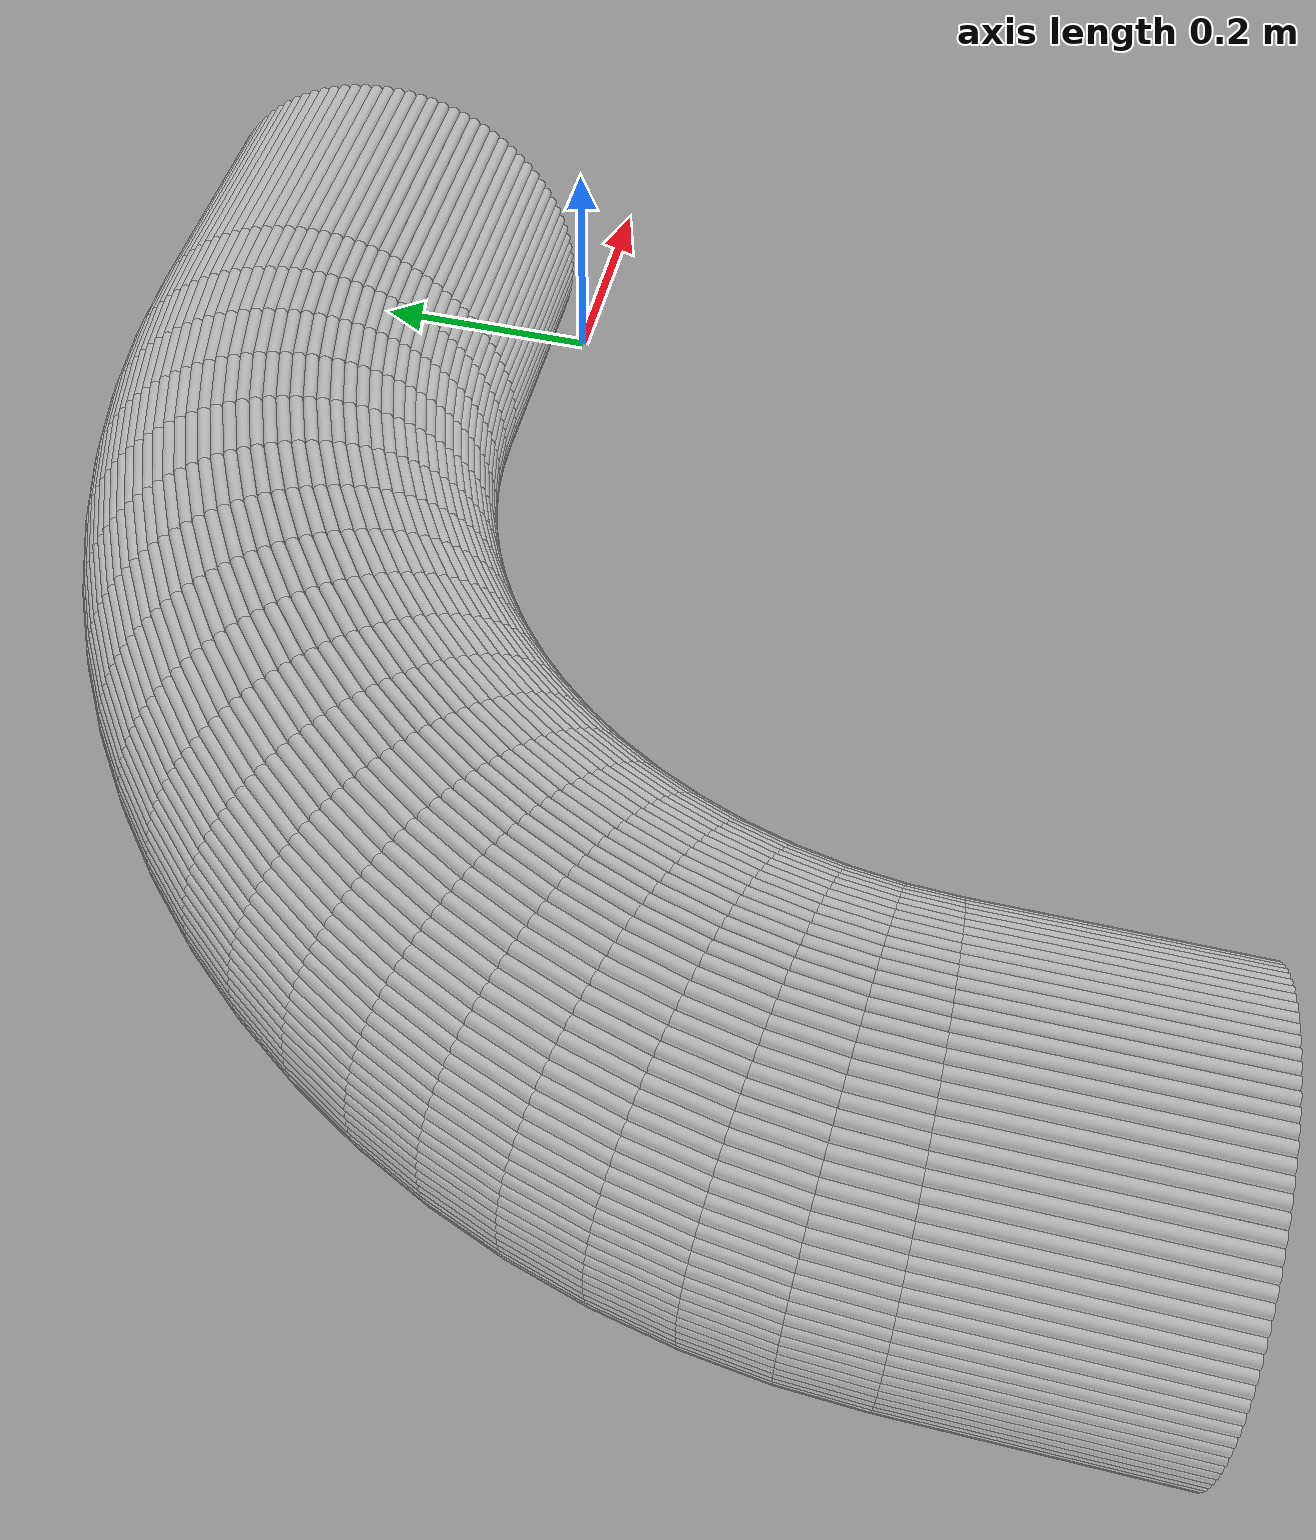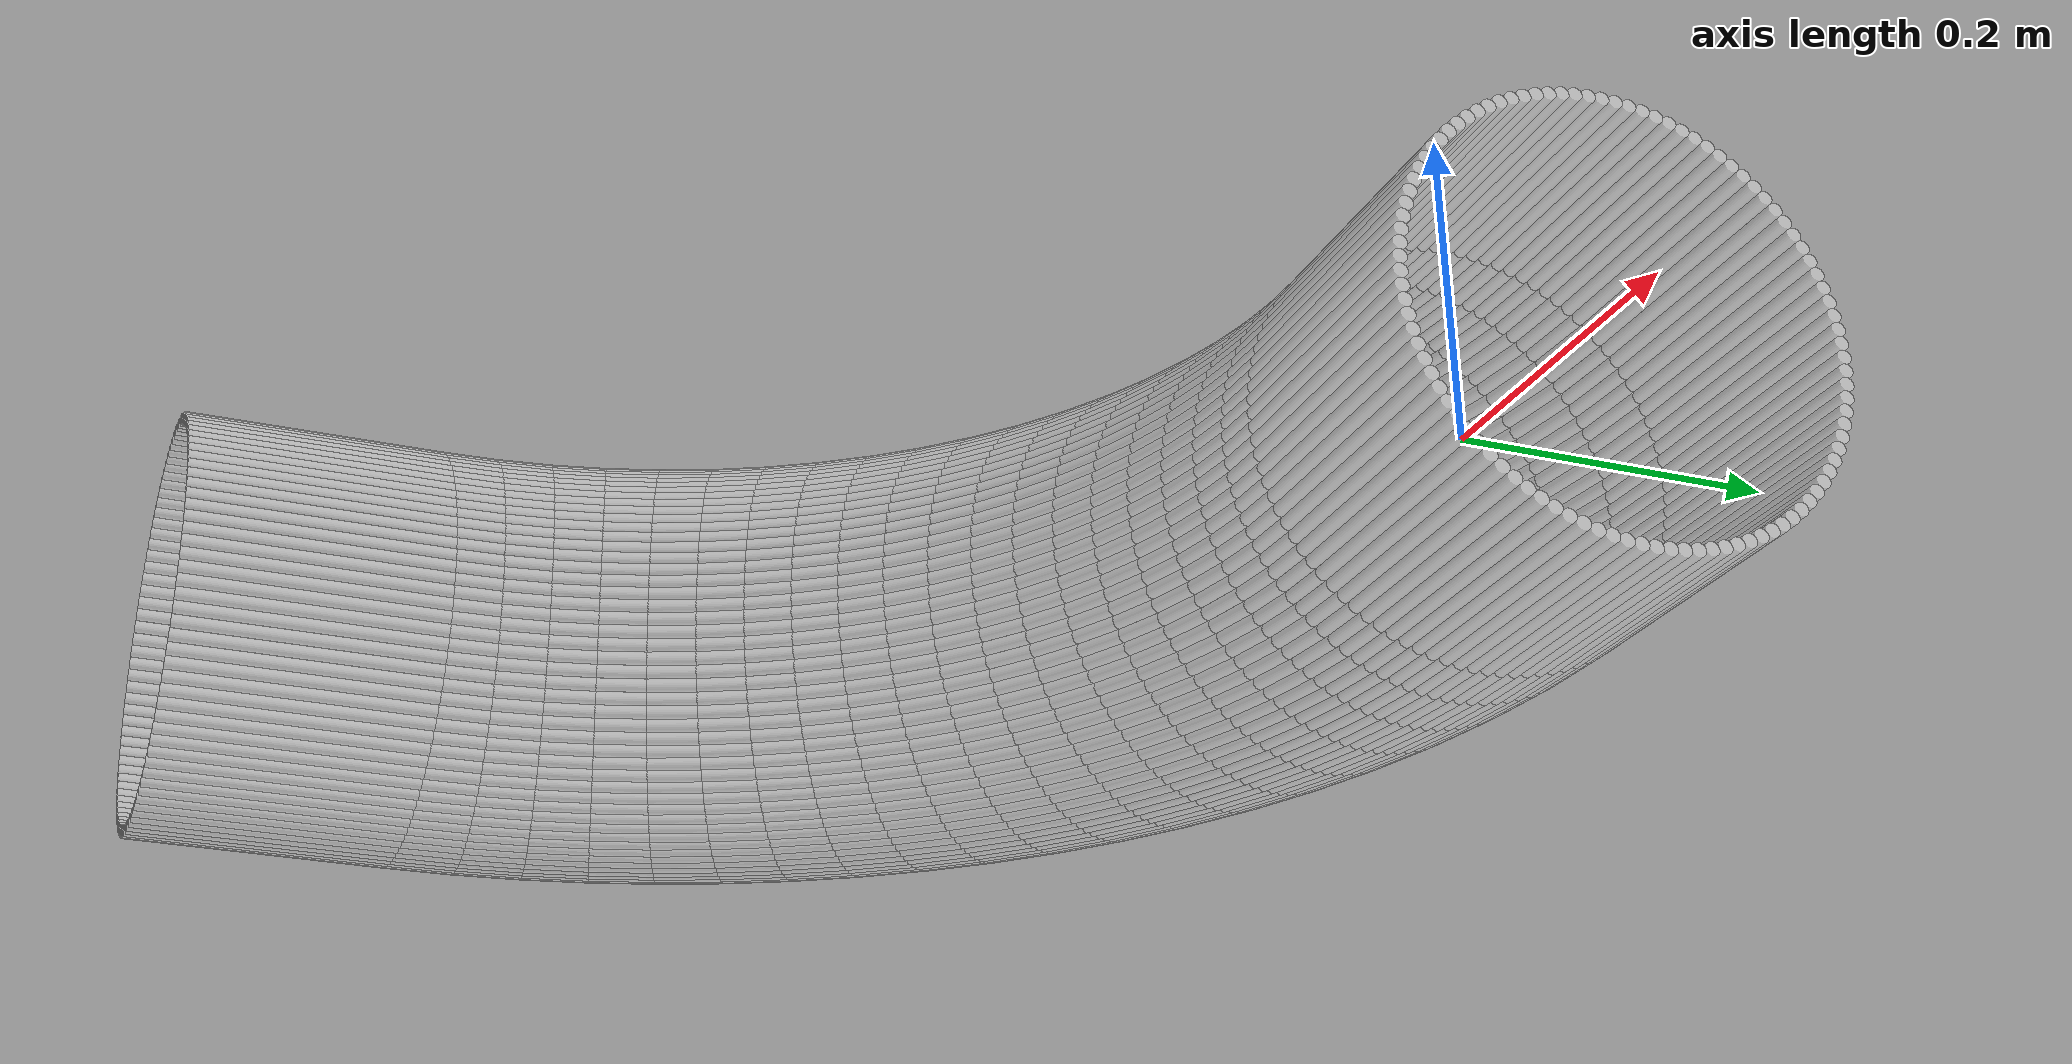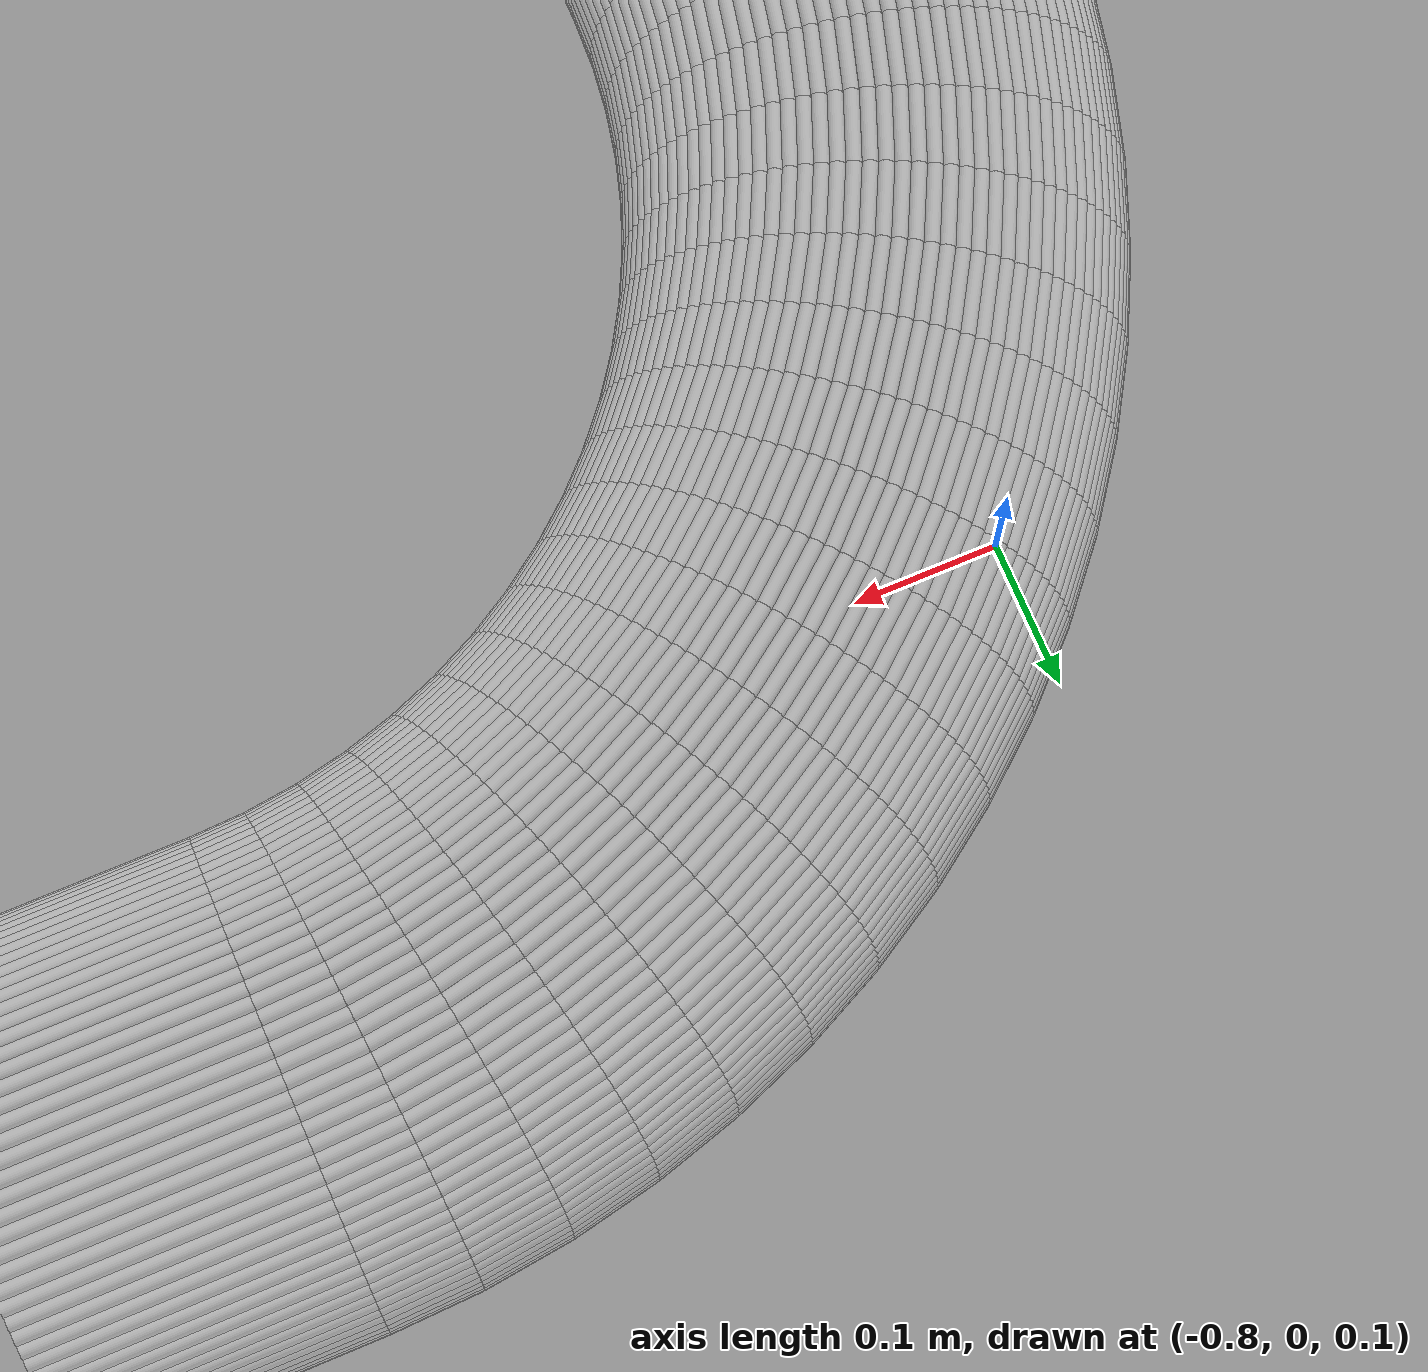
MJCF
<?xml version="1.0" encoding="utf-8"?>
<mujoco>
   <worldbody>
   <body pos="-0.25 -0.44 -0.02" euler="0 0 90">
      <geom euler=" 0 10 0 " fromto="0.76 -0.2 0.16 0.76 0 0.16" rgba="1 1 1 0.35"
            size="0.0050257"
            type="cylinder"/>
      <geom euler=" 0 20 0 " fromto="0.75968 -0.2 0.17005 0.75968 0 0.17005"
            rgba="1 1 1 0.35"
            size="0.0050257"
            type="cylinder"/>
      <geom euler=" 0 30 0 " fromto="0.75874 -0.2 0.18005 0.75874 0 0.18005"
            rgba="1 1 1 0.35"
            size="0.0050257"
            type="cylinder"/>
      <geom euler=" 0 40 0 " fromto="0.75717 -0.2 0.18998 0.75717 0 0.18998"
            rgba="1 1 1 0.35"
            size="0.0050257"
            type="cylinder"/>
      <geom euler=" 0 50 0 " fromto="0.75497 -0.2 0.19979 0.75497 0 0.19979"
            rgba="1 1 1 0.35"
            size="0.0050257"
            type="cylinder"/>
      <geom euler=" 0 60 0 " fromto="0.75217 -0.2 0.20944 0.75217 0 0.20944"
            rgba="1 1 1 0.35"
            size="0.0050257"
            type="cylinder"/>
      <geom euler=" 0 70 0 " fromto="0.74876 -0.2 0.2189 0.74876 0 0.2189"
            rgba="1 1 1 0.35"
            size="0.0050257"
            type="cylinder"/>
      <geom euler=" 0 80 0 " fromto="0.74477 -0.2 0.22812 0.74477 0 0.22812"
            rgba="1 1 1 0.35"
            size="0.0050257"
            type="cylinder"/>
      <geom euler=" 0 90 0 " fromto="0.74021 -0.2 0.23708 0.74021 0 0.23708"
            rgba="1 1 1 0.35"
            size="0.0050257"
            type="cylinder"/>
      <geom euler=" 0 100 0 " fromto="0.73509 -0.2 0.24573 0.73509 0 0.24573"
            rgba="1 1 1 0.35"
            size="0.0050257"
            type="cylinder"/>
      <geom euler=" 0 110 0 " fromto="0.72944 -0.2 0.25405 0.72944 0 0.25405"
            rgba="1 1 1 0.35"
            size="0.0050257"
            type="cylinder"/>
      <geom euler=" 0 120 0 " fromto="0.72328 -0.2 0.26199 0.72328 0 0.26199"
            rgba="1 1 1 0.35"
            size="0.0050257"
            type="cylinder"/>
      <geom euler=" 0 130 0 " fromto="0.71663 -0.2 0.26953 0.71663 0 0.26953"
            rgba="1 1 1 0.35"
            size="0.0050257"
            type="cylinder"/>
      <geom euler=" 0 140 0 " fromto="0.70953 -0.2 0.27663 0.70953 0 0.27663"
            rgba="1 1 1 0.35"
            size="0.0050257"
            type="cylinder"/>
      <geom euler=" 0 150 0 " fromto="0.70199 -0.2 0.28328 0.70199 0 0.28328"
            rgba="1 1 1 0.35"
            size="0.0050257"
            type="cylinder"/>
      <geom euler=" 0 160 0 " fromto="0.69405 -0.2 0.28944 0.69405 0 0.28944"
            rgba="1 1 1 0.35"
            size="0.0050257"
            type="cylinder"/>
      <geom euler=" 0 170 0 " fromto="0.68573 -0.2 0.29509 0.68573 0 0.29509"
            rgba="1 1 1 0.35"
            size="0.0050257"
            type="cylinder"/>
      <geom euler=" 0 180 0 " fromto="0.67708 -0.2 0.30021 0.67708 0 0.30021"
            rgba="1 1 1 0.35"
            size="0.0050257"
            type="cylinder"/>
      <geom euler=" 0 190 0 " fromto="0.66812 -0.2 0.30477 0.66812 0 0.30477"
            rgba="1 1 1 0.35"
            size="0.0050257"
            type="cylinder"/>
      <geom euler=" 0 200 0 " fromto="0.6589 -0.2 0.30876 0.6589 0 0.30876"
            rgba="1 1 1 0.35"
            size="0.0050257"
            type="cylinder"/>
      <geom euler=" 0 210 0 " fromto="0.64944 -0.2 0.31217 0.64944 0 0.31217"
            rgba="1 1 1 0.35"
            size="0.0050257"
            type="cylinder"/>
      <geom euler=" 0 220 0 " fromto="0.63979 -0.2 0.31497 0.63979 0 0.31497"
            rgba="1 1 1 0.35"
            size="0.0050257"
            type="cylinder"/>
      <geom euler=" 0 230 0 " fromto="0.62998 -0.2 0.31717 0.62998 0 0.31717"
            rgba="1 1 1 0.35"
            size="0.0050257"
            type="cylinder"/>
      <geom euler=" 0 240 0 " fromto="0.62005 -0.2 0.31874 0.62005 0 0.31874"
            rgba="1 1 1 0.35"
            size="0.0050257"
            type="cylinder"/>
      <geom euler=" 0 250 0 " fromto="0.61005 -0.2 0.31968 0.61005 0 0.31968"
            rgba="1 1 1 0.35"
            size="0.0050257"
            type="cylinder"/>
      <geom euler=" 0 260 0 " fromto="0.6 -0.2 0.32 0.6 0 0.32" rgba="1 1 1 0.35"
            size="0.0050257"
            type="cylinder"/>
      <geom euler=" 0 270 0 " fromto="0.58995 -0.2 0.31968 0.58995 0 0.31968"
            rgba="1 1 1 0.35"
            size="0.0050257"
            type="cylinder"/>
      <geom euler=" 0 280 0 " fromto="0.57995 -0.2 0.31874 0.57995 0 0.31874"
            rgba="1 1 1 0.35"
            size="0.0050257"
            type="cylinder"/>
      <geom euler=" 0 290 0 " fromto="0.57002 -0.2 0.31717 0.57002 0 0.31717"
            rgba="1 1 1 0.35"
            size="0.0050257"
            type="cylinder"/>
      <geom euler=" 0 300 0 " fromto="0.56021 -0.2 0.31497 0.56021 0 0.31497"
            rgba="1 1 1 0.35"
            size="0.0050257"
            type="cylinder"/>
      <geom euler=" 0 310 0 " fromto="0.55056 -0.2 0.31217 0.55056 0 0.31217"
            rgba="1 1 1 0.35"
            size="0.0050257"
            type="cylinder"/>
      <geom euler=" 0 320 0 " fromto="0.5411 -0.2 0.30876 0.5411 0 0.30876"
            rgba="1 1 1 0.35"
            size="0.0050257"
            type="cylinder"/>
      <geom euler=" 0 330 0 " fromto="0.53188 -0.2 0.30477 0.53188 0 0.30477"
            rgba="1 1 1 0.35"
            size="0.0050257"
            type="cylinder"/>
      <geom euler=" 0 340 0 " fromto="0.52292 -0.2 0.30021 0.52292 0 0.30021"
            rgba="1 1 1 0.35"
            size="0.0050257"
            type="cylinder"/>
      <geom euler=" 0 350 0 " fromto="0.51427 -0.2 0.29509 0.51427 0 0.29509"
            rgba="1 1 1 0.35"
            size="0.0050257"
            type="cylinder"/>
      <geom euler=" 0 360 0 " fromto="0.50595 -0.2 0.28944 0.50595 0 0.28944"
            rgba="1 1 1 0.35"
            size="0.0050257"
            type="cylinder"/>
      <geom euler=" 0 370 0 " fromto="0.49801 -0.2 0.28328 0.49801 0 0.28328"
            rgba="1 1 1 0.35"
            size="0.0050257"
            type="cylinder"/>
      <geom euler=" 0 380 0 " fromto="0.49047 -0.2 0.27663 0.49047 0 0.27663"
            rgba="1 1 1 0.35"
            size="0.0050257"
            type="cylinder"/>
      <geom euler=" 0 390 0 " fromto="0.48337 -0.2 0.26953 0.48337 0 0.26953"
            rgba="1 1 1 0.35"
            size="0.0050257"
            type="cylinder"/>
      <geom euler=" 0 400 0 " fromto="0.47672 -0.2 0.26199 0.47672 0 0.26199"
            rgba="1 1 1 0.35"
            size="0.0050257"
            type="cylinder"/>
      <geom euler=" 0 410 0 " fromto="0.47056 -0.2 0.25405 0.47056 0 0.25405"
            rgba="1 1 1 0.35"
            size="0.0050257"
            type="cylinder"/>
      <geom euler=" 0 420 0 " fromto="0.46491 -0.2 0.24573 0.46491 0 0.24573"
            rgba="1 1 1 0.35"
            size="0.0050257"
            type="cylinder"/>
      <geom euler=" 0 430 0 " fromto="0.45979 -0.2 0.23708 0.45979 0 0.23708"
            rgba="1 1 1 0.35"
            size="0.0050257"
            type="cylinder"/>
      <geom euler=" 0 440 0 " fromto="0.45523 -0.2 0.22812 0.45523 0 0.22812"
            rgba="1 1 1 0.35"
            size="0.0050257"
            type="cylinder"/>
      <geom euler=" 0 450 0 " fromto="0.45124 -0.2 0.2189 0.45124 0 0.2189"
            rgba="1 1 1 0.35"
            size="0.0050257"
            type="cylinder"/>
      <geom euler=" 0 460 0 " fromto="0.44783 -0.2 0.20944 0.44783 0 0.20944"
            rgba="1 1 1 0.35"
            size="0.0050257"
            type="cylinder"/>
      <geom euler=" 0 470 0 " fromto="0.44503 -0.2 0.19979 0.44503 0 0.19979"
            rgba="1 1 1 0.35"
            size="0.0050257"
            type="cylinder"/>
      <geom euler=" 0 480 0 " fromto="0.44283 -0.2 0.18998 0.44283 0 0.18998"
            rgba="1 1 1 0.35"
            size="0.0050257"
            type="cylinder"/>
      <geom euler=" 0 490 0 " fromto="0.44126 -0.2 0.18005 0.44126 0 0.18005"
            rgba="1 1 1 0.35"
            size="0.0050257"
            type="cylinder"/>
      <geom euler=" 0 500 0 " fromto="0.44032 -0.2 0.17005 0.44032 0 0.17005"
            rgba="1 1 1 0.35"
            size="0.0050257"
            type="cylinder"/>
      <geom euler=" 0 510 0 " fromto="0.44 -0.2 0.16 0.44 0 0.16" rgba="1 1 1 0.35"
            size="0.0050257"
            type="cylinder"/>
      <geom euler=" 0 520 0 " fromto="0.44032 -0.2 0.14995 0.44032 0 0.14995"
            rgba="1 1 1 0.35"
            size="0.0050257"
            type="cylinder"/>
      <geom euler=" 0 530 0 " fromto="0.44126 -0.2 0.13995 0.44126 0 0.13995"
            rgba="1 1 1 0.35"
            size="0.0050257"
            type="cylinder"/>
      <geom euler=" 0 540 0 " fromto="0.44283 -0.2 0.13002 0.44283 0 0.13002"
            rgba="1 1 1 0.35"
            size="0.0050257"
            type="cylinder"/>
      <geom euler=" 0 550 0 " fromto="0.44503 -0.2 0.12021 0.44503 0 0.12021"
            rgba="1 1 1 0.35"
            size="0.0050257"
            type="cylinder"/>
      <geom euler=" 0 560 0 " fromto="0.44783 -0.2 0.11056 0.44783 0 0.11056"
            rgba="1 1 1 0.35"
            size="0.0050257"
            type="cylinder"/>
      <geom euler=" 0 570 0 " fromto="0.45124 -0.2 0.1011 0.45124 0 0.1011"
            rgba="1 1 1 0.35"
            size="0.0050257"
            type="cylinder"/>
      <geom euler=" 0 580 0 " fromto="0.45523 -0.2 0.091875 0.45523 0 0.091875"
            rgba="1 1 1 0.35"
            size="0.0050257"
            type="cylinder"/>
      <geom euler=" 0 590 0 " fromto="0.45979 -0.2 0.082919 0.45979 0 0.082919"
            rgba="1 1 1 0.35"
            size="0.0050257"
            type="cylinder"/>
      <geom euler=" 0 600 0 " fromto="0.46491 -0.2 0.074268 0.46491 0 0.074268"
            rgba="1 1 1 0.35"
            size="0.0050257"
            type="cylinder"/>
      <geom euler=" 0 610 0 " fromto="0.47056 -0.2 0.065954 0.47056 0 0.065954"
            rgba="1 1 1 0.35"
            size="0.0050257"
            type="cylinder"/>
      <geom euler=" 0 620 0 " fromto="0.47672 -0.2 0.058012 0.47672 0 0.058012"
            rgba="1 1 1 0.35"
            size="0.0050257"
            type="cylinder"/>
      <geom euler=" 0 630 0 " fromto="0.48337 -0.2 0.050472 0.48337 0 0.050472"
            rgba="1 1 1 0.35"
            size="0.0050257"
            type="cylinder"/>
      <geom euler=" 0 640 0 " fromto="0.49047 -0.2 0.043365 0.49047 0 0.043365"
            rgba="1 1 1 0.35"
            size="0.0050257"
            type="cylinder"/>
      <geom euler=" 0 650 0 " fromto="0.49801 -0.2 0.036718 0.49801 0 0.036718"
            rgba="1 1 1 0.35"
            size="0.0050257"
            type="cylinder"/>
      <geom euler=" 0 660 0 " fromto="0.50595 -0.2 0.030557 0.50595 0 0.030557"
            rgba="1 1 1 0.35"
            size="0.0050257"
            type="cylinder"/>
      <geom euler=" 0 670 0 " fromto="0.51427 -0.2 0.024908 0.51427 0 0.024908"
            rgba="1 1 1 0.35"
            size="0.0050257"
            type="cylinder"/>
      <geom euler=" 0 680 0 " fromto="0.52292 -0.2 0.019791 0.52292 0 0.019791"
            rgba="1 1 1 0.35"
            size="0.0050257"
            type="cylinder"/>
      <geom euler=" 0 690 0 " fromto="0.53188 -0.2 0.015228 0.53188 0 0.015228"
            rgba="1 1 1 0.35"
            size="0.0050257"
            type="cylinder"/>
      <geom euler=" 0 700 0 " fromto="0.5411 -0.2 0.011236 0.5411 0 0.011236"
            rgba="1 1 1 0.35"
            size="0.0050257"
            type="cylinder"/>
      <geom euler=" 0 710 0 " fromto="0.55056 -0.2 0.007831 0.55056 0 0.007831"
            rgba="1 1 1 0.35"
            size="0.0050257"
            type="cylinder"/>
      <geom euler=" 0 720 0 " fromto="0.56021 -0.2 0.0050267 0.56021 0 0.0050267"
            rgba="1 1 1 0.35"
            size="0.0050257"
            type="cylinder"/>
      <geom euler=" 0 730 0 " fromto="0.57002 -0.2 0.002834 0.57002 0 0.002834"
            rgba="1 1 1 0.35"
            size="0.0050257"
            type="cylinder"/>
      <geom euler=" 0 740 0 " fromto="0.57995 -0.2 0.0012616 0.57995 0 0.0012616"
            rgba="1 1 1 0.35"
            size="0.0050257"
            type="cylinder"/>
      <geom euler=" 0 750 0 " fromto="0.58995 -0.2 0.00031572 0.58995 0 0.00031572"
            rgba="1 1 1 0.35"
            size="0.0050257"
            type="cylinder"/>
      <geom euler=" 0 760 0 " fromto="0.6 -0.2 0 0.6 0 0" rgba="1 1 1 0.35"
            size="0.0050257"
            type="cylinder"/>
      <geom euler=" 0 770 0 " fromto="0.61005 -0.2 0.00031572 0.61005 0 0.00031572"
            rgba="1 1 1 0.35"
            size="0.0050257"
            type="cylinder"/>
      <geom euler=" 0 780 0 " fromto="0.62005 -0.2 0.0012616 0.62005 0 0.0012616"
            rgba="1 1 1 0.35"
            size="0.0050257"
            type="cylinder"/>
      <geom euler=" 0 790 0 " fromto="0.62998 -0.2 0.002834 0.62998 0 0.002834"
            rgba="1 1 1 0.35"
            size="0.0050257"
            type="cylinder"/>
      <geom euler=" 0 800 0 " fromto="0.63979 -0.2 0.0050267 0.63979 0 0.0050267"
            rgba="1 1 1 0.35"
            size="0.0050257"
            type="cylinder"/>
      <geom euler=" 0 810 0 " fromto="0.64944 -0.2 0.007831 0.64944 0 0.007831"
            rgba="1 1 1 0.35"
            size="0.0050257"
            type="cylinder"/>
      <geom euler=" 0 820 0 " fromto="0.6589 -0.2 0.011236 0.6589 0 0.011236"
            rgba="1 1 1 0.35"
            size="0.0050257"
            type="cylinder"/>
      <geom euler=" 0 830 0 " fromto="0.66812 -0.2 0.015228 0.66812 0 0.015228"
            rgba="1 1 1 0.35"
            size="0.0050257"
            type="cylinder"/>
      <geom euler=" 0 840 0 " fromto="0.67708 -0.2 0.019791 0.67708 0 0.019791"
            rgba="1 1 1 0.35"
            size="0.0050257"
            type="cylinder"/>
      <geom euler=" 0 850 0 " fromto="0.68573 -0.2 0.024908 0.68573 0 0.024908"
            rgba="1 1 1 0.35"
            size="0.0050257"
            type="cylinder"/>
      <geom euler=" 0 860 0 " fromto="0.69405 -0.2 0.030557 0.69405 0 0.030557"
            rgba="1 1 1 0.35"
            size="0.0050257"
            type="cylinder"/>
      <geom euler=" 0 870 0 " fromto="0.70199 -0.2 0.036718 0.70199 0 0.036718"
            rgba="1 1 1 0.35"
            size="0.0050257"
            type="cylinder"/>
      <geom euler=" 0 880 0 " fromto="0.70953 -0.2 0.043365 0.70953 0 0.043365"
            rgba="1 1 1 0.35"
            size="0.0050257"
            type="cylinder"/>
      <geom euler=" 0 890 0 " fromto="0.71663 -0.2 0.050472 0.71663 0 0.050472"
            rgba="1 1 1 0.35"
            size="0.0050257"
            type="cylinder"/>
      <geom euler=" 0 900 0 " fromto="0.72328 -0.2 0.058012 0.72328 0 0.058012"
            rgba="1 1 1 0.35"
            size="0.0050257"
            type="cylinder"/>
      <geom euler=" 0 910 0 " fromto="0.72944 -0.2 0.065954 0.72944 0 0.065954"
            rgba="1 1 1 0.35"
            size="0.0050257"
            type="cylinder"/>
      <geom euler=" 0 920 0 " fromto="0.73509 -0.2 0.074268 0.73509 0 0.074268"
            rgba="1 1 1 0.35"
            size="0.0050257"
            type="cylinder"/>
      <geom euler=" 0 930 0 " fromto="0.74021 -0.2 0.082919 0.74021 0 0.082919"
            rgba="1 1 1 0.35"
            size="0.0050257"
            type="cylinder"/>
      <geom euler=" 0 940 0 " fromto="0.74477 -0.2 0.091875 0.74477 0 0.091875"
            rgba="1 1 1 0.35"
            size="0.0050257"
            type="cylinder"/>
      <geom euler=" 0 950 0 " fromto="0.74876 -0.2 0.1011 0.74876 0 0.1011"
            rgba="1 1 1 0.35"
            size="0.0050257"
            type="cylinder"/>
      <geom euler=" 0 960 0 " fromto="0.75217 -0.2 0.11056 0.75217 0 0.11056"
            rgba="1 1 1 0.35"
            size="0.0050257"
            type="cylinder"/>
      <geom euler=" 0 970 0 " fromto="0.75497 -0.2 0.12021 0.75497 0 0.12021"
            rgba="1 1 1 0.35"
            size="0.0050257"
            type="cylinder"/>
      <geom euler=" 0 980 0 " fromto="0.75717 -0.2 0.13002 0.75717 0 0.13002"
            rgba="1 1 1 0.35"
            size="0.0050257"
            type="cylinder"/>
      <geom euler=" 0 990 0 " fromto="0.75874 -0.2 0.13995 0.75874 0 0.13995"
            rgba="1 1 1 0.35"
            size="0.0050257"
            type="cylinder"/>
      <geom euler=" 0 1000 0 " fromto="0.75968 -0.2 0.14995 0.75968 0 0.14995"
            rgba="1 1 1 0.35"
            size="0.0050257"
            type="cylinder"/>
      <geom euler=" 0 10 0 " fromto="0.76 0 0.16 0.7574 0.06276 0.16" rgba="1 1 1 0.35"
            size="0.0050257"
            type="cylinder"/>
      <geom euler=" 0 20 0 " fromto="0.75968 0 0.17005 0.75709 0.062734 0.17005"
            rgba="1 1 1 0.35"
            size="0.0050257"
            type="cylinder"/>
      <geom euler=" 0 30 0 " fromto="0.75874 0 0.18005 0.75615 0.062656 0.18005"
            rgba="1 1 1 0.35"
            size="0.0050257"
            type="cylinder"/>
      <geom euler=" 0 40 0 " fromto="0.75717 0 0.18998 0.75458 0.062526 0.18998"
            rgba="1 1 1 0.35"
            size="0.0050257"
            type="cylinder"/>
      <geom euler=" 0 50 0 " fromto="0.75497 0 0.19979 0.75239 0.062345 0.19979"
            rgba="1 1 1 0.35"
            size="0.0050257"
            type="cylinder"/>
      <geom euler=" 0 60 0 " fromto="0.75217 0 0.20944 0.7496 0.062114 0.20944"
            rgba="1 1 1 0.35"
            size="0.0050257"
            type="cylinder"/>
      <geom euler=" 0 70 0 " fromto="0.74876 0 0.2189 0.74621 0.061832 0.2189"
            rgba="1 1 1 0.35"
            size="0.0050257"
            type="cylinder"/>
      <geom euler=" 0 80 0 " fromto="0.74477 0 0.22812 0.74223 0.061503 0.22812"
            rgba="1 1 1 0.35"
            size="0.0050257"
            type="cylinder"/>
      <geom euler=" 0 90 0 " fromto="0.74021 0 0.23708 0.73768 0.061126 0.23708"
            rgba="1 1 1 0.35"
            size="0.0050257"
            type="cylinder"/>
      <geom euler=" 0 100 0 " fromto="0.73509 0 0.24573 0.73258 0.060703 0.24573"
            rgba="1 1 1 0.35"
            size="0.0050257"
            type="cylinder"/>
      <geom euler=" 0 110 0 " fromto="0.72944 0 0.25405 0.72695 0.060237 0.25405"
            rgba="1 1 1 0.35"
            size="0.0050257"
            type="cylinder"/>
      <geom euler=" 0 120 0 " fromto="0.72328 0 0.26199 0.72081 0.059728 0.26199"
            rgba="1 1 1 0.35"
            size="0.0050257"
            type="cylinder"/>
      <geom euler=" 0 130 0 " fromto="0.71663 0 0.26953 0.71419 0.059179 0.26953"
            rgba="1 1 1 0.35"
            size="0.0050257"
            type="cylinder"/>
      <geom euler=" 0 140 0 " fromto="0.70953 0 0.27663 0.7071 0.058592 0.27663"
            rgba="1 1 1 0.35"
            size="0.0050257"
            type="cylinder"/>
      <geom euler=" 0 150 0 " fromto="0.70199 0 0.28328 0.69959 0.05797 0.28328"
            rgba="1 1 1 0.35"
            size="0.0050257"
            type="cylinder"/>
      <geom euler=" 0 160 0 " fromto="0.69405 0 0.28944 0.69168 0.057314 0.28944"
            rgba="1 1 1 0.35"
            size="0.0050257"
            type="cylinder"/>
      <geom euler=" 0 170 0 " fromto="0.68573 0 0.29509 0.68339 0.056627 0.29509"
            rgba="1 1 1 0.35"
            size="0.0050257"
            type="cylinder"/>
      <geom euler=" 0 180 0 " fromto="0.67708 0 0.30021 0.67477 0.055913 0.30021"
            rgba="1 1 1 0.35"
            size="0.0050257"
            type="cylinder"/>
      <geom euler=" 0 190 0 " fromto="0.66812 0 0.30477 0.66584 0.055173 0.30477"
            rgba="1 1 1 0.35"
            size="0.0050257"
            type="cylinder"/>
      <geom euler=" 0 200 0 " fromto="0.6589 0 0.30876 0.65665 0.054412 0.30876"
            rgba="1 1 1 0.35"
            size="0.0050257"
            type="cylinder"/>
      <geom euler=" 0 210 0 " fromto="0.64944 0 0.31217 0.64722 0.053631 0.31217"
            rgba="1 1 1 0.35"
            size="0.0050257"
            type="cylinder"/>
      <geom euler=" 0 220 0 " fromto="0.63979 0 0.31497 0.63761 0.052833 0.31497"
            rgba="1 1 1 0.35"
            size="0.0050257"
            type="cylinder"/>
      <geom euler=" 0 230 0 " fromto="0.62998 0 0.31717 0.62783 0.052023 0.31717"
            rgba="1 1 1 0.35"
            size="0.0050257"
            type="cylinder"/>
      <geom euler=" 0 240 0 " fromto="0.62005 0 0.31874 0.61794 0.051204 0.31874"
            rgba="1 1 1 0.35"
            size="0.0050257"
            type="cylinder"/>
      <geom euler=" 0 250 0 " fromto="0.61005 0 0.31968 0.60796 0.050377 0.31968"
            rgba="1 1 1 0.35"
            size="0.0050257"
            type="cylinder"/>
      <geom euler=" 0 260 0 " fromto="0.6 0 0.32 0.59795 0.049548 0.32" rgba="1 1 1 0.35"
            size="0.0050257"
            type="cylinder"/>
      <geom euler=" 0 270 0 " fromto="0.58995 0 0.31968 0.58794 0.048718 0.31968"
            rgba="1 1 1 0.35"
            size="0.0050257"
            type="cylinder"/>
      <geom euler=" 0 280 0 " fromto="0.57995 0 0.31874 0.57797 0.047892 0.31874"
            rgba="1 1 1 0.35"
            size="0.0050257"
            type="cylinder"/>
      <geom euler=" 0 290 0 " fromto="0.57002 0 0.31717 0.56807 0.047072 0.31717"
            rgba="1 1 1 0.35"
            size="0.0050257"
            type="cylinder"/>
      <geom euler=" 0 300 0 " fromto="0.56021 0 0.31497 0.5583 0.046262 0.31497"
            rgba="1 1 1 0.35"
            size="0.0050257"
            type="cylinder"/>
      <geom euler=" 0 310 0 " fromto="0.55056 0 0.31217 0.54868 0.045465 0.31217"
            rgba="1 1 1 0.35"
            size="0.0050257"
            type="cylinder"/>
      <geom euler=" 0 320 0 " fromto="0.5411 0 0.30876 0.53925 0.044684 0.30876"
            rgba="1 1 1 0.35"
            size="0.0050257"
            type="cylinder"/>
      <geom euler=" 0 330 0 " fromto="0.53188 0 0.30477 0.53006 0.043922 0.30477"
            rgba="1 1 1 0.35"
            size="0.0050257"
            type="cylinder"/>
      <geom euler=" 0 340 0 " fromto="0.52292 0 0.30021 0.52113 0.043182 0.30021"
            rgba="1 1 1 0.35"
            size="0.0050257"
            type="cylinder"/>
      <geom euler=" 0 350 0 " fromto="0.51427 0 0.29509 0.51251 0.042468 0.29509"
            rgba="1 1 1 0.35"
            size="0.0050257"
            type="cylinder"/>
      <geom euler=" 0 360 0 " fromto="0.50595 0 0.28944 0.50423 0.041781 0.28944"
            rgba="1 1 1 0.35"
            size="0.0050257"
            type="cylinder"/>
      <geom euler=" 0 370 0 " fromto="0.49801 0 0.28328 0.49631 0.041126 0.28328"
            rgba="1 1 1 0.35"
            size="0.0050257"
            type="cylinder"/>
      <geom euler=" 0 380 0 " fromto="0.49047 0 0.27663 0.4888 0.040503 0.27663"
            rgba="1 1 1 0.35"
            size="0.0050257"
            type="cylinder"/>
      <geom euler=" 0 390 0 " fromto="0.48337 0 0.26953 0.48171 0.039916 0.26953"
            rgba="1 1 1 0.35"
            size="0.0050257"
            type="cylinder"/>
      <geom euler=" 0 400 0 " fromto="0.47672 0 0.26199 0.47509 0.039367 0.26199"
            rgba="1 1 1 0.35"
            size="0.0050257"
            type="cylinder"/>
      <geom euler=" 0 410 0 " fromto="0.47056 0 0.25405 0.46895 0.038858 0.25405"
            rgba="1 1 1 0.35"
            size="0.0050257"
            type="cylinder"/>
      <geom euler=" 0 420 0 " fromto="0.46491 0 0.24573 0.46332 0.038392 0.24573"
            rgba="1 1 1 0.35"
            size="0.0050257"
            type="cylinder"/>
      <geom euler=" 0 430 0 " fromto="0.45979 0 0.23708 0.45822 0.037969 0.23708"
            rgba="1 1 1 0.35"
            size="0.0050257"
            type="cylinder"/>
      <geom euler=" 0 440 0 " fromto="0.45523 0 0.22812 0.45367 0.037592 0.22812"
            rgba="1 1 1 0.35"
            size="0.0050257"
            type="cylinder"/>
      <geom euler=" 0 450 0 " fromto="0.45124 0 0.2189 0.44969 0.037263 0.2189"
            rgba="1 1 1 0.35"
            size="0.0050257"
            type="cylinder"/>
      <geom euler=" 0 460 0 " fromto="0.44783 0 0.20944 0.4463 0.036982 0.20944"
            rgba="1 1 1 0.35"
            size="0.0050257"
            type="cylinder"/>
      <geom euler=" 0 470 0 " fromto="0.44503 0 0.19979 0.44351 0.03675 0.19979"
            rgba="1 1 1 0.35"
            size="0.0050257"
            type="cylinder"/>
      <geom euler=" 0 480 0 " fromto="0.44283 0 0.18998 0.44132 0.036569 0.18998"
            rgba="1 1 1 0.35"
            size="0.0050257"
            type="cylinder"/>
      <geom euler=" 0 490 0 " fromto="0.44126 0 0.18005 0.43975 0.036439 0.18005"
            rgba="1 1 1 0.35"
            size="0.0050257"
            type="cylinder"/>
      <geom euler=" 0 500 0 " fromto="0.44032 0 0.17005 0.43881 0.036361 0.17005"
            rgba="1 1 1 0.35"
            size="0.0050257"
            type="cylinder"/>
      <geom euler=" 0 510 0 " fromto="0.44 0 0.16 0.4385 0.036335 0.16" rgba="1 1 1 0.35"
            size="0.0050257"
            type="cylinder"/>
      <geom euler=" 0 520 0 " fromto="0.44032 0 0.14995 0.43881 0.036361 0.14995"
            rgba="1 1 1 0.35"
            size="0.0050257"
            type="cylinder"/>
      <geom euler=" 0 530 0 " fromto="0.44126 0 0.13995 0.43975 0.036439 0.13995"
            rgba="1 1 1 0.35"
            size="0.0050257"
            type="cylinder"/>
      <geom euler=" 0 540 0 " fromto="0.44283 0 0.13002 0.44132 0.036569 0.13002"
            rgba="1 1 1 0.35"
            size="0.0050257"
            type="cylinder"/>
      <geom euler=" 0 550 0 " fromto="0.44503 0 0.12021 0.44351 0.03675 0.12021"
            rgba="1 1 1 0.35"
            size="0.0050257"
            type="cylinder"/>
      <geom euler=" 0 560 0 " fromto="0.44783 0 0.11056 0.4463 0.036982 0.11056"
            rgba="1 1 1 0.35"
            size="0.0050257"
            type="cylinder"/>
      <geom euler=" 0 570 0 " fromto="0.45124 0 0.1011 0.44969 0.037263 0.1011"
            rgba="1 1 1 0.35"
            size="0.0050257"
            type="cylinder"/>
      <geom euler=" 0 580 0 " fromto="0.45523 0 0.091875 0.45367 0.037592 0.091875"
            rgba="1 1 1 0.35"
            size="0.0050257"
            type="cylinder"/>
      <geom euler=" 0 590 0 " fromto="0.45979 0 0.082919 0.45822 0.037969 0.082919"
            rgba="1 1 1 0.35"
            size="0.0050257"
            type="cylinder"/>
      <geom euler=" 0 600 0 " fromto="0.46491 0 0.074268 0.46332 0.038392 0.074268"
            rgba="1 1 1 0.35"
            size="0.0050257"
            type="cylinder"/>
      <geom euler=" 0 610 0 " fromto="0.47056 0 0.065954 0.46895 0.038858 0.065954"
            rgba="1 1 1 0.35"
            size="0.0050257"
            type="cylinder"/>
      <geom euler=" 0 620 0 " fromto="0.47672 0 0.058012 0.47509 0.039367 0.058012"
            rgba="1 1 1 0.35"
            size="0.0050257"
            type="cylinder"/>
      <geom euler=" 0 630 0 " fromto="0.48337 0 0.050472 0.48171 0.039916 0.050472"
            rgba="1 1 1 0.35"
            size="0.0050257"
            type="cylinder"/>
      <geom euler=" 0 640 0 " fromto="0.49047 0 0.043365 0.4888 0.040503 0.043365"
            rgba="1 1 1 0.35"
            size="0.0050257"
            type="cylinder"/>
      <geom euler=" 0 650 0 " fromto="0.49801 0 0.036718 0.49631 0.041126 0.036718"
            rgba="1 1 1 0.35"
            size="0.0050257"
            type="cylinder"/>
      <geom euler=" 0 660 0 " fromto="0.50595 0 0.030557 0.50423 0.041781 0.030557"
            rgba="1 1 1 0.35"
            size="0.0050257"
            type="cylinder"/>
      <geom euler=" 0 670 0 " fromto="0.51427 0 0.024908 0.51251 0.042468 0.024908"
            rgba="1 1 1 0.35"
            size="0.0050257"
            type="cylinder"/>
      <geom euler=" 0 680 0 " fromto="0.52292 0 0.019791 0.52113 0.043182 0.019791"
            rgba="1 1 1 0.35"
            size="0.0050257"
            type="cylinder"/>
      <geom euler=" 0 690 0 " fromto="0.53188 0 0.015228 0.53006 0.043922 0.015228"
            rgba="1 1 1 0.35"
            size="0.0050257"
            type="cylinder"/>
      <geom euler=" 0 700 0 " fromto="0.5411 0 0.011236 0.53925 0.044684 0.011236"
            rgba="1 1 1 0.35"
            size="0.0050257"
            type="cylinder"/>
      <geom euler=" 0 710 0 " fromto="0.55056 0 0.007831 0.54868 0.045465 0.007831"
            rgba="1 1 1 0.35"
            size="0.0050257"
            type="cylinder"/>
      <geom euler=" 0 720 0 " fromto="0.56021 0 0.0050267 0.5583 0.046262 0.0050267"
            rgba="1 1 1 0.35"
            size="0.0050257"
            type="cylinder"/>
      <geom euler=" 0 730 0 " fromto="0.57002 0 0.002834 0.56807 0.047072 0.002834"
            rgba="1 1 1 0.35"
            size="0.0050257"
            type="cylinder"/>
      <geom euler=" 0 740 0 " fromto="0.57995 0 0.0012616 0.57797 0.047892 0.0012616"
            rgba="1 1 1 0.35"
            size="0.0050257"
            type="cylinder"/>
      <geom euler=" 0 750 0 " fromto="0.58995 0 0.00031572 0.58794 0.048718 0.00031572"
            rgba="1 1 1 0.35"
            size="0.0050257"
            type="cylinder"/>
      <geom euler=" 0 760 0 " fromto="0.6 0 0 0.59795 0.049548 0" rgba="1 1 1 0.35"
            size="0.0050257"
            type="cylinder"/>
      <geom euler=" 0 770 0 " fromto="0.61005 0 0.00031572 0.60796 0.050377 0.00031572"
            rgba="1 1 1 0.35"
            size="0.0050257"
            type="cylinder"/>
      <geom euler=" 0 780 0 " fromto="0.62005 0 0.0012616 0.61794 0.051204 0.0012616"
            rgba="1 1 1 0.35"
            size="0.0050257"
            type="cylinder"/>
      <geom euler=" 0 790 0 " fromto="0.62998 0 0.002834 0.62783 0.052023 0.002834"
            rgba="1 1 1 0.35"
            size="0.0050257"
            type="cylinder"/>
      <geom euler=" 0 800 0 " fromto="0.63979 0 0.0050267 0.63761 0.052833 0.0050267"
            rgba="1 1 1 0.35"
            size="0.0050257"
            type="cylinder"/>
      <geom euler=" 0 810 0 " fromto="0.64944 0 0.007831 0.64722 0.053631 0.007831"
            rgba="1 1 1 0.35"
            size="0.0050257"
            type="cylinder"/>
      <geom euler=" 0 820 0 " fromto="0.6589 0 0.011236 0.65665 0.054412 0.011236"
            rgba="1 1 1 0.35"
            size="0.0050257"
            type="cylinder"/>
      <geom euler=" 0 830 0 " fromto="0.66812 0 0.015228 0.66584 0.055173 0.015228"
            rgba="1 1 1 0.35"
            size="0.0050257"
            type="cylinder"/>
      <geom euler=" 0 840 0 " fromto="0.67708 0 0.019791 0.67477 0.055913 0.019791"
            rgba="1 1 1 0.35"
            size="0.0050257"
            type="cylinder"/>
      <geom euler=" 0 850 0 " fromto="0.68573 0 0.024908 0.68339 0.056627 0.024908"
            rgba="1 1 1 0.35"
            size="0.0050257"
            type="cylinder"/>
      <geom euler=" 0 860 0 " fromto="0.69405 0 0.030557 0.69168 0.057314 0.030557"
            rgba="1 1 1 0.35"
            size="0.0050257"
            type="cylinder"/>
      <geom euler=" 0 870 0 " fromto="0.70199 0 0.036718 0.69959 0.05797 0.036718"
            rgba="1 1 1 0.35"
            size="0.0050257"
            type="cylinder"/>
      <geom euler=" 0 880 0 " fromto="0.70953 0 0.043365 0.7071 0.058592 0.043365"
            rgba="1 1 1 0.35"
            size="0.0050257"
            type="cylinder"/>
      <geom euler=" 0 890 0 " fromto="0.71663 0 0.050472 0.71419 0.059179 0.050472"
            rgba="1 1 1 0.35"
            size="0.0050257"
            type="cylinder"/>
      <geom euler=" 0 900 0 " fromto="0.72328 0 0.058012 0.72081 0.059728 0.058012"
            rgba="1 1 1 0.35"
            size="0.0050257"
            type="cylinder"/>
      <geom euler=" 0 910 0 " fromto="0.72944 0 0.065954 0.72695 0.060237 0.065954"
            rgba="1 1 1 0.35"
            size="0.0050257"
            type="cylinder"/>
      <geom euler=" 0 920 0 " fromto="0.73509 0 0.074268 0.73258 0.060703 0.074268"
            rgba="1 1 1 0.35"
            size="0.0050257"
            type="cylinder"/>
      <geom euler=" 0 930 0 " fromto="0.74021 0 0.082919 0.73768 0.061126 0.082919"
            rgba="1 1 1 0.35"
            size="0.0050257"
            type="cylinder"/>
      <geom euler=" 0 940 0 " fromto="0.74477 0 0.091875 0.74223 0.061503 0.091875"
            rgba="1 1 1 0.35"
            size="0.0050257"
            type="cylinder"/>
      <geom euler=" 0 950 0 " fromto="0.74876 0 0.1011 0.74621 0.061832 0.1011"
            rgba="1 1 1 0.35"
            size="0.0050257"
            type="cylinder"/>
      <geom euler=" 0 960 0 " fromto="0.75217 0 0.11056 0.7496 0.062114 0.11056"
            rgba="1 1 1 0.35"
            size="0.0050257"
            type="cylinder"/>
      <geom euler=" 0 970 0 " fromto="0.75497 0 0.12021 0.75239 0.062345 0.12021"
            rgba="1 1 1 0.35"
            size="0.0050257"
            type="cylinder"/>
      <geom euler=" 0 980 0 " fromto="0.75717 0 0.13002 0.75458 0.062526 0.13002"
            rgba="1 1 1 0.35"
            size="0.0050257"
            type="cylinder"/>
      <geom euler=" 0 990 0 " fromto="0.75874 0 0.13995 0.75615 0.062656 0.13995"
            rgba="1 1 1 0.35"
            size="0.0050257"
            type="cylinder"/>
      <geom euler=" 0 1000 0 " fromto="0.75968 0 0.14995 0.75709 0.062734 0.14995"
            rgba="1 1 1 0.35"
            size="0.0050257"
            type="cylinder"/>
      <geom euler=" 0 10 0 " fromto="0.7574 0.06276 0.16 0.74963 0.12509 0.16"
            rgba="1 1 1 0.35"
            size="0.0050257"
            type="cylinder"/>
      <geom euler=" 0 20 0 " fromto="0.75709 0.062734 0.17005 0.74932 0.12504 0.17005"
            rgba="1 1 1 0.35"
            size="0.0050257"
            type="cylinder"/>
      <geom euler=" 0 30 0 " fromto="0.75615 0.062656 0.18005 0.74839 0.12488 0.18005"
            rgba="1 1 1 0.35"
            size="0.0050257"
            type="cylinder"/>
      <geom euler=" 0 40 0 " fromto="0.75458 0.062526 0.18998 0.74684 0.12463 0.18998"
            rgba="1 1 1 0.35"
            size="0.0050257"
            type="cylinder"/>
      <geom euler=" 0 50 0 " fromto="0.75239 0.062345 0.19979 0.74468 0.12426 0.19979"
            rgba="1 1 1 0.35"
            size="0.0050257"
            type="cylinder"/>
      <geom euler=" 0 60 0 " fromto="0.7496 0.062114 0.20944 0.74191 0.1238 0.20944"
            rgba="1 1 1 0.35"
            size="0.0050257"
            type="cylinder"/>
      <geom euler=" 0 70 0 " fromto="0.74621 0.061832 0.2189 0.73855 0.12324 0.2189"
            rgba="1 1 1 0.35"
            size="0.0050257"
            type="cylinder"/>
      <geom euler=" 0 80 0 " fromto="0.74223 0.061503 0.22812 0.73461 0.12259 0.22812"
            rgba="1 1 1 0.35"
            size="0.0050257"
            type="cylinder"/>
      <geom euler=" 0 90 0 " fromto="0.73768 0.061126 0.23708 0.73011 0.12183 0.23708"
            rgba="1 1 1 0.35"
            size="0.0050257"
            type="cylinder"/>
      <geom euler=" 0 100 0 " fromto="0.73258 0.060703 0.24573 0.72507 0.12099 0.24573"
            rgba="1 1 1 0.35"
            size="0.0050257"
            type="cylinder"/>
      <geom euler=" 0 110 0 " fromto="0.72695 0.060237 0.25405 0.71949 0.12006 0.25405"
            rgba="1 1 1 0.35"
            size="0.0050257"
            type="cylinder"/>
      <geom euler=" 0 120 0 " fromto="0.72081 0.059728 0.26199 0.71342 0.11905 0.26199"
            rgba="1 1 1 0.35"
            size="0.0050257"
            type="cylinder"/>
      <geom euler=" 0 130 0 " fromto="0.71419 0.059179 0.26953 0.70686 0.11795 0.26953"
            rgba="1 1 1 0.35"
            size="0.0050257"
            type="cylinder"/>
      <geom euler=" 0 140 0 " fromto="0.7071 0.058592 0.27663 0.69985 0.11678 0.27663"
            rgba="1 1 1 0.35"
            size="0.0050257"
            type="cylinder"/>
      <geom euler=" 0 150 0 " fromto="0.69959 0.05797 0.28328 0.69241 0.11554 0.28328"
            rgba="1 1 1 0.35"
            size="0.0050257"
            type="cylinder"/>
      <geom euler=" 0 160 0 " fromto="0.69168 0.057314 0.28944 0.68458 0.11424 0.28944"
            rgba="1 1 1 0.35"
            size="0.0050257"
            type="cylinder"/>
      <geom euler=" 0 170 0 " fromto="0.68339 0.056627 0.29509 0.67638 0.11287 0.29509"
            rgba="1 1 1 0.35"
            size="0.0050257"
            type="cylinder"/>
      <geom euler=" 0 180 0 " fromto="0.67477 0.055913 0.30021 0.66785 0.11144 0.30021"
            rgba="1 1 1 0.35"
            size="0.0050257"
            type="cylinder"/>
      <geom euler=" 0 190 0 " fromto="0.66584 0.055173 0.30477 0.65901 0.10997 0.30477"
            rgba="1 1 1 0.35"
            size="0.0050257"
            type="cylinder"/>
      <geom euler=" 0 200 0 " fromto="0.65665 0.054412 0.30876 0.64991 0.10845 0.30876"
            rgba="1 1 1 0.35"
            size="0.0050257"
            type="cylinder"/>
      <geom euler=" 0 210 0 " fromto="0.64722 0.053631 0.31217 0.64059 0.10689 0.31217"
            rgba="1 1 1 0.35"
            size="0.0050257"
            type="cylinder"/>
      <geom euler=" 0 220 0 " fromto="0.63761 0.052833 0.31497 0.63106 0.10531 0.31497"
            rgba="1 1 1 0.35"
            size="0.0050257"
            type="cylinder"/>
      <geom euler=" 0 230 0 " fromto="0.62783 0.052023 0.31717 0.62139 0.10369 0.31717"
            rgba="1 1 1 0.35"
            size="0.0050257"
            type="cylinder"/>
      <geom euler=" 0 240 0 " fromto="0.61794 0.051204 0.31874 0.6116 0.10206 0.31874"
            rgba="1 1 1 0.35"
            size="0.0050257"
            type="cylinder"/>
      <geom euler=" 0 250 0 " fromto="0.60796 0.050377 0.31968 0.60173 0.10041 0.31968"
            rgba="1 1 1 0.35"
            size="0.0050257"
            type="cylinder"/>
      <geom euler=" 0 260 0 " fromto="0.59795 0.049548 0.32 0.59182 0.098757 0.32"
            rgba="1 1 1 0.35"
            size="0.0050257"
            type="cylinder"/>
      <geom euler=" 0 270 0 " fromto="0.58794 0.048718 0.31968 0.58191 0.097103 0.31968"
            rgba="1 1 1 0.35"
            size="0.0050257"
            type="cylinder"/>
      <geom euler=" 0 280 0 " fromto="0.57797 0.047892 0.31874 0.57204 0.095456 0.31874"
            rgba="1 1 1 0.35"
            size="0.0050257"
            type="cylinder"/>
      <geom euler=" 0 290 0 " fromto="0.56807 0.047072 0.31717 0.56224 0.093822 0.31717"
            rgba="1 1 1 0.35"
            size="0.0050257"
            type="cylinder"/>
      <geom euler=" 0 300 0 " fromto="0.5583 0.046262 0.31497 0.55257 0.092207 0.31497"
            rgba="1 1 1 0.35"
            size="0.0050257"
            type="cylinder"/>
      <geom euler=" 0 310 0 " fromto="0.54868 0.045465 0.31217 0.54305 0.090619 0.31217"
            rgba="1 1 1 0.35"
            size="0.0050257"
            type="cylinder"/>
      <geom euler=" 0 320 0 " fromto="0.53925 0.044684 0.30876 0.53372 0.089062 0.30876"
            rgba="1 1 1 0.35"
            size="0.0050257"
            type="cylinder"/>
      <geom euler=" 0 330 0 " fromto="0.53006 0.043922 0.30477 0.52462 0.087544 0.30477"
            rgba="1 1 1 0.35"
            size="0.0050257"
            type="cylinder"/>
      <geom euler=" 0 340 0 " fromto="0.52113 0.043182 0.30021 0.51579 0.08607 0.30021"
            rgba="1 1 1 0.35"
            size="0.0050257"
            type="cylinder"/>
      <geom euler=" 0 350 0 " fromto="0.51251 0.042468 0.29509 0.50725 0.084646 0.29509"
            rgba="1 1 1 0.35"
            size="0.0050257"
            type="cylinder"/>
      <geom euler=" 0 360 0 " fromto="0.50423 0.041781 0.28944 0.49905 0.083277 0.28944"
            rgba="1 1 1 0.35"
            size="0.0050257"
            type="cylinder"/>
      <geom euler=" 0 370 0 " fromto="0.49631 0.041126 0.28328 0.49122 0.08197 0.28328"
            rgba="1 1 1 0.35"
            size="0.0050257"
            type="cylinder"/>
      <geom euler=" 0 380 0 " fromto="0.4888 0.040503 0.27663 0.48378 0.080729 0.27663"
            rgba="1 1 1 0.35"
            size="0.0050257"
            type="cylinder"/>
      <geom euler=" 0 390 0 " fromto="0.48171 0.039916 0.26953 0.47677 0.079559 0.26953"
            rgba="1 1 1 0.35"
            size="0.0050257"
            type="cylinder"/>
      <geom euler=" 0 400 0 " fromto="0.47509 0.039367 0.26199 0.47022 0.078465 0.26199"
            rgba="1 1 1 0.35"
            size="0.0050257"
            type="cylinder"/>
      <geom euler=" 0 410 0 " fromto="0.46895 0.038858 0.25405 0.46414 0.077451 0.25405"
            rgba="1 1 1 0.35"
            size="0.0050257"
            type="cylinder"/>
      <geom euler=" 0 420 0 " fromto="0.46332 0.038392 0.24573 0.45857 0.076521 0.24573"
            rgba="1 1 1 0.35"
            size="0.0050257"
            type="cylinder"/>
      <geom euler=" 0 430 0 " fromto="0.45822 0.037969 0.23708 0.45352 0.075679 0.23708"
            rgba="1 1 1 0.35"
            size="0.0050257"
            type="cylinder"/>
      <geom euler=" 0 440 0 " fromto="0.45367 0.037592 0.22812 0.44902 0.074928 0.22812"
            rgba="1 1 1 0.35"
            size="0.0050257"
            type="cylinder"/>
      <geom euler=" 0 450 0 " fromto="0.44969 0.037263 0.2189 0.44508 0.074271 0.2189"
            rgba="1 1 1 0.35"
            size="0.0050257"
            type="cylinder"/>
      <geom euler=" 0 460 0 " fromto="0.4463 0.036982 0.20944 0.44172 0.073711 0.20944"
            rgba="1 1 1 0.35"
            size="0.0050257"
            type="cylinder"/>
      <geom euler=" 0 470 0 " fromto="0.44351 0.03675 0.19979 0.43896 0.073249 0.19979"
            rgba="1 1 1 0.35"
            size="0.0050257"
            type="cylinder"/>
      <geom euler=" 0 480 0 " fromto="0.44132 0.036569 0.18998 0.43679 0.072888 0.18998"
            rgba="1 1 1 0.35"
            size="0.0050257"
            type="cylinder"/>
      <geom euler=" 0 490 0 " fromto="0.43975 0.036439 0.18005 0.43524 0.072629 0.18005"
            rgba="1 1 1 0.35"
            size="0.0050257"
            type="cylinder"/>
      <geom euler=" 0 500 0 " fromto="0.43881 0.036361 0.17005 0.43431 0.072474 0.17005"
            rgba="1 1 1 0.35"
            size="0.0050257"
            type="cylinder"/>
      <geom euler=" 0 510 0 " fromto="0.4385 0.036335 0.16 0.434 0.072422 0.16"
            rgba="1 1 1 0.35"
            size="0.0050257"
            type="cylinder"/>
      <geom euler=" 0 520 0 " fromto="0.43881 0.036361 0.14995 0.43431 0.072474 0.14995"
            rgba="1 1 1 0.35"
            size="0.0050257"
            type="cylinder"/>
      <geom euler=" 0 530 0 " fromto="0.43975 0.036439 0.13995 0.43524 0.072629 0.13995"
            rgba="1 1 1 0.35"
            size="0.0050257"
            type="cylinder"/>
      <geom euler=" 0 540 0 " fromto="0.44132 0.036569 0.13002 0.43679 0.072888 0.13002"
            rgba="1 1 1 0.35"
            size="0.0050257"
            type="cylinder"/>
      <geom euler=" 0 550 0 " fromto="0.44351 0.03675 0.12021 0.43896 0.073249 0.12021"
            rgba="1 1 1 0.35"
            size="0.0050257"
            type="cylinder"/>
      <geom euler=" 0 560 0 " fromto="0.4463 0.036982 0.11056 0.44172 0.073711 0.11056"
            rgba="1 1 1 0.35"
            size="0.0050257"
            type="cylinder"/>
      <geom euler=" 0 570 0 " fromto="0.44969 0.037263 0.1011 0.44508 0.074271 0.1011"
            rgba="1 1 1 0.35"
            size="0.0050257"
            type="cylinder"/>
      <geom euler=" 0 580 0 " fromto="0.45367 0.037592 0.091875 0.44902 0.074928 0.091875"
            rgba="1 1 1 0.35"
            size="0.0050257"
            type="cylinder"/>
      <geom euler=" 0 590 0 " fromto="0.45822 0.037969 0.082919 0.45352 0.075679 0.082919"
            rgba="1 1 1 0.35"
            size="0.0050257"
            type="cylinder"/>
      <geom euler=" 0 600 0 " fromto="0.46332 0.038392 0.074268 0.45857 0.076521 0.074268"
            rgba="1 1 1 0.35"
            size="0.0050257"
            type="cylinder"/>
      <geom euler=" 0 610 0 " fromto="0.46895 0.038858 0.065954 0.46414 0.077451 0.065954"
            rgba="1 1 1 0.35"
            size="0.0050257"
            type="cylinder"/>
      <geom euler=" 0 620 0 " fromto="0.47509 0.039367 0.058012 0.47022 0.078465 0.058012"
            rgba="1 1 1 0.35"
            size="0.0050257"
            type="cylinder"/>
      <geom euler=" 0 630 0 " fromto="0.48171 0.039916 0.050472 0.47677 0.079559 0.050472"
            rgba="1 1 1 0.35"
            size="0.0050257"
            type="cylinder"/>
      <geom euler=" 0 640 0 " fromto="0.4888 0.040503 0.043365 0.48378 0.080729 0.043365"
            rgba="1 1 1 0.35"
            size="0.0050257"
            type="cylinder"/>
      <geom euler=" 0 650 0 " fromto="0.49631 0.041126 0.036718 0.49122 0.08197 0.036718"
            rgba="1 1 1 0.35"
            size="0.0050257"
            type="cylinder"/>
      <geom euler=" 0 660 0 " fromto="0.50423 0.041781 0.030557 0.49905 0.083277 0.030557"
            rgba="1 1 1 0.35"
            size="0.0050257"
            type="cylinder"/>
      <geom euler=" 0 670 0 " fromto="0.51251 0.042468 0.024908 0.50725 0.084646 0.024908"
            rgba="1 1 1 0.35"
            size="0.0050257"
            type="cylinder"/>
      <geom euler=" 0 680 0 " fromto="0.52113 0.043182 0.019791 0.51579 0.08607 0.019791"
            rgba="1 1 1 0.35"
            size="0.0050257"
            type="cylinder"/>
      <geom euler=" 0 690 0 " fromto="0.53006 0.043922 0.015228 0.52462 0.087544 0.015228"
            rgba="1 1 1 0.35"
            size="0.0050257"
            type="cylinder"/>
      <geom euler=" 0 700 0 " fromto="0.53925 0.044684 0.011236 0.53372 0.089062 0.011236"
            rgba="1 1 1 0.35"
            size="0.0050257"
            type="cylinder"/>
      <geom euler=" 0 710 0 " fromto="0.54868 0.045465 0.007831 0.54305 0.090619 0.007831"
            rgba="1 1 1 0.35"
            size="0.0050257"
            type="cylinder"/>
      <geom euler=" 0 720 0 " fromto="0.5583 0.046262 0.0050267 0.55257 0.092207 0.0050267"
            rgba="1 1 1 0.35"
            size="0.0050257"
            type="cylinder"/>
      <geom euler=" 0 730 0 " fromto="0.56807 0.047072 0.002834 0.56224 0.093822 0.002834"
            rgba="1 1 1 0.35"
            size="0.0050257"
            type="cylinder"/>
      <geom euler=" 0 740 0 "
            fromto="0.57797 0.047892 0.0012616 0.57204 0.095456 0.0012616"
            rgba="1 1 1 0.35"
            size="0.0050257"
            type="cylinder"/>
      <geom euler=" 0 750 0 "
            fromto="0.58794 0.048718 0.00031572 0.58191 0.097103 0.00031572"
            rgba="1 1 1 0.35"
            size="0.0050257"
            type="cylinder"/>
      <geom euler=" 0 760 0 " fromto="0.59795 0.049548 0 0.59182 0.098757 0"
            rgba="1 1 1 0.35"
            size="0.0050257"
            type="cylinder"/>
      <geom euler=" 0 770 0 "
            fromto="0.60796 0.050377 0.00031572 0.60173 0.10041 0.00031572"
            rgba="1 1 1 0.35"
            size="0.0050257"
            type="cylinder"/>
      <geom euler=" 0 780 0 " fromto="0.61794 0.051204 0.0012616 0.6116 0.10206 0.0012616"
            rgba="1 1 1 0.35"
            size="0.0050257"
            type="cylinder"/>
      <geom euler=" 0 790 0 " fromto="0.62783 0.052023 0.002834 0.62139 0.10369 0.002834"
            rgba="1 1 1 0.35"
            size="0.0050257"
            type="cylinder"/>
      <geom euler=" 0 800 0 " fromto="0.63761 0.052833 0.0050267 0.63106 0.10531 0.0050267"
            rgba="1 1 1 0.35"
            size="0.0050257"
            type="cylinder"/>
      <geom euler=" 0 810 0 " fromto="0.64722 0.053631 0.007831 0.64059 0.10689 0.007831"
            rgba="1 1 1 0.35"
            size="0.0050257"
            type="cylinder"/>
      <geom euler=" 0 820 0 " fromto="0.65665 0.054412 0.011236 0.64991 0.10845 0.011236"
            rgba="1 1 1 0.35"
            size="0.0050257"
            type="cylinder"/>
      <geom euler=" 0 830 0 " fromto="0.66584 0.055173 0.015228 0.65901 0.10997 0.015228"
            rgba="1 1 1 0.35"
            size="0.0050257"
            type="cylinder"/>
      <geom euler=" 0 840 0 " fromto="0.67477 0.055913 0.019791 0.66785 0.11144 0.019791"
            rgba="1 1 1 0.35"
            size="0.0050257"
            type="cylinder"/>
      <geom euler=" 0 850 0 " fromto="0.68339 0.056627 0.024908 0.67638 0.11287 0.024908"
            rgba="1 1 1 0.35"
            size="0.0050257"
            type="cylinder"/>
      <geom euler=" 0 860 0 " fromto="0.69168 0.057314 0.030557 0.68458 0.11424 0.030557"
            rgba="1 1 1 0.35"
            size="0.0050257"
            type="cylinder"/>
      <geom euler=" 0 870 0 " fromto="0.69959 0.05797 0.036718 0.69241 0.11554 0.036718"
            rgba="1 1 1 0.35"
            size="0.0050257"
            type="cylinder"/>
      <geom euler=" 0 880 0 " fromto="0.7071 0.058592 0.043365 0.69985 0.11678 0.043365"
            rgba="1 1 1 0.35"
            size="0.0050257"
            type="cylinder"/>
      <geom euler=" 0 890 0 " fromto="0.71419 0.059179 0.050472 0.70686 0.11795 0.050472"
            rgba="1 1 1 0.35"
            size="0.0050257"
            type="cylinder"/>
      <geom euler=" 0 900 0 " fromto="0.72081 0.059728 0.058012 0.71342 0.11905 0.058012"
            rgba="1 1 1 0.35"
            size="0.0050257"
            type="cylinder"/>
      <geom euler=" 0 910 0 " fromto="0.72695 0.060237 0.065954 0.71949 0.12006 0.065954"
            rgba="1 1 1 0.35"
            size="0.0050257"
            type="cylinder"/>
      <geom euler=" 0 920 0 " fromto="0.73258 0.060703 0.074268 0.72507 0.12099 0.074268"
            rgba="1 1 1 0.35"
            size="0.0050257"
            type="cylinder"/>
      <geom euler=" 0 930 0 " fromto="0.73768 0.061126 0.082919 0.73011 0.12183 0.082919"
            rgba="1 1 1 0.35"
            size="0.0050257"
            type="cylinder"/>
      <geom euler=" 0 940 0 " fromto="0.74223 0.061503 0.091875 0.73461 0.12259 0.091875"
            rgba="1 1 1 0.35"
            size="0.0050257"
            type="cylinder"/>
      <geom euler=" 0 950 0 " fromto="0.74621 0.061832 0.1011 0.73855 0.12324 0.1011"
            rgba="1 1 1 0.35"
            size="0.0050257"
            type="cylinder"/>
      <geom euler=" 0 960 0 " fromto="0.7496 0.062114 0.11056 0.74191 0.1238 0.11056"
            rgba="1 1 1 0.35"
            size="0.0050257"
            type="cylinder"/>
      <geom euler=" 0 970 0 " fromto="0.75239 0.062345 0.12021 0.74468 0.12426 0.12021"
            rgba="1 1 1 0.35"
            size="0.0050257"
            type="cylinder"/>
      <geom euler=" 0 980 0 " fromto="0.75458 0.062526 0.13002 0.74684 0.12463 0.13002"
            rgba="1 1 1 0.35"
            size="0.0050257"
            type="cylinder"/>
      <geom euler=" 0 990 0 " fromto="0.75615 0.062656 0.13995 0.74839 0.12488 0.13995"
            rgba="1 1 1 0.35"
            size="0.0050257"
            type="cylinder"/>
      <geom euler=" 0 1000 0 " fromto="0.75709 0.062734 0.14995 0.74932 0.12504 0.14995"
            rgba="1 1 1 0.35"
            size="0.0050257"
            type="cylinder"/>
      <geom euler=" 0 10 0 " fromto="0.74963 0.12509 0.16 0.73674 0.18657 0.16"
            rgba="1 1 1 0.35"
            size="0.0050257"
            type="cylinder"/>
      <geom euler=" 0 20 0 " fromto="0.74932 0.12504 0.17005 0.73644 0.18649 0.17005"
            rgba="1 1 1 0.35"
            size="0.0050257"
            type="cylinder"/>
      <geom euler=" 0 30 0 " fromto="0.74839 0.12488 0.18005 0.73552 0.18626 0.18005"
            rgba="1 1 1 0.35"
            size="0.0050257"
            type="cylinder"/>
      <geom euler=" 0 40 0 " fromto="0.74684 0.12463 0.18998 0.734 0.18587 0.18998"
            rgba="1 1 1 0.35"
            size="0.0050257"
            type="cylinder"/>
      <geom euler=" 0 50 0 " fromto="0.74468 0.12426 0.19979 0.73187 0.18533 0.19979"
            rgba="1 1 1 0.35"
            size="0.0050257"
            type="cylinder"/>
      <geom euler=" 0 60 0 " fromto="0.74191 0.1238 0.20944 0.72915 0.18465 0.20944"
            rgba="1 1 1 0.35"
            size="0.0050257"
            type="cylinder"/>
      <geom euler=" 0 70 0 " fromto="0.73855 0.12324 0.2189 0.72585 0.18381 0.2189"
            rgba="1 1 1 0.35"
            size="0.0050257"
            type="cylinder"/>
      <geom euler=" 0 80 0 " fromto="0.73461 0.12259 0.22812 0.72198 0.18283 0.22812"
            rgba="1 1 1 0.35"
            size="0.0050257"
            type="cylinder"/>
      <geom euler=" 0 90 0 " fromto="0.73011 0.12183 0.23708 0.71756 0.18171 0.23708"
            rgba="1 1 1 0.35"
            size="0.0050257"
            type="cylinder"/>
      <geom euler=" 0 100 0 " fromto="0.72507 0.12099 0.24573 0.7126 0.18045 0.24573"
            rgba="1 1 1 0.35"
            size="0.0050257"
            type="cylinder"/>
      <geom euler=" 0 110 0 " fromto="0.71949 0.12006 0.25405 0.70712 0.17907 0.25405"
            rgba="1 1 1 0.35"
            size="0.0050257"
            type="cylinder"/>
      <geom euler=" 0 120 0 " fromto="0.71342 0.11905 0.26199 0.70115 0.17756 0.26199"
            rgba="1 1 1 0.35"
            size="0.0050257"
            type="cylinder"/>
      <geom euler=" 0 130 0 " fromto="0.70686 0.11795 0.26953 0.69471 0.17592 0.26953"
            rgba="1 1 1 0.35"
            size="0.0050257"
            type="cylinder"/>
      <geom euler=" 0 140 0 " fromto="0.69985 0.11678 0.27663 0.68782 0.17418 0.27663"
            rgba="1 1 1 0.35"
            size="0.0050257"
            type="cylinder"/>
      <geom euler=" 0 150 0 " fromto="0.69241 0.11554 0.28328 0.68051 0.17233 0.28328"
            rgba="1 1 1 0.35"
            size="0.0050257"
            type="cylinder"/>
      <geom euler=" 0 160 0 " fromto="0.68458 0.11424 0.28944 0.67281 0.17038 0.28944"
            rgba="1 1 1 0.35"
            size="0.0050257"
            type="cylinder"/>
      <geom euler=" 0 170 0 " fromto="0.67638 0.11287 0.29509 0.66475 0.16834 0.29509"
            rgba="1 1 1 0.35"
            size="0.0050257"
            type="cylinder"/>
      <geom euler=" 0 180 0 " fromto="0.66785 0.11144 0.30021 0.65636 0.16621 0.30021"
            rgba="1 1 1 0.35"
            size="0.0050257"
            type="cylinder"/>
      <geom euler=" 0 190 0 " fromto="0.65901 0.10997 0.30477 0.64768 0.16401 0.30477"
            rgba="1 1 1 0.35"
            size="0.0050257"
            type="cylinder"/>
      <geom euler=" 0 200 0 " fromto="0.64991 0.10845 0.30876 0.63874 0.16175 0.30876"
            rgba="1 1 1 0.35"
            size="0.0050257"
            type="cylinder"/>
      <geom euler=" 0 210 0 " fromto="0.64059 0.10689 0.31217 0.62957 0.15943 0.31217"
            rgba="1 1 1 0.35"
            size="0.0050257"
            type="cylinder"/>
      <geom euler=" 0 220 0 " fromto="0.63106 0.10531 0.31497 0.62021 0.15706 0.31497"
            rgba="1 1 1 0.35"
            size="0.0050257"
            type="cylinder"/>
      <geom euler=" 0 230 0 " fromto="0.62139 0.10369 0.31717 0.6107 0.15465 0.31717"
            rgba="1 1 1 0.35"
            size="0.0050257"
            type="cylinder"/>
      <geom euler=" 0 240 0 " fromto="0.6116 0.10206 0.31874 0.60108 0.15221 0.31874"
            rgba="1 1 1 0.35"
            size="0.0050257"
            type="cylinder"/>
      <geom euler=" 0 250 0 " fromto="0.60173 0.10041 0.31968 0.59138 0.14976 0.31968"
            rgba="1 1 1 0.35"
            size="0.0050257"
            type="cylinder"/>
      <geom euler=" 0 260 0 " fromto="0.59182 0.098757 0.32 0.58164 0.14729 0.32"
            rgba="1 1 1 0.35"
            size="0.0050257"
            type="cylinder"/>
      <geom euler=" 0 270 0 " fromto="0.58191 0.097103 0.31968 0.5719 0.14483 0.31968"
            rgba="1 1 1 0.35"
            size="0.0050257"
            type="cylinder"/>
      <geom euler=" 0 280 0 " fromto="0.57204 0.095456 0.31874 0.5622 0.14237 0.31874"
            rgba="1 1 1 0.35"
            size="0.0050257"
            type="cylinder"/>
      <geom euler=" 0 290 0 " fromto="0.56224 0.093822 0.31717 0.55258 0.13993 0.31717"
            rgba="1 1 1 0.35"
            size="0.0050257"
            type="cylinder"/>
      <geom euler=" 0 300 0 " fromto="0.55257 0.092207 0.31497 0.54307 0.13752 0.31497"
            rgba="1 1 1 0.35"
            size="0.0050257"
            type="cylinder"/>
      <geom euler=" 0 310 0 " fromto="0.54305 0.090619 0.31217 0.53371 0.13515 0.31217"
            rgba="1 1 1 0.35"
            size="0.0050257"
            type="cylinder"/>
      <geom euler=" 0 320 0 " fromto="0.53372 0.089062 0.30876 0.52454 0.13283 0.30876"
            rgba="1 1 1 0.35"
            size="0.0050257"
            type="cylinder"/>
      <geom euler=" 0 330 0 " fromto="0.52462 0.087544 0.30477 0.5156 0.13057 0.30477"
            rgba="1 1 1 0.35"
            size="0.0050257"
            type="cylinder"/>
      <geom euler=" 0 340 0 " fromto="0.51579 0.08607 0.30021 0.50692 0.12837 0.30021"
            rgba="1 1 1 0.35"
            size="0.0050257"
            type="cylinder"/>
      <geom euler=" 0 350 0 " fromto="0.50725 0.084646 0.29509 0.49853 0.12625 0.29509"
            rgba="1 1 1 0.35"
            size="0.0050257"
            type="cylinder"/>
      <geom euler=" 0 360 0 " fromto="0.49905 0.083277 0.28944 0.49047 0.1242 0.28944"
            rgba="1 1 1 0.35"
            size="0.0050257"
            type="cylinder"/>
      <geom euler=" 0 370 0 " fromto="0.49122 0.08197 0.28328 0.48277 0.12225 0.28328"
            rgba="1 1 1 0.35"
            size="0.0050257"
            type="cylinder"/>
      <geom euler=" 0 380 0 " fromto="0.48378 0.080729 0.27663 0.47546 0.1204 0.27663"
            rgba="1 1 1 0.35"
            size="0.0050257"
            type="cylinder"/>
      <geom euler=" 0 390 0 " fromto="0.47677 0.079559 0.26953 0.46857 0.11866 0.26953"
            rgba="1 1 1 0.35"
            size="0.0050257"
            type="cylinder"/>
      <geom euler=" 0 400 0 " fromto="0.47022 0.078465 0.26199 0.46213 0.11703 0.26199"
            rgba="1 1 1 0.35"
            size="0.0050257"
            type="cylinder"/>
      <geom euler=" 0 410 0 " fromto="0.46414 0.077451 0.25405 0.45616 0.11551 0.25405"
            rgba="1 1 1 0.35"
            size="0.0050257"
            type="cylinder"/>
      <geom euler=" 0 420 0 " fromto="0.45857 0.076521 0.24573 0.45068 0.11413 0.24573"
            rgba="1 1 1 0.35"
            size="0.0050257"
            type="cylinder"/>
      <geom euler=" 0 430 0 " fromto="0.45352 0.075679 0.23708 0.44572 0.11287 0.23708"
            rgba="1 1 1 0.35"
            size="0.0050257"
            type="cylinder"/>
      <geom euler=" 0 440 0 " fromto="0.44902 0.074928 0.22812 0.4413 0.11175 0.22812"
            rgba="1 1 1 0.35"
            size="0.0050257"
            type="cylinder"/>
      <geom euler=" 0 450 0 " fromto="0.44508 0.074271 0.2189 0.43743 0.11077 0.2189"
            rgba="1 1 1 0.35"
            size="0.0050257"
            type="cylinder"/>
      <geom euler=" 0 460 0 " fromto="0.44172 0.073711 0.20944 0.43413 0.10994 0.20944"
            rgba="1 1 1 0.35"
            size="0.0050257"
            type="cylinder"/>
      <geom euler=" 0 470 0 " fromto="0.43896 0.073249 0.19979 0.43141 0.10925 0.19979"
            rgba="1 1 1 0.35"
            size="0.0050257"
            type="cylinder"/>
      <geom euler=" 0 480 0 " fromto="0.43679 0.072888 0.18998 0.42928 0.10871 0.18998"
            rgba="1 1 1 0.35"
            size="0.0050257"
            type="cylinder"/>
      <geom euler=" 0 490 0 " fromto="0.43524 0.072629 0.18005 0.42776 0.10832 0.18005"
            rgba="1 1 1 0.35"
            size="0.0050257"
            type="cylinder"/>
      <geom euler=" 0 500 0 " fromto="0.43431 0.072474 0.17005 0.42684 0.10809 0.17005"
            rgba="1 1 1 0.35"
            size="0.0050257"
            type="cylinder"/>
      <geom euler=" 0 510 0 " fromto="0.434 0.072422 0.16 0.42654 0.10801 0.16"
            rgba="1 1 1 0.35"
            size="0.0050257"
            type="cylinder"/>
      <geom euler=" 0 520 0 " fromto="0.43431 0.072474 0.14995 0.42684 0.10809 0.14995"
            rgba="1 1 1 0.35"
            size="0.0050257"
            type="cylinder"/>
      <geom euler=" 0 530 0 " fromto="0.43524 0.072629 0.13995 0.42776 0.10832 0.13995"
            rgba="1 1 1 0.35"
            size="0.0050257"
            type="cylinder"/>
      <geom euler=" 0 540 0 " fromto="0.43679 0.072888 0.13002 0.42928 0.10871 0.13002"
            rgba="1 1 1 0.35"
            size="0.0050257"
            type="cylinder"/>
      <geom euler=" 0 550 0 " fromto="0.43896 0.073249 0.12021 0.43141 0.10925 0.12021"
            rgba="1 1 1 0.35"
            size="0.0050257"
            type="cylinder"/>
      <geom euler=" 0 560 0 " fromto="0.44172 0.073711 0.11056 0.43413 0.10994 0.11056"
            rgba="1 1 1 0.35"
            size="0.0050257"
            type="cylinder"/>
      <geom euler=" 0 570 0 " fromto="0.44508 0.074271 0.1011 0.43743 0.11077 0.1011"
            rgba="1 1 1 0.35"
            size="0.0050257"
            type="cylinder"/>
      <geom euler=" 0 580 0 " fromto="0.44902 0.074928 0.091875 0.4413 0.11175 0.091875"
            rgba="1 1 1 0.35"
            size="0.0050257"
            type="cylinder"/>
      <geom euler=" 0 590 0 " fromto="0.45352 0.075679 0.082919 0.44572 0.11287 0.082919"
            rgba="1 1 1 0.35"
            size="0.0050257"
            type="cylinder"/>
      <geom euler=" 0 600 0 " fromto="0.45857 0.076521 0.074268 0.45068 0.11413 0.074268"
            rgba="1 1 1 0.35"
            size="0.0050257"
            type="cylinder"/>
      <geom euler=" 0 610 0 " fromto="0.46414 0.077451 0.065954 0.45616 0.11551 0.065954"
            rgba="1 1 1 0.35"
            size="0.0050257"
            type="cylinder"/>
      <geom euler=" 0 620 0 " fromto="0.47022 0.078465 0.058012 0.46213 0.11703 0.058012"
            rgba="1 1 1 0.35"
            size="0.0050257"
            type="cylinder"/>
      <geom euler=" 0 630 0 " fromto="0.47677 0.079559 0.050472 0.46857 0.11866 0.050472"
            rgba="1 1 1 0.35"
            size="0.0050257"
            type="cylinder"/>
      <geom euler=" 0 640 0 " fromto="0.48378 0.080729 0.043365 0.47546 0.1204 0.043365"
            rgba="1 1 1 0.35"
            size="0.0050257"
            type="cylinder"/>
      <geom euler=" 0 650 0 " fromto="0.49122 0.08197 0.036718 0.48277 0.12225 0.036718"
            rgba="1 1 1 0.35"
            size="0.0050257"
            type="cylinder"/>
      <geom euler=" 0 660 0 " fromto="0.49905 0.083277 0.030557 0.49047 0.1242 0.030557"
            rgba="1 1 1 0.35"
            size="0.0050257"
            type="cylinder"/>
      <geom euler=" 0 670 0 " fromto="0.50725 0.084646 0.024908 0.49853 0.12625 0.024908"
            rgba="1 1 1 0.35"
            size="0.0050257"
            type="cylinder"/>
      <geom euler=" 0 680 0 " fromto="0.51579 0.08607 0.019791 0.50692 0.12837 0.019791"
            rgba="1 1 1 0.35"
            size="0.0050257"
            type="cylinder"/>
      <geom euler=" 0 690 0 " fromto="0.52462 0.087544 0.015228 0.5156 0.13057 0.015228"
            rgba="1 1 1 0.35"
            size="0.0050257"
            type="cylinder"/>
      <geom euler=" 0 700 0 " fromto="0.53372 0.089062 0.011236 0.52454 0.13283 0.011236"
            rgba="1 1 1 0.35"
            size="0.0050257"
            type="cylinder"/>
      <geom euler=" 0 710 0 " fromto="0.54305 0.090619 0.007831 0.53371 0.13515 0.007831"
            rgba="1 1 1 0.35"
            size="0.0050257"
            type="cylinder"/>
      <geom euler=" 0 720 0 " fromto="0.55257 0.092207 0.0050267 0.54307 0.13752 0.0050267"
            rgba="1 1 1 0.35"
            size="0.0050257"
            type="cylinder"/>
      <geom euler=" 0 730 0 " fromto="0.56224 0.093822 0.002834 0.55258 0.13993 0.002834"
            rgba="1 1 1 0.35"
            size="0.0050257"
            type="cylinder"/>
      <geom euler=" 0 740 0 " fromto="0.57204 0.095456 0.0012616 0.5622 0.14237 0.0012616"
            rgba="1 1 1 0.35"
            size="0.0050257"
            type="cylinder"/>
      <geom euler=" 0 750 0 "
            fromto="0.58191 0.097103 0.00031572 0.5719 0.14483 0.00031572"
            rgba="1 1 1 0.35"
            size="0.0050257"
            type="cylinder"/>
      <geom euler=" 0 760 0 " fromto="0.59182 0.098757 0 0.58164 0.14729 0"
            rgba="1 1 1 0.35"
            size="0.0050257"
            type="cylinder"/>
      <geom euler=" 0 770 0 "
            fromto="0.60173 0.10041 0.00031572 0.59138 0.14976 0.00031572"
            rgba="1 1 1 0.35"
            size="0.0050257"
            type="cylinder"/>
      <geom euler=" 0 780 0 " fromto="0.6116 0.10206 0.0012616 0.60108 0.15221 0.0012616"
            rgba="1 1 1 0.35"
            size="0.0050257"
            type="cylinder"/>
      <geom euler=" 0 790 0 " fromto="0.62139 0.10369 0.002834 0.6107 0.15465 0.002834"
            rgba="1 1 1 0.35"
            size="0.0050257"
            type="cylinder"/>
      <geom euler=" 0 800 0 " fromto="0.63106 0.10531 0.0050267 0.62021 0.15706 0.0050267"
            rgba="1 1 1 0.35"
            size="0.0050257"
            type="cylinder"/>
      <geom euler=" 0 810 0 " fromto="0.64059 0.10689 0.007831 0.62957 0.15943 0.007831"
            rgba="1 1 1 0.35"
            size="0.0050257"
            type="cylinder"/>
      <geom euler=" 0 820 0 " fromto="0.64991 0.10845 0.011236 0.63874 0.16175 0.011236"
            rgba="1 1 1 0.35"
            size="0.0050257"
            type="cylinder"/>
      <geom euler=" 0 830 0 " fromto="0.65901 0.10997 0.015228 0.64768 0.16401 0.015228"
            rgba="1 1 1 0.35"
            size="0.0050257"
            type="cylinder"/>
      <geom euler=" 0 840 0 " fromto="0.66785 0.11144 0.019791 0.65636 0.16621 0.019791"
            rgba="1 1 1 0.35"
            size="0.0050257"
            type="cylinder"/>
      <geom euler=" 0 850 0 " fromto="0.67638 0.11287 0.024908 0.66475 0.16834 0.024908"
            rgba="1 1 1 0.35"
            size="0.0050257"
            type="cylinder"/>
      <geom euler=" 0 860 0 " fromto="0.68458 0.11424 0.030557 0.67281 0.17038 0.030557"
            rgba="1 1 1 0.35"
            size="0.0050257"
            type="cylinder"/>
      <geom euler=" 0 870 0 " fromto="0.69241 0.11554 0.036718 0.68051 0.17233 0.036718"
            rgba="1 1 1 0.35"
            size="0.0050257"
            type="cylinder"/>
      <geom euler=" 0 880 0 " fromto="0.69985 0.11678 0.043365 0.68782 0.17418 0.043365"
            rgba="1 1 1 0.35"
            size="0.0050257"
            type="cylinder"/>
      <geom euler=" 0 890 0 " fromto="0.70686 0.11795 0.050472 0.69471 0.17592 0.050472"
            rgba="1 1 1 0.35"
            size="0.0050257"
            type="cylinder"/>
      <geom euler=" 0 900 0 " fromto="0.71342 0.11905 0.058012 0.70115 0.17756 0.058012"
            rgba="1 1 1 0.35"
            size="0.0050257"
            type="cylinder"/>
      <geom euler=" 0 910 0 " fromto="0.71949 0.12006 0.065954 0.70712 0.17907 0.065954"
            rgba="1 1 1 0.35"
            size="0.0050257"
            type="cylinder"/>
      <geom euler=" 0 920 0 " fromto="0.72507 0.12099 0.074268 0.7126 0.18045 0.074268"
            rgba="1 1 1 0.35"
            size="0.0050257"
            type="cylinder"/>
      <geom euler=" 0 930 0 " fromto="0.73011 0.12183 0.082919 0.71756 0.18171 0.082919"
            rgba="1 1 1 0.35"
            size="0.0050257"
            type="cylinder"/>
      <geom euler=" 0 940 0 " fromto="0.73461 0.12259 0.091875 0.72198 0.18283 0.091875"
            rgba="1 1 1 0.35"
            size="0.0050257"
            type="cylinder"/>
      <geom euler=" 0 950 0 " fromto="0.73855 0.12324 0.1011 0.72585 0.18381 0.1011"
            rgba="1 1 1 0.35"
            size="0.0050257"
            type="cylinder"/>
      <geom euler=" 0 960 0 " fromto="0.74191 0.1238 0.11056 0.72915 0.18465 0.11056"
            rgba="1 1 1 0.35"
            size="0.0050257"
            type="cylinder"/>
      <geom euler=" 0 970 0 " fromto="0.74468 0.12426 0.12021 0.73187 0.18533 0.12021"
            rgba="1 1 1 0.35"
            size="0.0050257"
            type="cylinder"/>
      <geom euler=" 0 980 0 " fromto="0.74684 0.12463 0.13002 0.734 0.18587 0.13002"
            rgba="1 1 1 0.35"
            size="0.0050257"
            type="cylinder"/>
      <geom euler=" 0 990 0 " fromto="0.74839 0.12488 0.13995 0.73552 0.18626 0.13995"
            rgba="1 1 1 0.35"
            size="0.0050257"
            type="cylinder"/>
      <geom euler=" 0 1000 0 " fromto="0.74932 0.12504 0.14995 0.73644 0.18649 0.14995"
            rgba="1 1 1 0.35"
            size="0.0050257"
            type="cylinder"/>
      <geom euler=" 0 10 0 " fromto="0.73674 0.18657 0.16 0.71882 0.24677 0.16"
            rgba="1 1 1 0.35"
            size="0.0050257"
            type="cylinder"/>
      <geom euler=" 0 20 0 " fromto="0.73644 0.18649 0.17005 0.71852 0.24667 0.17005"
            rgba="1 1 1 0.35"
            size="0.0050257"
            type="cylinder"/>
      <geom euler=" 0 30 0 " fromto="0.73552 0.18626 0.18005 0.71763 0.24636 0.18005"
            rgba="1 1 1 0.35"
            size="0.0050257"
            type="cylinder"/>
      <geom euler=" 0 40 0 " fromto="0.734 0.18587 0.18998 0.71614 0.24585 0.18998"
            rgba="1 1 1 0.35"
            size="0.0050257"
            type="cylinder"/>
      <geom euler=" 0 50 0 " fromto="0.73187 0.18533 0.19979 0.71407 0.24514 0.19979"
            rgba="1 1 1 0.35"
            size="0.0050257"
            type="cylinder"/>
      <geom euler=" 0 60 0 " fromto="0.72915 0.18465 0.20944 0.71141 0.24423 0.20944"
            rgba="1 1 1 0.35"
            size="0.0050257"
            type="cylinder"/>
      <geom euler=" 0 70 0 " fromto="0.72585 0.18381 0.2189 0.70819 0.24312 0.2189"
            rgba="1 1 1 0.35"
            size="0.0050257"
            type="cylinder"/>
      <geom euler=" 0 80 0 " fromto="0.72198 0.18283 0.22812 0.70442 0.24183 0.22812"
            rgba="1 1 1 0.35"
            size="0.0050257"
            type="cylinder"/>
      <geom euler=" 0 90 0 " fromto="0.71756 0.18171 0.23708 0.7001 0.24035 0.23708"
            rgba="1 1 1 0.35"
            size="0.0050257"
            type="cylinder"/>
      <geom euler=" 0 100 0 " fromto="0.7126 0.18045 0.24573 0.69526 0.23868 0.24573"
            rgba="1 1 1 0.35"
            size="0.0050257"
            type="cylinder"/>
      <geom euler=" 0 110 0 " fromto="0.70712 0.17907 0.25405 0.68992 0.23685 0.25405"
            rgba="1 1 1 0.35"
            size="0.0050257"
            type="cylinder"/>
      <geom euler=" 0 120 0 " fromto="0.70115 0.17756 0.26199 0.68409 0.23485 0.26199"
            rgba="1 1 1 0.35"
            size="0.0050257"
            type="cylinder"/>
      <geom euler=" 0 130 0 " fromto="0.69471 0.17592 0.26953 0.67781 0.23269 0.26953"
            rgba="1 1 1 0.35"
            size="0.0050257"
            type="cylinder"/>
      <geom euler=" 0 140 0 " fromto="0.68782 0.17418 0.27663 0.67108 0.23038 0.27663"
            rgba="1 1 1 0.35"
            size="0.0050257"
            type="cylinder"/>
      <geom euler=" 0 150 0 " fromto="0.68051 0.17233 0.28328 0.66395 0.22794 0.28328"
            rgba="1 1 1 0.35"
            size="0.0050257"
            type="cylinder"/>
      <geom euler=" 0 160 0 " fromto="0.67281 0.17038 0.28944 0.65644 0.22536 0.28944"
            rgba="1 1 1 0.35"
            size="0.0050257"
            type="cylinder"/>
      <geom euler=" 0 170 0 " fromto="0.66475 0.16834 0.29509 0.64858 0.22266 0.29509"
            rgba="1 1 1 0.35"
            size="0.0050257"
            type="cylinder"/>
      <geom euler=" 0 180 0 " fromto="0.65636 0.16621 0.30021 0.64039 0.21985 0.30021"
            rgba="1 1 1 0.35"
            size="0.0050257"
            type="cylinder"/>
      <geom euler=" 0 190 0 " fromto="0.64768 0.16401 0.30477 0.63192 0.21694 0.30477"
            rgba="1 1 1 0.35"
            size="0.0050257"
            type="cylinder"/>
      <geom euler=" 0 200 0 " fromto="0.63874 0.16175 0.30876 0.6232 0.21394 0.30876"
            rgba="1 1 1 0.35"
            size="0.0050257"
            type="cylinder"/>
      <geom euler=" 0 210 0 " fromto="0.62957 0.15943 0.31217 0.61425 0.21087 0.31217"
            rgba="1 1 1 0.35"
            size="0.0050257"
            type="cylinder"/>
      <geom euler=" 0 220 0 " fromto="0.62021 0.15706 0.31497 0.60512 0.20774 0.31497"
            rgba="1 1 1 0.35"
            size="0.0050257"
            type="cylinder"/>
      <geom euler=" 0 230 0 " fromto="0.6107 0.15465 0.31717 0.59585 0.20455 0.31717"
            rgba="1 1 1 0.35"
            size="0.0050257"
            type="cylinder"/>
      <geom euler=" 0 240 0 " fromto="0.60108 0.15221 0.31874 0.58646 0.20133 0.31874"
            rgba="1 1 1 0.35"
            size="0.0050257"
            type="cylinder"/>
      <geom euler=" 0 250 0 " fromto="0.59138 0.14976 0.31968 0.57699 0.19808 0.31968"
            rgba="1 1 1 0.35"
            size="0.0050257"
            type="cylinder"/>
      <geom euler=" 0 260 0 " fromto="0.58164 0.14729 0.32 0.56749 0.19482 0.32"
            rgba="1 1 1 0.35"
            size="0.0050257"
            type="cylinder"/>
      <geom euler=" 0 270 0 " fromto="0.5719 0.14483 0.31968 0.55799 0.19156 0.31968"
            rgba="1 1 1 0.35"
            size="0.0050257"
            type="cylinder"/>
      <geom euler=" 0 280 0 " fromto="0.5622 0.14237 0.31874 0.54852 0.18831 0.31874"
            rgba="1 1 1 0.35"
            size="0.0050257"
            type="cylinder"/>
      <geom euler=" 0 290 0 " fromto="0.55258 0.13993 0.31717 0.53913 0.18508 0.31717"
            rgba="1 1 1 0.35"
            size="0.0050257"
            type="cylinder"/>
      <geom euler=" 0 300 0 " fromto="0.54307 0.13752 0.31497 0.52986 0.1819 0.31497"
            rgba="1 1 1 0.35"
            size="0.0050257"
            type="cylinder"/>
      <geom euler=" 0 310 0 " fromto="0.53371 0.13515 0.31217 0.52073 0.17877 0.31217"
            rgba="1 1 1 0.35"
            size="0.0050257"
            type="cylinder"/>
      <geom euler=" 0 320 0 " fromto="0.52454 0.13283 0.30876 0.51178 0.17569 0.30876"
            rgba="1 1 1 0.35"
            size="0.0050257"
            type="cylinder"/>
      <geom euler=" 0 330 0 " fromto="0.5156 0.13057 0.30477 0.50306 0.1727 0.30477"
            rgba="1 1 1 0.35"
            size="0.0050257"
            type="cylinder"/>
      <geom euler=" 0 340 0 " fromto="0.50692 0.12837 0.30021 0.49459 0.16979 0.30021"
            rgba="1 1 1 0.35"
            size="0.0050257"
            type="cylinder"/>
      <geom euler=" 0 350 0 " fromto="0.49853 0.12625 0.29509 0.4864 0.16698 0.29509"
            rgba="1 1 1 0.35"
            size="0.0050257"
            type="cylinder"/>
      <geom euler=" 0 360 0 " fromto="0.49047 0.1242 0.28944 0.47854 0.16428 0.28944"
            rgba="1 1 1 0.35"
            size="0.0050257"
            type="cylinder"/>
      <geom euler=" 0 370 0 " fromto="0.48277 0.12225 0.28328 0.47103 0.1617 0.28328"
            rgba="1 1 1 0.35"
            size="0.0050257"
            type="cylinder"/>
      <geom euler=" 0 380 0 " fromto="0.47546 0.1204 0.27663 0.4639 0.15926 0.27663"
            rgba="1 1 1 0.35"
            size="0.0050257"
            type="cylinder"/>
      <geom euler=" 0 390 0 " fromto="0.46857 0.11866 0.26953 0.45717 0.15695 0.26953"
            rgba="1 1 1 0.35"
            size="0.0050257"
            type="cylinder"/>
      <geom euler=" 0 400 0 " fromto="0.46213 0.11703 0.26199 0.45089 0.15479 0.26199"
            rgba="1 1 1 0.35"
            size="0.0050257"
            type="cylinder"/>
      <geom euler=" 0 410 0 " fromto="0.45616 0.11551 0.25405 0.44506 0.15279 0.25405"
            rgba="1 1 1 0.35"
            size="0.0050257"
            type="cylinder"/>
      <geom euler=" 0 420 0 " fromto="0.45068 0.11413 0.24573 0.43972 0.15096 0.24573"
            rgba="1 1 1 0.35"
            size="0.0050257"
            type="cylinder"/>
      <geom euler=" 0 430 0 " fromto="0.44572 0.11287 0.23708 0.43488 0.14929 0.23708"
            rgba="1 1 1 0.35"
            size="0.0050257"
            type="cylinder"/>
      <geom euler=" 0 440 0 " fromto="0.4413 0.11175 0.22812 0.43056 0.14781 0.22812"
            rgba="1 1 1 0.35"
            size="0.0050257"
            type="cylinder"/>
      <geom euler=" 0 450 0 " fromto="0.43743 0.11077 0.2189 0.42679 0.14652 0.2189"
            rgba="1 1 1 0.35"
            size="0.0050257"
            type="cylinder"/>
      <geom euler=" 0 460 0 " fromto="0.43413 0.10994 0.20944 0.42357 0.14541 0.20944"
            rgba="1 1 1 0.35"
            size="0.0050257"
            type="cylinder"/>
      <geom euler=" 0 470 0 " fromto="0.43141 0.10925 0.19979 0.42091 0.1445 0.19979"
            rgba="1 1 1 0.35"
            size="0.0050257"
            type="cylinder"/>
      <geom euler=" 0 480 0 " fromto="0.42928 0.10871 0.18998 0.41884 0.14379 0.18998"
            rgba="1 1 1 0.35"
            size="0.0050257"
            type="cylinder"/>
      <geom euler=" 0 490 0 " fromto="0.42776 0.10832 0.18005 0.41735 0.14328 0.18005"
            rgba="1 1 1 0.35"
            size="0.0050257"
            type="cylinder"/>
      <geom euler=" 0 500 0 " fromto="0.42684 0.10809 0.17005 0.41646 0.14297 0.17005"
            rgba="1 1 1 0.35"
            size="0.0050257"
            type="cylinder"/>
      <geom euler=" 0 510 0 " fromto="0.42654 0.10801 0.16 0.41616 0.14287 0.16"
            rgba="1 1 1 0.35"
            size="0.0050257"
            type="cylinder"/>
      <geom euler=" 0 520 0 " fromto="0.42684 0.10809 0.14995 0.41646 0.14297 0.14995"
            rgba="1 1 1 0.35"
            size="0.0050257"
            type="cylinder"/>
      <geom euler=" 0 530 0 " fromto="0.42776 0.10832 0.13995 0.41735 0.14328 0.13995"
            rgba="1 1 1 0.35"
            size="0.0050257"
            type="cylinder"/>
      <geom euler=" 0 540 0 " fromto="0.42928 0.10871 0.13002 0.41884 0.14379 0.13002"
            rgba="1 1 1 0.35"
            size="0.0050257"
            type="cylinder"/>
      <geom euler=" 0 550 0 " fromto="0.43141 0.10925 0.12021 0.42091 0.1445 0.12021"
            rgba="1 1 1 0.35"
            size="0.0050257"
            type="cylinder"/>
      <geom euler=" 0 560 0 " fromto="0.43413 0.10994 0.11056 0.42357 0.14541 0.11056"
            rgba="1 1 1 0.35"
            size="0.0050257"
            type="cylinder"/>
      <geom euler=" 0 570 0 " fromto="0.43743 0.11077 0.1011 0.42679 0.14652 0.1011"
            rgba="1 1 1 0.35"
            size="0.0050257"
            type="cylinder"/>
      <geom euler=" 0 580 0 " fromto="0.4413 0.11175 0.091875 0.43056 0.14781 0.091875"
            rgba="1 1 1 0.35"
            size="0.0050257"
            type="cylinder"/>
      <geom euler=" 0 590 0 " fromto="0.44572 0.11287 0.082919 0.43488 0.14929 0.082919"
            rgba="1 1 1 0.35"
            size="0.0050257"
            type="cylinder"/>
      <geom euler=" 0 600 0 " fromto="0.45068 0.11413 0.074268 0.43972 0.15096 0.074268"
            rgba="1 1 1 0.35"
            size="0.0050257"
            type="cylinder"/>
      <geom euler=" 0 610 0 " fromto="0.45616 0.11551 0.065954 0.44506 0.15279 0.065954"
            rgba="1 1 1 0.35"
            size="0.0050257"
            type="cylinder"/>
      <geom euler=" 0 620 0 " fromto="0.46213 0.11703 0.058012 0.45089 0.15479 0.058012"
            rgba="1 1 1 0.35"
            size="0.0050257"
            type="cylinder"/>
      <geom euler=" 0 630 0 " fromto="0.46857 0.11866 0.050472 0.45717 0.15695 0.050472"
            rgba="1 1 1 0.35"
            size="0.0050257"
            type="cylinder"/>
      <geom euler=" 0 640 0 " fromto="0.47546 0.1204 0.043365 0.4639 0.15926 0.043365"
            rgba="1 1 1 0.35"
            size="0.0050257"
            type="cylinder"/>
      <geom euler=" 0 650 0 " fromto="0.48277 0.12225 0.036718 0.47103 0.1617 0.036718"
            rgba="1 1 1 0.35"
            size="0.0050257"
            type="cylinder"/>
      <geom euler=" 0 660 0 " fromto="0.49047 0.1242 0.030557 0.47854 0.16428 0.030557"
            rgba="1 1 1 0.35"
            size="0.0050257"
            type="cylinder"/>
      <geom euler=" 0 670 0 " fromto="0.49853 0.12625 0.024908 0.4864 0.16698 0.024908"
            rgba="1 1 1 0.35"
            size="0.0050257"
            type="cylinder"/>
      <geom euler=" 0 680 0 " fromto="0.50692 0.12837 0.019791 0.49459 0.16979 0.019791"
            rgba="1 1 1 0.35"
            size="0.0050257"
            type="cylinder"/>
      <geom euler=" 0 690 0 " fromto="0.5156 0.13057 0.015228 0.50306 0.1727 0.015228"
            rgba="1 1 1 0.35"
            size="0.0050257"
            type="cylinder"/>
      <geom euler=" 0 700 0 " fromto="0.52454 0.13283 0.011236 0.51178 0.17569 0.011236"
            rgba="1 1 1 0.35"
            size="0.0050257"
            type="cylinder"/>
      <geom euler=" 0 710 0 " fromto="0.53371 0.13515 0.007831 0.52073 0.17877 0.007831"
            rgba="1 1 1 0.35"
            size="0.0050257"
            type="cylinder"/>
      <geom euler=" 0 720 0 " fromto="0.54307 0.13752 0.0050267 0.52986 0.1819 0.0050267"
            rgba="1 1 1 0.35"
            size="0.0050257"
            type="cylinder"/>
      <geom euler=" 0 730 0 " fromto="0.55258 0.13993 0.002834 0.53913 0.18508 0.002834"
            rgba="1 1 1 0.35"
            size="0.0050257"
            type="cylinder"/>
      <geom euler=" 0 740 0 " fromto="0.5622 0.14237 0.0012616 0.54852 0.18831 0.0012616"
            rgba="1 1 1 0.35"
            size="0.0050257"
            type="cylinder"/>
      <geom euler=" 0 750 0 " fromto="0.5719 0.14483 0.00031572 0.55799 0.19156 0.00031572"
            rgba="1 1 1 0.35"
            size="0.0050257"
            type="cylinder"/>
      <geom euler=" 0 760 0 " fromto="0.58164 0.14729 0 0.56749 0.19482 0"
            rgba="1 1 1 0.35"
            size="0.0050257"
            type="cylinder"/>
      <geom euler=" 0 770 0 "
            fromto="0.59138 0.14976 0.00031572 0.57699 0.19808 0.00031572"
            rgba="1 1 1 0.35"
            size="0.0050257"
            type="cylinder"/>
      <geom euler=" 0 780 0 " fromto="0.60108 0.15221 0.0012616 0.58646 0.20133 0.0012616"
            rgba="1 1 1 0.35"
            size="0.0050257"
            type="cylinder"/>
      <geom euler=" 0 790 0 " fromto="0.6107 0.15465 0.002834 0.59585 0.20455 0.002834"
            rgba="1 1 1 0.35"
            size="0.0050257"
            type="cylinder"/>
      <geom euler=" 0 800 0 " fromto="0.62021 0.15706 0.0050267 0.60512 0.20774 0.0050267"
            rgba="1 1 1 0.35"
            size="0.0050257"
            type="cylinder"/>
      <geom euler=" 0 810 0 " fromto="0.62957 0.15943 0.007831 0.61425 0.21087 0.007831"
            rgba="1 1 1 0.35"
            size="0.0050257"
            type="cylinder"/>
      <geom euler=" 0 820 0 " fromto="0.63874 0.16175 0.011236 0.6232 0.21394 0.011236"
            rgba="1 1 1 0.35"
            size="0.0050257"
            type="cylinder"/>
      <geom euler=" 0 830 0 " fromto="0.64768 0.16401 0.015228 0.63192 0.21694 0.015228"
            rgba="1 1 1 0.35"
            size="0.0050257"
            type="cylinder"/>
      <geom euler=" 0 840 0 " fromto="0.65636 0.16621 0.019791 0.64039 0.21985 0.019791"
            rgba="1 1 1 0.35"
            size="0.0050257"
            type="cylinder"/>
      <geom euler=" 0 850 0 " fromto="0.66475 0.16834 0.024908 0.64858 0.22266 0.024908"
            rgba="1 1 1 0.35"
            size="0.0050257"
            type="cylinder"/>
      <geom euler=" 0 860 0 " fromto="0.67281 0.17038 0.030557 0.65644 0.22536 0.030557"
            rgba="1 1 1 0.35"
            size="0.0050257"
            type="cylinder"/>
      <geom euler=" 0 870 0 " fromto="0.68051 0.17233 0.036718 0.66395 0.22794 0.036718"
            rgba="1 1 1 0.35"
            size="0.0050257"
            type="cylinder"/>
      <geom euler=" 0 880 0 " fromto="0.68782 0.17418 0.043365 0.67108 0.23038 0.043365"
            rgba="1 1 1 0.35"
            size="0.0050257"
            type="cylinder"/>
      <geom euler=" 0 890 0 " fromto="0.69471 0.17592 0.050472 0.67781 0.23269 0.050472"
            rgba="1 1 1 0.35"
            size="0.0050257"
            type="cylinder"/>
      <geom euler=" 0 900 0 " fromto="0.70115 0.17756 0.058012 0.68409 0.23485 0.058012"
            rgba="1 1 1 0.35"
            size="0.0050257"
            type="cylinder"/>
      <geom euler=" 0 910 0 " fromto="0.70712 0.17907 0.065954 0.68992 0.23685 0.065954"
            rgba="1 1 1 0.35"
            size="0.0050257"
            type="cylinder"/>
      <geom euler=" 0 920 0 " fromto="0.7126 0.18045 0.074268 0.69526 0.23868 0.074268"
            rgba="1 1 1 0.35"
            size="0.0050257"
            type="cylinder"/>
      <geom euler=" 0 930 0 " fromto="0.71756 0.18171 0.082919 0.7001 0.24035 0.082919"
            rgba="1 1 1 0.35"
            size="0.0050257"
            type="cylinder"/>
      <geom euler=" 0 940 0 " fromto="0.72198 0.18283 0.091875 0.70442 0.24183 0.091875"
            rgba="1 1 1 0.35"
            size="0.0050257"
            type="cylinder"/>
      <geom euler=" 0 950 0 " fromto="0.72585 0.18381 0.1011 0.70819 0.24312 0.1011"
            rgba="1 1 1 0.35"
            size="0.0050257"
            type="cylinder"/>
      <geom euler=" 0 960 0 " fromto="0.72915 0.18465 0.11056 0.71141 0.24423 0.11056"
            rgba="1 1 1 0.35"
            size="0.0050257"
            type="cylinder"/>
      <geom euler=" 0 970 0 " fromto="0.73187 0.18533 0.12021 0.71407 0.24514 0.12021"
            rgba="1 1 1 0.35"
            size="0.0050257"
            type="cylinder"/>
      <geom euler=" 0 980 0 " fromto="0.734 0.18587 0.13002 0.71614 0.24585 0.13002"
            rgba="1 1 1 0.35"
            size="0.0050257"
            type="cylinder"/>
      <geom euler=" 0 990 0 " fromto="0.73552 0.18626 0.13995 0.71763 0.24636 0.13995"
            rgba="1 1 1 0.35"
            size="0.0050257"
            type="cylinder"/>
      <geom euler=" 0 1000 0 " fromto="0.73644 0.18649 0.14995 0.71852 0.24667 0.14995"
            rgba="1 1 1 0.35"
            size="0.0050257"
            type="cylinder"/>
      <geom euler=" 0 10 0 " fromto="0.71882 0.24677 0.16 0.69599 0.30529 0.16"
            rgba="1 1 1 0.35"
            size="0.0050257"
            type="cylinder"/>
      <geom euler=" 0 20 0 " fromto="0.71852 0.24667 0.17005 0.6957 0.30516 0.17005"
            rgba="1 1 1 0.35"
            size="0.0050257"
            type="cylinder"/>
      <geom euler=" 0 30 0 " fromto="0.71763 0.24636 0.18005 0.69483 0.30478 0.18005"
            rgba="1 1 1 0.35"
            size="0.0050257"
            type="cylinder"/>
      <geom euler=" 0 40 0 " fromto="0.71614 0.24585 0.18998 0.69339 0.30415 0.18998"
            rgba="1 1 1 0.35"
            size="0.0050257"
            type="cylinder"/>
      <geom euler=" 0 50 0 " fromto="0.71407 0.24514 0.19979 0.69138 0.30327 0.19979"
            rgba="1 1 1 0.35"
            size="0.0050257"
            type="cylinder"/>
      <geom euler=" 0 60 0 " fromto="0.71141 0.24423 0.20944 0.68882 0.30214 0.20944"
            rgba="1 1 1 0.35"
            size="0.0050257"
            type="cylinder"/>
      <geom euler=" 0 70 0 " fromto="0.70819 0.24312 0.2189 0.6857 0.30078 0.2189"
            rgba="1 1 1 0.35"
            size="0.0050257"
            type="cylinder"/>
      <geom euler=" 0 80 0 " fromto="0.70442 0.24183 0.22812 0.68204 0.29917 0.22812"
            rgba="1 1 1 0.35"
            size="0.0050257"
            type="cylinder"/>
      <geom euler=" 0 90 0 " fromto="0.7001 0.24035 0.23708 0.67786 0.29734 0.23708"
            rgba="1 1 1 0.35"
            size="0.0050257"
            type="cylinder"/>
      <geom euler=" 0 100 0 " fromto="0.69526 0.23868 0.24573 0.67318 0.29528 0.24573"
            rgba="1 1 1 0.35"
            size="0.0050257"
            type="cylinder"/>
      <geom euler=" 0 110 0 " fromto="0.68992 0.23685 0.25405 0.668 0.29301 0.25405"
            rgba="1 1 1 0.35"
            size="0.0050257"
            type="cylinder"/>
      <geom euler=" 0 120 0 " fromto="0.68409 0.23485 0.26199 0.66236 0.29054 0.26199"
            rgba="1 1 1 0.35"
            size="0.0050257"
            type="cylinder"/>
      <geom euler=" 0 130 0 " fromto="0.67781 0.23269 0.26953 0.65628 0.28787 0.26953"
            rgba="1 1 1 0.35"
            size="0.0050257"
            type="cylinder"/>
      <geom euler=" 0 140 0 " fromto="0.67108 0.23038 0.27663 0.64977 0.28501 0.27663"
            rgba="1 1 1 0.35"
            size="0.0050257"
            type="cylinder"/>
      <geom euler=" 0 150 0 " fromto="0.66395 0.22794 0.28328 0.64286 0.28199 0.28328"
            rgba="1 1 1 0.35"
            size="0.0050257"
            type="cylinder"/>
      <geom euler=" 0 160 0 " fromto="0.65644 0.22536 0.28944 0.63559 0.27879 0.28944"
            rgba="1 1 1 0.35"
            size="0.0050257"
            type="cylinder"/>
      <geom euler=" 0 170 0 " fromto="0.64858 0.22266 0.29509 0.62798 0.27546 0.29509"
            rgba="1 1 1 0.35"
            size="0.0050257"
            type="cylinder"/>
      <geom euler=" 0 180 0 " fromto="0.64039 0.21985 0.30021 0.62005 0.27198 0.30021"
            rgba="1 1 1 0.35"
            size="0.0050257"
            type="cylinder"/>
      <geom euler=" 0 190 0 " fromto="0.63192 0.21694 0.30477 0.61185 0.26838 0.30477"
            rgba="1 1 1 0.35"
            size="0.0050257"
            type="cylinder"/>
      <geom euler=" 0 200 0 " fromto="0.6232 0.21394 0.30876 0.6034 0.26468 0.30876"
            rgba="1 1 1 0.35"
            size="0.0050257"
            type="cylinder"/>
      <geom euler=" 0 210 0 " fromto="0.61425 0.21087 0.31217 0.59474 0.26088 0.31217"
            rgba="1 1 1 0.35"
            size="0.0050257"
            type="cylinder"/>
      <geom euler=" 0 220 0 " fromto="0.60512 0.20774 0.31497 0.5859 0.257 0.31497"
            rgba="1 1 1 0.35"
            size="0.0050257"
            type="cylinder"/>
      <geom euler=" 0 230 0 " fromto="0.59585 0.20455 0.31717 0.57692 0.25306 0.31717"
            rgba="1 1 1 0.35"
            size="0.0050257"
            type="cylinder"/>
      <geom euler=" 0 240 0 " fromto="0.58646 0.20133 0.31874 0.56783 0.24907 0.31874"
            rgba="1 1 1 0.35"
            size="0.0050257"
            type="cylinder"/>
      <geom euler=" 0 250 0 " fromto="0.57699 0.19808 0.31968 0.55866 0.24505 0.31968"
            rgba="1 1 1 0.35"
            size="0.0050257"
            type="cylinder"/>
      <geom euler=" 0 260 0 " fromto="0.56749 0.19482 0.32 0.54946 0.24102 0.32"
            rgba="1 1 1 0.35"
            size="0.0050257"
            type="cylinder"/>
      <geom euler=" 0 270 0 " fromto="0.55799 0.19156 0.31968 0.54026 0.23698 0.31968"
            rgba="1 1 1 0.35"
            size="0.0050257"
            type="cylinder"/>
      <geom euler=" 0 280 0 " fromto="0.54852 0.18831 0.31874 0.5311 0.23296 0.31874"
            rgba="1 1 1 0.35"
            size="0.0050257"
            type="cylinder"/>
      <geom euler=" 0 290 0 " fromto="0.53913 0.18508 0.31717 0.52201 0.22897 0.31717"
            rgba="1 1 1 0.35"
            size="0.0050257"
            type="cylinder"/>
      <geom euler=" 0 300 0 " fromto="0.52986 0.1819 0.31497 0.51303 0.22503 0.31497"
            rgba="1 1 1 0.35"
            size="0.0050257"
            type="cylinder"/>
      <geom euler=" 0 310 0 " fromto="0.52073 0.17877 0.31217 0.50419 0.22116 0.31217"
            rgba="1 1 1 0.35"
            size="0.0050257"
            type="cylinder"/>
      <geom euler=" 0 320 0 " fromto="0.51178 0.17569 0.30876 0.49553 0.21736 0.30876"
            rgba="1 1 1 0.35"
            size="0.0050257"
            type="cylinder"/>
      <geom euler=" 0 330 0 " fromto="0.50306 0.1727 0.30477 0.48708 0.21365 0.30477"
            rgba="1 1 1 0.35"
            size="0.0050257"
            type="cylinder"/>
      <geom euler=" 0 340 0 " fromto="0.49459 0.16979 0.30021 0.47888 0.21005 0.30021"
            rgba="1 1 1 0.35"
            size="0.0050257"
            type="cylinder"/>
      <geom euler=" 0 350 0 " fromto="0.4864 0.16698 0.29509 0.47095 0.20658 0.29509"
            rgba="1 1 1 0.35"
            size="0.0050257"
            type="cylinder"/>
      <geom euler=" 0 360 0 " fromto="0.47854 0.16428 0.28944 0.46334 0.20324 0.28944"
            rgba="1 1 1 0.35"
            size="0.0050257"
            type="cylinder"/>
      <geom euler=" 0 370 0 " fromto="0.47103 0.1617 0.28328 0.45607 0.20005 0.28328"
            rgba="1 1 1 0.35"
            size="0.0050257"
            type="cylinder"/>
      <geom euler=" 0 380 0 " fromto="0.4639 0.15926 0.27663 0.44916 0.19702 0.27663"
            rgba="1 1 1 0.35"
            size="0.0050257"
            type="cylinder"/>
      <geom euler=" 0 390 0 " fromto="0.45717 0.15695 0.26953 0.44265 0.19417 0.26953"
            rgba="1 1 1 0.35"
            size="0.0050257"
            type="cylinder"/>
      <geom euler=" 0 400 0 " fromto="0.45089 0.15479 0.26199 0.43657 0.1915 0.26199"
            rgba="1 1 1 0.35"
            size="0.0050257"
            type="cylinder"/>
      <geom euler=" 0 410 0 " fromto="0.44506 0.15279 0.25405 0.43092 0.18902 0.25405"
            rgba="1 1 1 0.35"
            size="0.0050257"
            type="cylinder"/>
      <geom euler=" 0 420 0 " fromto="0.43972 0.15096 0.24573 0.42575 0.18675 0.24573"
            rgba="1 1 1 0.35"
            size="0.0050257"
            type="cylinder"/>
      <geom euler=" 0 430 0 " fromto="0.43488 0.14929 0.23708 0.42106 0.1847 0.23708"
            rgba="1 1 1 0.35"
            size="0.0050257"
            type="cylinder"/>
      <geom euler=" 0 440 0 " fromto="0.43056 0.14781 0.22812 0.41689 0.18286 0.22812"
            rgba="1 1 1 0.35"
            size="0.0050257"
            type="cylinder"/>
      <geom euler=" 0 450 0 " fromto="0.42679 0.14652 0.2189 0.41323 0.18126 0.2189"
            rgba="1 1 1 0.35"
            size="0.0050257"
            type="cylinder"/>
      <geom euler=" 0 460 0 " fromto="0.42357 0.14541 0.20944 0.41011 0.17989 0.20944"
            rgba="1 1 1 0.35"
            size="0.0050257"
            type="cylinder"/>
      <geom euler=" 0 470 0 " fromto="0.42091 0.1445 0.19979 0.40754 0.17877 0.19979"
            rgba="1 1 1 0.35"
            size="0.0050257"
            type="cylinder"/>
      <geom euler=" 0 480 0 " fromto="0.41884 0.14379 0.18998 0.40554 0.17788 0.18998"
            rgba="1 1 1 0.35"
            size="0.0050257"
            type="cylinder"/>
      <geom euler=" 0 490 0 " fromto="0.41735 0.14328 0.18005 0.4041 0.17725 0.18005"
            rgba="1 1 1 0.35"
            size="0.0050257"
            type="cylinder"/>
      <geom euler=" 0 500 0 " fromto="0.41646 0.14297 0.17005 0.40323 0.17687 0.17005"
            rgba="1 1 1 0.35"
            size="0.0050257"
            type="cylinder"/>
      <geom euler=" 0 510 0 " fromto="0.41616 0.14287 0.16 0.40294 0.17675 0.16"
            rgba="1 1 1 0.35"
            size="0.0050257"
            type="cylinder"/>
      <geom euler=" 0 520 0 " fromto="0.41646 0.14297 0.14995 0.40323 0.17687 0.14995"
            rgba="1 1 1 0.35"
            size="0.0050257"
            type="cylinder"/>
      <geom euler=" 0 530 0 " fromto="0.41735 0.14328 0.13995 0.4041 0.17725 0.13995"
            rgba="1 1 1 0.35"
            size="0.0050257"
            type="cylinder"/>
      <geom euler=" 0 540 0 " fromto="0.41884 0.14379 0.13002 0.40554 0.17788 0.13002"
            rgba="1 1 1 0.35"
            size="0.0050257"
            type="cylinder"/>
      <geom euler=" 0 550 0 " fromto="0.42091 0.1445 0.12021 0.40754 0.17877 0.12021"
            rgba="1 1 1 0.35"
            size="0.0050257"
            type="cylinder"/>
      <geom euler=" 0 560 0 " fromto="0.42357 0.14541 0.11056 0.41011 0.17989 0.11056"
            rgba="1 1 1 0.35"
            size="0.0050257"
            type="cylinder"/>
      <geom euler=" 0 570 0 " fromto="0.42679 0.14652 0.1011 0.41323 0.18126 0.1011"
            rgba="1 1 1 0.35"
            size="0.0050257"
            type="cylinder"/>
      <geom euler=" 0 580 0 " fromto="0.43056 0.14781 0.091875 0.41689 0.18286 0.091875"
            rgba="1 1 1 0.35"
            size="0.0050257"
            type="cylinder"/>
      <geom euler=" 0 590 0 " fromto="0.43488 0.14929 0.082919 0.42106 0.1847 0.082919"
            rgba="1 1 1 0.35"
            size="0.0050257"
            type="cylinder"/>
      <geom euler=" 0 600 0 " fromto="0.43972 0.15096 0.074268 0.42575 0.18675 0.074268"
            rgba="1 1 1 0.35"
            size="0.0050257"
            type="cylinder"/>
      <geom euler=" 0 610 0 " fromto="0.44506 0.15279 0.065954 0.43092 0.18902 0.065954"
            rgba="1 1 1 0.35"
            size="0.0050257"
            type="cylinder"/>
      <geom euler=" 0 620 0 " fromto="0.45089 0.15479 0.058012 0.43657 0.1915 0.058012"
            rgba="1 1 1 0.35"
            size="0.0050257"
            type="cylinder"/>
      <geom euler=" 0 630 0 " fromto="0.45717 0.15695 0.050472 0.44265 0.19417 0.050472"
            rgba="1 1 1 0.35"
            size="0.0050257"
            type="cylinder"/>
      <geom euler=" 0 640 0 " fromto="0.4639 0.15926 0.043365 0.44916 0.19702 0.043365"
            rgba="1 1 1 0.35"
            size="0.0050257"
            type="cylinder"/>
      <geom euler=" 0 650 0 " fromto="0.47103 0.1617 0.036718 0.45607 0.20005 0.036718"
            rgba="1 1 1 0.35"
            size="0.0050257"
            type="cylinder"/>
      <geom euler=" 0 660 0 " fromto="0.47854 0.16428 0.030557 0.46334 0.20324 0.030557"
            rgba="1 1 1 0.35"
            size="0.0050257"
            type="cylinder"/>
      <geom euler=" 0 670 0 " fromto="0.4864 0.16698 0.024908 0.47095 0.20658 0.024908"
            rgba="1 1 1 0.35"
            size="0.0050257"
            type="cylinder"/>
      <geom euler=" 0 680 0 " fromto="0.49459 0.16979 0.019791 0.47888 0.21005 0.019791"
            rgba="1 1 1 0.35"
            size="0.0050257"
            type="cylinder"/>
      <geom euler=" 0 690 0 " fromto="0.50306 0.1727 0.015228 0.48708 0.21365 0.015228"
            rgba="1 1 1 0.35"
            size="0.0050257"
            type="cylinder"/>
      <geom euler=" 0 700 0 " fromto="0.51178 0.17569 0.011236 0.49553 0.21736 0.011236"
            rgba="1 1 1 0.35"
            size="0.0050257"
            type="cylinder"/>
      <geom euler=" 0 710 0 " fromto="0.52073 0.17877 0.007831 0.50419 0.22116 0.007831"
            rgba="1 1 1 0.35"
            size="0.0050257"
            type="cylinder"/>
      <geom euler=" 0 720 0 " fromto="0.52986 0.1819 0.0050267 0.51303 0.22503 0.0050267"
            rgba="1 1 1 0.35"
            size="0.0050257"
            type="cylinder"/>
      <geom euler=" 0 730 0 " fromto="0.53913 0.18508 0.002834 0.52201 0.22897 0.002834"
            rgba="1 1 1 0.35"
            size="0.0050257"
            type="cylinder"/>
      <geom euler=" 0 740 0 " fromto="0.54852 0.18831 0.0012616 0.5311 0.23296 0.0012616"
            rgba="1 1 1 0.35"
            size="0.0050257"
            type="cylinder"/>
      <geom euler=" 0 750 0 "
            fromto="0.55799 0.19156 0.00031572 0.54026 0.23698 0.00031572"
            rgba="1 1 1 0.35"
            size="0.0050257"
            type="cylinder"/>
      <geom euler=" 0 760 0 " fromto="0.56749 0.19482 0 0.54946 0.24102 0"
            rgba="1 1 1 0.35"
            size="0.0050257"
            type="cylinder"/>
      <geom euler=" 0 770 0 "
            fromto="0.57699 0.19808 0.00031572 0.55866 0.24505 0.00031572"
            rgba="1 1 1 0.35"
            size="0.0050257"
            type="cylinder"/>
      <geom euler=" 0 780 0 " fromto="0.58646 0.20133 0.0012616 0.56783 0.24907 0.0012616"
            rgba="1 1 1 0.35"
            size="0.0050257"
            type="cylinder"/>
      <geom euler=" 0 790 0 " fromto="0.59585 0.20455 0.002834 0.57692 0.25306 0.002834"
            rgba="1 1 1 0.35"
            size="0.0050257"
            type="cylinder"/>
      <geom euler=" 0 800 0 " fromto="0.60512 0.20774 0.0050267 0.5859 0.257 0.0050267"
            rgba="1 1 1 0.35"
            size="0.0050257"
            type="cylinder"/>
      <geom euler=" 0 810 0 " fromto="0.61425 0.21087 0.007831 0.59474 0.26088 0.007831"
            rgba="1 1 1 0.35"
            size="0.0050257"
            type="cylinder"/>
      <geom euler=" 0 820 0 " fromto="0.6232 0.21394 0.011236 0.6034 0.26468 0.011236"
            rgba="1 1 1 0.35"
            size="0.0050257"
            type="cylinder"/>
      <geom euler=" 0 830 0 " fromto="0.63192 0.21694 0.015228 0.61185 0.26838 0.015228"
            rgba="1 1 1 0.35"
            size="0.0050257"
            type="cylinder"/>
      <geom euler=" 0 840 0 " fromto="0.64039 0.21985 0.019791 0.62005 0.27198 0.019791"
            rgba="1 1 1 0.35"
            size="0.0050257"
            type="cylinder"/>
      <geom euler=" 0 850 0 " fromto="0.64858 0.22266 0.024908 0.62798 0.27546 0.024908"
            rgba="1 1 1 0.35"
            size="0.0050257"
            type="cylinder"/>
      <geom euler=" 0 860 0 " fromto="0.65644 0.22536 0.030557 0.63559 0.27879 0.030557"
            rgba="1 1 1 0.35"
            size="0.0050257"
            type="cylinder"/>
      <geom euler=" 0 870 0 " fromto="0.66395 0.22794 0.036718 0.64286 0.28199 0.036718"
            rgba="1 1 1 0.35"
            size="0.0050257"
            type="cylinder"/>
      <geom euler=" 0 880 0 " fromto="0.67108 0.23038 0.043365 0.64977 0.28501 0.043365"
            rgba="1 1 1 0.35"
            size="0.0050257"
            type="cylinder"/>
      <geom euler=" 0 890 0 " fromto="0.67781 0.23269 0.050472 0.65628 0.28787 0.050472"
            rgba="1 1 1 0.35"
            size="0.0050257"
            type="cylinder"/>
      <geom euler=" 0 900 0 " fromto="0.68409 0.23485 0.058012 0.66236 0.29054 0.058012"
            rgba="1 1 1 0.35"
            size="0.0050257"
            type="cylinder"/>
      <geom euler=" 0 910 0 " fromto="0.68992 0.23685 0.065954 0.668 0.29301 0.065954"
            rgba="1 1 1 0.35"
            size="0.0050257"
            type="cylinder"/>
      <geom euler=" 0 920 0 " fromto="0.69526 0.23868 0.074268 0.67318 0.29528 0.074268"
            rgba="1 1 1 0.35"
            size="0.0050257"
            type="cylinder"/>
      <geom euler=" 0 930 0 " fromto="0.7001 0.24035 0.082919 0.67786 0.29734 0.082919"
            rgba="1 1 1 0.35"
            size="0.0050257"
            type="cylinder"/>
      <geom euler=" 0 940 0 " fromto="0.70442 0.24183 0.091875 0.68204 0.29917 0.091875"
            rgba="1 1 1 0.35"
            size="0.0050257"
            type="cylinder"/>
      <geom euler=" 0 950 0 " fromto="0.70819 0.24312 0.1011 0.6857 0.30078 0.1011"
            rgba="1 1 1 0.35"
            size="0.0050257"
            type="cylinder"/>
      <geom euler=" 0 960 0 " fromto="0.71141 0.24423 0.11056 0.68882 0.30214 0.11056"
            rgba="1 1 1 0.35"
            size="0.0050257"
            type="cylinder"/>
      <geom euler=" 0 970 0 " fromto="0.71407 0.24514 0.12021 0.69138 0.30327 0.12021"
            rgba="1 1 1 0.35"
            size="0.0050257"
            type="cylinder"/>
      <geom euler=" 0 980 0 " fromto="0.71614 0.24585 0.13002 0.69339 0.30415 0.13002"
            rgba="1 1 1 0.35"
            size="0.0050257"
            type="cylinder"/>
      <geom euler=" 0 990 0 " fromto="0.71763 0.24636 0.13995 0.69483 0.30478 0.13995"
            rgba="1 1 1 0.35"
            size="0.0050257"
            type="cylinder"/>
      <geom euler=" 0 1000 0 " fromto="0.71852 0.24667 0.14995 0.6957 0.30516 0.14995"
            rgba="1 1 1 0.35"
            size="0.0050257"
            type="cylinder"/>
      <geom euler=" 0 10 0 " fromto="0.69599 0.30529 0.16 0.6684 0.36172 0.16"
            rgba="1 1 1 0.35"
            size="0.0050257"
            type="cylinder"/>
      <geom euler=" 0 20 0 " fromto="0.6957 0.30516 0.17005 0.66812 0.36157 0.17005"
            rgba="1 1 1 0.35"
            size="0.0050257"
            type="cylinder"/>
      <geom euler=" 0 30 0 " fromto="0.69483 0.30478 0.18005 0.66729 0.36112 0.18005"
            rgba="1 1 1 0.35"
            size="0.0050257"
            type="cylinder"/>
      <geom euler=" 0 40 0 " fromto="0.69339 0.30415 0.18998 0.66591 0.36037 0.18998"
            rgba="1 1 1 0.35"
            size="0.0050257"
            type="cylinder"/>
      <geom euler=" 0 50 0 " fromto="0.69138 0.30327 0.19979 0.66398 0.35933 0.19979"
            rgba="1 1 1 0.35"
            size="0.0050257"
            type="cylinder"/>
      <geom euler=" 0 60 0 " fromto="0.68882 0.30214 0.20944 0.66151 0.35799 0.20944"
            rgba="1 1 1 0.35"
            size="0.0050257"
            type="cylinder"/>
      <geom euler=" 0 70 0 " fromto="0.6857 0.30078 0.2189 0.65852 0.35637 0.2189"
            rgba="1 1 1 0.35"
            size="0.0050257"
            type="cylinder"/>
      <geom euler=" 0 80 0 " fromto="0.68204 0.29917 0.22812 0.65501 0.35447 0.22812"
            rgba="1 1 1 0.35"
            size="0.0050257"
            type="cylinder"/>
      <geom euler=" 0 90 0 " fromto="0.67786 0.29734 0.23708 0.65099 0.3523 0.23708"
            rgba="1 1 1 0.35"
            size="0.0050257"
            type="cylinder"/>
      <geom euler=" 0 100 0 " fromto="0.67318 0.29528 0.24573 0.64649 0.34987 0.24573"
            rgba="1 1 1 0.35"
            size="0.0050257"
            type="cylinder"/>
      <geom euler=" 0 110 0 " fromto="0.668 0.29301 0.25405 0.64153 0.34718 0.25405"
            rgba="1 1 1 0.35"
            size="0.0050257"
            type="cylinder"/>
      <geom euler=" 0 120 0 " fromto="0.66236 0.29054 0.26199 0.63611 0.34424 0.26199"
            rgba="1 1 1 0.35"
            size="0.0050257"
            type="cylinder"/>
      <geom euler=" 0 130 0 " fromto="0.65628 0.28787 0.26953 0.63026 0.34108 0.26953"
            rgba="1 1 1 0.35"
            size="0.0050257"
            type="cylinder"/>
      <geom euler=" 0 140 0 " fromto="0.64977 0.28501 0.27663 0.62401 0.3377 0.27663"
            rgba="1 1 1 0.35"
            size="0.0050257"
            type="cylinder"/>
      <geom euler=" 0 150 0 " fromto="0.64286 0.28199 0.28328 0.61738 0.33411 0.28328"
            rgba="1 1 1 0.35"
            size="0.0050257"
            type="cylinder"/>
      <geom euler=" 0 160 0 " fromto="0.63559 0.27879 0.28944 0.61039 0.33033 0.28944"
            rgba="1 1 1 0.35"
            size="0.0050257"
            type="cylinder"/>
      <geom euler=" 0 170 0 " fromto="0.62798 0.27546 0.29509 0.60308 0.32637 0.29509"
            rgba="1 1 1 0.35"
            size="0.0050257"
            type="cylinder"/>
      <geom euler=" 0 180 0 " fromto="0.62005 0.27198 0.30021 0.59547 0.32225 0.30021"
            rgba="1 1 1 0.35"
            size="0.0050257"
            type="cylinder"/>
      <geom euler=" 0 190 0 " fromto="0.61185 0.26838 0.30477 0.5876 0.31799 0.30477"
            rgba="1 1 1 0.35"
            size="0.0050257"
            type="cylinder"/>
      <geom euler=" 0 200 0 " fromto="0.6034 0.26468 0.30876 0.57949 0.3136 0.30876"
            rgba="1 1 1 0.35"
            size="0.0050257"
            type="cylinder"/>
      <geom euler=" 0 210 0 " fromto="0.59474 0.26088 0.31217 0.57117 0.3091 0.31217"
            rgba="1 1 1 0.35"
            size="0.0050257"
            type="cylinder"/>
      <geom euler=" 0 220 0 " fromto="0.5859 0.257 0.31497 0.56268 0.30451 0.31497"
            rgba="1 1 1 0.35"
            size="0.0050257"
            type="cylinder"/>
      <geom euler=" 0 230 0 " fromto="0.57692 0.25306 0.31717 0.55405 0.29984 0.31717"
            rgba="1 1 1 0.35"
            size="0.0050257"
            type="cylinder"/>
      <geom euler=" 0 240 0 " fromto="0.56783 0.24907 0.31874 0.54532 0.29511 0.31874"
            rgba="1 1 1 0.35"
            size="0.0050257"
            type="cylinder"/>
      <geom euler=" 0 250 0 " fromto="0.55866 0.24505 0.31968 0.53652 0.29035 0.31968"
            rgba="1 1 1 0.35"
            size="0.0050257"
            type="cylinder"/>
      <geom euler=" 0 260 0 " fromto="0.54946 0.24102 0.32 0.52768 0.28557 0.32"
            rgba="1 1 1 0.35"
            size="0.0050257"
            type="cylinder"/>
      <geom euler=" 0 270 0 " fromto="0.54026 0.23698 0.31968 0.51885 0.28079 0.31968"
            rgba="1 1 1 0.35"
            size="0.0050257"
            type="cylinder"/>
      <geom euler=" 0 280 0 " fromto="0.5311 0.23296 0.31874 0.51005 0.27602 0.31874"
            rgba="1 1 1 0.35"
            size="0.0050257"
            type="cylinder"/>
      <geom euler=" 0 290 0 " fromto="0.52201 0.22897 0.31717 0.50132 0.2713 0.31717"
            rgba="1 1 1 0.35"
            size="0.0050257"
            type="cylinder"/>
      <geom euler=" 0 300 0 " fromto="0.51303 0.22503 0.31497 0.49269 0.26663 0.31497"
            rgba="1 1 1 0.35"
            size="0.0050257"
            type="cylinder"/>
      <geom euler=" 0 310 0 " fromto="0.50419 0.22116 0.31217 0.4842 0.26204 0.31217"
            rgba="1 1 1 0.35"
            size="0.0050257"
            type="cylinder"/>
      <geom euler=" 0 320 0 " fromto="0.49553 0.21736 0.30876 0.47588 0.25754 0.30876"
            rgba="1 1 1 0.35"
            size="0.0050257"
            type="cylinder"/>
      <geom euler=" 0 330 0 " fromto="0.48708 0.21365 0.30477 0.46777 0.25314 0.30477"
            rgba="1 1 1 0.35"
            size="0.0050257"
            type="cylinder"/>
      <geom euler=" 0 340 0 " fromto="0.47888 0.21005 0.30021 0.45989 0.24888 0.30021"
            rgba="1 1 1 0.35"
            size="0.0050257"
            type="cylinder"/>
      <geom euler=" 0 350 0 " fromto="0.47095 0.20658 0.29509 0.45228 0.24476 0.29509"
            rgba="1 1 1 0.35"
            size="0.0050257"
            type="cylinder"/>
      <geom euler=" 0 360 0 " fromto="0.46334 0.20324 0.28944 0.44497 0.24081 0.28944"
            rgba="1 1 1 0.35"
            size="0.0050257"
            type="cylinder"/>
      <geom euler=" 0 370 0 " fromto="0.45607 0.20005 0.28328 0.43799 0.23703 0.28328"
            rgba="1 1 1 0.35"
            size="0.0050257"
            type="cylinder"/>
      <geom euler=" 0 380 0 " fromto="0.44916 0.19702 0.27663 0.43136 0.23344 0.27663"
            rgba="1 1 1 0.35"
            size="0.0050257"
            type="cylinder"/>
      <geom euler=" 0 390 0 " fromto="0.44265 0.19417 0.26953 0.42511 0.23006 0.26953"
            rgba="1 1 1 0.35"
            size="0.0050257"
            type="cylinder"/>
      <geom euler=" 0 400 0 " fromto="0.43657 0.1915 0.26199 0.41926 0.22689 0.26199"
            rgba="1 1 1 0.35"
            size="0.0050257"
            type="cylinder"/>
      <geom euler=" 0 410 0 " fromto="0.43092 0.18902 0.25405 0.41384 0.22396 0.25405"
            rgba="1 1 1 0.35"
            size="0.0050257"
            type="cylinder"/>
      <geom euler=" 0 420 0 " fromto="0.42575 0.18675 0.24573 0.40887 0.22127 0.24573"
            rgba="1 1 1 0.35"
            size="0.0050257"
            type="cylinder"/>
      <geom euler=" 0 430 0 " fromto="0.42106 0.1847 0.23708 0.40437 0.21884 0.23708"
            rgba="1 1 1 0.35"
            size="0.0050257"
            type="cylinder"/>
      <geom euler=" 0 440 0 " fromto="0.41689 0.18286 0.22812 0.40036 0.21666 0.22812"
            rgba="1 1 1 0.35"
            size="0.0050257"
            type="cylinder"/>
      <geom euler=" 0 450 0 " fromto="0.41323 0.18126 0.2189 0.39685 0.21476 0.2189"
            rgba="1 1 1 0.35"
            size="0.0050257"
            type="cylinder"/>
      <geom euler=" 0 460 0 " fromto="0.41011 0.17989 0.20944 0.39386 0.21314 0.20944"
            rgba="1 1 1 0.35"
            size="0.0050257"
            type="cylinder"/>
      <geom euler=" 0 470 0 " fromto="0.40754 0.17877 0.19979 0.39139 0.21181 0.19979"
            rgba="1 1 1 0.35"
            size="0.0050257"
            type="cylinder"/>
      <geom euler=" 0 480 0 " fromto="0.40554 0.17788 0.18998 0.38946 0.21077 0.18998"
            rgba="1 1 1 0.35"
            size="0.0050257"
            type="cylinder"/>
      <geom euler=" 0 490 0 " fromto="0.4041 0.17725 0.18005 0.38808 0.21002 0.18005"
            rgba="1 1 1 0.35"
            size="0.0050257"
            type="cylinder"/>
      <geom euler=" 0 500 0 " fromto="0.40323 0.17687 0.17005 0.38725 0.20957 0.17005"
            rgba="1 1 1 0.35"
            size="0.0050257"
            type="cylinder"/>
      <geom euler=" 0 510 0 " fromto="0.40294 0.17675 0.16 0.38697 0.20942 0.16"
            rgba="1 1 1 0.35"
            size="0.0050257"
            type="cylinder"/>
      <geom euler=" 0 520 0 " fromto="0.40323 0.17687 0.14995 0.38725 0.20957 0.14995"
            rgba="1 1 1 0.35"
            size="0.0050257"
            type="cylinder"/>
      <geom euler=" 0 530 0 " fromto="0.4041 0.17725 0.13995 0.38808 0.21002 0.13995"
            rgba="1 1 1 0.35"
            size="0.0050257"
            type="cylinder"/>
      <geom euler=" 0 540 0 " fromto="0.40554 0.17788 0.13002 0.38946 0.21077 0.13002"
            rgba="1 1 1 0.35"
            size="0.0050257"
            type="cylinder"/>
      <geom euler=" 0 550 0 " fromto="0.40754 0.17877 0.12021 0.39139 0.21181 0.12021"
            rgba="1 1 1 0.35"
            size="0.0050257"
            type="cylinder"/>
      <geom euler=" 0 560 0 " fromto="0.41011 0.17989 0.11056 0.39386 0.21314 0.11056"
            rgba="1 1 1 0.35"
            size="0.0050257"
            type="cylinder"/>
      <geom euler=" 0 570 0 " fromto="0.41323 0.18126 0.1011 0.39685 0.21476 0.1011"
            rgba="1 1 1 0.35"
            size="0.0050257"
            type="cylinder"/>
      <geom euler=" 0 580 0 " fromto="0.41689 0.18286 0.091875 0.40036 0.21666 0.091875"
            rgba="1 1 1 0.35"
            size="0.0050257"
            type="cylinder"/>
      <geom euler=" 0 590 0 " fromto="0.42106 0.1847 0.082919 0.40437 0.21884 0.082919"
            rgba="1 1 1 0.35"
            size="0.0050257"
            type="cylinder"/>
      <geom euler=" 0 600 0 " fromto="0.42575 0.18675 0.074268 0.40887 0.22127 0.074268"
            rgba="1 1 1 0.35"
            size="0.0050257"
            type="cylinder"/>
      <geom euler=" 0 610 0 " fromto="0.43092 0.18902 0.065954 0.41384 0.22396 0.065954"
            rgba="1 1 1 0.35"
            size="0.0050257"
            type="cylinder"/>
      <geom euler=" 0 620 0 " fromto="0.43657 0.1915 0.058012 0.41926 0.22689 0.058012"
            rgba="1 1 1 0.35"
            size="0.0050257"
            type="cylinder"/>
      <geom euler=" 0 630 0 " fromto="0.44265 0.19417 0.050472 0.42511 0.23006 0.050472"
            rgba="1 1 1 0.35"
            size="0.0050257"
            type="cylinder"/>
      <geom euler=" 0 640 0 " fromto="0.44916 0.19702 0.043365 0.43136 0.23344 0.043365"
            rgba="1 1 1 0.35"
            size="0.0050257"
            type="cylinder"/>
      <geom euler=" 0 650 0 " fromto="0.45607 0.20005 0.036718 0.43799 0.23703 0.036718"
            rgba="1 1 1 0.35"
            size="0.0050257"
            type="cylinder"/>
      <geom euler=" 0 660 0 " fromto="0.46334 0.20324 0.030557 0.44497 0.24081 0.030557"
            rgba="1 1 1 0.35"
            size="0.0050257"
            type="cylinder"/>
      <geom euler=" 0 670 0 " fromto="0.47095 0.20658 0.024908 0.45228 0.24476 0.024908"
            rgba="1 1 1 0.35"
            size="0.0050257"
            type="cylinder"/>
      <geom euler=" 0 680 0 " fromto="0.47888 0.21005 0.019791 0.45989 0.24888 0.019791"
            rgba="1 1 1 0.35"
            size="0.0050257"
            type="cylinder"/>
      <geom euler=" 0 690 0 " fromto="0.48708 0.21365 0.015228 0.46777 0.25314 0.015228"
            rgba="1 1 1 0.35"
            size="0.0050257"
            type="cylinder"/>
      <geom euler=" 0 700 0 " fromto="0.49553 0.21736 0.011236 0.47588 0.25754 0.011236"
            rgba="1 1 1 0.35"
            size="0.0050257"
            type="cylinder"/>
      <geom euler=" 0 710 0 " fromto="0.50419 0.22116 0.007831 0.4842 0.26204 0.007831"
            rgba="1 1 1 0.35"
            size="0.0050257"
            type="cylinder"/>
      <geom euler=" 0 720 0 " fromto="0.51303 0.22503 0.0050267 0.49269 0.26663 0.0050267"
            rgba="1 1 1 0.35"
            size="0.0050257"
            type="cylinder"/>
      <geom euler=" 0 730 0 " fromto="0.52201 0.22897 0.002834 0.50132 0.2713 0.002834"
            rgba="1 1 1 0.35"
            size="0.0050257"
            type="cylinder"/>
      <geom euler=" 0 740 0 " fromto="0.5311 0.23296 0.0012616 0.51005 0.27602 0.0012616"
            rgba="1 1 1 0.35"
            size="0.0050257"
            type="cylinder"/>
      <geom euler=" 0 750 0 "
            fromto="0.54026 0.23698 0.00031572 0.51885 0.28079 0.00031572"
            rgba="1 1 1 0.35"
            size="0.0050257"
            type="cylinder"/>
      <geom euler=" 0 760 0 " fromto="0.54946 0.24102 0 0.52768 0.28557 0"
            rgba="1 1 1 0.35"
            size="0.0050257"
            type="cylinder"/>
      <geom euler=" 0 770 0 "
            fromto="0.55866 0.24505 0.00031572 0.53652 0.29035 0.00031572"
            rgba="1 1 1 0.35"
            size="0.0050257"
            type="cylinder"/>
      <geom euler=" 0 780 0 " fromto="0.56783 0.24907 0.0012616 0.54532 0.29511 0.0012616"
            rgba="1 1 1 0.35"
            size="0.0050257"
            type="cylinder"/>
      <geom euler=" 0 790 0 " fromto="0.57692 0.25306 0.002834 0.55405 0.29984 0.002834"
            rgba="1 1 1 0.35"
            size="0.0050257"
            type="cylinder"/>
      <geom euler=" 0 800 0 " fromto="0.5859 0.257 0.0050267 0.56268 0.30451 0.0050267"
            rgba="1 1 1 0.35"
            size="0.0050257"
            type="cylinder"/>
      <geom euler=" 0 810 0 " fromto="0.59474 0.26088 0.007831 0.57117 0.3091 0.007831"
            rgba="1 1 1 0.35"
            size="0.0050257"
            type="cylinder"/>
      <geom euler=" 0 820 0 " fromto="0.6034 0.26468 0.011236 0.57949 0.3136 0.011236"
            rgba="1 1 1 0.35"
            size="0.0050257"
            type="cylinder"/>
      <geom euler=" 0 830 0 " fromto="0.61185 0.26838 0.015228 0.5876 0.31799 0.015228"
            rgba="1 1 1 0.35"
            size="0.0050257"
            type="cylinder"/>
      <geom euler=" 0 840 0 " fromto="0.62005 0.27198 0.019791 0.59547 0.32225 0.019791"
            rgba="1 1 1 0.35"
            size="0.0050257"
            type="cylinder"/>
      <geom euler=" 0 850 0 " fromto="0.62798 0.27546 0.024908 0.60308 0.32637 0.024908"
            rgba="1 1 1 0.35"
            size="0.0050257"
            type="cylinder"/>
      <geom euler=" 0 860 0 " fromto="0.63559 0.27879 0.030557 0.61039 0.33033 0.030557"
            rgba="1 1 1 0.35"
            size="0.0050257"
            type="cylinder"/>
      <geom euler=" 0 870 0 " fromto="0.64286 0.28199 0.036718 0.61738 0.33411 0.036718"
            rgba="1 1 1 0.35"
            size="0.0050257"
            type="cylinder"/>
      <geom euler=" 0 880 0 " fromto="0.64977 0.28501 0.043365 0.62401 0.3377 0.043365"
            rgba="1 1 1 0.35"
            size="0.0050257"
            type="cylinder"/>
      <geom euler=" 0 890 0 " fromto="0.65628 0.28787 0.050472 0.63026 0.34108 0.050472"
            rgba="1 1 1 0.35"
            size="0.0050257"
            type="cylinder"/>
      <geom euler=" 0 900 0 " fromto="0.66236 0.29054 0.058012 0.63611 0.34424 0.058012"
            rgba="1 1 1 0.35"
            size="0.0050257"
            type="cylinder"/>
      <geom euler=" 0 910 0 " fromto="0.668 0.29301 0.065954 0.64153 0.34718 0.065954"
            rgba="1 1 1 0.35"
            size="0.0050257"
            type="cylinder"/>
      <geom euler=" 0 920 0 " fromto="0.67318 0.29528 0.074268 0.64649 0.34987 0.074268"
            rgba="1 1 1 0.35"
            size="0.0050257"
            type="cylinder"/>
      <geom euler=" 0 930 0 " fromto="0.67786 0.29734 0.082919 0.65099 0.3523 0.082919"
            rgba="1 1 1 0.35"
            size="0.0050257"
            type="cylinder"/>
      <geom euler=" 0 940 0 " fromto="0.68204 0.29917 0.091875 0.65501 0.35447 0.091875"
            rgba="1 1 1 0.35"
            size="0.0050257"
            type="cylinder"/>
      <geom euler=" 0 950 0 " fromto="0.6857 0.30078 0.1011 0.65852 0.35637 0.1011"
            rgba="1 1 1 0.35"
            size="0.0050257"
            type="cylinder"/>
      <geom euler=" 0 960 0 " fromto="0.68882 0.30214 0.11056 0.66151 0.35799 0.11056"
            rgba="1 1 1 0.35"
            size="0.0050257"
            type="cylinder"/>
      <geom euler=" 0 970 0 " fromto="0.69138 0.30327 0.12021 0.66398 0.35933 0.12021"
            rgba="1 1 1 0.35"
            size="0.0050257"
            type="cylinder"/>
      <geom euler=" 0 980 0 " fromto="0.69339 0.30415 0.13002 0.66591 0.36037 0.13002"
            rgba="1 1 1 0.35"
            size="0.0050257"
            type="cylinder"/>
      <geom euler=" 0 990 0 " fromto="0.69483 0.30478 0.13995 0.66729 0.36112 0.13995"
            rgba="1 1 1 0.35"
            size="0.0050257"
            type="cylinder"/>
      <geom euler=" 0 1000 0 " fromto="0.6957 0.30516 0.14995 0.66812 0.36157 0.14995"
            rgba="1 1 1 0.35"
            size="0.0050257"
            type="cylinder"/>
      <geom euler=" 0 10 0 " fromto="0.6684 0.36172 0.16 0.63625 0.41568 0.16"
            rgba="1 1 1 0.35"
            size="0.0050257"
            type="cylinder"/>
      <geom euler=" 0 20 0 " fromto="0.66812 0.36157 0.17005 0.63598 0.41551 0.17005"
            rgba="1 1 1 0.35"
            size="0.0050257"
            type="cylinder"/>
      <geom euler=" 0 30 0 " fromto="0.66729 0.36112 0.18005 0.63519 0.41499 0.18005"
            rgba="1 1 1 0.35"
            size="0.0050257"
            type="cylinder"/>
      <geom euler=" 0 40 0 " fromto="0.66591 0.36037 0.18998 0.63387 0.41413 0.18998"
            rgba="1 1 1 0.35"
            size="0.0050257"
            type="cylinder"/>
      <geom euler=" 0 50 0 " fromto="0.66398 0.35933 0.19979 0.63204 0.41293 0.19979"
            rgba="1 1 1 0.35"
            size="0.0050257"
            type="cylinder"/>
      <geom euler=" 0 60 0 " fromto="0.66151 0.35799 0.20944 0.62969 0.4114 0.20944"
            rgba="1 1 1 0.35"
            size="0.0050257"
            type="cylinder"/>
      <geom euler=" 0 70 0 " fromto="0.65852 0.35637 0.2189 0.62684 0.40954 0.2189"
            rgba="1 1 1 0.35"
            size="0.0050257"
            type="cylinder"/>
      <geom euler=" 0 80 0 " fromto="0.65501 0.35447 0.22812 0.6235 0.40735 0.22812"
            rgba="1 1 1 0.35"
            size="0.0050257"
            type="cylinder"/>
      <geom euler=" 0 90 0 " fromto="0.65099 0.3523 0.23708 0.61968 0.40486 0.23708"
            rgba="1 1 1 0.35"
            size="0.0050257"
            type="cylinder"/>
      <geom euler=" 0 100 0 " fromto="0.64649 0.34987 0.24573 0.61539 0.40206 0.24573"
            rgba="1 1 1 0.35"
            size="0.0050257"
            type="cylinder"/>
      <geom euler=" 0 110 0 " fromto="0.64153 0.34718 0.25405 0.61066 0.39897 0.25405"
            rgba="1 1 1 0.35"
            size="0.0050257"
            type="cylinder"/>
      <geom euler=" 0 120 0 " fromto="0.63611 0.34424 0.26199 0.60551 0.3956 0.26199"
            rgba="1 1 1 0.35"
            size="0.0050257"
            type="cylinder"/>
      <geom euler=" 0 130 0 " fromto="0.63026 0.34108 0.26953 0.59994 0.39196 0.26953"
            rgba="1 1 1 0.35"
            size="0.0050257"
            type="cylinder"/>
      <geom euler=" 0 140 0 " fromto="0.62401 0.3377 0.27663 0.59399 0.38807 0.27663"
            rgba="1 1 1 0.35"
            size="0.0050257"
            type="cylinder"/>
      <geom euler=" 0 150 0 " fromto="0.61738 0.33411 0.28328 0.58768 0.38395 0.28328"
            rgba="1 1 1 0.35"
            size="0.0050257"
            type="cylinder"/>
      <geom euler=" 0 160 0 " fromto="0.61039 0.33033 0.28944 0.58103 0.37961 0.28944"
            rgba="1 1 1 0.35"
            size="0.0050257"
            type="cylinder"/>
      <geom euler=" 0 170 0 " fromto="0.60308 0.32637 0.29509 0.57407 0.37506 0.29509"
            rgba="1 1 1 0.35"
            size="0.0050257"
            type="cylinder"/>
      <geom euler=" 0 180 0 " fromto="0.59547 0.32225 0.30021 0.56683 0.37033 0.30021"
            rgba="1 1 1 0.35"
            size="0.0050257"
            type="cylinder"/>
      <geom euler=" 0 190 0 " fromto="0.5876 0.31799 0.30477 0.55933 0.36543 0.30477"
            rgba="1 1 1 0.35"
            size="0.0050257"
            type="cylinder"/>
      <geom euler=" 0 200 0 " fromto="0.57949 0.3136 0.30876 0.55161 0.36038 0.30876"
            rgba="1 1 1 0.35"
            size="0.0050257"
            type="cylinder"/>
      <geom euler=" 0 210 0 " fromto="0.57117 0.3091 0.31217 0.54369 0.35521 0.31217"
            rgba="1 1 1 0.35"
            size="0.0050257"
            type="cylinder"/>
      <geom euler=" 0 220 0 " fromto="0.56268 0.30451 0.31497 0.53561 0.34993 0.31497"
            rgba="1 1 1 0.35"
            size="0.0050257"
            type="cylinder"/>
      <geom euler=" 0 230 0 " fromto="0.55405 0.29984 0.31717 0.5274 0.34457 0.31717"
            rgba="1 1 1 0.35"
            size="0.0050257"
            type="cylinder"/>
      <geom euler=" 0 240 0 " fromto="0.54532 0.29511 0.31874 0.51909 0.33914 0.31874"
            rgba="1 1 1 0.35"
            size="0.0050257"
            type="cylinder"/>
      <geom euler=" 0 250 0 " fromto="0.53652 0.29035 0.31968 0.51071 0.33366 0.31968"
            rgba="1 1 1 0.35"
            size="0.0050257"
            type="cylinder"/>
      <geom euler=" 0 260 0 " fromto="0.52768 0.28557 0.32 0.5023 0.32817 0.32"
            rgba="1 1 1 0.35"
            size="0.0050257"
            type="cylinder"/>
      <geom euler=" 0 270 0 " fromto="0.51885 0.28079 0.31968 0.49389 0.32267 0.31968"
            rgba="1 1 1 0.35"
            size="0.0050257"
            type="cylinder"/>
      <geom euler=" 0 280 0 " fromto="0.51005 0.27602 0.31874 0.48551 0.3172 0.31874"
            rgba="1 1 1 0.35"
            size="0.0050257"
            type="cylinder"/>
      <geom euler=" 0 290 0 " fromto="0.50132 0.2713 0.31717 0.4772 0.31177 0.31717"
            rgba="1 1 1 0.35"
            size="0.0050257"
            type="cylinder"/>
      <geom euler=" 0 300 0 " fromto="0.49269 0.26663 0.31497 0.46899 0.30641 0.31497"
            rgba="1 1 1 0.35"
            size="0.0050257"
            type="cylinder"/>
      <geom euler=" 0 310 0 " fromto="0.4842 0.26204 0.31217 0.46091 0.30113 0.31217"
            rgba="1 1 1 0.35"
            size="0.0050257"
            type="cylinder"/>
      <geom euler=" 0 320 0 " fromto="0.47588 0.25754 0.30876 0.45299 0.29595 0.30876"
            rgba="1 1 1 0.35"
            size="0.0050257"
            type="cylinder"/>
      <geom euler=" 0 330 0 " fromto="0.46777 0.25314 0.30477 0.44527 0.29091 0.30477"
            rgba="1 1 1 0.35"
            size="0.0050257"
            type="cylinder"/>
      <geom euler=" 0 340 0 " fromto="0.45989 0.24888 0.30021 0.43777 0.28601 0.30021"
            rgba="1 1 1 0.35"
            size="0.0050257"
            type="cylinder"/>
      <geom euler=" 0 350 0 " fromto="0.45228 0.24476 0.29509 0.43053 0.28128 0.29509"
            rgba="1 1 1 0.35"
            size="0.0050257"
            type="cylinder"/>
      <geom euler=" 0 360 0 " fromto="0.44497 0.24081 0.28944 0.42357 0.27673 0.28944"
            rgba="1 1 1 0.35"
            size="0.0050257"
            type="cylinder"/>
      <geom euler=" 0 370 0 " fromto="0.43799 0.23703 0.28328 0.41692 0.27239 0.28328"
            rgba="1 1 1 0.35"
            size="0.0050257"
            type="cylinder"/>
      <geom euler=" 0 380 0 " fromto="0.43136 0.23344 0.27663 0.41061 0.26826 0.27663"
            rgba="1 1 1 0.35"
            size="0.0050257"
            type="cylinder"/>
      <geom euler=" 0 390 0 " fromto="0.42511 0.23006 0.26953 0.40466 0.26438 0.26953"
            rgba="1 1 1 0.35"
            size="0.0050257"
            type="cylinder"/>
      <geom euler=" 0 400 0 " fromto="0.41926 0.22689 0.26199 0.39909 0.26074 0.26199"
            rgba="1 1 1 0.35"
            size="0.0050257"
            type="cylinder"/>
      <geom euler=" 0 410 0 " fromto="0.41384 0.22396 0.25405 0.39393 0.25737 0.25405"
            rgba="1 1 1 0.35"
            size="0.0050257"
            type="cylinder"/>
      <geom euler=" 0 420 0 " fromto="0.40887 0.22127 0.24573 0.38921 0.25428 0.24573"
            rgba="1 1 1 0.35"
            size="0.0050257"
            type="cylinder"/>
      <geom euler=" 0 430 0 " fromto="0.40437 0.21884 0.23708 0.38492 0.25148 0.23708"
            rgba="1 1 1 0.35"
            size="0.0050257"
            type="cylinder"/>
      <geom euler=" 0 440 0 " fromto="0.40036 0.21666 0.22812 0.3811 0.24899 0.22812"
            rgba="1 1 1 0.35"
            size="0.0050257"
            type="cylinder"/>
      <geom euler=" 0 450 0 " fromto="0.39685 0.21476 0.2189 0.37776 0.2468 0.2189"
            rgba="1 1 1 0.35"
            size="0.0050257"
            type="cylinder"/>
      <geom euler=" 0 460 0 " fromto="0.39386 0.21314 0.20944 0.37491 0.24494 0.20944"
            rgba="1 1 1 0.35"
            size="0.0050257"
            type="cylinder"/>
      <geom euler=" 0 470 0 " fromto="0.39139 0.21181 0.19979 0.37256 0.24341 0.19979"
            rgba="1 1 1 0.35"
            size="0.0050257"
            type="cylinder"/>
      <geom euler=" 0 480 0 " fromto="0.38946 0.21077 0.18998 0.37073 0.24221 0.18998"
            rgba="1 1 1 0.35"
            size="0.0050257"
            type="cylinder"/>
      <geom euler=" 0 490 0 " fromto="0.38808 0.21002 0.18005 0.36941 0.24135 0.18005"
            rgba="1 1 1 0.35"
            size="0.0050257"
            type="cylinder"/>
      <geom euler=" 0 500 0 " fromto="0.38725 0.20957 0.17005 0.36862 0.24083 0.17005"
            rgba="1 1 1 0.35"
            size="0.0050257"
            type="cylinder"/>
      <geom euler=" 0 510 0 " fromto="0.38697 0.20942 0.16 0.36835 0.24066 0.16"
            rgba="1 1 1 0.35"
            size="0.0050257"
            type="cylinder"/>
      <geom euler=" 0 520 0 " fromto="0.38725 0.20957 0.14995 0.36862 0.24083 0.14995"
            rgba="1 1 1 0.35"
            size="0.0050257"
            type="cylinder"/>
      <geom euler=" 0 530 0 " fromto="0.38808 0.21002 0.13995 0.36941 0.24135 0.13995"
            rgba="1 1 1 0.35"
            size="0.0050257"
            type="cylinder"/>
      <geom euler=" 0 540 0 " fromto="0.38946 0.21077 0.13002 0.37073 0.24221 0.13002"
            rgba="1 1 1 0.35"
            size="0.0050257"
            type="cylinder"/>
      <geom euler=" 0 550 0 " fromto="0.39139 0.21181 0.12021 0.37256 0.24341 0.12021"
            rgba="1 1 1 0.35"
            size="0.0050257"
            type="cylinder"/>
      <geom euler=" 0 560 0 " fromto="0.39386 0.21314 0.11056 0.37491 0.24494 0.11056"
            rgba="1 1 1 0.35"
            size="0.0050257"
            type="cylinder"/>
      <geom euler=" 0 570 0 " fromto="0.39685 0.21476 0.1011 0.37776 0.2468 0.1011"
            rgba="1 1 1 0.35"
            size="0.0050257"
            type="cylinder"/>
      <geom euler=" 0 580 0 " fromto="0.40036 0.21666 0.091875 0.3811 0.24899 0.091875"
            rgba="1 1 1 0.35"
            size="0.0050257"
            type="cylinder"/>
      <geom euler=" 0 590 0 " fromto="0.40437 0.21884 0.082919 0.38492 0.25148 0.082919"
            rgba="1 1 1 0.35"
            size="0.0050257"
            type="cylinder"/>
      <geom euler=" 0 600 0 " fromto="0.40887 0.22127 0.074268 0.38921 0.25428 0.074268"
            rgba="1 1 1 0.35"
            size="0.0050257"
            type="cylinder"/>
      <geom euler=" 0 610 0 " fromto="0.41384 0.22396 0.065954 0.39393 0.25737 0.065954"
            rgba="1 1 1 0.35"
            size="0.0050257"
            type="cylinder"/>
      <geom euler=" 0 620 0 " fromto="0.41926 0.22689 0.058012 0.39909 0.26074 0.058012"
            rgba="1 1 1 0.35"
            size="0.0050257"
            type="cylinder"/>
      <geom euler=" 0 630 0 " fromto="0.42511 0.23006 0.050472 0.40466 0.26438 0.050472"
            rgba="1 1 1 0.35"
            size="0.0050257"
            type="cylinder"/>
      <geom euler=" 0 640 0 " fromto="0.43136 0.23344 0.043365 0.41061 0.26826 0.043365"
            rgba="1 1 1 0.35"
            size="0.0050257"
            type="cylinder"/>
      <geom euler=" 0 650 0 " fromto="0.43799 0.23703 0.036718 0.41692 0.27239 0.036718"
            rgba="1 1 1 0.35"
            size="0.0050257"
            type="cylinder"/>
      <geom euler=" 0 660 0 " fromto="0.44497 0.24081 0.030557 0.42357 0.27673 0.030557"
            rgba="1 1 1 0.35"
            size="0.0050257"
            type="cylinder"/>
      <geom euler=" 0 670 0 " fromto="0.45228 0.24476 0.024908 0.43053 0.28128 0.024908"
            rgba="1 1 1 0.35"
            size="0.0050257"
            type="cylinder"/>
      <geom euler=" 0 680 0 " fromto="0.45989 0.24888 0.019791 0.43777 0.28601 0.019791"
            rgba="1 1 1 0.35"
            size="0.0050257"
            type="cylinder"/>
      <geom euler=" 0 690 0 " fromto="0.46777 0.25314 0.015228 0.44527 0.29091 0.015228"
            rgba="1 1 1 0.35"
            size="0.0050257"
            type="cylinder"/>
      <geom euler=" 0 700 0 " fromto="0.47588 0.25754 0.011236 0.45299 0.29595 0.011236"
            rgba="1 1 1 0.35"
            size="0.0050257"
            type="cylinder"/>
      <geom euler=" 0 710 0 " fromto="0.4842 0.26204 0.007831 0.46091 0.30113 0.007831"
            rgba="1 1 1 0.35"
            size="0.0050257"
            type="cylinder"/>
      <geom euler=" 0 720 0 " fromto="0.49269 0.26663 0.0050267 0.46899 0.30641 0.0050267"
            rgba="1 1 1 0.35"
            size="0.0050257"
            type="cylinder"/>
      <geom euler=" 0 730 0 " fromto="0.50132 0.2713 0.002834 0.4772 0.31177 0.002834"
            rgba="1 1 1 0.35"
            size="0.0050257"
            type="cylinder"/>
      <geom euler=" 0 740 0 " fromto="0.51005 0.27602 0.0012616 0.48551 0.3172 0.0012616"
            rgba="1 1 1 0.35"
            size="0.0050257"
            type="cylinder"/>
      <geom euler=" 0 750 0 "
            fromto="0.51885 0.28079 0.00031572 0.49389 0.32267 0.00031572"
            rgba="1 1 1 0.35"
            size="0.0050257"
            type="cylinder"/>
      <geom euler=" 0 760 0 " fromto="0.52768 0.28557 0 0.5023 0.32817 0" rgba="1 1 1 0.35"
            size="0.0050257"
            type="cylinder"/>
      <geom euler=" 0 770 0 "
            fromto="0.53652 0.29035 0.00031572 0.51071 0.33366 0.00031572"
            rgba="1 1 1 0.35"
            size="0.0050257"
            type="cylinder"/>
      <geom euler=" 0 780 0 " fromto="0.54532 0.29511 0.0012616 0.51909 0.33914 0.0012616"
            rgba="1 1 1 0.35"
            size="0.0050257"
            type="cylinder"/>
      <geom euler=" 0 790 0 " fromto="0.55405 0.29984 0.002834 0.5274 0.34457 0.002834"
            rgba="1 1 1 0.35"
            size="0.0050257"
            type="cylinder"/>
      <geom euler=" 0 800 0 " fromto="0.56268 0.30451 0.0050267 0.53561 0.34993 0.0050267"
            rgba="1 1 1 0.35"
            size="0.0050257"
            type="cylinder"/>
      <geom euler=" 0 810 0 " fromto="0.57117 0.3091 0.007831 0.54369 0.35521 0.007831"
            rgba="1 1 1 0.35"
            size="0.0050257"
            type="cylinder"/>
      <geom euler=" 0 820 0 " fromto="0.57949 0.3136 0.011236 0.55161 0.36038 0.011236"
            rgba="1 1 1 0.35"
            size="0.0050257"
            type="cylinder"/>
      <geom euler=" 0 830 0 " fromto="0.5876 0.31799 0.015228 0.55933 0.36543 0.015228"
            rgba="1 1 1 0.35"
            size="0.0050257"
            type="cylinder"/>
      <geom euler=" 0 840 0 " fromto="0.59547 0.32225 0.019791 0.56683 0.37033 0.019791"
            rgba="1 1 1 0.35"
            size="0.0050257"
            type="cylinder"/>
      <geom euler=" 0 850 0 " fromto="0.60308 0.32637 0.024908 0.57407 0.37506 0.024908"
            rgba="1 1 1 0.35"
            size="0.0050257"
            type="cylinder"/>
      <geom euler=" 0 860 0 " fromto="0.61039 0.33033 0.030557 0.58103 0.37961 0.030557"
            rgba="1 1 1 0.35"
            size="0.0050257"
            type="cylinder"/>
      <geom euler=" 0 870 0 " fromto="0.61738 0.33411 0.036718 0.58768 0.38395 0.036718"
            rgba="1 1 1 0.35"
            size="0.0050257"
            type="cylinder"/>
      <geom euler=" 0 880 0 " fromto="0.62401 0.3377 0.043365 0.59399 0.38807 0.043365"
            rgba="1 1 1 0.35"
            size="0.0050257"
            type="cylinder"/>
      <geom euler=" 0 890 0 " fromto="0.63026 0.34108 0.050472 0.59994 0.39196 0.050472"
            rgba="1 1 1 0.35"
            size="0.0050257"
            type="cylinder"/>
      <geom euler=" 0 900 0 " fromto="0.63611 0.34424 0.058012 0.60551 0.3956 0.058012"
            rgba="1 1 1 0.35"
            size="0.0050257"
            type="cylinder"/>
      <geom euler=" 0 910 0 " fromto="0.64153 0.34718 0.065954 0.61066 0.39897 0.065954"
            rgba="1 1 1 0.35"
            size="0.0050257"
            type="cylinder"/>
      <geom euler=" 0 920 0 " fromto="0.64649 0.34987 0.074268 0.61539 0.40206 0.074268"
            rgba="1 1 1 0.35"
            size="0.0050257"
            type="cylinder"/>
      <geom euler=" 0 930 0 " fromto="0.65099 0.3523 0.082919 0.61968 0.40486 0.082919"
            rgba="1 1 1 0.35"
            size="0.0050257"
            type="cylinder"/>
      <geom euler=" 0 940 0 " fromto="0.65501 0.35447 0.091875 0.6235 0.40735 0.091875"
            rgba="1 1 1 0.35"
            size="0.0050257"
            type="cylinder"/>
      <geom euler=" 0 950 0 " fromto="0.65852 0.35637 0.1011 0.62684 0.40954 0.1011"
            rgba="1 1 1 0.35"
            size="0.0050257"
            type="cylinder"/>
      <geom euler=" 0 960 0 " fromto="0.66151 0.35799 0.11056 0.62969 0.4114 0.11056"
            rgba="1 1 1 0.35"
            size="0.0050257"
            type="cylinder"/>
      <geom euler=" 0 970 0 " fromto="0.66398 0.35933 0.12021 0.63204 0.41293 0.12021"
            rgba="1 1 1 0.35"
            size="0.0050257"
            type="cylinder"/>
      <geom euler=" 0 980 0 " fromto="0.66591 0.36037 0.13002 0.63387 0.41413 0.13002"
            rgba="1 1 1 0.35"
            size="0.0050257"
            type="cylinder"/>
      <geom euler=" 0 990 0 " fromto="0.66729 0.36112 0.13995 0.63519 0.41499 0.13995"
            rgba="1 1 1 0.35"
            size="0.0050257"
            type="cylinder"/>
      <geom euler=" 0 1000 0 " fromto="0.66812 0.36157 0.14995 0.63598 0.41551 0.14995"
            rgba="1 1 1 0.35"
            size="0.0050257"
            type="cylinder"/>
      <geom euler=" 0 10 0 " fromto="0.63625 0.41568 0.16 0.59975 0.4668 0.16"
            rgba="1 1 1 0.35"
            size="0.0050257"
            type="cylinder"/>
      <geom euler=" 0 20 0 " fromto="0.63598 0.41551 0.17005 0.5995 0.46661 0.17005"
            rgba="1 1 1 0.35"
            size="0.0050257"
            type="cylinder"/>
      <geom euler=" 0 30 0 " fromto="0.63519 0.41499 0.18005 0.59875 0.46603 0.18005"
            rgba="1 1 1 0.35"
            size="0.0050257"
            type="cylinder"/>
      <geom euler=" 0 40 0 " fromto="0.63387 0.41413 0.18998 0.59751 0.46506 0.18998"
            rgba="1 1 1 0.35"
            size="0.0050257"
            type="cylinder"/>
      <geom euler=" 0 50 0 " fromto="0.63204 0.41293 0.19979 0.59578 0.46371 0.19979"
            rgba="1 1 1 0.35"
            size="0.0050257"
            type="cylinder"/>
      <geom euler=" 0 60 0 " fromto="0.62969 0.4114 0.20944 0.59357 0.46199 0.20944"
            rgba="1 1 1 0.35"
            size="0.0050257"
            type="cylinder"/>
      <geom euler=" 0 70 0 " fromto="0.62684 0.40954 0.2189 0.59088 0.4599 0.2189"
            rgba="1 1 1 0.35"
            size="0.0050257"
            type="cylinder"/>
      <geom euler=" 0 80 0 " fromto="0.6235 0.40735 0.22812 0.58773 0.45745 0.22812"
            rgba="1 1 1 0.35"
            size="0.0050257"
            type="cylinder"/>
      <geom euler=" 0 90 0 " fromto="0.61968 0.40486 0.23708 0.58413 0.45465 0.23708"
            rgba="1 1 1 0.35"
            size="0.0050257"
            type="cylinder"/>
      <geom euler=" 0 100 0 " fromto="0.61539 0.40206 0.24573 0.58009 0.4515 0.24573"
            rgba="1 1 1 0.35"
            size="0.0050257"
            type="cylinder"/>
      <geom euler=" 0 110 0 " fromto="0.61066 0.39897 0.25405 0.57563 0.44803 0.25405"
            rgba="1 1 1 0.35"
            size="0.0050257"
            type="cylinder"/>
      <geom euler=" 0 120 0 " fromto="0.60551 0.3956 0.26199 0.57077 0.44425 0.26199"
            rgba="1 1 1 0.35"
            size="0.0050257"
            type="cylinder"/>
      <geom euler=" 0 130 0 " fromto="0.59994 0.39196 0.26953 0.56553 0.44017 0.26953"
            rgba="1 1 1 0.35"
            size="0.0050257"
            type="cylinder"/>
      <geom euler=" 0 140 0 " fromto="0.59399 0.38807 0.27663 0.55992 0.4358 0.27663"
            rgba="1 1 1 0.35"
            size="0.0050257"
            type="cylinder"/>
      <geom euler=" 0 150 0 " fromto="0.58768 0.38395 0.28328 0.55397 0.43117 0.28328"
            rgba="1 1 1 0.35"
            size="0.0050257"
            type="cylinder"/>
      <geom euler=" 0 160 0 " fromto="0.58103 0.37961 0.28944 0.5477 0.42629 0.28944"
            rgba="1 1 1 0.35"
            size="0.0050257"
            type="cylinder"/>
      <geom euler=" 0 170 0 " fromto="0.57407 0.37506 0.29509 0.54114 0.42119 0.29509"
            rgba="1 1 1 0.35"
            size="0.0050257"
            type="cylinder"/>
      <geom euler=" 0 180 0 " fromto="0.56683 0.37033 0.30021 0.53431 0.41587 0.30021"
            rgba="1 1 1 0.35"
            size="0.0050257"
            type="cylinder"/>
      <geom euler=" 0 190 0 " fromto="0.55933 0.36543 0.30477 0.52724 0.41037 0.30477"
            rgba="1 1 1 0.35"
            size="0.0050257"
            type="cylinder"/>
      <geom euler=" 0 200 0 " fromto="0.55161 0.36038 0.30876 0.51996 0.4047 0.30876"
            rgba="1 1 1 0.35"
            size="0.0050257"
            type="cylinder"/>
      <geom euler=" 0 210 0 " fromto="0.54369 0.35521 0.31217 0.5125 0.3989 0.31217"
            rgba="1 1 1 0.35"
            size="0.0050257"
            type="cylinder"/>
      <geom euler=" 0 220 0 " fromto="0.53561 0.34993 0.31497 0.50488 0.39297 0.31497"
            rgba="1 1 1 0.35"
            size="0.0050257"
            type="cylinder"/>
      <geom euler=" 0 230 0 " fromto="0.5274 0.34457 0.31717 0.49714 0.38694 0.31717"
            rgba="1 1 1 0.35"
            size="0.0050257"
            type="cylinder"/>
      <geom euler=" 0 240 0 " fromto="0.51909 0.33914 0.31874 0.48931 0.38084 0.31874"
            rgba="1 1 1 0.35"
            size="0.0050257"
            type="cylinder"/>
      <geom euler=" 0 250 0 " fromto="0.51071 0.33366 0.31968 0.48141 0.3747 0.31968"
            rgba="1 1 1 0.35"
            size="0.0050257"
            type="cylinder"/>
      <geom euler=" 0 260 0 " fromto="0.5023 0.32817 0.32 0.47348 0.36853 0.32"
            rgba="1 1 1 0.35"
            size="0.0050257"
            type="cylinder"/>
      <geom euler=" 0 270 0 " fromto="0.49389 0.32267 0.31968 0.46556 0.36236 0.31968"
            rgba="1 1 1 0.35"
            size="0.0050257"
            type="cylinder"/>
      <geom euler=" 0 280 0 " fromto="0.48551 0.3172 0.31874 0.45766 0.35621 0.31874"
            rgba="1 1 1 0.35"
            size="0.0050257"
            type="cylinder"/>
      <geom euler=" 0 290 0 " fromto="0.4772 0.31177 0.31717 0.44983 0.35011 0.31717"
            rgba="1 1 1 0.35"
            size="0.0050257"
            type="cylinder"/>
      <geom euler=" 0 300 0 " fromto="0.46899 0.30641 0.31497 0.44208 0.34409 0.31497"
            rgba="1 1 1 0.35"
            size="0.0050257"
            type="cylinder"/>
      <geom euler=" 0 310 0 " fromto="0.46091 0.30113 0.31217 0.43447 0.33816 0.31217"
            rgba="1 1 1 0.35"
            size="0.0050257"
            type="cylinder"/>
      <geom euler=" 0 320 0 " fromto="0.45299 0.29595 0.30876 0.427 0.33235 0.30876"
            rgba="1 1 1 0.35"
            size="0.0050257"
            type="cylinder"/>
      <geom euler=" 0 330 0 " fromto="0.44527 0.29091 0.30477 0.41972 0.32668 0.30477"
            rgba="1 1 1 0.35"
            size="0.0050257"
            type="cylinder"/>
      <geom euler=" 0 340 0 " fromto="0.43777 0.28601 0.30021 0.41266 0.32118 0.30021"
            rgba="1 1 1 0.35"
            size="0.0050257"
            type="cylinder"/>
      <geom euler=" 0 350 0 " fromto="0.43053 0.28128 0.29509 0.40583 0.31587 0.29509"
            rgba="1 1 1 0.35"
            size="0.0050257"
            type="cylinder"/>
      <geom euler=" 0 360 0 " fromto="0.42357 0.27673 0.28944 0.39927 0.31076 0.28944"
            rgba="1 1 1 0.35"
            size="0.0050257"
            type="cylinder"/>
      <geom euler=" 0 370 0 " fromto="0.41692 0.27239 0.28328 0.393 0.30589 0.28328"
            rgba="1 1 1 0.35"
            size="0.0050257"
            type="cylinder"/>
      <geom euler=" 0 380 0 " fromto="0.41061 0.26826 0.27663 0.38705 0.30125 0.27663"
            rgba="1 1 1 0.35"
            size="0.0050257"
            type="cylinder"/>
      <geom euler=" 0 390 0 " fromto="0.40466 0.26438 0.26953 0.38144 0.29689 0.26953"
            rgba="1 1 1 0.35"
            size="0.0050257"
            type="cylinder"/>
      <geom euler=" 0 400 0 " fromto="0.39909 0.26074 0.26199 0.3762 0.29281 0.26199"
            rgba="1 1 1 0.35"
            size="0.0050257"
            type="cylinder"/>
      <geom euler=" 0 410 0 " fromto="0.39393 0.25737 0.25405 0.37134 0.28902 0.25405"
            rgba="1 1 1 0.35"
            size="0.0050257"
            type="cylinder"/>
      <geom euler=" 0 420 0 " fromto="0.38921 0.25428 0.24573 0.36688 0.28555 0.24573"
            rgba="1 1 1 0.35"
            size="0.0050257"
            type="cylinder"/>
      <geom euler=" 0 430 0 " fromto="0.38492 0.25148 0.23708 0.36284 0.28241 0.23708"
            rgba="1 1 1 0.35"
            size="0.0050257"
            type="cylinder"/>
      <geom euler=" 0 440 0 " fromto="0.3811 0.24899 0.22812 0.35924 0.27961 0.22812"
            rgba="1 1 1 0.35"
            size="0.0050257"
            type="cylinder"/>
      <geom euler=" 0 450 0 " fromto="0.37776 0.2468 0.2189 0.35609 0.27715 0.2189"
            rgba="1 1 1 0.35"
            size="0.0050257"
            type="cylinder"/>
      <geom euler=" 0 460 0 " fromto="0.37491 0.24494 0.20944 0.3534 0.27506 0.20944"
            rgba="1 1 1 0.35"
            size="0.0050257"
            type="cylinder"/>
      <geom euler=" 0 470 0 " fromto="0.37256 0.24341 0.19979 0.35119 0.27334 0.19979"
            rgba="1 1 1 0.35"
            size="0.0050257"
            type="cylinder"/>
      <geom euler=" 0 480 0 " fromto="0.37073 0.24221 0.18998 0.34946 0.27199 0.18998"
            rgba="1 1 1 0.35"
            size="0.0050257"
            type="cylinder"/>
      <geom euler=" 0 490 0 " fromto="0.36941 0.24135 0.18005 0.34822 0.27103 0.18005"
            rgba="1 1 1 0.35"
            size="0.0050257"
            type="cylinder"/>
      <geom euler=" 0 500 0 " fromto="0.36862 0.24083 0.17005 0.34747 0.27045 0.17005"
            rgba="1 1 1 0.35"
            size="0.0050257"
            type="cylinder"/>
      <geom euler=" 0 510 0 " fromto="0.36835 0.24066 0.16 0.34722 0.27025 0.16"
            rgba="1 1 1 0.35"
            size="0.0050257"
            type="cylinder"/>
      <geom euler=" 0 520 0 " fromto="0.36862 0.24083 0.14995 0.34747 0.27045 0.14995"
            rgba="1 1 1 0.35"
            size="0.0050257"
            type="cylinder"/>
      <geom euler=" 0 530 0 " fromto="0.36941 0.24135 0.13995 0.34822 0.27103 0.13995"
            rgba="1 1 1 0.35"
            size="0.0050257"
            type="cylinder"/>
      <geom euler=" 0 540 0 " fromto="0.37073 0.24221 0.13002 0.34946 0.27199 0.13002"
            rgba="1 1 1 0.35"
            size="0.0050257"
            type="cylinder"/>
      <geom euler=" 0 550 0 " fromto="0.37256 0.24341 0.12021 0.35119 0.27334 0.12021"
            rgba="1 1 1 0.35"
            size="0.0050257"
            type="cylinder"/>
      <geom euler=" 0 560 0 " fromto="0.37491 0.24494 0.11056 0.3534 0.27506 0.11056"
            rgba="1 1 1 0.35"
            size="0.0050257"
            type="cylinder"/>
      <geom euler=" 0 570 0 " fromto="0.37776 0.2468 0.1011 0.35609 0.27715 0.1011"
            rgba="1 1 1 0.35"
            size="0.0050257"
            type="cylinder"/>
      <geom euler=" 0 580 0 " fromto="0.3811 0.24899 0.091875 0.35924 0.27961 0.091875"
            rgba="1 1 1 0.35"
            size="0.0050257"
            type="cylinder"/>
      <geom euler=" 0 590 0 " fromto="0.38492 0.25148 0.082919 0.36284 0.28241 0.082919"
            rgba="1 1 1 0.35"
            size="0.0050257"
            type="cylinder"/>
      <geom euler=" 0 600 0 " fromto="0.38921 0.25428 0.074268 0.36688 0.28555 0.074268"
            rgba="1 1 1 0.35"
            size="0.0050257"
            type="cylinder"/>
      <geom euler=" 0 610 0 " fromto="0.39393 0.25737 0.065954 0.37134 0.28902 0.065954"
            rgba="1 1 1 0.35"
            size="0.0050257"
            type="cylinder"/>
      <geom euler=" 0 620 0 " fromto="0.39909 0.26074 0.058012 0.3762 0.29281 0.058012"
            rgba="1 1 1 0.35"
            size="0.0050257"
            type="cylinder"/>
      <geom euler=" 0 630 0 " fromto="0.40466 0.26438 0.050472 0.38144 0.29689 0.050472"
            rgba="1 1 1 0.35"
            size="0.0050257"
            type="cylinder"/>
      <geom euler=" 0 640 0 " fromto="0.41061 0.26826 0.043365 0.38705 0.30125 0.043365"
            rgba="1 1 1 0.35"
            size="0.0050257"
            type="cylinder"/>
      <geom euler=" 0 650 0 " fromto="0.41692 0.27239 0.036718 0.393 0.30589 0.036718"
            rgba="1 1 1 0.35"
            size="0.0050257"
            type="cylinder"/>
      <geom euler=" 0 660 0 " fromto="0.42357 0.27673 0.030557 0.39927 0.31076 0.030557"
            rgba="1 1 1 0.35"
            size="0.0050257"
            type="cylinder"/>
      <geom euler=" 0 670 0 " fromto="0.43053 0.28128 0.024908 0.40583 0.31587 0.024908"
            rgba="1 1 1 0.35"
            size="0.0050257"
            type="cylinder"/>
      <geom euler=" 0 680 0 " fromto="0.43777 0.28601 0.019791 0.41266 0.32118 0.019791"
            rgba="1 1 1 0.35"
            size="0.0050257"
            type="cylinder"/>
      <geom euler=" 0 690 0 " fromto="0.44527 0.29091 0.015228 0.41972 0.32668 0.015228"
            rgba="1 1 1 0.35"
            size="0.0050257"
            type="cylinder"/>
      <geom euler=" 0 700 0 " fromto="0.45299 0.29595 0.011236 0.427 0.33235 0.011236"
            rgba="1 1 1 0.35"
            size="0.0050257"
            type="cylinder"/>
      <geom euler=" 0 710 0 " fromto="0.46091 0.30113 0.007831 0.43447 0.33816 0.007831"
            rgba="1 1 1 0.35"
            size="0.0050257"
            type="cylinder"/>
      <geom euler=" 0 720 0 " fromto="0.46899 0.30641 0.0050267 0.44208 0.34409 0.0050267"
            rgba="1 1 1 0.35"
            size="0.0050257"
            type="cylinder"/>
      <geom euler=" 0 730 0 " fromto="0.4772 0.31177 0.002834 0.44983 0.35011 0.002834"
            rgba="1 1 1 0.35"
            size="0.0050257"
            type="cylinder"/>
      <geom euler=" 0 740 0 " fromto="0.48551 0.3172 0.0012616 0.45766 0.35621 0.0012616"
            rgba="1 1 1 0.35"
            size="0.0050257"
            type="cylinder"/>
      <geom euler=" 0 750 0 "
            fromto="0.49389 0.32267 0.00031572 0.46556 0.36236 0.00031572"
            rgba="1 1 1 0.35"
            size="0.0050257"
            type="cylinder"/>
      <geom euler=" 0 760 0 " fromto="0.5023 0.32817 0 0.47348 0.36853 0" rgba="1 1 1 0.35"
            size="0.0050257"
            type="cylinder"/>
      <geom euler=" 0 770 0 " fromto="0.51071 0.33366 0.00031572 0.48141 0.3747 0.00031572"
            rgba="1 1 1 0.35"
            size="0.0050257"
            type="cylinder"/>
      <geom euler=" 0 780 0 " fromto="0.51909 0.33914 0.0012616 0.48931 0.38084 0.0012616"
            rgba="1 1 1 0.35"
            size="0.0050257"
            type="cylinder"/>
      <geom euler=" 0 790 0 " fromto="0.5274 0.34457 0.002834 0.49714 0.38694 0.002834"
            rgba="1 1 1 0.35"
            size="0.0050257"
            type="cylinder"/>
      <geom euler=" 0 800 0 " fromto="0.53561 0.34993 0.0050267 0.50488 0.39297 0.0050267"
            rgba="1 1 1 0.35"
            size="0.0050257"
            type="cylinder"/>
      <geom euler=" 0 810 0 " fromto="0.54369 0.35521 0.007831 0.5125 0.3989 0.007831"
            rgba="1 1 1 0.35"
            size="0.0050257"
            type="cylinder"/>
      <geom euler=" 0 820 0 " fromto="0.55161 0.36038 0.011236 0.51996 0.4047 0.011236"
            rgba="1 1 1 0.35"
            size="0.0050257"
            type="cylinder"/>
      <geom euler=" 0 830 0 " fromto="0.55933 0.36543 0.015228 0.52724 0.41037 0.015228"
            rgba="1 1 1 0.35"
            size="0.0050257"
            type="cylinder"/>
      <geom euler=" 0 840 0 " fromto="0.56683 0.37033 0.019791 0.53431 0.41587 0.019791"
            rgba="1 1 1 0.35"
            size="0.0050257"
            type="cylinder"/>
      <geom euler=" 0 850 0 " fromto="0.57407 0.37506 0.024908 0.54114 0.42119 0.024908"
            rgba="1 1 1 0.35"
            size="0.0050257"
            type="cylinder"/>
      <geom euler=" 0 860 0 " fromto="0.58103 0.37961 0.030557 0.5477 0.42629 0.030557"
            rgba="1 1 1 0.35"
            size="0.0050257"
            type="cylinder"/>
      <geom euler=" 0 870 0 " fromto="0.58768 0.38395 0.036718 0.55397 0.43117 0.036718"
            rgba="1 1 1 0.35"
            size="0.0050257"
            type="cylinder"/>
      <geom euler=" 0 880 0 " fromto="0.59399 0.38807 0.043365 0.55992 0.4358 0.043365"
            rgba="1 1 1 0.35"
            size="0.0050257"
            type="cylinder"/>
      <geom euler=" 0 890 0 " fromto="0.59994 0.39196 0.050472 0.56553 0.44017 0.050472"
            rgba="1 1 1 0.35"
            size="0.0050257"
            type="cylinder"/>
      <geom euler=" 0 900 0 " fromto="0.60551 0.3956 0.058012 0.57077 0.44425 0.058012"
            rgba="1 1 1 0.35"
            size="0.0050257"
            type="cylinder"/>
      <geom euler=" 0 910 0 " fromto="0.61066 0.39897 0.065954 0.57563 0.44803 0.065954"
            rgba="1 1 1 0.35"
            size="0.0050257"
            type="cylinder"/>
      <geom euler=" 0 920 0 " fromto="0.61539 0.40206 0.074268 0.58009 0.4515 0.074268"
            rgba="1 1 1 0.35"
            size="0.0050257"
            type="cylinder"/>
      <geom euler=" 0 930 0 " fromto="0.61968 0.40486 0.082919 0.58413 0.45465 0.082919"
            rgba="1 1 1 0.35"
            size="0.0050257"
            type="cylinder"/>
      <geom euler=" 0 940 0 " fromto="0.6235 0.40735 0.091875 0.58773 0.45745 0.091875"
            rgba="1 1 1 0.35"
            size="0.0050257"
            type="cylinder"/>
      <geom euler=" 0 950 0 " fromto="0.62684 0.40954 0.1011 0.59088 0.4599 0.1011"
            rgba="1 1 1 0.35"
            size="0.0050257"
            type="cylinder"/>
      <geom euler=" 0 960 0 " fromto="0.62969 0.4114 0.11056 0.59357 0.46199 0.11056"
            rgba="1 1 1 0.35"
            size="0.0050257"
            type="cylinder"/>
      <geom euler=" 0 970 0 " fromto="0.63204 0.41293 0.12021 0.59578 0.46371 0.12021"
            rgba="1 1 1 0.35"
            size="0.0050257"
            type="cylinder"/>
      <geom euler=" 0 980 0 " fromto="0.63387 0.41413 0.13002 0.59751 0.46506 0.13002"
            rgba="1 1 1 0.35"
            size="0.0050257"
            type="cylinder"/>
      <geom euler=" 0 990 0 " fromto="0.63519 0.41499 0.13995 0.59875 0.46603 0.13995"
            rgba="1 1 1 0.35"
            size="0.0050257"
            type="cylinder"/>
      <geom euler=" 0 1000 0 " fromto="0.63598 0.41551 0.14995 0.5995 0.46661 0.14995"
            rgba="1 1 1 0.35"
            size="0.0050257"
            type="cylinder"/>
      <geom euler=" 0 10 0 " fromto="0.59975 0.4668 0.16 0.55915 0.51473 0.16"
            rgba="1 1 1 0.35"
            size="0.0050257"
            type="cylinder"/>
      <geom euler=" 0 20 0 " fromto="0.5995 0.46661 0.17005 0.55892 0.51452 0.17005"
            rgba="1 1 1 0.35"
            size="0.0050257"
            type="cylinder"/>
      <geom euler=" 0 30 0 " fromto="0.59875 0.46603 0.18005 0.55822 0.51388 0.18005"
            rgba="1 1 1 0.35"
            size="0.0050257"
            type="cylinder"/>
      <geom euler=" 0 40 0 " fromto="0.59751 0.46506 0.18998 0.55707 0.51281 0.18998"
            rgba="1 1 1 0.35"
            size="0.0050257"
            type="cylinder"/>
      <geom euler=" 0 50 0 " fromto="0.59578 0.46371 0.19979 0.55545 0.51133 0.19979"
            rgba="1 1 1 0.35"
            size="0.0050257"
            type="cylinder"/>
      <geom euler=" 0 60 0 " fromto="0.59357 0.46199 0.20944 0.55339 0.50943 0.20944"
            rgba="1 1 1 0.35"
            size="0.0050257"
            type="cylinder"/>
      <geom euler=" 0 70 0 " fromto="0.59088 0.4599 0.2189 0.55088 0.50712 0.2189"
            rgba="1 1 1 0.35"
            size="0.0050257"
            type="cylinder"/>
      <geom euler=" 0 80 0 " fromto="0.58773 0.45745 0.22812 0.54795 0.50442 0.22812"
            rgba="1 1 1 0.35"
            size="0.0050257"
            type="cylinder"/>
      <geom euler=" 0 90 0 " fromto="0.58413 0.45465 0.23708 0.54459 0.50133 0.23708"
            rgba="1 1 1 0.35"
            size="0.0050257"
            type="cylinder"/>
      <geom euler=" 0 100 0 " fromto="0.58009 0.4515 0.24573 0.54083 0.49786 0.24573"
            rgba="1 1 1 0.35"
            size="0.0050257"
            type="cylinder"/>
      <geom euler=" 0 110 0 " fromto="0.57563 0.44803 0.25405 0.53667 0.49404 0.25405"
            rgba="1 1 1 0.35"
            size="0.0050257"
            type="cylinder"/>
      <geom euler=" 0 120 0 " fromto="0.57077 0.44425 0.26199 0.53214 0.48987 0.26199"
            rgba="1 1 1 0.35"
            size="0.0050257"
            type="cylinder"/>
      <geom euler=" 0 130 0 " fromto="0.56553 0.44017 0.26953 0.52725 0.48536 0.26953"
            rgba="1 1 1 0.35"
            size="0.0050257"
            type="cylinder"/>
      <geom euler=" 0 140 0 " fromto="0.55992 0.4358 0.27663 0.52202 0.48055 0.27663"
            rgba="1 1 1 0.35"
            size="0.0050257"
            type="cylinder"/>
      <geom euler=" 0 150 0 " fromto="0.55397 0.43117 0.28328 0.51647 0.47544 0.28328"
            rgba="1 1 1 0.35"
            size="0.0050257"
            type="cylinder"/>
      <geom euler=" 0 160 0 " fromto="0.5477 0.42629 0.28944 0.51063 0.47006 0.28944"
            rgba="1 1 1 0.35"
            size="0.0050257"
            type="cylinder"/>
      <geom euler=" 0 170 0 " fromto="0.54114 0.42119 0.29509 0.50451 0.46443 0.29509"
            rgba="1 1 1 0.35"
            size="0.0050257"
            type="cylinder"/>
      <geom euler=" 0 180 0 " fromto="0.53431 0.41587 0.30021 0.49814 0.45857 0.30021"
            rgba="1 1 1 0.35"
            size="0.0050257"
            type="cylinder"/>
      <geom euler=" 0 190 0 " fromto="0.52724 0.41037 0.30477 0.49156 0.45251 0.30477"
            rgba="1 1 1 0.35"
            size="0.0050257"
            type="cylinder"/>
      <geom euler=" 0 200 0 " fromto="0.51996 0.4047 0.30876 0.48477 0.44626 0.30876"
            rgba="1 1 1 0.35"
            size="0.0050257"
            type="cylinder"/>
      <geom euler=" 0 210 0 " fromto="0.5125 0.3989 0.31217 0.47781 0.43986 0.31217"
            rgba="1 1 1 0.35"
            size="0.0050257"
            type="cylinder"/>
      <geom euler=" 0 220 0 " fromto="0.50488 0.39297 0.31497 0.47071 0.43332 0.31497"
            rgba="1 1 1 0.35"
            size="0.0050257"
            type="cylinder"/>
      <geom euler=" 0 230 0 " fromto="0.49714 0.38694 0.31717 0.46349 0.42667 0.31717"
            rgba="1 1 1 0.35"
            size="0.0050257"
            type="cylinder"/>
      <geom euler=" 0 240 0 " fromto="0.48931 0.38084 0.31874 0.45619 0.41995 0.31874"
            rgba="1 1 1 0.35"
            size="0.0050257"
            type="cylinder"/>
      <geom euler=" 0 250 0 " fromto="0.48141 0.3747 0.31968 0.44883 0.41317 0.31968"
            rgba="1 1 1 0.35"
            size="0.0050257"
            type="cylinder"/>
      <geom euler=" 0 260 0 " fromto="0.47348 0.36853 0.32 0.44143 0.40637 0.32"
            rgba="1 1 1 0.35"
            size="0.0050257"
            type="cylinder"/>
      <geom euler=" 0 270 0 " fromto="0.46556 0.36236 0.31968 0.43404 0.39956 0.31968"
            rgba="1 1 1 0.35"
            size="0.0050257"
            type="cylinder"/>
      <geom euler=" 0 280 0 " fromto="0.45766 0.35621 0.31874 0.42668 0.39279 0.31874"
            rgba="1 1 1 0.35"
            size="0.0050257"
            type="cylinder"/>
      <geom euler=" 0 290 0 " fromto="0.44983 0.35011 0.31717 0.41938 0.38606 0.31717"
            rgba="1 1 1 0.35"
            size="0.0050257"
            type="cylinder"/>
      <geom euler=" 0 300 0 " fromto="0.44208 0.34409 0.31497 0.41216 0.37942 0.31497"
            rgba="1 1 1 0.35"
            size="0.0050257"
            type="cylinder"/>
      <geom euler=" 0 310 0 " fromto="0.43447 0.33816 0.31217 0.40506 0.37288 0.31217"
            rgba="1 1 1 0.35"
            size="0.0050257"
            type="cylinder"/>
      <geom euler=" 0 320 0 " fromto="0.427 0.33235 0.30876 0.3981 0.36648 0.30876"
            rgba="1 1 1 0.35"
            size="0.0050257"
            type="cylinder"/>
      <geom euler=" 0 330 0 " fromto="0.41972 0.32668 0.30477 0.39131 0.36023 0.30477"
            rgba="1 1 1 0.35"
            size="0.0050257"
            type="cylinder"/>
      <geom euler=" 0 340 0 " fromto="0.41266 0.32118 0.30021 0.38472 0.35416 0.30021"
            rgba="1 1 1 0.35"
            size="0.0050257"
            type="cylinder"/>
      <geom euler=" 0 350 0 " fromto="0.40583 0.31587 0.29509 0.37836 0.3483 0.29509"
            rgba="1 1 1 0.35"
            size="0.0050257"
            type="cylinder"/>
      <geom euler=" 0 360 0 " fromto="0.39927 0.31076 0.28944 0.37224 0.34267 0.28944"
            rgba="1 1 1 0.35"
            size="0.0050257"
            type="cylinder"/>
      <geom euler=" 0 370 0 " fromto="0.393 0.30589 0.28328 0.3664 0.33729 0.28328"
            rgba="1 1 1 0.35"
            size="0.0050257"
            type="cylinder"/>
      <geom euler=" 0 380 0 " fromto="0.38705 0.30125 0.27663 0.36085 0.33219 0.27663"
            rgba="1 1 1 0.35"
            size="0.0050257"
            type="cylinder"/>
      <geom euler=" 0 390 0 " fromto="0.38144 0.29689 0.26953 0.35562 0.32737 0.26953"
            rgba="1 1 1 0.35"
            size="0.0050257"
            type="cylinder"/>
      <geom euler=" 0 400 0 " fromto="0.3762 0.29281 0.26199 0.35073 0.32287 0.26199"
            rgba="1 1 1 0.35"
            size="0.0050257"
            type="cylinder"/>
      <geom euler=" 0 410 0 " fromto="0.37134 0.28902 0.25405 0.3462 0.3187 0.25405"
            rgba="1 1 1 0.35"
            size="0.0050257"
            type="cylinder"/>
      <geom euler=" 0 420 0 " fromto="0.36688 0.28555 0.24573 0.34204 0.31487 0.24573"
            rgba="1 1 1 0.35"
            size="0.0050257"
            type="cylinder"/>
      <geom euler=" 0 430 0 " fromto="0.36284 0.28241 0.23708 0.33828 0.31141 0.23708"
            rgba="1 1 1 0.35"
            size="0.0050257"
            type="cylinder"/>
      <geom euler=" 0 440 0 " fromto="0.35924 0.27961 0.22812 0.33492 0.30832 0.22812"
            rgba="1 1 1 0.35"
            size="0.0050257"
            type="cylinder"/>
      <geom euler=" 0 450 0 " fromto="0.35609 0.27715 0.2189 0.33198 0.30561 0.2189"
            rgba="1 1 1 0.35"
            size="0.0050257"
            type="cylinder"/>
      <geom euler=" 0 460 0 " fromto="0.3534 0.27506 0.20944 0.32948 0.30331 0.20944"
            rgba="1 1 1 0.35"
            size="0.0050257"
            type="cylinder"/>
      <geom euler=" 0 470 0 " fromto="0.35119 0.27334 0.19979 0.32742 0.30141 0.19979"
            rgba="1 1 1 0.35"
            size="0.0050257"
            type="cylinder"/>
      <geom euler=" 0 480 0 " fromto="0.34946 0.27199 0.18998 0.3258 0.29992 0.18998"
            rgba="1 1 1 0.35"
            size="0.0050257"
            type="cylinder"/>
      <geom euler=" 0 490 0 " fromto="0.34822 0.27103 0.18005 0.32465 0.29886 0.18005"
            rgba="1 1 1 0.35"
            size="0.0050257"
            type="cylinder"/>
      <geom euler=" 0 500 0 " fromto="0.34747 0.27045 0.17005 0.32395 0.29822 0.17005"
            rgba="1 1 1 0.35"
            size="0.0050257"
            type="cylinder"/>
      <geom euler=" 0 510 0 " fromto="0.34722 0.27025 0.16 0.32372 0.298 0.16"
            rgba="1 1 1 0.35"
            size="0.0050257"
            type="cylinder"/>
      <geom euler=" 0 520 0 " fromto="0.34747 0.27045 0.14995 0.32395 0.29822 0.14995"
            rgba="1 1 1 0.35"
            size="0.0050257"
            type="cylinder"/>
      <geom euler=" 0 530 0 " fromto="0.34822 0.27103 0.13995 0.32465 0.29886 0.13995"
            rgba="1 1 1 0.35"
            size="0.0050257"
            type="cylinder"/>
      <geom euler=" 0 540 0 " fromto="0.34946 0.27199 0.13002 0.3258 0.29992 0.13002"
            rgba="1 1 1 0.35"
            size="0.0050257"
            type="cylinder"/>
      <geom euler=" 0 550 0 " fromto="0.35119 0.27334 0.12021 0.32742 0.30141 0.12021"
            rgba="1 1 1 0.35"
            size="0.0050257"
            type="cylinder"/>
      <geom euler=" 0 560 0 " fromto="0.3534 0.27506 0.11056 0.32948 0.30331 0.11056"
            rgba="1 1 1 0.35"
            size="0.0050257"
            type="cylinder"/>
      <geom euler=" 0 570 0 " fromto="0.35609 0.27715 0.1011 0.33198 0.30561 0.1011"
            rgba="1 1 1 0.35"
            size="0.0050257"
            type="cylinder"/>
      <geom euler=" 0 580 0 " fromto="0.35924 0.27961 0.091875 0.33492 0.30832 0.091875"
            rgba="1 1 1 0.35"
            size="0.0050257"
            type="cylinder"/>
      <geom euler=" 0 590 0 " fromto="0.36284 0.28241 0.082919 0.33828 0.31141 0.082919"
            rgba="1 1 1 0.35"
            size="0.0050257"
            type="cylinder"/>
      <geom euler=" 0 600 0 " fromto="0.36688 0.28555 0.074268 0.34204 0.31487 0.074268"
            rgba="1 1 1 0.35"
            size="0.0050257"
            type="cylinder"/>
      <geom euler=" 0 610 0 " fromto="0.37134 0.28902 0.065954 0.3462 0.3187 0.065954"
            rgba="1 1 1 0.35"
            size="0.0050257"
            type="cylinder"/>
      <geom euler=" 0 620 0 " fromto="0.3762 0.29281 0.058012 0.35073 0.32287 0.058012"
            rgba="1 1 1 0.35"
            size="0.0050257"
            type="cylinder"/>
      <geom euler=" 0 630 0 " fromto="0.38144 0.29689 0.050472 0.35562 0.32737 0.050472"
            rgba="1 1 1 0.35"
            size="0.0050257"
            type="cylinder"/>
      <geom euler=" 0 640 0 " fromto="0.38705 0.30125 0.043365 0.36085 0.33219 0.043365"
            rgba="1 1 1 0.35"
            size="0.0050257"
            type="cylinder"/>
      <geom euler=" 0 650 0 " fromto="0.393 0.30589 0.036718 0.3664 0.33729 0.036718"
            rgba="1 1 1 0.35"
            size="0.0050257"
            type="cylinder"/>
      <geom euler=" 0 660 0 " fromto="0.39927 0.31076 0.030557 0.37224 0.34267 0.030557"
            rgba="1 1 1 0.35"
            size="0.0050257"
            type="cylinder"/>
      <geom euler=" 0 670 0 " fromto="0.40583 0.31587 0.024908 0.37836 0.3483 0.024908"
            rgba="1 1 1 0.35"
            size="0.0050257"
            type="cylinder"/>
      <geom euler=" 0 680 0 " fromto="0.41266 0.32118 0.019791 0.38472 0.35416 0.019791"
            rgba="1 1 1 0.35"
            size="0.0050257"
            type="cylinder"/>
      <geom euler=" 0 690 0 " fromto="0.41972 0.32668 0.015228 0.39131 0.36023 0.015228"
            rgba="1 1 1 0.35"
            size="0.0050257"
            type="cylinder"/>
      <geom euler=" 0 700 0 " fromto="0.427 0.33235 0.011236 0.3981 0.36648 0.011236"
            rgba="1 1 1 0.35"
            size="0.0050257"
            type="cylinder"/>
      <geom euler=" 0 710 0 " fromto="0.43447 0.33816 0.007831 0.40506 0.37288 0.007831"
            rgba="1 1 1 0.35"
            size="0.0050257"
            type="cylinder"/>
      <geom euler=" 0 720 0 " fromto="0.44208 0.34409 0.0050267 0.41216 0.37942 0.0050267"
            rgba="1 1 1 0.35"
            size="0.0050257"
            type="cylinder"/>
      <geom euler=" 0 730 0 " fromto="0.44983 0.35011 0.002834 0.41938 0.38606 0.002834"
            rgba="1 1 1 0.35"
            size="0.0050257"
            type="cylinder"/>
      <geom euler=" 0 740 0 " fromto="0.45766 0.35621 0.0012616 0.42668 0.39279 0.0012616"
            rgba="1 1 1 0.35"
            size="0.0050257"
            type="cylinder"/>
      <geom euler=" 0 750 0 "
            fromto="0.46556 0.36236 0.00031572 0.43404 0.39956 0.00031572"
            rgba="1 1 1 0.35"
            size="0.0050257"
            type="cylinder"/>
      <geom euler=" 0 760 0 " fromto="0.47348 0.36853 0 0.44143 0.40637 0"
            rgba="1 1 1 0.35"
            size="0.0050257"
            type="cylinder"/>
      <geom euler=" 0 770 0 " fromto="0.48141 0.3747 0.00031572 0.44883 0.41317 0.00031572"
            rgba="1 1 1 0.35"
            size="0.0050257"
            type="cylinder"/>
      <geom euler=" 0 780 0 " fromto="0.48931 0.38084 0.0012616 0.45619 0.41995 0.0012616"
            rgba="1 1 1 0.35"
            size="0.0050257"
            type="cylinder"/>
      <geom euler=" 0 790 0 " fromto="0.49714 0.38694 0.002834 0.46349 0.42667 0.002834"
            rgba="1 1 1 0.35"
            size="0.0050257"
            type="cylinder"/>
      <geom euler=" 0 800 0 " fromto="0.50488 0.39297 0.0050267 0.47071 0.43332 0.0050267"
            rgba="1 1 1 0.35"
            size="0.0050257"
            type="cylinder"/>
      <geom euler=" 0 810 0 " fromto="0.5125 0.3989 0.007831 0.47781 0.43986 0.007831"
            rgba="1 1 1 0.35"
            size="0.0050257"
            type="cylinder"/>
      <geom euler=" 0 820 0 " fromto="0.51996 0.4047 0.011236 0.48477 0.44626 0.011236"
            rgba="1 1 1 0.35"
            size="0.0050257"
            type="cylinder"/>
      <geom euler=" 0 830 0 " fromto="0.52724 0.41037 0.015228 0.49156 0.45251 0.015228"
            rgba="1 1 1 0.35"
            size="0.0050257"
            type="cylinder"/>
      <geom euler=" 0 840 0 " fromto="0.53431 0.41587 0.019791 0.49814 0.45857 0.019791"
            rgba="1 1 1 0.35"
            size="0.0050257"
            type="cylinder"/>
      <geom euler=" 0 850 0 " fromto="0.54114 0.42119 0.024908 0.50451 0.46443 0.024908"
            rgba="1 1 1 0.35"
            size="0.0050257"
            type="cylinder"/>
      <geom euler=" 0 860 0 " fromto="0.5477 0.42629 0.030557 0.51063 0.47006 0.030557"
            rgba="1 1 1 0.35"
            size="0.0050257"
            type="cylinder"/>
      <geom euler=" 0 870 0 " fromto="0.55397 0.43117 0.036718 0.51647 0.47544 0.036718"
            rgba="1 1 1 0.35"
            size="0.0050257"
            type="cylinder"/>
      <geom euler=" 0 880 0 " fromto="0.55992 0.4358 0.043365 0.52202 0.48055 0.043365"
            rgba="1 1 1 0.35"
            size="0.0050257"
            type="cylinder"/>
      <geom euler=" 0 890 0 " fromto="0.56553 0.44017 0.050472 0.52725 0.48536 0.050472"
            rgba="1 1 1 0.35"
            size="0.0050257"
            type="cylinder"/>
      <geom euler=" 0 900 0 " fromto="0.57077 0.44425 0.058012 0.53214 0.48987 0.058012"
            rgba="1 1 1 0.35"
            size="0.0050257"
            type="cylinder"/>
      <geom euler=" 0 910 0 " fromto="0.57563 0.44803 0.065954 0.53667 0.49404 0.065954"
            rgba="1 1 1 0.35"
            size="0.0050257"
            type="cylinder"/>
      <geom euler=" 0 920 0 " fromto="0.58009 0.4515 0.074268 0.54083 0.49786 0.074268"
            rgba="1 1 1 0.35"
            size="0.0050257"
            type="cylinder"/>
      <geom euler=" 0 930 0 " fromto="0.58413 0.45465 0.082919 0.54459 0.50133 0.082919"
            rgba="1 1 1 0.35"
            size="0.0050257"
            type="cylinder"/>
      <geom euler=" 0 940 0 " fromto="0.58773 0.45745 0.091875 0.54795 0.50442 0.091875"
            rgba="1 1 1 0.35"
            size="0.0050257"
            type="cylinder"/>
      <geom euler=" 0 950 0 " fromto="0.59088 0.4599 0.1011 0.55088 0.50712 0.1011"
            rgba="1 1 1 0.35"
            size="0.0050257"
            type="cylinder"/>
      <geom euler=" 0 960 0 " fromto="0.59357 0.46199 0.11056 0.55339 0.50943 0.11056"
            rgba="1 1 1 0.35"
            size="0.0050257"
            type="cylinder"/>
      <geom euler=" 0 970 0 " fromto="0.59578 0.46371 0.12021 0.55545 0.51133 0.12021"
            rgba="1 1 1 0.35"
            size="0.0050257"
            type="cylinder"/>
      <geom euler=" 0 980 0 " fromto="0.59751 0.46506 0.13002 0.55707 0.51281 0.13002"
            rgba="1 1 1 0.35"
            size="0.0050257"
            type="cylinder"/>
      <geom euler=" 0 990 0 " fromto="0.59875 0.46603 0.13995 0.55822 0.51388 0.13995"
            rgba="1 1 1 0.35"
            size="0.0050257"
            type="cylinder"/>
      <geom euler=" 0 1000 0 " fromto="0.5995 0.46661 0.14995 0.55892 0.51452 0.14995"
            rgba="1 1 1 0.35"
            size="0.0050257"
            type="cylinder"/>
      <geom euler=" 0 10 0 " fromto="0.55915 0.51473 0.16 0.51473 0.55915 0.16"
            rgba="1 1 1 0.35"
            size="0.0050257"
            type="cylinder"/>
      <geom euler=" 0 20 0 " fromto="0.55892 0.51452 0.17005 0.51452 0.55892 0.17005"
            rgba="1 1 1 0.35"
            size="0.0050257"
            type="cylinder"/>
      <geom euler=" 0 30 0 " fromto="0.55822 0.51388 0.18005 0.51388 0.55822 0.18005"
            rgba="1 1 1 0.35"
            size="0.0050257"
            type="cylinder"/>
      <geom euler=" 0 40 0 " fromto="0.55707 0.51281 0.18998 0.51281 0.55707 0.18998"
            rgba="1 1 1 0.35"
            size="0.0050257"
            type="cylinder"/>
      <geom euler=" 0 50 0 " fromto="0.55545 0.51133 0.19979 0.51133 0.55545 0.19979"
            rgba="1 1 1 0.35"
            size="0.0050257"
            type="cylinder"/>
      <geom euler=" 0 60 0 " fromto="0.55339 0.50943 0.20944 0.50943 0.55339 0.20944"
            rgba="1 1 1 0.35"
            size="0.0050257"
            type="cylinder"/>
      <geom euler=" 0 70 0 " fromto="0.55088 0.50712 0.2189 0.50712 0.55088 0.2189"
            rgba="1 1 1 0.35"
            size="0.0050257"
            type="cylinder"/>
      <geom euler=" 0 80 0 " fromto="0.54795 0.50442 0.22812 0.50442 0.54795 0.22812"
            rgba="1 1 1 0.35"
            size="0.0050257"
            type="cylinder"/>
      <geom euler=" 0 90 0 " fromto="0.54459 0.50133 0.23708 0.50133 0.54459 0.23708"
            rgba="1 1 1 0.35"
            size="0.0050257"
            type="cylinder"/>
      <geom euler=" 0 100 0 " fromto="0.54083 0.49786 0.24573 0.49786 0.54083 0.24573"
            rgba="1 1 1 0.35"
            size="0.0050257"
            type="cylinder"/>
      <geom euler=" 0 110 0 " fromto="0.53667 0.49404 0.25405 0.49404 0.53667 0.25405"
            rgba="1 1 1 0.35"
            size="0.0050257"
            type="cylinder"/>
      <geom euler=" 0 120 0 " fromto="0.53214 0.48987 0.26199 0.48987 0.53214 0.26199"
            rgba="1 1 1 0.35"
            size="0.0050257"
            type="cylinder"/>
      <geom euler=" 0 130 0 " fromto="0.52725 0.48536 0.26953 0.48536 0.52725 0.26953"
            rgba="1 1 1 0.35"
            size="0.0050257"
            type="cylinder"/>
      <geom euler=" 0 140 0 " fromto="0.52202 0.48055 0.27663 0.48055 0.52202 0.27663"
            rgba="1 1 1 0.35"
            size="0.0050257"
            type="cylinder"/>
      <geom euler=" 0 150 0 " fromto="0.51647 0.47544 0.28328 0.47544 0.51647 0.28328"
            rgba="1 1 1 0.35"
            size="0.0050257"
            type="cylinder"/>
      <geom euler=" 0 160 0 " fromto="0.51063 0.47006 0.28944 0.47006 0.51063 0.28944"
            rgba="1 1 1 0.35"
            size="0.0050257"
            type="cylinder"/>
      <geom euler=" 0 170 0 " fromto="0.50451 0.46443 0.29509 0.46443 0.50451 0.29509"
            rgba="1 1 1 0.35"
            size="0.0050257"
            type="cylinder"/>
      <geom euler=" 0 180 0 " fromto="0.49814 0.45857 0.30021 0.45857 0.49814 0.30021"
            rgba="1 1 1 0.35"
            size="0.0050257"
            type="cylinder"/>
      <geom euler=" 0 190 0 " fromto="0.49156 0.45251 0.30477 0.45251 0.49156 0.30477"
            rgba="1 1 1 0.35"
            size="0.0050257"
            type="cylinder"/>
      <geom euler=" 0 200 0 " fromto="0.48477 0.44626 0.30876 0.44626 0.48477 0.30876"
            rgba="1 1 1 0.35"
            size="0.0050257"
            type="cylinder"/>
      <geom euler=" 0 210 0 " fromto="0.47781 0.43986 0.31217 0.43986 0.47781 0.31217"
            rgba="1 1 1 0.35"
            size="0.0050257"
            type="cylinder"/>
      <geom euler=" 0 220 0 " fromto="0.47071 0.43332 0.31497 0.43332 0.47071 0.31497"
            rgba="1 1 1 0.35"
            size="0.0050257"
            type="cylinder"/>
      <geom euler=" 0 230 0 " fromto="0.46349 0.42667 0.31717 0.42667 0.46349 0.31717"
            rgba="1 1 1 0.35"
            size="0.0050257"
            type="cylinder"/>
      <geom euler=" 0 240 0 " fromto="0.45619 0.41995 0.31874 0.41995 0.45619 0.31874"
            rgba="1 1 1 0.35"
            size="0.0050257"
            type="cylinder"/>
      <geom euler=" 0 250 0 " fromto="0.44883 0.41317 0.31968 0.41317 0.44883 0.31968"
            rgba="1 1 1 0.35"
            size="0.0050257"
            type="cylinder"/>
      <geom euler=" 0 260 0 " fromto="0.44143 0.40637 0.32 0.40637 0.44143 0.32"
            rgba="1 1 1 0.35"
            size="0.0050257"
            type="cylinder"/>
      <geom euler=" 0 270 0 " fromto="0.43404 0.39956 0.31968 0.39956 0.43404 0.31968"
            rgba="1 1 1 0.35"
            size="0.0050257"
            type="cylinder"/>
      <geom euler=" 0 280 0 " fromto="0.42668 0.39279 0.31874 0.39279 0.42668 0.31874"
            rgba="1 1 1 0.35"
            size="0.0050257"
            type="cylinder"/>
      <geom euler=" 0 290 0 " fromto="0.41938 0.38606 0.31717 0.38606 0.41938 0.31717"
            rgba="1 1 1 0.35"
            size="0.0050257"
            type="cylinder"/>
      <geom euler=" 0 300 0 " fromto="0.41216 0.37942 0.31497 0.37942 0.41216 0.31497"
            rgba="1 1 1 0.35"
            size="0.0050257"
            type="cylinder"/>
      <geom euler=" 0 310 0 " fromto="0.40506 0.37288 0.31217 0.37288 0.40506 0.31217"
            rgba="1 1 1 0.35"
            size="0.0050257"
            type="cylinder"/>
      <geom euler=" 0 320 0 " fromto="0.3981 0.36648 0.30876 0.36648 0.3981 0.30876"
            rgba="1 1 1 0.35"
            size="0.0050257"
            type="cylinder"/>
      <geom euler=" 0 330 0 " fromto="0.39131 0.36023 0.30477 0.36023 0.39131 0.30477"
            rgba="1 1 1 0.35"
            size="0.0050257"
            type="cylinder"/>
      <geom euler=" 0 340 0 " fromto="0.38472 0.35416 0.30021 0.35416 0.38472 0.30021"
            rgba="1 1 1 0.35"
            size="0.0050257"
            type="cylinder"/>
      <geom euler=" 0 350 0 " fromto="0.37836 0.3483 0.29509 0.3483 0.37836 0.29509"
            rgba="1 1 1 0.35"
            size="0.0050257"
            type="cylinder"/>
      <geom euler=" 0 360 0 " fromto="0.37224 0.34267 0.28944 0.34267 0.37224 0.28944"
            rgba="1 1 1 0.35"
            size="0.0050257"
            type="cylinder"/>
      <geom euler=" 0 370 0 " fromto="0.3664 0.33729 0.28328 0.33729 0.3664 0.28328"
            rgba="1 1 1 0.35"
            size="0.0050257"
            type="cylinder"/>
      <geom euler=" 0 380 0 " fromto="0.36085 0.33219 0.27663 0.33219 0.36085 0.27663"
            rgba="1 1 1 0.35"
            size="0.0050257"
            type="cylinder"/>
      <geom euler=" 0 390 0 " fromto="0.35562 0.32737 0.26953 0.32737 0.35562 0.26953"
            rgba="1 1 1 0.35"
            size="0.0050257"
            type="cylinder"/>
      <geom euler=" 0 400 0 " fromto="0.35073 0.32287 0.26199 0.32287 0.35073 0.26199"
            rgba="1 1 1 0.35"
            size="0.0050257"
            type="cylinder"/>
      <geom euler=" 0 410 0 " fromto="0.3462 0.3187 0.25405 0.3187 0.3462 0.25405"
            rgba="1 1 1 0.35"
            size="0.0050257"
            type="cylinder"/>
      <geom euler=" 0 420 0 " fromto="0.34204 0.31487 0.24573 0.31487 0.34204 0.24573"
            rgba="1 1 1 0.35"
            size="0.0050257"
            type="cylinder"/>
      <geom euler=" 0 430 0 " fromto="0.33828 0.31141 0.23708 0.31141 0.33828 0.23708"
            rgba="1 1 1 0.35"
            size="0.0050257"
            type="cylinder"/>
      <geom euler=" 0 440 0 " fromto="0.33492 0.30832 0.22812 0.30832 0.33492 0.22812"
            rgba="1 1 1 0.35"
            size="0.0050257"
            type="cylinder"/>
      <geom euler=" 0 450 0 " fromto="0.33198 0.30561 0.2189 0.30561 0.33198 0.2189"
            rgba="1 1 1 0.35"
            size="0.0050257"
            type="cylinder"/>
      <geom euler=" 0 460 0 " fromto="0.32948 0.30331 0.20944 0.30331 0.32948 0.20944"
            rgba="1 1 1 0.35"
            size="0.0050257"
            type="cylinder"/>
      <geom euler=" 0 470 0 " fromto="0.32742 0.30141 0.19979 0.30141 0.32742 0.19979"
            rgba="1 1 1 0.35"
            size="0.0050257"
            type="cylinder"/>
      <geom euler=" 0 480 0 " fromto="0.3258 0.29992 0.18998 0.29992 0.3258 0.18998"
            rgba="1 1 1 0.35"
            size="0.0050257"
            type="cylinder"/>
      <geom euler=" 0 490 0 " fromto="0.32465 0.29886 0.18005 0.29886 0.32465 0.18005"
            rgba="1 1 1 0.35"
            size="0.0050257"
            type="cylinder"/>
      <geom euler=" 0 500 0 " fromto="0.32395 0.29822 0.17005 0.29822 0.32395 0.17005"
            rgba="1 1 1 0.35"
            size="0.0050257"
            type="cylinder"/>
      <geom euler=" 0 510 0 " fromto="0.32372 0.298 0.16 0.298 0.32372 0.16"
            rgba="1 1 1 0.35"
            size="0.0050257"
            type="cylinder"/>
      <geom euler=" 0 520 0 " fromto="0.32395 0.29822 0.14995 0.29822 0.32395 0.14995"
            rgba="1 1 1 0.35"
            size="0.0050257"
            type="cylinder"/>
      <geom euler=" 0 530 0 " fromto="0.32465 0.29886 0.13995 0.29886 0.32465 0.13995"
            rgba="1 1 1 0.35"
            size="0.0050257"
            type="cylinder"/>
      <geom euler=" 0 540 0 " fromto="0.3258 0.29992 0.13002 0.29992 0.3258 0.13002"
            rgba="1 1 1 0.35"
            size="0.0050257"
            type="cylinder"/>
      <geom euler=" 0 550 0 " fromto="0.32742 0.30141 0.12021 0.30141 0.32742 0.12021"
            rgba="1 1 1 0.35"
            size="0.0050257"
            type="cylinder"/>
      <geom euler=" 0 560 0 " fromto="0.32948 0.30331 0.11056 0.30331 0.32948 0.11056"
            rgba="1 1 1 0.35"
            size="0.0050257"
            type="cylinder"/>
      <geom euler=" 0 570 0 " fromto="0.33198 0.30561 0.1011 0.30561 0.33198 0.1011"
            rgba="1 1 1 0.35"
            size="0.0050257"
            type="cylinder"/>
      <geom euler=" 0 580 0 " fromto="0.33492 0.30832 0.091875 0.30832 0.33492 0.091875"
            rgba="1 1 1 0.35"
            size="0.0050257"
            type="cylinder"/>
      <geom euler=" 0 590 0 " fromto="0.33828 0.31141 0.082919 0.31141 0.33828 0.082919"
            rgba="1 1 1 0.35"
            size="0.0050257"
            type="cylinder"/>
      <geom euler=" 0 600 0 " fromto="0.34204 0.31487 0.074268 0.31487 0.34204 0.074268"
            rgba="1 1 1 0.35"
            size="0.0050257"
            type="cylinder"/>
      <geom euler=" 0 610 0 " fromto="0.3462 0.3187 0.065954 0.3187 0.3462 0.065954"
            rgba="1 1 1 0.35"
            size="0.0050257"
            type="cylinder"/>
      <geom euler=" 0 620 0 " fromto="0.35073 0.32287 0.058012 0.32287 0.35073 0.058012"
            rgba="1 1 1 0.35"
            size="0.0050257"
            type="cylinder"/>
      <geom euler=" 0 630 0 " fromto="0.35562 0.32737 0.050472 0.32737 0.35562 0.050472"
            rgba="1 1 1 0.35"
            size="0.0050257"
            type="cylinder"/>
      <geom euler=" 0 640 0 " fromto="0.36085 0.33219 0.043365 0.33219 0.36085 0.043365"
            rgba="1 1 1 0.35"
            size="0.0050257"
            type="cylinder"/>
      <geom euler=" 0 650 0 " fromto="0.3664 0.33729 0.036718 0.33729 0.3664 0.036718"
            rgba="1 1 1 0.35"
            size="0.0050257"
            type="cylinder"/>
      <geom euler=" 0 660 0 " fromto="0.37224 0.34267 0.030557 0.34267 0.37224 0.030557"
            rgba="1 1 1 0.35"
            size="0.0050257"
            type="cylinder"/>
      <geom euler=" 0 670 0 " fromto="0.37836 0.3483 0.024908 0.3483 0.37836 0.024908"
            rgba="1 1 1 0.35"
            size="0.0050257"
            type="cylinder"/>
      <geom euler=" 0 680 0 " fromto="0.38472 0.35416 0.019791 0.35416 0.38472 0.019791"
            rgba="1 1 1 0.35"
            size="0.0050257"
            type="cylinder"/>
      <geom euler=" 0 690 0 " fromto="0.39131 0.36023 0.015228 0.36023 0.39131 0.015228"
            rgba="1 1 1 0.35"
            size="0.0050257"
            type="cylinder"/>
      <geom euler=" 0 700 0 " fromto="0.3981 0.36648 0.011236 0.36648 0.3981 0.011236"
            rgba="1 1 1 0.35"
            size="0.0050257"
            type="cylinder"/>
      <geom euler=" 0 710 0 " fromto="0.40506 0.37288 0.007831 0.37288 0.40506 0.007831"
            rgba="1 1 1 0.35"
            size="0.0050257"
            type="cylinder"/>
      <geom euler=" 0 720 0 " fromto="0.41216 0.37942 0.0050267 0.37942 0.41216 0.0050267"
            rgba="1 1 1 0.35"
            size="0.0050257"
            type="cylinder"/>
      <geom euler=" 0 730 0 " fromto="0.41938 0.38606 0.002834 0.38606 0.41938 0.002834"
            rgba="1 1 1 0.35"
            size="0.0050257"
            type="cylinder"/>
      <geom euler=" 0 740 0 " fromto="0.42668 0.39279 0.0012616 0.39279 0.42668 0.0012616"
            rgba="1 1 1 0.35"
            size="0.0050257"
            type="cylinder"/>
      <geom euler=" 0 750 0 "
            fromto="0.43404 0.39956 0.00031572 0.39956 0.43404 0.00031572"
            rgba="1 1 1 0.35"
            size="0.0050257"
            type="cylinder"/>
      <geom euler=" 0 760 0 " fromto="0.44143 0.40637 0 0.40637 0.44143 0"
            rgba="1 1 1 0.35"
            size="0.0050257"
            type="cylinder"/>
      <geom euler=" 0 770 0 "
            fromto="0.44883 0.41317 0.00031572 0.41317 0.44883 0.00031572"
            rgba="1 1 1 0.35"
            size="0.0050257"
            type="cylinder"/>
      <geom euler=" 0 780 0 " fromto="0.45619 0.41995 0.0012616 0.41995 0.45619 0.0012616"
            rgba="1 1 1 0.35"
            size="0.0050257"
            type="cylinder"/>
      <geom euler=" 0 790 0 " fromto="0.46349 0.42667 0.002834 0.42667 0.46349 0.002834"
            rgba="1 1 1 0.35"
            size="0.0050257"
            type="cylinder"/>
      <geom euler=" 0 800 0 " fromto="0.47071 0.43332 0.0050267 0.43332 0.47071 0.0050267"
            rgba="1 1 1 0.35"
            size="0.0050257"
            type="cylinder"/>
      <geom euler=" 0 810 0 " fromto="0.47781 0.43986 0.007831 0.43986 0.47781 0.007831"
            rgba="1 1 1 0.35"
            size="0.0050257"
            type="cylinder"/>
      <geom euler=" 0 820 0 " fromto="0.48477 0.44626 0.011236 0.44626 0.48477 0.011236"
            rgba="1 1 1 0.35"
            size="0.0050257"
            type="cylinder"/>
      <geom euler=" 0 830 0 " fromto="0.49156 0.45251 0.015228 0.45251 0.49156 0.015228"
            rgba="1 1 1 0.35"
            size="0.0050257"
            type="cylinder"/>
      <geom euler=" 0 840 0 " fromto="0.49814 0.45857 0.019791 0.45857 0.49814 0.019791"
            rgba="1 1 1 0.35"
            size="0.0050257"
            type="cylinder"/>
      <geom euler=" 0 850 0 " fromto="0.50451 0.46443 0.024908 0.46443 0.50451 0.024908"
            rgba="1 1 1 0.35"
            size="0.0050257"
            type="cylinder"/>
      <geom euler=" 0 860 0 " fromto="0.51063 0.47006 0.030557 0.47006 0.51063 0.030557"
            rgba="1 1 1 0.35"
            size="0.0050257"
            type="cylinder"/>
      <geom euler=" 0 870 0 " fromto="0.51647 0.47544 0.036718 0.47544 0.51647 0.036718"
            rgba="1 1 1 0.35"
            size="0.0050257"
            type="cylinder"/>
      <geom euler=" 0 880 0 " fromto="0.52202 0.48055 0.043365 0.48055 0.52202 0.043365"
            rgba="1 1 1 0.35"
            size="0.0050257"
            type="cylinder"/>
      <geom euler=" 0 890 0 " fromto="0.52725 0.48536 0.050472 0.48536 0.52725 0.050472"
            rgba="1 1 1 0.35"
            size="0.0050257"
            type="cylinder"/>
      <geom euler=" 0 900 0 " fromto="0.53214 0.48987 0.058012 0.48987 0.53214 0.058012"
            rgba="1 1 1 0.35"
            size="0.0050257"
            type="cylinder"/>
      <geom euler=" 0 910 0 " fromto="0.53667 0.49404 0.065954 0.49404 0.53667 0.065954"
            rgba="1 1 1 0.35"
            size="0.0050257"
            type="cylinder"/>
      <geom euler=" 0 920 0 " fromto="0.54083 0.49786 0.074268 0.49786 0.54083 0.074268"
            rgba="1 1 1 0.35"
            size="0.0050257"
            type="cylinder"/>
      <geom euler=" 0 930 0 " fromto="0.54459 0.50133 0.082919 0.50133 0.54459 0.082919"
            rgba="1 1 1 0.35"
            size="0.0050257"
            type="cylinder"/>
      <geom euler=" 0 940 0 " fromto="0.54795 0.50442 0.091875 0.50442 0.54795 0.091875"
            rgba="1 1 1 0.35"
            size="0.0050257"
            type="cylinder"/>
      <geom euler=" 0 950 0 " fromto="0.55088 0.50712 0.1011 0.50712 0.55088 0.1011"
            rgba="1 1 1 0.35"
            size="0.0050257"
            type="cylinder"/>
      <geom euler=" 0 960 0 " fromto="0.55339 0.50943 0.11056 0.50943 0.55339 0.11056"
            rgba="1 1 1 0.35"
            size="0.0050257"
            type="cylinder"/>
      <geom euler=" 0 970 0 " fromto="0.55545 0.51133 0.12021 0.51133 0.55545 0.12021"
            rgba="1 1 1 0.35"
            size="0.0050257"
            type="cylinder"/>
      <geom euler=" 0 980 0 " fromto="0.55707 0.51281 0.13002 0.51281 0.55707 0.13002"
            rgba="1 1 1 0.35"
            size="0.0050257"
            type="cylinder"/>
      <geom euler=" 0 990 0 " fromto="0.55822 0.51388 0.13995 0.51388 0.55822 0.13995"
            rgba="1 1 1 0.35"
            size="0.0050257"
            type="cylinder"/>
      <geom euler=" 0 1000 0 " fromto="0.55892 0.51452 0.14995 0.51452 0.55892 0.14995"
            rgba="1 1 1 0.35"
            size="0.0050257"
            type="cylinder"/>
      <geom euler=" 0 10 0 " fromto="0.51473 0.55915 0.16 0.4668 0.59975 0.16"
            rgba="1 1 1 0.35"
            size="0.0050257"
            type="cylinder"/>
      <geom euler=" 0 20 0 " fromto="0.51452 0.55892 0.17005 0.46661 0.5995 0.17005"
            rgba="1 1 1 0.35"
            size="0.0050257"
            type="cylinder"/>
      <geom euler=" 0 30 0 " fromto="0.51388 0.55822 0.18005 0.46603 0.59875 0.18005"
            rgba="1 1 1 0.35"
            size="0.0050257"
            type="cylinder"/>
      <geom euler=" 0 40 0 " fromto="0.51281 0.55707 0.18998 0.46506 0.59751 0.18998"
            rgba="1 1 1 0.35"
            size="0.0050257"
            type="cylinder"/>
      <geom euler=" 0 50 0 " fromto="0.51133 0.55545 0.19979 0.46371 0.59578 0.19979"
            rgba="1 1 1 0.35"
            size="0.0050257"
            type="cylinder"/>
      <geom euler=" 0 60 0 " fromto="0.50943 0.55339 0.20944 0.46199 0.59357 0.20944"
            rgba="1 1 1 0.35"
            size="0.0050257"
            type="cylinder"/>
      <geom euler=" 0 70 0 " fromto="0.50712 0.55088 0.2189 0.4599 0.59088 0.2189"
            rgba="1 1 1 0.35"
            size="0.0050257"
            type="cylinder"/>
      <geom euler=" 0 80 0 " fromto="0.50442 0.54795 0.22812 0.45745 0.58773 0.22812"
            rgba="1 1 1 0.35"
            size="0.0050257"
            type="cylinder"/>
      <geom euler=" 0 90 0 " fromto="0.50133 0.54459 0.23708 0.45465 0.58413 0.23708"
            rgba="1 1 1 0.35"
            size="0.0050257"
            type="cylinder"/>
      <geom euler=" 0 100 0 " fromto="0.49786 0.54083 0.24573 0.4515 0.58009 0.24573"
            rgba="1 1 1 0.35"
            size="0.0050257"
            type="cylinder"/>
      <geom euler=" 0 110 0 " fromto="0.49404 0.53667 0.25405 0.44803 0.57563 0.25405"
            rgba="1 1 1 0.35"
            size="0.0050257"
            type="cylinder"/>
      <geom euler=" 0 120 0 " fromto="0.48987 0.53214 0.26199 0.44425 0.57077 0.26199"
            rgba="1 1 1 0.35"
            size="0.0050257"
            type="cylinder"/>
      <geom euler=" 0 130 0 " fromto="0.48536 0.52725 0.26953 0.44017 0.56553 0.26953"
            rgba="1 1 1 0.35"
            size="0.0050257"
            type="cylinder"/>
      <geom euler=" 0 140 0 " fromto="0.48055 0.52202 0.27663 0.4358 0.55992 0.27663"
            rgba="1 1 1 0.35"
            size="0.0050257"
            type="cylinder"/>
      <geom euler=" 0 150 0 " fromto="0.47544 0.51647 0.28328 0.43117 0.55397 0.28328"
            rgba="1 1 1 0.35"
            size="0.0050257"
            type="cylinder"/>
      <geom euler=" 0 160 0 " fromto="0.47006 0.51063 0.28944 0.42629 0.5477 0.28944"
            rgba="1 1 1 0.35"
            size="0.0050257"
            type="cylinder"/>
      <geom euler=" 0 170 0 " fromto="0.46443 0.50451 0.29509 0.42119 0.54114 0.29509"
            rgba="1 1 1 0.35"
            size="0.0050257"
            type="cylinder"/>
      <geom euler=" 0 180 0 " fromto="0.45857 0.49814 0.30021 0.41587 0.53431 0.30021"
            rgba="1 1 1 0.35"
            size="0.0050257"
            type="cylinder"/>
      <geom euler=" 0 190 0 " fromto="0.45251 0.49156 0.30477 0.41037 0.52724 0.30477"
            rgba="1 1 1 0.35"
            size="0.0050257"
            type="cylinder"/>
      <geom euler=" 0 200 0 " fromto="0.44626 0.48477 0.30876 0.4047 0.51996 0.30876"
            rgba="1 1 1 0.35"
            size="0.0050257"
            type="cylinder"/>
      <geom euler=" 0 210 0 " fromto="0.43986 0.47781 0.31217 0.3989 0.5125 0.31217"
            rgba="1 1 1 0.35"
            size="0.0050257"
            type="cylinder"/>
      <geom euler=" 0 220 0 " fromto="0.43332 0.47071 0.31497 0.39297 0.50488 0.31497"
            rgba="1 1 1 0.35"
            size="0.0050257"
            type="cylinder"/>
      <geom euler=" 0 230 0 " fromto="0.42667 0.46349 0.31717 0.38694 0.49714 0.31717"
            rgba="1 1 1 0.35"
            size="0.0050257"
            type="cylinder"/>
      <geom euler=" 0 240 0 " fromto="0.41995 0.45619 0.31874 0.38084 0.48931 0.31874"
            rgba="1 1 1 0.35"
            size="0.0050257"
            type="cylinder"/>
      <geom euler=" 0 250 0 " fromto="0.41317 0.44883 0.31968 0.3747 0.48141 0.31968"
            rgba="1 1 1 0.35"
            size="0.0050257"
            type="cylinder"/>
      <geom euler=" 0 260 0 " fromto="0.40637 0.44143 0.32 0.36853 0.47348 0.32"
            rgba="1 1 1 0.35"
            size="0.0050257"
            type="cylinder"/>
      <geom euler=" 0 270 0 " fromto="0.39956 0.43404 0.31968 0.36236 0.46556 0.31968"
            rgba="1 1 1 0.35"
            size="0.0050257"
            type="cylinder"/>
      <geom euler=" 0 280 0 " fromto="0.39279 0.42668 0.31874 0.35621 0.45766 0.31874"
            rgba="1 1 1 0.35"
            size="0.0050257"
            type="cylinder"/>
      <geom euler=" 0 290 0 " fromto="0.38606 0.41938 0.31717 0.35011 0.44983 0.31717"
            rgba="1 1 1 0.35"
            size="0.0050257"
            type="cylinder"/>
      <geom euler=" 0 300 0 " fromto="0.37942 0.41216 0.31497 0.34409 0.44208 0.31497"
            rgba="1 1 1 0.35"
            size="0.0050257"
            type="cylinder"/>
      <geom euler=" 0 310 0 " fromto="0.37288 0.40506 0.31217 0.33816 0.43447 0.31217"
            rgba="1 1 1 0.35"
            size="0.0050257"
            type="cylinder"/>
      <geom euler=" 0 320 0 " fromto="0.36648 0.3981 0.30876 0.33235 0.427 0.30876"
            rgba="1 1 1 0.35"
            size="0.0050257"
            type="cylinder"/>
      <geom euler=" 0 330 0 " fromto="0.36023 0.39131 0.30477 0.32668 0.41972 0.30477"
            rgba="1 1 1 0.35"
            size="0.0050257"
            type="cylinder"/>
      <geom euler=" 0 340 0 " fromto="0.35416 0.38472 0.30021 0.32118 0.41266 0.30021"
            rgba="1 1 1 0.35"
            size="0.0050257"
            type="cylinder"/>
      <geom euler=" 0 350 0 " fromto="0.3483 0.37836 0.29509 0.31587 0.40583 0.29509"
            rgba="1 1 1 0.35"
            size="0.0050257"
            type="cylinder"/>
      <geom euler=" 0 360 0 " fromto="0.34267 0.37224 0.28944 0.31076 0.39927 0.28944"
            rgba="1 1 1 0.35"
            size="0.0050257"
            type="cylinder"/>
      <geom euler=" 0 370 0 " fromto="0.33729 0.3664 0.28328 0.30589 0.393 0.28328"
            rgba="1 1 1 0.35"
            size="0.0050257"
            type="cylinder"/>
      <geom euler=" 0 380 0 " fromto="0.33219 0.36085 0.27663 0.30125 0.38705 0.27663"
            rgba="1 1 1 0.35"
            size="0.0050257"
            type="cylinder"/>
      <geom euler=" 0 390 0 " fromto="0.32737 0.35562 0.26953 0.29689 0.38144 0.26953"
            rgba="1 1 1 0.35"
            size="0.0050257"
            type="cylinder"/>
      <geom euler=" 0 400 0 " fromto="0.32287 0.35073 0.26199 0.29281 0.3762 0.26199"
            rgba="1 1 1 0.35"
            size="0.0050257"
            type="cylinder"/>
      <geom euler=" 0 410 0 " fromto="0.3187 0.3462 0.25405 0.28902 0.37134 0.25405"
            rgba="1 1 1 0.35"
            size="0.0050257"
            type="cylinder"/>
      <geom euler=" 0 420 0 " fromto="0.31487 0.34204 0.24573 0.28555 0.36688 0.24573"
            rgba="1 1 1 0.35"
            size="0.0050257"
            type="cylinder"/>
      <geom euler=" 0 430 0 " fromto="0.31141 0.33828 0.23708 0.28241 0.36284 0.23708"
            rgba="1 1 1 0.35"
            size="0.0050257"
            type="cylinder"/>
      <geom euler=" 0 440 0 " fromto="0.30832 0.33492 0.22812 0.27961 0.35924 0.22812"
            rgba="1 1 1 0.35"
            size="0.0050257"
            type="cylinder"/>
      <geom euler=" 0 450 0 " fromto="0.30561 0.33198 0.2189 0.27715 0.35609 0.2189"
            rgba="1 1 1 0.35"
            size="0.0050257"
            type="cylinder"/>
      <geom euler=" 0 460 0 " fromto="0.30331 0.32948 0.20944 0.27506 0.3534 0.20944"
            rgba="1 1 1 0.35"
            size="0.0050257"
            type="cylinder"/>
      <geom euler=" 0 470 0 " fromto="0.30141 0.32742 0.19979 0.27334 0.35119 0.19979"
            rgba="1 1 1 0.35"
            size="0.0050257"
            type="cylinder"/>
      <geom euler=" 0 480 0 " fromto="0.29992 0.3258 0.18998 0.27199 0.34946 0.18998"
            rgba="1 1 1 0.35"
            size="0.0050257"
            type="cylinder"/>
      <geom euler=" 0 490 0 " fromto="0.29886 0.32465 0.18005 0.27103 0.34822 0.18005"
            rgba="1 1 1 0.35"
            size="0.0050257"
            type="cylinder"/>
      <geom euler=" 0 500 0 " fromto="0.29822 0.32395 0.17005 0.27045 0.34747 0.17005"
            rgba="1 1 1 0.35"
            size="0.0050257"
            type="cylinder"/>
      <geom euler=" 0 510 0 " fromto="0.298 0.32372 0.16 0.27025 0.34722 0.16"
            rgba="1 1 1 0.35"
            size="0.0050257"
            type="cylinder"/>
      <geom euler=" 0 520 0 " fromto="0.29822 0.32395 0.14995 0.27045 0.34747 0.14995"
            rgba="1 1 1 0.35"
            size="0.0050257"
            type="cylinder"/>
      <geom euler=" 0 530 0 " fromto="0.29886 0.32465 0.13995 0.27103 0.34822 0.13995"
            rgba="1 1 1 0.35"
            size="0.0050257"
            type="cylinder"/>
      <geom euler=" 0 540 0 " fromto="0.29992 0.3258 0.13002 0.27199 0.34946 0.13002"
            rgba="1 1 1 0.35"
            size="0.0050257"
            type="cylinder"/>
      <geom euler=" 0 550 0 " fromto="0.30141 0.32742 0.12021 0.27334 0.35119 0.12021"
            rgba="1 1 1 0.35"
            size="0.0050257"
            type="cylinder"/>
      <geom euler=" 0 560 0 " fromto="0.30331 0.32948 0.11056 0.27506 0.3534 0.11056"
            rgba="1 1 1 0.35"
            size="0.0050257"
            type="cylinder"/>
      <geom euler=" 0 570 0 " fromto="0.30561 0.33198 0.1011 0.27715 0.35609 0.1011"
            rgba="1 1 1 0.35"
            size="0.0050257"
            type="cylinder"/>
      <geom euler=" 0 580 0 " fromto="0.30832 0.33492 0.091875 0.27961 0.35924 0.091875"
            rgba="1 1 1 0.35"
            size="0.0050257"
            type="cylinder"/>
      <geom euler=" 0 590 0 " fromto="0.31141 0.33828 0.082919 0.28241 0.36284 0.082919"
            rgba="1 1 1 0.35"
            size="0.0050257"
            type="cylinder"/>
      <geom euler=" 0 600 0 " fromto="0.31487 0.34204 0.074268 0.28555 0.36688 0.074268"
            rgba="1 1 1 0.35"
            size="0.0050257"
            type="cylinder"/>
      <geom euler=" 0 610 0 " fromto="0.3187 0.3462 0.065954 0.28902 0.37134 0.065954"
            rgba="1 1 1 0.35"
            size="0.0050257"
            type="cylinder"/>
      <geom euler=" 0 620 0 " fromto="0.32287 0.35073 0.058012 0.29281 0.3762 0.058012"
            rgba="1 1 1 0.35"
            size="0.0050257"
            type="cylinder"/>
      <geom euler=" 0 630 0 " fromto="0.32737 0.35562 0.050472 0.29689 0.38144 0.050472"
            rgba="1 1 1 0.35"
            size="0.0050257"
            type="cylinder"/>
      <geom euler=" 0 640 0 " fromto="0.33219 0.36085 0.043365 0.30125 0.38705 0.043365"
            rgba="1 1 1 0.35"
            size="0.0050257"
            type="cylinder"/>
      <geom euler=" 0 650 0 " fromto="0.33729 0.3664 0.036718 0.30589 0.393 0.036718"
            rgba="1 1 1 0.35"
            size="0.0050257"
            type="cylinder"/>
      <geom euler=" 0 660 0 " fromto="0.34267 0.37224 0.030557 0.31076 0.39927 0.030557"
            rgba="1 1 1 0.35"
            size="0.0050257"
            type="cylinder"/>
      <geom euler=" 0 670 0 " fromto="0.3483 0.37836 0.024908 0.31587 0.40583 0.024908"
            rgba="1 1 1 0.35"
            size="0.0050257"
            type="cylinder"/>
      <geom euler=" 0 680 0 " fromto="0.35416 0.38472 0.019791 0.32118 0.41266 0.019791"
            rgba="1 1 1 0.35"
            size="0.0050257"
            type="cylinder"/>
      <geom euler=" 0 690 0 " fromto="0.36023 0.39131 0.015228 0.32668 0.41972 0.015228"
            rgba="1 1 1 0.35"
            size="0.0050257"
            type="cylinder"/>
      <geom euler=" 0 700 0 " fromto="0.36648 0.3981 0.011236 0.33235 0.427 0.011236"
            rgba="1 1 1 0.35"
            size="0.0050257"
            type="cylinder"/>
      <geom euler=" 0 710 0 " fromto="0.37288 0.40506 0.007831 0.33816 0.43447 0.007831"
            rgba="1 1 1 0.35"
            size="0.0050257"
            type="cylinder"/>
      <geom euler=" 0 720 0 " fromto="0.37942 0.41216 0.0050267 0.34409 0.44208 0.0050267"
            rgba="1 1 1 0.35"
            size="0.0050257"
            type="cylinder"/>
      <geom euler=" 0 730 0 " fromto="0.38606 0.41938 0.002834 0.35011 0.44983 0.002834"
            rgba="1 1 1 0.35"
            size="0.0050257"
            type="cylinder"/>
      <geom euler=" 0 740 0 " fromto="0.39279 0.42668 0.0012616 0.35621 0.45766 0.0012616"
            rgba="1 1 1 0.35"
            size="0.0050257"
            type="cylinder"/>
      <geom euler=" 0 750 0 "
            fromto="0.39956 0.43404 0.00031572 0.36236 0.46556 0.00031572"
            rgba="1 1 1 0.35"
            size="0.0050257"
            type="cylinder"/>
      <geom euler=" 0 760 0 " fromto="0.40637 0.44143 0 0.36853 0.47348 0"
            rgba="1 1 1 0.35"
            size="0.0050257"
            type="cylinder"/>
      <geom euler=" 0 770 0 " fromto="0.41317 0.44883 0.00031572 0.3747 0.48141 0.00031572"
            rgba="1 1 1 0.35"
            size="0.0050257"
            type="cylinder"/>
      <geom euler=" 0 780 0 " fromto="0.41995 0.45619 0.0012616 0.38084 0.48931 0.0012616"
            rgba="1 1 1 0.35"
            size="0.0050257"
            type="cylinder"/>
      <geom euler=" 0 790 0 " fromto="0.42667 0.46349 0.002834 0.38694 0.49714 0.002834"
            rgba="1 1 1 0.35"
            size="0.0050257"
            type="cylinder"/>
      <geom euler=" 0 800 0 " fromto="0.43332 0.47071 0.0050267 0.39297 0.50488 0.0050267"
            rgba="1 1 1 0.35"
            size="0.0050257"
            type="cylinder"/>
      <geom euler=" 0 810 0 " fromto="0.43986 0.47781 0.007831 0.3989 0.5125 0.007831"
            rgba="1 1 1 0.35"
            size="0.0050257"
            type="cylinder"/>
      <geom euler=" 0 820 0 " fromto="0.44626 0.48477 0.011236 0.4047 0.51996 0.011236"
            rgba="1 1 1 0.35"
            size="0.0050257"
            type="cylinder"/>
      <geom euler=" 0 830 0 " fromto="0.45251 0.49156 0.015228 0.41037 0.52724 0.015228"
            rgba="1 1 1 0.35"
            size="0.0050257"
            type="cylinder"/>
      <geom euler=" 0 840 0 " fromto="0.45857 0.49814 0.019791 0.41587 0.53431 0.019791"
            rgba="1 1 1 0.35"
            size="0.0050257"
            type="cylinder"/>
      <geom euler=" 0 850 0 " fromto="0.46443 0.50451 0.024908 0.42119 0.54114 0.024908"
            rgba="1 1 1 0.35"
            size="0.0050257"
            type="cylinder"/>
      <geom euler=" 0 860 0 " fromto="0.47006 0.51063 0.030557 0.42629 0.5477 0.030557"
            rgba="1 1 1 0.35"
            size="0.0050257"
            type="cylinder"/>
      <geom euler=" 0 870 0 " fromto="0.47544 0.51647 0.036718 0.43117 0.55397 0.036718"
            rgba="1 1 1 0.35"
            size="0.0050257"
            type="cylinder"/>
      <geom euler=" 0 880 0 " fromto="0.48055 0.52202 0.043365 0.4358 0.55992 0.043365"
            rgba="1 1 1 0.35"
            size="0.0050257"
            type="cylinder"/>
      <geom euler=" 0 890 0 " fromto="0.48536 0.52725 0.050472 0.44017 0.56553 0.050472"
            rgba="1 1 1 0.35"
            size="0.0050257"
            type="cylinder"/>
      <geom euler=" 0 900 0 " fromto="0.48987 0.53214 0.058012 0.44425 0.57077 0.058012"
            rgba="1 1 1 0.35"
            size="0.0050257"
            type="cylinder"/>
      <geom euler=" 0 910 0 " fromto="0.49404 0.53667 0.065954 0.44803 0.57563 0.065954"
            rgba="1 1 1 0.35"
            size="0.0050257"
            type="cylinder"/>
      <geom euler=" 0 920 0 " fromto="0.49786 0.54083 0.074268 0.4515 0.58009 0.074268"
            rgba="1 1 1 0.35"
            size="0.0050257"
            type="cylinder"/>
      <geom euler=" 0 930 0 " fromto="0.50133 0.54459 0.082919 0.45465 0.58413 0.082919"
            rgba="1 1 1 0.35"
            size="0.0050257"
            type="cylinder"/>
      <geom euler=" 0 940 0 " fromto="0.50442 0.54795 0.091875 0.45745 0.58773 0.091875"
            rgba="1 1 1 0.35"
            size="0.0050257"
            type="cylinder"/>
      <geom euler=" 0 950 0 " fromto="0.50712 0.55088 0.1011 0.4599 0.59088 0.1011"
            rgba="1 1 1 0.35"
            size="0.0050257"
            type="cylinder"/>
      <geom euler=" 0 960 0 " fromto="0.50943 0.55339 0.11056 0.46199 0.59357 0.11056"
            rgba="1 1 1 0.35"
            size="0.0050257"
            type="cylinder"/>
      <geom euler=" 0 970 0 " fromto="0.51133 0.55545 0.12021 0.46371 0.59578 0.12021"
            rgba="1 1 1 0.35"
            size="0.0050257"
            type="cylinder"/>
      <geom euler=" 0 980 0 " fromto="0.51281 0.55707 0.13002 0.46506 0.59751 0.13002"
            rgba="1 1 1 0.35"
            size="0.0050257"
            type="cylinder"/>
      <geom euler=" 0 990 0 " fromto="0.51388 0.55822 0.13995 0.46603 0.59875 0.13995"
            rgba="1 1 1 0.35"
            size="0.0050257"
            type="cylinder"/>
      <geom euler=" 0 1000 0 " fromto="0.51452 0.55892 0.14995 0.46661 0.5995 0.14995"
            rgba="1 1 1 0.35"
            size="0.0050257"
            type="cylinder"/>
      <geom euler=" 0 10 0 " fromto="0.4668 0.59975 0.16 0.41568 0.63625 0.16"
            rgba="1 1 1 0.35"
            size="0.0050257"
            type="cylinder"/>
      <geom euler=" 0 20 0 " fromto="0.46661 0.5995 0.17005 0.41551 0.63598 0.17005"
            rgba="1 1 1 0.35"
            size="0.0050257"
            type="cylinder"/>
      <geom euler=" 0 30 0 " fromto="0.46603 0.59875 0.18005 0.41499 0.63519 0.18005"
            rgba="1 1 1 0.35"
            size="0.0050257"
            type="cylinder"/>
      <geom euler=" 0 40 0 " fromto="0.46506 0.59751 0.18998 0.41413 0.63387 0.18998"
            rgba="1 1 1 0.35"
            size="0.0050257"
            type="cylinder"/>
      <geom euler=" 0 50 0 " fromto="0.46371 0.59578 0.19979 0.41293 0.63204 0.19979"
            rgba="1 1 1 0.35"
            size="0.0050257"
            type="cylinder"/>
      <geom euler=" 0 60 0 " fromto="0.46199 0.59357 0.20944 0.4114 0.62969 0.20944"
            rgba="1 1 1 0.35"
            size="0.0050257"
            type="cylinder"/>
      <geom euler=" 0 70 0 " fromto="0.4599 0.59088 0.2189 0.40954 0.62684 0.2189"
            rgba="1 1 1 0.35"
            size="0.0050257"
            type="cylinder"/>
      <geom euler=" 0 80 0 " fromto="0.45745 0.58773 0.22812 0.40735 0.6235 0.22812"
            rgba="1 1 1 0.35"
            size="0.0050257"
            type="cylinder"/>
      <geom euler=" 0 90 0 " fromto="0.45465 0.58413 0.23708 0.40486 0.61968 0.23708"
            rgba="1 1 1 0.35"
            size="0.0050257"
            type="cylinder"/>
      <geom euler=" 0 100 0 " fromto="0.4515 0.58009 0.24573 0.40206 0.61539 0.24573"
            rgba="1 1 1 0.35"
            size="0.0050257"
            type="cylinder"/>
      <geom euler=" 0 110 0 " fromto="0.44803 0.57563 0.25405 0.39897 0.61066 0.25405"
            rgba="1 1 1 0.35"
            size="0.0050257"
            type="cylinder"/>
      <geom euler=" 0 120 0 " fromto="0.44425 0.57077 0.26199 0.3956 0.60551 0.26199"
            rgba="1 1 1 0.35"
            size="0.0050257"
            type="cylinder"/>
      <geom euler=" 0 130 0 " fromto="0.44017 0.56553 0.26953 0.39196 0.59994 0.26953"
            rgba="1 1 1 0.35"
            size="0.0050257"
            type="cylinder"/>
      <geom euler=" 0 140 0 " fromto="0.4358 0.55992 0.27663 0.38807 0.59399 0.27663"
            rgba="1 1 1 0.35"
            size="0.0050257"
            type="cylinder"/>
      <geom euler=" 0 150 0 " fromto="0.43117 0.55397 0.28328 0.38395 0.58768 0.28328"
            rgba="1 1 1 0.35"
            size="0.0050257"
            type="cylinder"/>
      <geom euler=" 0 160 0 " fromto="0.42629 0.5477 0.28944 0.37961 0.58103 0.28944"
            rgba="1 1 1 0.35"
            size="0.0050257"
            type="cylinder"/>
      <geom euler=" 0 170 0 " fromto="0.42119 0.54114 0.29509 0.37506 0.57407 0.29509"
            rgba="1 1 1 0.35"
            size="0.0050257"
            type="cylinder"/>
      <geom euler=" 0 180 0 " fromto="0.41587 0.53431 0.30021 0.37033 0.56683 0.30021"
            rgba="1 1 1 0.35"
            size="0.0050257"
            type="cylinder"/>
      <geom euler=" 0 190 0 " fromto="0.41037 0.52724 0.30477 0.36543 0.55933 0.30477"
            rgba="1 1 1 0.35"
            size="0.0050257"
            type="cylinder"/>
      <geom euler=" 0 200 0 " fromto="0.4047 0.51996 0.30876 0.36038 0.55161 0.30876"
            rgba="1 1 1 0.35"
            size="0.0050257"
            type="cylinder"/>
      <geom euler=" 0 210 0 " fromto="0.3989 0.5125 0.31217 0.35521 0.54369 0.31217"
            rgba="1 1 1 0.35"
            size="0.0050257"
            type="cylinder"/>
      <geom euler=" 0 220 0 " fromto="0.39297 0.50488 0.31497 0.34993 0.53561 0.31497"
            rgba="1 1 1 0.35"
            size="0.0050257"
            type="cylinder"/>
      <geom euler=" 0 230 0 " fromto="0.38694 0.49714 0.31717 0.34457 0.5274 0.31717"
            rgba="1 1 1 0.35"
            size="0.0050257"
            type="cylinder"/>
      <geom euler=" 0 240 0 " fromto="0.38084 0.48931 0.31874 0.33914 0.51909 0.31874"
            rgba="1 1 1 0.35"
            size="0.0050257"
            type="cylinder"/>
      <geom euler=" 0 250 0 " fromto="0.3747 0.48141 0.31968 0.33366 0.51071 0.31968"
            rgba="1 1 1 0.35"
            size="0.0050257"
            type="cylinder"/>
      <geom euler=" 0 260 0 " fromto="0.36853 0.47348 0.32 0.32817 0.5023 0.32"
            rgba="1 1 1 0.35"
            size="0.0050257"
            type="cylinder"/>
      <geom euler=" 0 270 0 " fromto="0.36236 0.46556 0.31968 0.32267 0.49389 0.31968"
            rgba="1 1 1 0.35"
            size="0.0050257"
            type="cylinder"/>
      <geom euler=" 0 280 0 " fromto="0.35621 0.45766 0.31874 0.3172 0.48551 0.31874"
            rgba="1 1 1 0.35"
            size="0.0050257"
            type="cylinder"/>
      <geom euler=" 0 290 0 " fromto="0.35011 0.44983 0.31717 0.31177 0.4772 0.31717"
            rgba="1 1 1 0.35"
            size="0.0050257"
            type="cylinder"/>
      <geom euler=" 0 300 0 " fromto="0.34409 0.44208 0.31497 0.30641 0.46899 0.31497"
            rgba="1 1 1 0.35"
            size="0.0050257"
            type="cylinder"/>
      <geom euler=" 0 310 0 " fromto="0.33816 0.43447 0.31217 0.30113 0.46091 0.31217"
            rgba="1 1 1 0.35"
            size="0.0050257"
            type="cylinder"/>
      <geom euler=" 0 320 0 " fromto="0.33235 0.427 0.30876 0.29595 0.45299 0.30876"
            rgba="1 1 1 0.35"
            size="0.0050257"
            type="cylinder"/>
      <geom euler=" 0 330 0 " fromto="0.32668 0.41972 0.30477 0.29091 0.44527 0.30477"
            rgba="1 1 1 0.35"
            size="0.0050257"
            type="cylinder"/>
      <geom euler=" 0 340 0 " fromto="0.32118 0.41266 0.30021 0.28601 0.43777 0.30021"
            rgba="1 1 1 0.35"
            size="0.0050257"
            type="cylinder"/>
      <geom euler=" 0 350 0 " fromto="0.31587 0.40583 0.29509 0.28128 0.43053 0.29509"
            rgba="1 1 1 0.35"
            size="0.0050257"
            type="cylinder"/>
      <geom euler=" 0 360 0 " fromto="0.31076 0.39927 0.28944 0.27673 0.42357 0.28944"
            rgba="1 1 1 0.35"
            size="0.0050257"
            type="cylinder"/>
      <geom euler=" 0 370 0 " fromto="0.30589 0.393 0.28328 0.27239 0.41692 0.28328"
            rgba="1 1 1 0.35"
            size="0.0050257"
            type="cylinder"/>
      <geom euler=" 0 380 0 " fromto="0.30125 0.38705 0.27663 0.26826 0.41061 0.27663"
            rgba="1 1 1 0.35"
            size="0.0050257"
            type="cylinder"/>
      <geom euler=" 0 390 0 " fromto="0.29689 0.38144 0.26953 0.26438 0.40466 0.26953"
            rgba="1 1 1 0.35"
            size="0.0050257"
            type="cylinder"/>
      <geom euler=" 0 400 0 " fromto="0.29281 0.3762 0.26199 0.26074 0.39909 0.26199"
            rgba="1 1 1 0.35"
            size="0.0050257"
            type="cylinder"/>
      <geom euler=" 0 410 0 " fromto="0.28902 0.37134 0.25405 0.25737 0.39393 0.25405"
            rgba="1 1 1 0.35"
            size="0.0050257"
            type="cylinder"/>
      <geom euler=" 0 420 0 " fromto="0.28555 0.36688 0.24573 0.25428 0.38921 0.24573"
            rgba="1 1 1 0.35"
            size="0.0050257"
            type="cylinder"/>
      <geom euler=" 0 430 0 " fromto="0.28241 0.36284 0.23708 0.25148 0.38492 0.23708"
            rgba="1 1 1 0.35"
            size="0.0050257"
            type="cylinder"/>
      <geom euler=" 0 440 0 " fromto="0.27961 0.35924 0.22812 0.24899 0.3811 0.22812"
            rgba="1 1 1 0.35"
            size="0.0050257"
            type="cylinder"/>
      <geom euler=" 0 450 0 " fromto="0.27715 0.35609 0.2189 0.2468 0.37776 0.2189"
            rgba="1 1 1 0.35"
            size="0.0050257"
            type="cylinder"/>
      <geom euler=" 0 460 0 " fromto="0.27506 0.3534 0.20944 0.24494 0.37491 0.20944"
            rgba="1 1 1 0.35"
            size="0.0050257"
            type="cylinder"/>
      <geom euler=" 0 470 0 " fromto="0.27334 0.35119 0.19979 0.24341 0.37256 0.19979"
            rgba="1 1 1 0.35"
            size="0.0050257"
            type="cylinder"/>
      <geom euler=" 0 480 0 " fromto="0.27199 0.34946 0.18998 0.24221 0.37073 0.18998"
            rgba="1 1 1 0.35"
            size="0.0050257"
            type="cylinder"/>
      <geom euler=" 0 490 0 " fromto="0.27103 0.34822 0.18005 0.24135 0.36941 0.18005"
            rgba="1 1 1 0.35"
            size="0.0050257"
            type="cylinder"/>
      <geom euler=" 0 500 0 " fromto="0.27045 0.34747 0.17005 0.24083 0.36862 0.17005"
            rgba="1 1 1 0.35"
            size="0.0050257"
            type="cylinder"/>
      <geom euler=" 0 510 0 " fromto="0.27025 0.34722 0.16 0.24066 0.36835 0.16"
            rgba="1 1 1 0.35"
            size="0.0050257"
            type="cylinder"/>
      <geom euler=" 0 520 0 " fromto="0.27045 0.34747 0.14995 0.24083 0.36862 0.14995"
            rgba="1 1 1 0.35"
            size="0.0050257"
            type="cylinder"/>
      <geom euler=" 0 530 0 " fromto="0.27103 0.34822 0.13995 0.24135 0.36941 0.13995"
            rgba="1 1 1 0.35"
            size="0.0050257"
            type="cylinder"/>
      <geom euler=" 0 540 0 " fromto="0.27199 0.34946 0.13002 0.24221 0.37073 0.13002"
            rgba="1 1 1 0.35"
            size="0.0050257"
            type="cylinder"/>
      <geom euler=" 0 550 0 " fromto="0.27334 0.35119 0.12021 0.24341 0.37256 0.12021"
            rgba="1 1 1 0.35"
            size="0.0050257"
            type="cylinder"/>
      <geom euler=" 0 560 0 " fromto="0.27506 0.3534 0.11056 0.24494 0.37491 0.11056"
            rgba="1 1 1 0.35"
            size="0.0050257"
            type="cylinder"/>
      <geom euler=" 0 570 0 " fromto="0.27715 0.35609 0.1011 0.2468 0.37776 0.1011"
            rgba="1 1 1 0.35"
            size="0.0050257"
            type="cylinder"/>
      <geom euler=" 0 580 0 " fromto="0.27961 0.35924 0.091875 0.24899 0.3811 0.091875"
            rgba="1 1 1 0.35"
            size="0.0050257"
            type="cylinder"/>
      <geom euler=" 0 590 0 " fromto="0.28241 0.36284 0.082919 0.25148 0.38492 0.082919"
            rgba="1 1 1 0.35"
            size="0.0050257"
            type="cylinder"/>
      <geom euler=" 0 600 0 " fromto="0.28555 0.36688 0.074268 0.25428 0.38921 0.074268"
            rgba="1 1 1 0.35"
            size="0.0050257"
            type="cylinder"/>
      <geom euler=" 0 610 0 " fromto="0.28902 0.37134 0.065954 0.25737 0.39393 0.065954"
            rgba="1 1 1 0.35"
            size="0.0050257"
            type="cylinder"/>
      <geom euler=" 0 620 0 " fromto="0.29281 0.3762 0.058012 0.26074 0.39909 0.058012"
            rgba="1 1 1 0.35"
            size="0.0050257"
            type="cylinder"/>
      <geom euler=" 0 630 0 " fromto="0.29689 0.38144 0.050472 0.26438 0.40466 0.050472"
            rgba="1 1 1 0.35"
            size="0.0050257"
            type="cylinder"/>
      <geom euler=" 0 640 0 " fromto="0.30125 0.38705 0.043365 0.26826 0.41061 0.043365"
            rgba="1 1 1 0.35"
            size="0.0050257"
            type="cylinder"/>
      <geom euler=" 0 650 0 " fromto="0.30589 0.393 0.036718 0.27239 0.41692 0.036718"
            rgba="1 1 1 0.35"
            size="0.0050257"
            type="cylinder"/>
      <geom euler=" 0 660 0 " fromto="0.31076 0.39927 0.030557 0.27673 0.42357 0.030557"
            rgba="1 1 1 0.35"
            size="0.0050257"
            type="cylinder"/>
      <geom euler=" 0 670 0 " fromto="0.31587 0.40583 0.024908 0.28128 0.43053 0.024908"
            rgba="1 1 1 0.35"
            size="0.0050257"
            type="cylinder"/>
      <geom euler=" 0 680 0 " fromto="0.32118 0.41266 0.019791 0.28601 0.43777 0.019791"
            rgba="1 1 1 0.35"
            size="0.0050257"
            type="cylinder"/>
      <geom euler=" 0 690 0 " fromto="0.32668 0.41972 0.015228 0.29091 0.44527 0.015228"
            rgba="1 1 1 0.35"
            size="0.0050257"
            type="cylinder"/>
      <geom euler=" 0 700 0 " fromto="0.33235 0.427 0.011236 0.29595 0.45299 0.011236"
            rgba="1 1 1 0.35"
            size="0.0050257"
            type="cylinder"/>
      <geom euler=" 0 710 0 " fromto="0.33816 0.43447 0.007831 0.30113 0.46091 0.007831"
            rgba="1 1 1 0.35"
            size="0.0050257"
            type="cylinder"/>
      <geom euler=" 0 720 0 " fromto="0.34409 0.44208 0.0050267 0.30641 0.46899 0.0050267"
            rgba="1 1 1 0.35"
            size="0.0050257"
            type="cylinder"/>
      <geom euler=" 0 730 0 " fromto="0.35011 0.44983 0.002834 0.31177 0.4772 0.002834"
            rgba="1 1 1 0.35"
            size="0.0050257"
            type="cylinder"/>
      <geom euler=" 0 740 0 " fromto="0.35621 0.45766 0.0012616 0.3172 0.48551 0.0012616"
            rgba="1 1 1 0.35"
            size="0.0050257"
            type="cylinder"/>
      <geom euler=" 0 750 0 "
            fromto="0.36236 0.46556 0.00031572 0.32267 0.49389 0.00031572"
            rgba="1 1 1 0.35"
            size="0.0050257"
            type="cylinder"/>
      <geom euler=" 0 760 0 " fromto="0.36853 0.47348 0 0.32817 0.5023 0" rgba="1 1 1 0.35"
            size="0.0050257"
            type="cylinder"/>
      <geom euler=" 0 770 0 " fromto="0.3747 0.48141 0.00031572 0.33366 0.51071 0.00031572"
            rgba="1 1 1 0.35"
            size="0.0050257"
            type="cylinder"/>
      <geom euler=" 0 780 0 " fromto="0.38084 0.48931 0.0012616 0.33914 0.51909 0.0012616"
            rgba="1 1 1 0.35"
            size="0.0050257"
            type="cylinder"/>
      <geom euler=" 0 790 0 " fromto="0.38694 0.49714 0.002834 0.34457 0.5274 0.002834"
            rgba="1 1 1 0.35"
            size="0.0050257"
            type="cylinder"/>
      <geom euler=" 0 800 0 " fromto="0.39297 0.50488 0.0050267 0.34993 0.53561 0.0050267"
            rgba="1 1 1 0.35"
            size="0.0050257"
            type="cylinder"/>
      <geom euler=" 0 810 0 " fromto="0.3989 0.5125 0.007831 0.35521 0.54369 0.007831"
            rgba="1 1 1 0.35"
            size="0.0050257"
            type="cylinder"/>
      <geom euler=" 0 820 0 " fromto="0.4047 0.51996 0.011236 0.36038 0.55161 0.011236"
            rgba="1 1 1 0.35"
            size="0.0050257"
            type="cylinder"/>
      <geom euler=" 0 830 0 " fromto="0.41037 0.52724 0.015228 0.36543 0.55933 0.015228"
            rgba="1 1 1 0.35"
            size="0.0050257"
            type="cylinder"/>
      <geom euler=" 0 840 0 " fromto="0.41587 0.53431 0.019791 0.37033 0.56683 0.019791"
            rgba="1 1 1 0.35"
            size="0.0050257"
            type="cylinder"/>
      <geom euler=" 0 850 0 " fromto="0.42119 0.54114 0.024908 0.37506 0.57407 0.024908"
            rgba="1 1 1 0.35"
            size="0.0050257"
            type="cylinder"/>
      <geom euler=" 0 860 0 " fromto="0.42629 0.5477 0.030557 0.37961 0.58103 0.030557"
            rgba="1 1 1 0.35"
            size="0.0050257"
            type="cylinder"/>
      <geom euler=" 0 870 0 " fromto="0.43117 0.55397 0.036718 0.38395 0.58768 0.036718"
            rgba="1 1 1 0.35"
            size="0.0050257"
            type="cylinder"/>
      <geom euler=" 0 880 0 " fromto="0.4358 0.55992 0.043365 0.38807 0.59399 0.043365"
            rgba="1 1 1 0.35"
            size="0.0050257"
            type="cylinder"/>
      <geom euler=" 0 890 0 " fromto="0.44017 0.56553 0.050472 0.39196 0.59994 0.050472"
            rgba="1 1 1 0.35"
            size="0.0050257"
            type="cylinder"/>
      <geom euler=" 0 900 0 " fromto="0.44425 0.57077 0.058012 0.3956 0.60551 0.058012"
            rgba="1 1 1 0.35"
            size="0.0050257"
            type="cylinder"/>
      <geom euler=" 0 910 0 " fromto="0.44803 0.57563 0.065954 0.39897 0.61066 0.065954"
            rgba="1 1 1 0.35"
            size="0.0050257"
            type="cylinder"/>
      <geom euler=" 0 920 0 " fromto="0.4515 0.58009 0.074268 0.40206 0.61539 0.074268"
            rgba="1 1 1 0.35"
            size="0.0050257"
            type="cylinder"/>
      <geom euler=" 0 930 0 " fromto="0.45465 0.58413 0.082919 0.40486 0.61968 0.082919"
            rgba="1 1 1 0.35"
            size="0.0050257"
            type="cylinder"/>
      <geom euler=" 0 940 0 " fromto="0.45745 0.58773 0.091875 0.40735 0.6235 0.091875"
            rgba="1 1 1 0.35"
            size="0.0050257"
            type="cylinder"/>
      <geom euler=" 0 950 0 " fromto="0.4599 0.59088 0.1011 0.40954 0.62684 0.1011"
            rgba="1 1 1 0.35"
            size="0.0050257"
            type="cylinder"/>
      <geom euler=" 0 960 0 " fromto="0.46199 0.59357 0.11056 0.4114 0.62969 0.11056"
            rgba="1 1 1 0.35"
            size="0.0050257"
            type="cylinder"/>
      <geom euler=" 0 970 0 " fromto="0.46371 0.59578 0.12021 0.41293 0.63204 0.12021"
            rgba="1 1 1 0.35"
            size="0.0050257"
            type="cylinder"/>
      <geom euler=" 0 980 0 " fromto="0.46506 0.59751 0.13002 0.41413 0.63387 0.13002"
            rgba="1 1 1 0.35"
            size="0.0050257"
            type="cylinder"/>
      <geom euler=" 0 990 0 " fromto="0.46603 0.59875 0.13995 0.41499 0.63519 0.13995"
            rgba="1 1 1 0.35"
            size="0.0050257"
            type="cylinder"/>
      <geom euler=" 0 1000 0 " fromto="0.46661 0.5995 0.14995 0.41551 0.63598 0.14995"
            rgba="1 1 1 0.35"
            size="0.0050257"
            type="cylinder"/>
      <geom euler=" 0 10 0 " fromto="0.41568 0.63625 0.16 0.36172 0.6684 0.16"
            rgba="1 1 1 0.35"
            size="0.0050257"
            type="cylinder"/>
      <geom euler=" 0 20 0 " fromto="0.41551 0.63598 0.17005 0.36157 0.66812 0.17005"
            rgba="1 1 1 0.35"
            size="0.0050257"
            type="cylinder"/>
      <geom euler=" 0 30 0 " fromto="0.41499 0.63519 0.18005 0.36112 0.66729 0.18005"
            rgba="1 1 1 0.35"
            size="0.0050257"
            type="cylinder"/>
      <geom euler=" 0 40 0 " fromto="0.41413 0.63387 0.18998 0.36037 0.66591 0.18998"
            rgba="1 1 1 0.35"
            size="0.0050257"
            type="cylinder"/>
      <geom euler=" 0 50 0 " fromto="0.41293 0.63204 0.19979 0.35933 0.66398 0.19979"
            rgba="1 1 1 0.35"
            size="0.0050257"
            type="cylinder"/>
      <geom euler=" 0 60 0 " fromto="0.4114 0.62969 0.20944 0.35799 0.66151 0.20944"
            rgba="1 1 1 0.35"
            size="0.0050257"
            type="cylinder"/>
      <geom euler=" 0 70 0 " fromto="0.40954 0.62684 0.2189 0.35637 0.65852 0.2189"
            rgba="1 1 1 0.35"
            size="0.0050257"
            type="cylinder"/>
      <geom euler=" 0 80 0 " fromto="0.40735 0.6235 0.22812 0.35447 0.65501 0.22812"
            rgba="1 1 1 0.35"
            size="0.0050257"
            type="cylinder"/>
      <geom euler=" 0 90 0 " fromto="0.40486 0.61968 0.23708 0.3523 0.65099 0.23708"
            rgba="1 1 1 0.35"
            size="0.0050257"
            type="cylinder"/>
      <geom euler=" 0 100 0 " fromto="0.40206 0.61539 0.24573 0.34987 0.64649 0.24573"
            rgba="1 1 1 0.35"
            size="0.0050257"
            type="cylinder"/>
      <geom euler=" 0 110 0 " fromto="0.39897 0.61066 0.25405 0.34718 0.64153 0.25405"
            rgba="1 1 1 0.35"
            size="0.0050257"
            type="cylinder"/>
      <geom euler=" 0 120 0 " fromto="0.3956 0.60551 0.26199 0.34424 0.63611 0.26199"
            rgba="1 1 1 0.35"
            size="0.0050257"
            type="cylinder"/>
      <geom euler=" 0 130 0 " fromto="0.39196 0.59994 0.26953 0.34108 0.63026 0.26953"
            rgba="1 1 1 0.35"
            size="0.0050257"
            type="cylinder"/>
      <geom euler=" 0 140 0 " fromto="0.38807 0.59399 0.27663 0.3377 0.62401 0.27663"
            rgba="1 1 1 0.35"
            size="0.0050257"
            type="cylinder"/>
      <geom euler=" 0 150 0 " fromto="0.38395 0.58768 0.28328 0.33411 0.61738 0.28328"
            rgba="1 1 1 0.35"
            size="0.0050257"
            type="cylinder"/>
      <geom euler=" 0 160 0 " fromto="0.37961 0.58103 0.28944 0.33033 0.61039 0.28944"
            rgba="1 1 1 0.35"
            size="0.0050257"
            type="cylinder"/>
      <geom euler=" 0 170 0 " fromto="0.37506 0.57407 0.29509 0.32637 0.60308 0.29509"
            rgba="1 1 1 0.35"
            size="0.0050257"
            type="cylinder"/>
      <geom euler=" 0 180 0 " fromto="0.37033 0.56683 0.30021 0.32225 0.59547 0.30021"
            rgba="1 1 1 0.35"
            size="0.0050257"
            type="cylinder"/>
      <geom euler=" 0 190 0 " fromto="0.36543 0.55933 0.30477 0.31799 0.5876 0.30477"
            rgba="1 1 1 0.35"
            size="0.0050257"
            type="cylinder"/>
      <geom euler=" 0 200 0 " fromto="0.36038 0.55161 0.30876 0.3136 0.57949 0.30876"
            rgba="1 1 1 0.35"
            size="0.0050257"
            type="cylinder"/>
      <geom euler=" 0 210 0 " fromto="0.35521 0.54369 0.31217 0.3091 0.57117 0.31217"
            rgba="1 1 1 0.35"
            size="0.0050257"
            type="cylinder"/>
      <geom euler=" 0 220 0 " fromto="0.34993 0.53561 0.31497 0.30451 0.56268 0.31497"
            rgba="1 1 1 0.35"
            size="0.0050257"
            type="cylinder"/>
      <geom euler=" 0 230 0 " fromto="0.34457 0.5274 0.31717 0.29984 0.55405 0.31717"
            rgba="1 1 1 0.35"
            size="0.0050257"
            type="cylinder"/>
      <geom euler=" 0 240 0 " fromto="0.33914 0.51909 0.31874 0.29511 0.54532 0.31874"
            rgba="1 1 1 0.35"
            size="0.0050257"
            type="cylinder"/>
      <geom euler=" 0 250 0 " fromto="0.33366 0.51071 0.31968 0.29035 0.53652 0.31968"
            rgba="1 1 1 0.35"
            size="0.0050257"
            type="cylinder"/>
      <geom euler=" 0 260 0 " fromto="0.32817 0.5023 0.32 0.28557 0.52768 0.32"
            rgba="1 1 1 0.35"
            size="0.0050257"
            type="cylinder"/>
      <geom euler=" 0 270 0 " fromto="0.32267 0.49389 0.31968 0.28079 0.51885 0.31968"
            rgba="1 1 1 0.35"
            size="0.0050257"
            type="cylinder"/>
      <geom euler=" 0 280 0 " fromto="0.3172 0.48551 0.31874 0.27602 0.51005 0.31874"
            rgba="1 1 1 0.35"
            size="0.0050257"
            type="cylinder"/>
      <geom euler=" 0 290 0 " fromto="0.31177 0.4772 0.31717 0.2713 0.50132 0.31717"
            rgba="1 1 1 0.35"
            size="0.0050257"
            type="cylinder"/>
      <geom euler=" 0 300 0 " fromto="0.30641 0.46899 0.31497 0.26663 0.49269 0.31497"
            rgba="1 1 1 0.35"
            size="0.0050257"
            type="cylinder"/>
      <geom euler=" 0 310 0 " fromto="0.30113 0.46091 0.31217 0.26204 0.4842 0.31217"
            rgba="1 1 1 0.35"
            size="0.0050257"
            type="cylinder"/>
      <geom euler=" 0 320 0 " fromto="0.29595 0.45299 0.30876 0.25754 0.47588 0.30876"
            rgba="1 1 1 0.35"
            size="0.0050257"
            type="cylinder"/>
      <geom euler=" 0 330 0 " fromto="0.29091 0.44527 0.30477 0.25314 0.46777 0.30477"
            rgba="1 1 1 0.35"
            size="0.0050257"
            type="cylinder"/>
      <geom euler=" 0 340 0 " fromto="0.28601 0.43777 0.30021 0.24888 0.45989 0.30021"
            rgba="1 1 1 0.35"
            size="0.0050257"
            type="cylinder"/>
      <geom euler=" 0 350 0 " fromto="0.28128 0.43053 0.29509 0.24476 0.45228 0.29509"
            rgba="1 1 1 0.35"
            size="0.0050257"
            type="cylinder"/>
      <geom euler=" 0 360 0 " fromto="0.27673 0.42357 0.28944 0.24081 0.44497 0.28944"
            rgba="1 1 1 0.35"
            size="0.0050257"
            type="cylinder"/>
      <geom euler=" 0 370 0 " fromto="0.27239 0.41692 0.28328 0.23703 0.43799 0.28328"
            rgba="1 1 1 0.35"
            size="0.0050257"
            type="cylinder"/>
      <geom euler=" 0 380 0 " fromto="0.26826 0.41061 0.27663 0.23344 0.43136 0.27663"
            rgba="1 1 1 0.35"
            size="0.0050257"
            type="cylinder"/>
      <geom euler=" 0 390 0 " fromto="0.26438 0.40466 0.26953 0.23006 0.42511 0.26953"
            rgba="1 1 1 0.35"
            size="0.0050257"
            type="cylinder"/>
      <geom euler=" 0 400 0 " fromto="0.26074 0.39909 0.26199 0.22689 0.41926 0.26199"
            rgba="1 1 1 0.35"
            size="0.0050257"
            type="cylinder"/>
      <geom euler=" 0 410 0 " fromto="0.25737 0.39393 0.25405 0.22396 0.41384 0.25405"
            rgba="1 1 1 0.35"
            size="0.0050257"
            type="cylinder"/>
      <geom euler=" 0 420 0 " fromto="0.25428 0.38921 0.24573 0.22127 0.40887 0.24573"
            rgba="1 1 1 0.35"
            size="0.0050257"
            type="cylinder"/>
      <geom euler=" 0 430 0 " fromto="0.25148 0.38492 0.23708 0.21884 0.40437 0.23708"
            rgba="1 1 1 0.35"
            size="0.0050257"
            type="cylinder"/>
      <geom euler=" 0 440 0 " fromto="0.24899 0.3811 0.22812 0.21666 0.40036 0.22812"
            rgba="1 1 1 0.35"
            size="0.0050257"
            type="cylinder"/>
      <geom euler=" 0 450 0 " fromto="0.2468 0.37776 0.2189 0.21476 0.39685 0.2189"
            rgba="1 1 1 0.35"
            size="0.0050257"
            type="cylinder"/>
      <geom euler=" 0 460 0 " fromto="0.24494 0.37491 0.20944 0.21314 0.39386 0.20944"
            rgba="1 1 1 0.35"
            size="0.0050257"
            type="cylinder"/>
      <geom euler=" 0 470 0 " fromto="0.24341 0.37256 0.19979 0.21181 0.39139 0.19979"
            rgba="1 1 1 0.35"
            size="0.0050257"
            type="cylinder"/>
      <geom euler=" 0 480 0 " fromto="0.24221 0.37073 0.18998 0.21077 0.38946 0.18998"
            rgba="1 1 1 0.35"
            size="0.0050257"
            type="cylinder"/>
      <geom euler=" 0 490 0 " fromto="0.24135 0.36941 0.18005 0.21002 0.38808 0.18005"
            rgba="1 1 1 0.35"
            size="0.0050257"
            type="cylinder"/>
      <geom euler=" 0 500 0 " fromto="0.24083 0.36862 0.17005 0.20957 0.38725 0.17005"
            rgba="1 1 1 0.35"
            size="0.0050257"
            type="cylinder"/>
      <geom euler=" 0 510 0 " fromto="0.24066 0.36835 0.16 0.20942 0.38697 0.16"
            rgba="1 1 1 0.35"
            size="0.0050257"
            type="cylinder"/>
      <geom euler=" 0 520 0 " fromto="0.24083 0.36862 0.14995 0.20957 0.38725 0.14995"
            rgba="1 1 1 0.35"
            size="0.0050257"
            type="cylinder"/>
      <geom euler=" 0 530 0 " fromto="0.24135 0.36941 0.13995 0.21002 0.38808 0.13995"
            rgba="1 1 1 0.35"
            size="0.0050257"
            type="cylinder"/>
      <geom euler=" 0 540 0 " fromto="0.24221 0.37073 0.13002 0.21077 0.38946 0.13002"
            rgba="1 1 1 0.35"
            size="0.0050257"
            type="cylinder"/>
      <geom euler=" 0 550 0 " fromto="0.24341 0.37256 0.12021 0.21181 0.39139 0.12021"
            rgba="1 1 1 0.35"
            size="0.0050257"
            type="cylinder"/>
      <geom euler=" 0 560 0 " fromto="0.24494 0.37491 0.11056 0.21314 0.39386 0.11056"
            rgba="1 1 1 0.35"
            size="0.0050257"
            type="cylinder"/>
      <geom euler=" 0 570 0 " fromto="0.2468 0.37776 0.1011 0.21476 0.39685 0.1011"
            rgba="1 1 1 0.35"
            size="0.0050257"
            type="cylinder"/>
      <geom euler=" 0 580 0 " fromto="0.24899 0.3811 0.091875 0.21666 0.40036 0.091875"
            rgba="1 1 1 0.35"
            size="0.0050257"
            type="cylinder"/>
      <geom euler=" 0 590 0 " fromto="0.25148 0.38492 0.082919 0.21884 0.40437 0.082919"
            rgba="1 1 1 0.35"
            size="0.0050257"
            type="cylinder"/>
      <geom euler=" 0 600 0 " fromto="0.25428 0.38921 0.074268 0.22127 0.40887 0.074268"
            rgba="1 1 1 0.35"
            size="0.0050257"
            type="cylinder"/>
      <geom euler=" 0 610 0 " fromto="0.25737 0.39393 0.065954 0.22396 0.41384 0.065954"
            rgba="1 1 1 0.35"
            size="0.0050257"
            type="cylinder"/>
      <geom euler=" 0 620 0 " fromto="0.26074 0.39909 0.058012 0.22689 0.41926 0.058012"
            rgba="1 1 1 0.35"
            size="0.0050257"
            type="cylinder"/>
      <geom euler=" 0 630 0 " fromto="0.26438 0.40466 0.050472 0.23006 0.42511 0.050472"
            rgba="1 1 1 0.35"
            size="0.0050257"
            type="cylinder"/>
      <geom euler=" 0 640 0 " fromto="0.26826 0.41061 0.043365 0.23344 0.43136 0.043365"
            rgba="1 1 1 0.35"
            size="0.0050257"
            type="cylinder"/>
      <geom euler=" 0 650 0 " fromto="0.27239 0.41692 0.036718 0.23703 0.43799 0.036718"
            rgba="1 1 1 0.35"
            size="0.0050257"
            type="cylinder"/>
      <geom euler=" 0 660 0 " fromto="0.27673 0.42357 0.030557 0.24081 0.44497 0.030557"
            rgba="1 1 1 0.35"
            size="0.0050257"
            type="cylinder"/>
      <geom euler=" 0 670 0 " fromto="0.28128 0.43053 0.024908 0.24476 0.45228 0.024908"
            rgba="1 1 1 0.35"
            size="0.0050257"
            type="cylinder"/>
      <geom euler=" 0 680 0 " fromto="0.28601 0.43777 0.019791 0.24888 0.45989 0.019791"
            rgba="1 1 1 0.35"
            size="0.0050257"
            type="cylinder"/>
      <geom euler=" 0 690 0 " fromto="0.29091 0.44527 0.015228 0.25314 0.46777 0.015228"
            rgba="1 1 1 0.35"
            size="0.0050257"
            type="cylinder"/>
      <geom euler=" 0 700 0 " fromto="0.29595 0.45299 0.011236 0.25754 0.47588 0.011236"
            rgba="1 1 1 0.35"
            size="0.0050257"
            type="cylinder"/>
      <geom euler=" 0 710 0 " fromto="0.30113 0.46091 0.007831 0.26204 0.4842 0.007831"
            rgba="1 1 1 0.35"
            size="0.0050257"
            type="cylinder"/>
      <geom euler=" 0 720 0 " fromto="0.30641 0.46899 0.0050267 0.26663 0.49269 0.0050267"
            rgba="1 1 1 0.35"
            size="0.0050257"
            type="cylinder"/>
      <geom euler=" 0 730 0 " fromto="0.31177 0.4772 0.002834 0.2713 0.50132 0.002834"
            rgba="1 1 1 0.35"
            size="0.0050257"
            type="cylinder"/>
      <geom euler=" 0 740 0 " fromto="0.3172 0.48551 0.0012616 0.27602 0.51005 0.0012616"
            rgba="1 1 1 0.35"
            size="0.0050257"
            type="cylinder"/>
      <geom euler=" 0 750 0 "
            fromto="0.32267 0.49389 0.00031572 0.28079 0.51885 0.00031572"
            rgba="1 1 1 0.35"
            size="0.0050257"
            type="cylinder"/>
      <geom euler=" 0 760 0 " fromto="0.32817 0.5023 0 0.28557 0.52768 0" rgba="1 1 1 0.35"
            size="0.0050257"
            type="cylinder"/>
      <geom euler=" 0 770 0 "
            fromto="0.33366 0.51071 0.00031572 0.29035 0.53652 0.00031572"
            rgba="1 1 1 0.35"
            size="0.0050257"
            type="cylinder"/>
      <geom euler=" 0 780 0 " fromto="0.33914 0.51909 0.0012616 0.29511 0.54532 0.0012616"
            rgba="1 1 1 0.35"
            size="0.0050257"
            type="cylinder"/>
      <geom euler=" 0 790 0 " fromto="0.34457 0.5274 0.002834 0.29984 0.55405 0.002834"
            rgba="1 1 1 0.35"
            size="0.0050257"
            type="cylinder"/>
      <geom euler=" 0 800 0 " fromto="0.34993 0.53561 0.0050267 0.30451 0.56268 0.0050267"
            rgba="1 1 1 0.35"
            size="0.0050257"
            type="cylinder"/>
      <geom euler=" 0 810 0 " fromto="0.35521 0.54369 0.007831 0.3091 0.57117 0.007831"
            rgba="1 1 1 0.35"
            size="0.0050257"
            type="cylinder"/>
      <geom euler=" 0 820 0 " fromto="0.36038 0.55161 0.011236 0.3136 0.57949 0.011236"
            rgba="1 1 1 0.35"
            size="0.0050257"
            type="cylinder"/>
      <geom euler=" 0 830 0 " fromto="0.36543 0.55933 0.015228 0.31799 0.5876 0.015228"
            rgba="1 1 1 0.35"
            size="0.0050257"
            type="cylinder"/>
      <geom euler=" 0 840 0 " fromto="0.37033 0.56683 0.019791 0.32225 0.59547 0.019791"
            rgba="1 1 1 0.35"
            size="0.0050257"
            type="cylinder"/>
      <geom euler=" 0 850 0 " fromto="0.37506 0.57407 0.024908 0.32637 0.60308 0.024908"
            rgba="1 1 1 0.35"
            size="0.0050257"
            type="cylinder"/>
      <geom euler=" 0 860 0 " fromto="0.37961 0.58103 0.030557 0.33033 0.61039 0.030557"
            rgba="1 1 1 0.35"
            size="0.0050257"
            type="cylinder"/>
      <geom euler=" 0 870 0 " fromto="0.38395 0.58768 0.036718 0.33411 0.61738 0.036718"
            rgba="1 1 1 0.35"
            size="0.0050257"
            type="cylinder"/>
      <geom euler=" 0 880 0 " fromto="0.38807 0.59399 0.043365 0.3377 0.62401 0.043365"
            rgba="1 1 1 0.35"
            size="0.0050257"
            type="cylinder"/>
      <geom euler=" 0 890 0 " fromto="0.39196 0.59994 0.050472 0.34108 0.63026 0.050472"
            rgba="1 1 1 0.35"
            size="0.0050257"
            type="cylinder"/>
      <geom euler=" 0 900 0 " fromto="0.3956 0.60551 0.058012 0.34424 0.63611 0.058012"
            rgba="1 1 1 0.35"
            size="0.0050257"
            type="cylinder"/>
      <geom euler=" 0 910 0 " fromto="0.39897 0.61066 0.065954 0.34718 0.64153 0.065954"
            rgba="1 1 1 0.35"
            size="0.0050257"
            type="cylinder"/>
      <geom euler=" 0 920 0 " fromto="0.40206 0.61539 0.074268 0.34987 0.64649 0.074268"
            rgba="1 1 1 0.35"
            size="0.0050257"
            type="cylinder"/>
      <geom euler=" 0 930 0 " fromto="0.40486 0.61968 0.082919 0.3523 0.65099 0.082919"
            rgba="1 1 1 0.35"
            size="0.0050257"
            type="cylinder"/>
      <geom euler=" 0 940 0 " fromto="0.40735 0.6235 0.091875 0.35447 0.65501 0.091875"
            rgba="1 1 1 0.35"
            size="0.0050257"
            type="cylinder"/>
      <geom euler=" 0 950 0 " fromto="0.40954 0.62684 0.1011 0.35637 0.65852 0.1011"
            rgba="1 1 1 0.35"
            size="0.0050257"
            type="cylinder"/>
      <geom euler=" 0 960 0 " fromto="0.4114 0.62969 0.11056 0.35799 0.66151 0.11056"
            rgba="1 1 1 0.35"
            size="0.0050257"
            type="cylinder"/>
      <geom euler=" 0 970 0 " fromto="0.41293 0.63204 0.12021 0.35933 0.66398 0.12021"
            rgba="1 1 1 0.35"
            size="0.0050257"
            type="cylinder"/>
      <geom euler=" 0 980 0 " fromto="0.41413 0.63387 0.13002 0.36037 0.66591 0.13002"
            rgba="1 1 1 0.35"
            size="0.0050257"
            type="cylinder"/>
      <geom euler=" 0 990 0 " fromto="0.41499 0.63519 0.13995 0.36112 0.66729 0.13995"
            rgba="1 1 1 0.35"
            size="0.0050257"
            type="cylinder"/>
      <geom euler=" 0 1000 0 " fromto="0.41551 0.63598 0.14995 0.36157 0.66812 0.14995"
            rgba="1 1 1 0.35"
            size="0.0050257"
            type="cylinder"/>
      <geom euler=" 0 10 0 " fromto="0.36172 0.6684 0.16 0.30529 0.69599 0.16"
            rgba="1 1 1 0.35"
            size="0.0050257"
            type="cylinder"/>
      <geom euler=" 0 20 0 " fromto="0.36157 0.66812 0.17005 0.30516 0.6957 0.17005"
            rgba="1 1 1 0.35"
            size="0.0050257"
            type="cylinder"/>
      <geom euler=" 0 30 0 " fromto="0.36112 0.66729 0.18005 0.30478 0.69483 0.18005"
            rgba="1 1 1 0.35"
            size="0.0050257"
            type="cylinder"/>
      <geom euler=" 0 40 0 " fromto="0.36037 0.66591 0.18998 0.30415 0.69339 0.18998"
            rgba="1 1 1 0.35"
            size="0.0050257"
            type="cylinder"/>
      <geom euler=" 0 50 0 " fromto="0.35933 0.66398 0.19979 0.30327 0.69138 0.19979"
            rgba="1 1 1 0.35"
            size="0.0050257"
            type="cylinder"/>
      <geom euler=" 0 60 0 " fromto="0.35799 0.66151 0.20944 0.30214 0.68882 0.20944"
            rgba="1 1 1 0.35"
            size="0.0050257"
            type="cylinder"/>
      <geom euler=" 0 70 0 " fromto="0.35637 0.65852 0.2189 0.30078 0.6857 0.2189"
            rgba="1 1 1 0.35"
            size="0.0050257"
            type="cylinder"/>
      <geom euler=" 0 80 0 " fromto="0.35447 0.65501 0.22812 0.29917 0.68204 0.22812"
            rgba="1 1 1 0.35"
            size="0.0050257"
            type="cylinder"/>
      <geom euler=" 0 90 0 " fromto="0.3523 0.65099 0.23708 0.29734 0.67786 0.23708"
            rgba="1 1 1 0.35"
            size="0.0050257"
            type="cylinder"/>
      <geom euler=" 0 100 0 " fromto="0.34987 0.64649 0.24573 0.29528 0.67318 0.24573"
            rgba="1 1 1 0.35"
            size="0.0050257"
            type="cylinder"/>
      <geom euler=" 0 110 0 " fromto="0.34718 0.64153 0.25405 0.29301 0.668 0.25405"
            rgba="1 1 1 0.35"
            size="0.0050257"
            type="cylinder"/>
      <geom euler=" 0 120 0 " fromto="0.34424 0.63611 0.26199 0.29054 0.66236 0.26199"
            rgba="1 1 1 0.35"
            size="0.0050257"
            type="cylinder"/>
      <geom euler=" 0 130 0 " fromto="0.34108 0.63026 0.26953 0.28787 0.65628 0.26953"
            rgba="1 1 1 0.35"
            size="0.0050257"
            type="cylinder"/>
      <geom euler=" 0 140 0 " fromto="0.3377 0.62401 0.27663 0.28501 0.64977 0.27663"
            rgba="1 1 1 0.35"
            size="0.0050257"
            type="cylinder"/>
      <geom euler=" 0 150 0 " fromto="0.33411 0.61738 0.28328 0.28199 0.64286 0.28328"
            rgba="1 1 1 0.35"
            size="0.0050257"
            type="cylinder"/>
      <geom euler=" 0 160 0 " fromto="0.33033 0.61039 0.28944 0.27879 0.63559 0.28944"
            rgba="1 1 1 0.35"
            size="0.0050257"
            type="cylinder"/>
      <geom euler=" 0 170 0 " fromto="0.32637 0.60308 0.29509 0.27546 0.62798 0.29509"
            rgba="1 1 1 0.35"
            size="0.0050257"
            type="cylinder"/>
      <geom euler=" 0 180 0 " fromto="0.32225 0.59547 0.30021 0.27198 0.62005 0.30021"
            rgba="1 1 1 0.35"
            size="0.0050257"
            type="cylinder"/>
      <geom euler=" 0 190 0 " fromto="0.31799 0.5876 0.30477 0.26838 0.61185 0.30477"
            rgba="1 1 1 0.35"
            size="0.0050257"
            type="cylinder"/>
      <geom euler=" 0 200 0 " fromto="0.3136 0.57949 0.30876 0.26468 0.6034 0.30876"
            rgba="1 1 1 0.35"
            size="0.0050257"
            type="cylinder"/>
      <geom euler=" 0 210 0 " fromto="0.3091 0.57117 0.31217 0.26088 0.59474 0.31217"
            rgba="1 1 1 0.35"
            size="0.0050257"
            type="cylinder"/>
      <geom euler=" 0 220 0 " fromto="0.30451 0.56268 0.31497 0.257 0.5859 0.31497"
            rgba="1 1 1 0.35"
            size="0.0050257"
            type="cylinder"/>
      <geom euler=" 0 230 0 " fromto="0.29984 0.55405 0.31717 0.25306 0.57692 0.31717"
            rgba="1 1 1 0.35"
            size="0.0050257"
            type="cylinder"/>
      <geom euler=" 0 240 0 " fromto="0.29511 0.54532 0.31874 0.24907 0.56783 0.31874"
            rgba="1 1 1 0.35"
            size="0.0050257"
            type="cylinder"/>
      <geom euler=" 0 250 0 " fromto="0.29035 0.53652 0.31968 0.24505 0.55866 0.31968"
            rgba="1 1 1 0.35"
            size="0.0050257"
            type="cylinder"/>
      <geom euler=" 0 260 0 " fromto="0.28557 0.52768 0.32 0.24102 0.54946 0.32"
            rgba="1 1 1 0.35"
            size="0.0050257"
            type="cylinder"/>
      <geom euler=" 0 270 0 " fromto="0.28079 0.51885 0.31968 0.23698 0.54026 0.31968"
            rgba="1 1 1 0.35"
            size="0.0050257"
            type="cylinder"/>
      <geom euler=" 0 280 0 " fromto="0.27602 0.51005 0.31874 0.23296 0.5311 0.31874"
            rgba="1 1 1 0.35"
            size="0.0050257"
            type="cylinder"/>
      <geom euler=" 0 290 0 " fromto="0.2713 0.50132 0.31717 0.22897 0.52201 0.31717"
            rgba="1 1 1 0.35"
            size="0.0050257"
            type="cylinder"/>
      <geom euler=" 0 300 0 " fromto="0.26663 0.49269 0.31497 0.22503 0.51303 0.31497"
            rgba="1 1 1 0.35"
            size="0.0050257"
            type="cylinder"/>
      <geom euler=" 0 310 0 " fromto="0.26204 0.4842 0.31217 0.22116 0.50419 0.31217"
            rgba="1 1 1 0.35"
            size="0.0050257"
            type="cylinder"/>
      <geom euler=" 0 320 0 " fromto="0.25754 0.47588 0.30876 0.21736 0.49553 0.30876"
            rgba="1 1 1 0.35"
            size="0.0050257"
            type="cylinder"/>
      <geom euler=" 0 330 0 " fromto="0.25314 0.46777 0.30477 0.21365 0.48708 0.30477"
            rgba="1 1 1 0.35"
            size="0.0050257"
            type="cylinder"/>
      <geom euler=" 0 340 0 " fromto="0.24888 0.45989 0.30021 0.21005 0.47888 0.30021"
            rgba="1 1 1 0.35"
            size="0.0050257"
            type="cylinder"/>
      <geom euler=" 0 350 0 " fromto="0.24476 0.45228 0.29509 0.20658 0.47095 0.29509"
            rgba="1 1 1 0.35"
            size="0.0050257"
            type="cylinder"/>
      <geom euler=" 0 360 0 " fromto="0.24081 0.44497 0.28944 0.20324 0.46334 0.28944"
            rgba="1 1 1 0.35"
            size="0.0050257"
            type="cylinder"/>
      <geom euler=" 0 370 0 " fromto="0.23703 0.43799 0.28328 0.20005 0.45607 0.28328"
            rgba="1 1 1 0.35"
            size="0.0050257"
            type="cylinder"/>
      <geom euler=" 0 380 0 " fromto="0.23344 0.43136 0.27663 0.19702 0.44916 0.27663"
            rgba="1 1 1 0.35"
            size="0.0050257"
            type="cylinder"/>
      <geom euler=" 0 390 0 " fromto="0.23006 0.42511 0.26953 0.19417 0.44265 0.26953"
            rgba="1 1 1 0.35"
            size="0.0050257"
            type="cylinder"/>
      <geom euler=" 0 400 0 " fromto="0.22689 0.41926 0.26199 0.1915 0.43657 0.26199"
            rgba="1 1 1 0.35"
            size="0.0050257"
            type="cylinder"/>
      <geom euler=" 0 410 0 " fromto="0.22396 0.41384 0.25405 0.18902 0.43092 0.25405"
            rgba="1 1 1 0.35"
            size="0.0050257"
            type="cylinder"/>
      <geom euler=" 0 420 0 " fromto="0.22127 0.40887 0.24573 0.18675 0.42575 0.24573"
            rgba="1 1 1 0.35"
            size="0.0050257"
            type="cylinder"/>
      <geom euler=" 0 430 0 " fromto="0.21884 0.40437 0.23708 0.1847 0.42106 0.23708"
            rgba="1 1 1 0.35"
            size="0.0050257"
            type="cylinder"/>
      <geom euler=" 0 440 0 " fromto="0.21666 0.40036 0.22812 0.18286 0.41689 0.22812"
            rgba="1 1 1 0.35"
            size="0.0050257"
            type="cylinder"/>
      <geom euler=" 0 450 0 " fromto="0.21476 0.39685 0.2189 0.18126 0.41323 0.2189"
            rgba="1 1 1 0.35"
            size="0.0050257"
            type="cylinder"/>
      <geom euler=" 0 460 0 " fromto="0.21314 0.39386 0.20944 0.17989 0.41011 0.20944"
            rgba="1 1 1 0.35"
            size="0.0050257"
            type="cylinder"/>
      <geom euler=" 0 470 0 " fromto="0.21181 0.39139 0.19979 0.17877 0.40754 0.19979"
            rgba="1 1 1 0.35"
            size="0.0050257"
            type="cylinder"/>
      <geom euler=" 0 480 0 " fromto="0.21077 0.38946 0.18998 0.17788 0.40554 0.18998"
            rgba="1 1 1 0.35"
            size="0.0050257"
            type="cylinder"/>
      <geom euler=" 0 490 0 " fromto="0.21002 0.38808 0.18005 0.17725 0.4041 0.18005"
            rgba="1 1 1 0.35"
            size="0.0050257"
            type="cylinder"/>
      <geom euler=" 0 500 0 " fromto="0.20957 0.38725 0.17005 0.17687 0.40323 0.17005"
            rgba="1 1 1 0.35"
            size="0.0050257"
            type="cylinder"/>
      <geom euler=" 0 510 0 " fromto="0.20942 0.38697 0.16 0.17675 0.40294 0.16"
            rgba="1 1 1 0.35"
            size="0.0050257"
            type="cylinder"/>
      <geom euler=" 0 520 0 " fromto="0.20957 0.38725 0.14995 0.17687 0.40323 0.14995"
            rgba="1 1 1 0.35"
            size="0.0050257"
            type="cylinder"/>
      <geom euler=" 0 530 0 " fromto="0.21002 0.38808 0.13995 0.17725 0.4041 0.13995"
            rgba="1 1 1 0.35"
            size="0.0050257"
            type="cylinder"/>
      <geom euler=" 0 540 0 " fromto="0.21077 0.38946 0.13002 0.17788 0.40554 0.13002"
            rgba="1 1 1 0.35"
            size="0.0050257"
            type="cylinder"/>
      <geom euler=" 0 550 0 " fromto="0.21181 0.39139 0.12021 0.17877 0.40754 0.12021"
            rgba="1 1 1 0.35"
            size="0.0050257"
            type="cylinder"/>
      <geom euler=" 0 560 0 " fromto="0.21314 0.39386 0.11056 0.17989 0.41011 0.11056"
            rgba="1 1 1 0.35"
            size="0.0050257"
            type="cylinder"/>
      <geom euler=" 0 570 0 " fromto="0.21476 0.39685 0.1011 0.18126 0.41323 0.1011"
            rgba="1 1 1 0.35"
            size="0.0050257"
            type="cylinder"/>
      <geom euler=" 0 580 0 " fromto="0.21666 0.40036 0.091875 0.18286 0.41689 0.091875"
            rgba="1 1 1 0.35"
            size="0.0050257"
            type="cylinder"/>
      <geom euler=" 0 590 0 " fromto="0.21884 0.40437 0.082919 0.1847 0.42106 0.082919"
            rgba="1 1 1 0.35"
            size="0.0050257"
            type="cylinder"/>
      <geom euler=" 0 600 0 " fromto="0.22127 0.40887 0.074268 0.18675 0.42575 0.074268"
            rgba="1 1 1 0.35"
            size="0.0050257"
            type="cylinder"/>
      <geom euler=" 0 610 0 " fromto="0.22396 0.41384 0.065954 0.18902 0.43092 0.065954"
            rgba="1 1 1 0.35"
            size="0.0050257"
            type="cylinder"/>
      <geom euler=" 0 620 0 " fromto="0.22689 0.41926 0.058012 0.1915 0.43657 0.058012"
            rgba="1 1 1 0.35"
            size="0.0050257"
            type="cylinder"/>
      <geom euler=" 0 630 0 " fromto="0.23006 0.42511 0.050472 0.19417 0.44265 0.050472"
            rgba="1 1 1 0.35"
            size="0.0050257"
            type="cylinder"/>
      <geom euler=" 0 640 0 " fromto="0.23344 0.43136 0.043365 0.19702 0.44916 0.043365"
            rgba="1 1 1 0.35"
            size="0.0050257"
            type="cylinder"/>
      <geom euler=" 0 650 0 " fromto="0.23703 0.43799 0.036718 0.20005 0.45607 0.036718"
            rgba="1 1 1 0.35"
            size="0.0050257"
            type="cylinder"/>
      <geom euler=" 0 660 0 " fromto="0.24081 0.44497 0.030557 0.20324 0.46334 0.030557"
            rgba="1 1 1 0.35"
            size="0.0050257"
            type="cylinder"/>
      <geom euler=" 0 670 0 " fromto="0.24476 0.45228 0.024908 0.20658 0.47095 0.024908"
            rgba="1 1 1 0.35"
            size="0.0050257"
            type="cylinder"/>
      <geom euler=" 0 680 0 " fromto="0.24888 0.45989 0.019791 0.21005 0.47888 0.019791"
            rgba="1 1 1 0.35"
            size="0.0050257"
            type="cylinder"/>
      <geom euler=" 0 690 0 " fromto="0.25314 0.46777 0.015228 0.21365 0.48708 0.015228"
            rgba="1 1 1 0.35"
            size="0.0050257"
            type="cylinder"/>
      <geom euler=" 0 700 0 " fromto="0.25754 0.47588 0.011236 0.21736 0.49553 0.011236"
            rgba="1 1 1 0.35"
            size="0.0050257"
            type="cylinder"/>
      <geom euler=" 0 710 0 " fromto="0.26204 0.4842 0.007831 0.22116 0.50419 0.007831"
            rgba="1 1 1 0.35"
            size="0.0050257"
            type="cylinder"/>
      <geom euler=" 0 720 0 " fromto="0.26663 0.49269 0.0050267 0.22503 0.51303 0.0050267"
            rgba="1 1 1 0.35"
            size="0.0050257"
            type="cylinder"/>
      <geom euler=" 0 730 0 " fromto="0.2713 0.50132 0.002834 0.22897 0.52201 0.002834"
            rgba="1 1 1 0.35"
            size="0.0050257"
            type="cylinder"/>
      <geom euler=" 0 740 0 " fromto="0.27602 0.51005 0.0012616 0.23296 0.5311 0.0012616"
            rgba="1 1 1 0.35"
            size="0.0050257"
            type="cylinder"/>
      <geom euler=" 0 750 0 "
            fromto="0.28079 0.51885 0.00031572 0.23698 0.54026 0.00031572"
            rgba="1 1 1 0.35"
            size="0.0050257"
            type="cylinder"/>
      <geom euler=" 0 760 0 " fromto="0.28557 0.52768 0 0.24102 0.54946 0"
            rgba="1 1 1 0.35"
            size="0.0050257"
            type="cylinder"/>
      <geom euler=" 0 770 0 "
            fromto="0.29035 0.53652 0.00031572 0.24505 0.55866 0.00031572"
            rgba="1 1 1 0.35"
            size="0.0050257"
            type="cylinder"/>
      <geom euler=" 0 780 0 " fromto="0.29511 0.54532 0.0012616 0.24907 0.56783 0.0012616"
            rgba="1 1 1 0.35"
            size="0.0050257"
            type="cylinder"/>
      <geom euler=" 0 790 0 " fromto="0.29984 0.55405 0.002834 0.25306 0.57692 0.002834"
            rgba="1 1 1 0.35"
            size="0.0050257"
            type="cylinder"/>
      <geom euler=" 0 800 0 " fromto="0.30451 0.56268 0.0050267 0.257 0.5859 0.0050267"
            rgba="1 1 1 0.35"
            size="0.0050257"
            type="cylinder"/>
      <geom euler=" 0 810 0 " fromto="0.3091 0.57117 0.007831 0.26088 0.59474 0.007831"
            rgba="1 1 1 0.35"
            size="0.0050257"
            type="cylinder"/>
      <geom euler=" 0 820 0 " fromto="0.3136 0.57949 0.011236 0.26468 0.6034 0.011236"
            rgba="1 1 1 0.35"
            size="0.0050257"
            type="cylinder"/>
      <geom euler=" 0 830 0 " fromto="0.31799 0.5876 0.015228 0.26838 0.61185 0.015228"
            rgba="1 1 1 0.35"
            size="0.0050257"
            type="cylinder"/>
      <geom euler=" 0 840 0 " fromto="0.32225 0.59547 0.019791 0.27198 0.62005 0.019791"
            rgba="1 1 1 0.35"
            size="0.0050257"
            type="cylinder"/>
      <geom euler=" 0 850 0 " fromto="0.32637 0.60308 0.024908 0.27546 0.62798 0.024908"
            rgba="1 1 1 0.35"
            size="0.0050257"
            type="cylinder"/>
      <geom euler=" 0 860 0 " fromto="0.33033 0.61039 0.030557 0.27879 0.63559 0.030557"
            rgba="1 1 1 0.35"
            size="0.0050257"
            type="cylinder"/>
      <geom euler=" 0 870 0 " fromto="0.33411 0.61738 0.036718 0.28199 0.64286 0.036718"
            rgba="1 1 1 0.35"
            size="0.0050257"
            type="cylinder"/>
      <geom euler=" 0 880 0 " fromto="0.3377 0.62401 0.043365 0.28501 0.64977 0.043365"
            rgba="1 1 1 0.35"
            size="0.0050257"
            type="cylinder"/>
      <geom euler=" 0 890 0 " fromto="0.34108 0.63026 0.050472 0.28787 0.65628 0.050472"
            rgba="1 1 1 0.35"
            size="0.0050257"
            type="cylinder"/>
      <geom euler=" 0 900 0 " fromto="0.34424 0.63611 0.058012 0.29054 0.66236 0.058012"
            rgba="1 1 1 0.35"
            size="0.0050257"
            type="cylinder"/>
      <geom euler=" 0 910 0 " fromto="0.34718 0.64153 0.065954 0.29301 0.668 0.065954"
            rgba="1 1 1 0.35"
            size="0.0050257"
            type="cylinder"/>
      <geom euler=" 0 920 0 " fromto="0.34987 0.64649 0.074268 0.29528 0.67318 0.074268"
            rgba="1 1 1 0.35"
            size="0.0050257"
            type="cylinder"/>
      <geom euler=" 0 930 0 " fromto="0.3523 0.65099 0.082919 0.29734 0.67786 0.082919"
            rgba="1 1 1 0.35"
            size="0.0050257"
            type="cylinder"/>
      <geom euler=" 0 940 0 " fromto="0.35447 0.65501 0.091875 0.29917 0.68204 0.091875"
            rgba="1 1 1 0.35"
            size="0.0050257"
            type="cylinder"/>
      <geom euler=" 0 950 0 " fromto="0.35637 0.65852 0.1011 0.30078 0.6857 0.1011"
            rgba="1 1 1 0.35"
            size="0.0050257"
            type="cylinder"/>
      <geom euler=" 0 960 0 " fromto="0.35799 0.66151 0.11056 0.30214 0.68882 0.11056"
            rgba="1 1 1 0.35"
            size="0.0050257"
            type="cylinder"/>
      <geom euler=" 0 970 0 " fromto="0.35933 0.66398 0.12021 0.30327 0.69138 0.12021"
            rgba="1 1 1 0.35"
            size="0.0050257"
            type="cylinder"/>
      <geom euler=" 0 980 0 " fromto="0.36037 0.66591 0.13002 0.30415 0.69339 0.13002"
            rgba="1 1 1 0.35"
            size="0.0050257"
            type="cylinder"/>
      <geom euler=" 0 990 0 " fromto="0.36112 0.66729 0.13995 0.30478 0.69483 0.13995"
            rgba="1 1 1 0.35"
            size="0.0050257"
            type="cylinder"/>
      <geom euler=" 0 1000 0 " fromto="0.36157 0.66812 0.14995 0.30516 0.6957 0.14995"
            rgba="1 1 1 0.35"
            size="0.0050257"
            type="cylinder"/>
      <geom euler=" 0 10 0 " fromto="0.30529 0.69599 0.16 0.24677 0.71882 0.16"
            rgba="1 1 1 0.35"
            size="0.0050257"
            type="cylinder"/>
      <geom euler=" 0 20 0 " fromto="0.30516 0.6957 0.17005 0.24667 0.71852 0.17005"
            rgba="1 1 1 0.35"
            size="0.0050257"
            type="cylinder"/>
      <geom euler=" 0 30 0 " fromto="0.30478 0.69483 0.18005 0.24636 0.71763 0.18005"
            rgba="1 1 1 0.35"
            size="0.0050257"
            type="cylinder"/>
      <geom euler=" 0 40 0 " fromto="0.30415 0.69339 0.18998 0.24585 0.71614 0.18998"
            rgba="1 1 1 0.35"
            size="0.0050257"
            type="cylinder"/>
      <geom euler=" 0 50 0 " fromto="0.30327 0.69138 0.19979 0.24514 0.71407 0.19979"
            rgba="1 1 1 0.35"
            size="0.0050257"
            type="cylinder"/>
      <geom euler=" 0 60 0 " fromto="0.30214 0.68882 0.20944 0.24423 0.71141 0.20944"
            rgba="1 1 1 0.35"
            size="0.0050257"
            type="cylinder"/>
      <geom euler=" 0 70 0 " fromto="0.30078 0.6857 0.2189 0.24312 0.70819 0.2189"
            rgba="1 1 1 0.35"
            size="0.0050257"
            type="cylinder"/>
      <geom euler=" 0 80 0 " fromto="0.29917 0.68204 0.22812 0.24183 0.70442 0.22812"
            rgba="1 1 1 0.35"
            size="0.0050257"
            type="cylinder"/>
      <geom euler=" 0 90 0 " fromto="0.29734 0.67786 0.23708 0.24035 0.7001 0.23708"
            rgba="1 1 1 0.35"
            size="0.0050257"
            type="cylinder"/>
      <geom euler=" 0 100 0 " fromto="0.29528 0.67318 0.24573 0.23868 0.69526 0.24573"
            rgba="1 1 1 0.35"
            size="0.0050257"
            type="cylinder"/>
      <geom euler=" 0 110 0 " fromto="0.29301 0.668 0.25405 0.23685 0.68992 0.25405"
            rgba="1 1 1 0.35"
            size="0.0050257"
            type="cylinder"/>
      <geom euler=" 0 120 0 " fromto="0.29054 0.66236 0.26199 0.23485 0.68409 0.26199"
            rgba="1 1 1 0.35"
            size="0.0050257"
            type="cylinder"/>
      <geom euler=" 0 130 0 " fromto="0.28787 0.65628 0.26953 0.23269 0.67781 0.26953"
            rgba="1 1 1 0.35"
            size="0.0050257"
            type="cylinder"/>
      <geom euler=" 0 140 0 " fromto="0.28501 0.64977 0.27663 0.23038 0.67108 0.27663"
            rgba="1 1 1 0.35"
            size="0.0050257"
            type="cylinder"/>
      <geom euler=" 0 150 0 " fromto="0.28199 0.64286 0.28328 0.22794 0.66395 0.28328"
            rgba="1 1 1 0.35"
            size="0.0050257"
            type="cylinder"/>
      <geom euler=" 0 160 0 " fromto="0.27879 0.63559 0.28944 0.22536 0.65644 0.28944"
            rgba="1 1 1 0.35"
            size="0.0050257"
            type="cylinder"/>
      <geom euler=" 0 170 0 " fromto="0.27546 0.62798 0.29509 0.22266 0.64858 0.29509"
            rgba="1 1 1 0.35"
            size="0.0050257"
            type="cylinder"/>
      <geom euler=" 0 180 0 " fromto="0.27198 0.62005 0.30021 0.21985 0.64039 0.30021"
            rgba="1 1 1 0.35"
            size="0.0050257"
            type="cylinder"/>
      <geom euler=" 0 190 0 " fromto="0.26838 0.61185 0.30477 0.21694 0.63192 0.30477"
            rgba="1 1 1 0.35"
            size="0.0050257"
            type="cylinder"/>
      <geom euler=" 0 200 0 " fromto="0.26468 0.6034 0.30876 0.21394 0.6232 0.30876"
            rgba="1 1 1 0.35"
            size="0.0050257"
            type="cylinder"/>
      <geom euler=" 0 210 0 " fromto="0.26088 0.59474 0.31217 0.21087 0.61425 0.31217"
            rgba="1 1 1 0.35"
            size="0.0050257"
            type="cylinder"/>
      <geom euler=" 0 220 0 " fromto="0.257 0.5859 0.31497 0.20774 0.60512 0.31497"
            rgba="1 1 1 0.35"
            size="0.0050257"
            type="cylinder"/>
      <geom euler=" 0 230 0 " fromto="0.25306 0.57692 0.31717 0.20455 0.59585 0.31717"
            rgba="1 1 1 0.35"
            size="0.0050257"
            type="cylinder"/>
      <geom euler=" 0 240 0 " fromto="0.24907 0.56783 0.31874 0.20133 0.58646 0.31874"
            rgba="1 1 1 0.35"
            size="0.0050257"
            type="cylinder"/>
      <geom euler=" 0 250 0 " fromto="0.24505 0.55866 0.31968 0.19808 0.57699 0.31968"
            rgba="1 1 1 0.35"
            size="0.0050257"
            type="cylinder"/>
      <geom euler=" 0 260 0 " fromto="0.24102 0.54946 0.32 0.19482 0.56749 0.32"
            rgba="1 1 1 0.35"
            size="0.0050257"
            type="cylinder"/>
      <geom euler=" 0 270 0 " fromto="0.23698 0.54026 0.31968 0.19156 0.55799 0.31968"
            rgba="1 1 1 0.35"
            size="0.0050257"
            type="cylinder"/>
      <geom euler=" 0 280 0 " fromto="0.23296 0.5311 0.31874 0.18831 0.54852 0.31874"
            rgba="1 1 1 0.35"
            size="0.0050257"
            type="cylinder"/>
      <geom euler=" 0 290 0 " fromto="0.22897 0.52201 0.31717 0.18508 0.53913 0.31717"
            rgba="1 1 1 0.35"
            size="0.0050257"
            type="cylinder"/>
      <geom euler=" 0 300 0 " fromto="0.22503 0.51303 0.31497 0.1819 0.52986 0.31497"
            rgba="1 1 1 0.35"
            size="0.0050257"
            type="cylinder"/>
      <geom euler=" 0 310 0 " fromto="0.22116 0.50419 0.31217 0.17877 0.52073 0.31217"
            rgba="1 1 1 0.35"
            size="0.0050257"
            type="cylinder"/>
      <geom euler=" 0 320 0 " fromto="0.21736 0.49553 0.30876 0.17569 0.51178 0.30876"
            rgba="1 1 1 0.35"
            size="0.0050257"
            type="cylinder"/>
      <geom euler=" 0 330 0 " fromto="0.21365 0.48708 0.30477 0.1727 0.50306 0.30477"
            rgba="1 1 1 0.35"
            size="0.0050257"
            type="cylinder"/>
      <geom euler=" 0 340 0 " fromto="0.21005 0.47888 0.30021 0.16979 0.49459 0.30021"
            rgba="1 1 1 0.35"
            size="0.0050257"
            type="cylinder"/>
      <geom euler=" 0 350 0 " fromto="0.20658 0.47095 0.29509 0.16698 0.4864 0.29509"
            rgba="1 1 1 0.35"
            size="0.0050257"
            type="cylinder"/>
      <geom euler=" 0 360 0 " fromto="0.20324 0.46334 0.28944 0.16428 0.47854 0.28944"
            rgba="1 1 1 0.35"
            size="0.0050257"
            type="cylinder"/>
      <geom euler=" 0 370 0 " fromto="0.20005 0.45607 0.28328 0.1617 0.47103 0.28328"
            rgba="1 1 1 0.35"
            size="0.0050257"
            type="cylinder"/>
      <geom euler=" 0 380 0 " fromto="0.19702 0.44916 0.27663 0.15926 0.4639 0.27663"
            rgba="1 1 1 0.35"
            size="0.0050257"
            type="cylinder"/>
      <geom euler=" 0 390 0 " fromto="0.19417 0.44265 0.26953 0.15695 0.45717 0.26953"
            rgba="1 1 1 0.35"
            size="0.0050257"
            type="cylinder"/>
      <geom euler=" 0 400 0 " fromto="0.1915 0.43657 0.26199 0.15479 0.45089 0.26199"
            rgba="1 1 1 0.35"
            size="0.0050257"
            type="cylinder"/>
      <geom euler=" 0 410 0 " fromto="0.18902 0.43092 0.25405 0.15279 0.44506 0.25405"
            rgba="1 1 1 0.35"
            size="0.0050257"
            type="cylinder"/>
      <geom euler=" 0 420 0 " fromto="0.18675 0.42575 0.24573 0.15096 0.43972 0.24573"
            rgba="1 1 1 0.35"
            size="0.0050257"
            type="cylinder"/>
      <geom euler=" 0 430 0 " fromto="0.1847 0.42106 0.23708 0.14929 0.43488 0.23708"
            rgba="1 1 1 0.35"
            size="0.0050257"
            type="cylinder"/>
      <geom euler=" 0 440 0 " fromto="0.18286 0.41689 0.22812 0.14781 0.43056 0.22812"
            rgba="1 1 1 0.35"
            size="0.0050257"
            type="cylinder"/>
      <geom euler=" 0 450 0 " fromto="0.18126 0.41323 0.2189 0.14652 0.42679 0.2189"
            rgba="1 1 1 0.35"
            size="0.0050257"
            type="cylinder"/>
      <geom euler=" 0 460 0 " fromto="0.17989 0.41011 0.20944 0.14541 0.42357 0.20944"
            rgba="1 1 1 0.35"
            size="0.0050257"
            type="cylinder"/>
      <geom euler=" 0 470 0 " fromto="0.17877 0.40754 0.19979 0.1445 0.42091 0.19979"
            rgba="1 1 1 0.35"
            size="0.0050257"
            type="cylinder"/>
      <geom euler=" 0 480 0 " fromto="0.17788 0.40554 0.18998 0.14379 0.41884 0.18998"
            rgba="1 1 1 0.35"
            size="0.0050257"
            type="cylinder"/>
      <geom euler=" 0 490 0 " fromto="0.17725 0.4041 0.18005 0.14328 0.41735 0.18005"
            rgba="1 1 1 0.35"
            size="0.0050257"
            type="cylinder"/>
      <geom euler=" 0 500 0 " fromto="0.17687 0.40323 0.17005 0.14297 0.41646 0.17005"
            rgba="1 1 1 0.35"
            size="0.0050257"
            type="cylinder"/>
      <geom euler=" 0 510 0 " fromto="0.17675 0.40294 0.16 0.14287 0.41616 0.16"
            rgba="1 1 1 0.35"
            size="0.0050257"
            type="cylinder"/>
      <geom euler=" 0 520 0 " fromto="0.17687 0.40323 0.14995 0.14297 0.41646 0.14995"
            rgba="1 1 1 0.35"
            size="0.0050257"
            type="cylinder"/>
      <geom euler=" 0 530 0 " fromto="0.17725 0.4041 0.13995 0.14328 0.41735 0.13995"
            rgba="1 1 1 0.35"
            size="0.0050257"
            type="cylinder"/>
      <geom euler=" 0 540 0 " fromto="0.17788 0.40554 0.13002 0.14379 0.41884 0.13002"
            rgba="1 1 1 0.35"
            size="0.0050257"
            type="cylinder"/>
      <geom euler=" 0 550 0 " fromto="0.17877 0.40754 0.12021 0.1445 0.42091 0.12021"
            rgba="1 1 1 0.35"
            size="0.0050257"
            type="cylinder"/>
      <geom euler=" 0 560 0 " fromto="0.17989 0.41011 0.11056 0.14541 0.42357 0.11056"
            rgba="1 1 1 0.35"
            size="0.0050257"
            type="cylinder"/>
      <geom euler=" 0 570 0 " fromto="0.18126 0.41323 0.1011 0.14652 0.42679 0.1011"
            rgba="1 1 1 0.35"
            size="0.0050257"
            type="cylinder"/>
      <geom euler=" 0 580 0 " fromto="0.18286 0.41689 0.091875 0.14781 0.43056 0.091875"
            rgba="1 1 1 0.35"
            size="0.0050257"
            type="cylinder"/>
      <geom euler=" 0 590 0 " fromto="0.1847 0.42106 0.082919 0.14929 0.43488 0.082919"
            rgba="1 1 1 0.35"
            size="0.0050257"
            type="cylinder"/>
      <geom euler=" 0 600 0 " fromto="0.18675 0.42575 0.074268 0.15096 0.43972 0.074268"
            rgba="1 1 1 0.35"
            size="0.0050257"
            type="cylinder"/>
      <geom euler=" 0 610 0 " fromto="0.18902 0.43092 0.065954 0.15279 0.44506 0.065954"
            rgba="1 1 1 0.35"
            size="0.0050257"
            type="cylinder"/>
      <geom euler=" 0 620 0 " fromto="0.1915 0.43657 0.058012 0.15479 0.45089 0.058012"
            rgba="1 1 1 0.35"
            size="0.0050257"
            type="cylinder"/>
      <geom euler=" 0 630 0 " fromto="0.19417 0.44265 0.050472 0.15695 0.45717 0.050472"
            rgba="1 1 1 0.35"
            size="0.0050257"
            type="cylinder"/>
      <geom euler=" 0 640 0 " fromto="0.19702 0.44916 0.043365 0.15926 0.4639 0.043365"
            rgba="1 1 1 0.35"
            size="0.0050257"
            type="cylinder"/>
      <geom euler=" 0 650 0 " fromto="0.20005 0.45607 0.036718 0.1617 0.47103 0.036718"
            rgba="1 1 1 0.35"
            size="0.0050257"
            type="cylinder"/>
      <geom euler=" 0 660 0 " fromto="0.20324 0.46334 0.030557 0.16428 0.47854 0.030557"
            rgba="1 1 1 0.35"
            size="0.0050257"
            type="cylinder"/>
      <geom euler=" 0 670 0 " fromto="0.20658 0.47095 0.024908 0.16698 0.4864 0.024908"
            rgba="1 1 1 0.35"
            size="0.0050257"
            type="cylinder"/>
      <geom euler=" 0 680 0 " fromto="0.21005 0.47888 0.019791 0.16979 0.49459 0.019791"
            rgba="1 1 1 0.35"
            size="0.0050257"
            type="cylinder"/>
      <geom euler=" 0 690 0 " fromto="0.21365 0.48708 0.015228 0.1727 0.50306 0.015228"
            rgba="1 1 1 0.35"
            size="0.0050257"
            type="cylinder"/>
      <geom euler=" 0 700 0 " fromto="0.21736 0.49553 0.011236 0.17569 0.51178 0.011236"
            rgba="1 1 1 0.35"
            size="0.0050257"
            type="cylinder"/>
      <geom euler=" 0 710 0 " fromto="0.22116 0.50419 0.007831 0.17877 0.52073 0.007831"
            rgba="1 1 1 0.35"
            size="0.0050257"
            type="cylinder"/>
      <geom euler=" 0 720 0 " fromto="0.22503 0.51303 0.0050267 0.1819 0.52986 0.0050267"
            rgba="1 1 1 0.35"
            size="0.0050257"
            type="cylinder"/>
      <geom euler=" 0 730 0 " fromto="0.22897 0.52201 0.002834 0.18508 0.53913 0.002834"
            rgba="1 1 1 0.35"
            size="0.0050257"
            type="cylinder"/>
      <geom euler=" 0 740 0 " fromto="0.23296 0.5311 0.0012616 0.18831 0.54852 0.0012616"
            rgba="1 1 1 0.35"
            size="0.0050257"
            type="cylinder"/>
      <geom euler=" 0 750 0 "
            fromto="0.23698 0.54026 0.00031572 0.19156 0.55799 0.00031572"
            rgba="1 1 1 0.35"
            size="0.0050257"
            type="cylinder"/>
      <geom euler=" 0 760 0 " fromto="0.24102 0.54946 0 0.19482 0.56749 0"
            rgba="1 1 1 0.35"
            size="0.0050257"
            type="cylinder"/>
      <geom euler=" 0 770 0 "
            fromto="0.24505 0.55866 0.00031572 0.19808 0.57699 0.00031572"
            rgba="1 1 1 0.35"
            size="0.0050257"
            type="cylinder"/>
      <geom euler=" 0 780 0 " fromto="0.24907 0.56783 0.0012616 0.20133 0.58646 0.0012616"
            rgba="1 1 1 0.35"
            size="0.0050257"
            type="cylinder"/>
      <geom euler=" 0 790 0 " fromto="0.25306 0.57692 0.002834 0.20455 0.59585 0.002834"
            rgba="1 1 1 0.35"
            size="0.0050257"
            type="cylinder"/>
      <geom euler=" 0 800 0 " fromto="0.257 0.5859 0.0050267 0.20774 0.60512 0.0050267"
            rgba="1 1 1 0.35"
            size="0.0050257"
            type="cylinder"/>
      <geom euler=" 0 810 0 " fromto="0.26088 0.59474 0.007831 0.21087 0.61425 0.007831"
            rgba="1 1 1 0.35"
            size="0.0050257"
            type="cylinder"/>
      <geom euler=" 0 820 0 " fromto="0.26468 0.6034 0.011236 0.21394 0.6232 0.011236"
            rgba="1 1 1 0.35"
            size="0.0050257"
            type="cylinder"/>
      <geom euler=" 0 830 0 " fromto="0.26838 0.61185 0.015228 0.21694 0.63192 0.015228"
            rgba="1 1 1 0.35"
            size="0.0050257"
            type="cylinder"/>
      <geom euler=" 0 840 0 " fromto="0.27198 0.62005 0.019791 0.21985 0.64039 0.019791"
            rgba="1 1 1 0.35"
            size="0.0050257"
            type="cylinder"/>
      <geom euler=" 0 850 0 " fromto="0.27546 0.62798 0.024908 0.22266 0.64858 0.024908"
            rgba="1 1 1 0.35"
            size="0.0050257"
            type="cylinder"/>
      <geom euler=" 0 860 0 " fromto="0.27879 0.63559 0.030557 0.22536 0.65644 0.030557"
            rgba="1 1 1 0.35"
            size="0.0050257"
            type="cylinder"/>
      <geom euler=" 0 870 0 " fromto="0.28199 0.64286 0.036718 0.22794 0.66395 0.036718"
            rgba="1 1 1 0.35"
            size="0.0050257"
            type="cylinder"/>
      <geom euler=" 0 880 0 " fromto="0.28501 0.64977 0.043365 0.23038 0.67108 0.043365"
            rgba="1 1 1 0.35"
            size="0.0050257"
            type="cylinder"/>
      <geom euler=" 0 890 0 " fromto="0.28787 0.65628 0.050472 0.23269 0.67781 0.050472"
            rgba="1 1 1 0.35"
            size="0.0050257"
            type="cylinder"/>
      <geom euler=" 0 900 0 " fromto="0.29054 0.66236 0.058012 0.23485 0.68409 0.058012"
            rgba="1 1 1 0.35"
            size="0.0050257"
            type="cylinder"/>
      <geom euler=" 0 910 0 " fromto="0.29301 0.668 0.065954 0.23685 0.68992 0.065954"
            rgba="1 1 1 0.35"
            size="0.0050257"
            type="cylinder"/>
      <geom euler=" 0 920 0 " fromto="0.29528 0.67318 0.074268 0.23868 0.69526 0.074268"
            rgba="1 1 1 0.35"
            size="0.0050257"
            type="cylinder"/>
      <geom euler=" 0 930 0 " fromto="0.29734 0.67786 0.082919 0.24035 0.7001 0.082919"
            rgba="1 1 1 0.35"
            size="0.0050257"
            type="cylinder"/>
      <geom euler=" 0 940 0 " fromto="0.29917 0.68204 0.091875 0.24183 0.70442 0.091875"
            rgba="1 1 1 0.35"
            size="0.0050257"
            type="cylinder"/>
      <geom euler=" 0 950 0 " fromto="0.30078 0.6857 0.1011 0.24312 0.70819 0.1011"
            rgba="1 1 1 0.35"
            size="0.0050257"
            type="cylinder"/>
      <geom euler=" 0 960 0 " fromto="0.30214 0.68882 0.11056 0.24423 0.71141 0.11056"
            rgba="1 1 1 0.35"
            size="0.0050257"
            type="cylinder"/>
      <geom euler=" 0 970 0 " fromto="0.30327 0.69138 0.12021 0.24514 0.71407 0.12021"
            rgba="1 1 1 0.35"
            size="0.0050257"
            type="cylinder"/>
      <geom euler=" 0 980 0 " fromto="0.30415 0.69339 0.13002 0.24585 0.71614 0.13002"
            rgba="1 1 1 0.35"
            size="0.0050257"
            type="cylinder"/>
      <geom euler=" 0 990 0 " fromto="0.30478 0.69483 0.13995 0.24636 0.71763 0.13995"
            rgba="1 1 1 0.35"
            size="0.0050257"
            type="cylinder"/>
      <geom euler=" 0 1000 0 " fromto="0.30516 0.6957 0.14995 0.24667 0.71852 0.14995"
            rgba="1 1 1 0.35"
            size="0.0050257"
            type="cylinder"/>
      <geom euler=" 0 10 0 " fromto="0.24677 0.71882 0.16 0.18657 0.73674 0.16"
            rgba="1 1 1 0.35"
            size="0.0050257"
            type="cylinder"/>
      <geom euler=" 0 20 0 " fromto="0.24667 0.71852 0.17005 0.18649 0.73644 0.17005"
            rgba="1 1 1 0.35"
            size="0.0050257"
            type="cylinder"/>
      <geom euler=" 0 30 0 " fromto="0.24636 0.71763 0.18005 0.18626 0.73552 0.18005"
            rgba="1 1 1 0.35"
            size="0.0050257"
            type="cylinder"/>
      <geom euler=" 0 40 0 " fromto="0.24585 0.71614 0.18998 0.18587 0.734 0.18998"
            rgba="1 1 1 0.35"
            size="0.0050257"
            type="cylinder"/>
      <geom euler=" 0 50 0 " fromto="0.24514 0.71407 0.19979 0.18533 0.73187 0.19979"
            rgba="1 1 1 0.35"
            size="0.0050257"
            type="cylinder"/>
      <geom euler=" 0 60 0 " fromto="0.24423 0.71141 0.20944 0.18465 0.72915 0.20944"
            rgba="1 1 1 0.35"
            size="0.0050257"
            type="cylinder"/>
      <geom euler=" 0 70 0 " fromto="0.24312 0.70819 0.2189 0.18381 0.72585 0.2189"
            rgba="1 1 1 0.35"
            size="0.0050257"
            type="cylinder"/>
      <geom euler=" 0 80 0 " fromto="0.24183 0.70442 0.22812 0.18283 0.72198 0.22812"
            rgba="1 1 1 0.35"
            size="0.0050257"
            type="cylinder"/>
      <geom euler=" 0 90 0 " fromto="0.24035 0.7001 0.23708 0.18171 0.71756 0.23708"
            rgba="1 1 1 0.35"
            size="0.0050257"
            type="cylinder"/>
      <geom euler=" 0 100 0 " fromto="0.23868 0.69526 0.24573 0.18045 0.7126 0.24573"
            rgba="1 1 1 0.35"
            size="0.0050257"
            type="cylinder"/>
      <geom euler=" 0 110 0 " fromto="0.23685 0.68992 0.25405 0.17907 0.70712 0.25405"
            rgba="1 1 1 0.35"
            size="0.0050257"
            type="cylinder"/>
      <geom euler=" 0 120 0 " fromto="0.23485 0.68409 0.26199 0.17756 0.70115 0.26199"
            rgba="1 1 1 0.35"
            size="0.0050257"
            type="cylinder"/>
      <geom euler=" 0 130 0 " fromto="0.23269 0.67781 0.26953 0.17592 0.69471 0.26953"
            rgba="1 1 1 0.35"
            size="0.0050257"
            type="cylinder"/>
      <geom euler=" 0 140 0 " fromto="0.23038 0.67108 0.27663 0.17418 0.68782 0.27663"
            rgba="1 1 1 0.35"
            size="0.0050257"
            type="cylinder"/>
      <geom euler=" 0 150 0 " fromto="0.22794 0.66395 0.28328 0.17233 0.68051 0.28328"
            rgba="1 1 1 0.35"
            size="0.0050257"
            type="cylinder"/>
      <geom euler=" 0 160 0 " fromto="0.22536 0.65644 0.28944 0.17038 0.67281 0.28944"
            rgba="1 1 1 0.35"
            size="0.0050257"
            type="cylinder"/>
      <geom euler=" 0 170 0 " fromto="0.22266 0.64858 0.29509 0.16834 0.66475 0.29509"
            rgba="1 1 1 0.35"
            size="0.0050257"
            type="cylinder"/>
      <geom euler=" 0 180 0 " fromto="0.21985 0.64039 0.30021 0.16621 0.65636 0.30021"
            rgba="1 1 1 0.35"
            size="0.0050257"
            type="cylinder"/>
      <geom euler=" 0 190 0 " fromto="0.21694 0.63192 0.30477 0.16401 0.64768 0.30477"
            rgba="1 1 1 0.35"
            size="0.0050257"
            type="cylinder"/>
      <geom euler=" 0 200 0 " fromto="0.21394 0.6232 0.30876 0.16175 0.63874 0.30876"
            rgba="1 1 1 0.35"
            size="0.0050257"
            type="cylinder"/>
      <geom euler=" 0 210 0 " fromto="0.21087 0.61425 0.31217 0.15943 0.62957 0.31217"
            rgba="1 1 1 0.35"
            size="0.0050257"
            type="cylinder"/>
      <geom euler=" 0 220 0 " fromto="0.20774 0.60512 0.31497 0.15706 0.62021 0.31497"
            rgba="1 1 1 0.35"
            size="0.0050257"
            type="cylinder"/>
      <geom euler=" 0 230 0 " fromto="0.20455 0.59585 0.31717 0.15465 0.6107 0.31717"
            rgba="1 1 1 0.35"
            size="0.0050257"
            type="cylinder"/>
      <geom euler=" 0 240 0 " fromto="0.20133 0.58646 0.31874 0.15221 0.60108 0.31874"
            rgba="1 1 1 0.35"
            size="0.0050257"
            type="cylinder"/>
      <geom euler=" 0 250 0 " fromto="0.19808 0.57699 0.31968 0.14976 0.59138 0.31968"
            rgba="1 1 1 0.35"
            size="0.0050257"
            type="cylinder"/>
      <geom euler=" 0 260 0 " fromto="0.19482 0.56749 0.32 0.14729 0.58164 0.32"
            rgba="1 1 1 0.35"
            size="0.0050257"
            type="cylinder"/>
      <geom euler=" 0 270 0 " fromto="0.19156 0.55799 0.31968 0.14483 0.5719 0.31968"
            rgba="1 1 1 0.35"
            size="0.0050257"
            type="cylinder"/>
      <geom euler=" 0 280 0 " fromto="0.18831 0.54852 0.31874 0.14237 0.5622 0.31874"
            rgba="1 1 1 0.35"
            size="0.0050257"
            type="cylinder"/>
      <geom euler=" 0 290 0 " fromto="0.18508 0.53913 0.31717 0.13993 0.55258 0.31717"
            rgba="1 1 1 0.35"
            size="0.0050257"
            type="cylinder"/>
      <geom euler=" 0 300 0 " fromto="0.1819 0.52986 0.31497 0.13752 0.54307 0.31497"
            rgba="1 1 1 0.35"
            size="0.0050257"
            type="cylinder"/>
      <geom euler=" 0 310 0 " fromto="0.17877 0.52073 0.31217 0.13515 0.53371 0.31217"
            rgba="1 1 1 0.35"
            size="0.0050257"
            type="cylinder"/>
      <geom euler=" 0 320 0 " fromto="0.17569 0.51178 0.30876 0.13283 0.52454 0.30876"
            rgba="1 1 1 0.35"
            size="0.0050257"
            type="cylinder"/>
      <geom euler=" 0 330 0 " fromto="0.1727 0.50306 0.30477 0.13057 0.5156 0.30477"
            rgba="1 1 1 0.35"
            size="0.0050257"
            type="cylinder"/>
      <geom euler=" 0 340 0 " fromto="0.16979 0.49459 0.30021 0.12837 0.50692 0.30021"
            rgba="1 1 1 0.35"
            size="0.0050257"
            type="cylinder"/>
      <geom euler=" 0 350 0 " fromto="0.16698 0.4864 0.29509 0.12625 0.49853 0.29509"
            rgba="1 1 1 0.35"
            size="0.0050257"
            type="cylinder"/>
      <geom euler=" 0 360 0 " fromto="0.16428 0.47854 0.28944 0.1242 0.49047 0.28944"
            rgba="1 1 1 0.35"
            size="0.0050257"
            type="cylinder"/>
      <geom euler=" 0 370 0 " fromto="0.1617 0.47103 0.28328 0.12225 0.48277 0.28328"
            rgba="1 1 1 0.35"
            size="0.0050257"
            type="cylinder"/>
      <geom euler=" 0 380 0 " fromto="0.15926 0.4639 0.27663 0.1204 0.47546 0.27663"
            rgba="1 1 1 0.35"
            size="0.0050257"
            type="cylinder"/>
      <geom euler=" 0 390 0 " fromto="0.15695 0.45717 0.26953 0.11866 0.46857 0.26953"
            rgba="1 1 1 0.35"
            size="0.0050257"
            type="cylinder"/>
      <geom euler=" 0 400 0 " fromto="0.15479 0.45089 0.26199 0.11703 0.46213 0.26199"
            rgba="1 1 1 0.35"
            size="0.0050257"
            type="cylinder"/>
      <geom euler=" 0 410 0 " fromto="0.15279 0.44506 0.25405 0.11551 0.45616 0.25405"
            rgba="1 1 1 0.35"
            size="0.0050257"
            type="cylinder"/>
      <geom euler=" 0 420 0 " fromto="0.15096 0.43972 0.24573 0.11413 0.45068 0.24573"
            rgba="1 1 1 0.35"
            size="0.0050257"
            type="cylinder"/>
      <geom euler=" 0 430 0 " fromto="0.14929 0.43488 0.23708 0.11287 0.44572 0.23708"
            rgba="1 1 1 0.35"
            size="0.0050257"
            type="cylinder"/>
      <geom euler=" 0 440 0 " fromto="0.14781 0.43056 0.22812 0.11175 0.4413 0.22812"
            rgba="1 1 1 0.35"
            size="0.0050257"
            type="cylinder"/>
      <geom euler=" 0 450 0 " fromto="0.14652 0.42679 0.2189 0.11077 0.43743 0.2189"
            rgba="1 1 1 0.35"
            size="0.0050257"
            type="cylinder"/>
      <geom euler=" 0 460 0 " fromto="0.14541 0.42357 0.20944 0.10994 0.43413 0.20944"
            rgba="1 1 1 0.35"
            size="0.0050257"
            type="cylinder"/>
      <geom euler=" 0 470 0 " fromto="0.1445 0.42091 0.19979 0.10925 0.43141 0.19979"
            rgba="1 1 1 0.35"
            size="0.0050257"
            type="cylinder"/>
      <geom euler=" 0 480 0 " fromto="0.14379 0.41884 0.18998 0.10871 0.42928 0.18998"
            rgba="1 1 1 0.35"
            size="0.0050257"
            type="cylinder"/>
      <geom euler=" 0 490 0 " fromto="0.14328 0.41735 0.18005 0.10832 0.42776 0.18005"
            rgba="1 1 1 0.35"
            size="0.0050257"
            type="cylinder"/>
      <geom euler=" 0 500 0 " fromto="0.14297 0.41646 0.17005 0.10809 0.42684 0.17005"
            rgba="1 1 1 0.35"
            size="0.0050257"
            type="cylinder"/>
      <geom euler=" 0 510 0 " fromto="0.14287 0.41616 0.16 0.10801 0.42654 0.16"
            rgba="1 1 1 0.35"
            size="0.0050257"
            type="cylinder"/>
      <geom euler=" 0 520 0 " fromto="0.14297 0.41646 0.14995 0.10809 0.42684 0.14995"
            rgba="1 1 1 0.35"
            size="0.0050257"
            type="cylinder"/>
      <geom euler=" 0 530 0 " fromto="0.14328 0.41735 0.13995 0.10832 0.42776 0.13995"
            rgba="1 1 1 0.35"
            size="0.0050257"
            type="cylinder"/>
      <geom euler=" 0 540 0 " fromto="0.14379 0.41884 0.13002 0.10871 0.42928 0.13002"
            rgba="1 1 1 0.35"
            size="0.0050257"
            type="cylinder"/>
      <geom euler=" 0 550 0 " fromto="0.1445 0.42091 0.12021 0.10925 0.43141 0.12021"
            rgba="1 1 1 0.35"
            size="0.0050257"
            type="cylinder"/>
      <geom euler=" 0 560 0 " fromto="0.14541 0.42357 0.11056 0.10994 0.43413 0.11056"
            rgba="1 1 1 0.35"
            size="0.0050257"
            type="cylinder"/>
      <geom euler=" 0 570 0 " fromto="0.14652 0.42679 0.1011 0.11077 0.43743 0.1011"
            rgba="1 1 1 0.35"
            size="0.0050257"
            type="cylinder"/>
      <geom euler=" 0 580 0 " fromto="0.14781 0.43056 0.091875 0.11175 0.4413 0.091875"
            rgba="1 1 1 0.35"
            size="0.0050257"
            type="cylinder"/>
      <geom euler=" 0 590 0 " fromto="0.14929 0.43488 0.082919 0.11287 0.44572 0.082919"
            rgba="1 1 1 0.35"
            size="0.0050257"
            type="cylinder"/>
      <geom euler=" 0 600 0 " fromto="0.15096 0.43972 0.074268 0.11413 0.45068 0.074268"
            rgba="1 1 1 0.35"
            size="0.0050257"
            type="cylinder"/>
      <geom euler=" 0 610 0 " fromto="0.15279 0.44506 0.065954 0.11551 0.45616 0.065954"
            rgba="1 1 1 0.35"
            size="0.0050257"
            type="cylinder"/>
      <geom euler=" 0 620 0 " fromto="0.15479 0.45089 0.058012 0.11703 0.46213 0.058012"
            rgba="1 1 1 0.35"
            size="0.0050257"
            type="cylinder"/>
      <geom euler=" 0 630 0 " fromto="0.15695 0.45717 0.050472 0.11866 0.46857 0.050472"
            rgba="1 1 1 0.35"
            size="0.0050257"
            type="cylinder"/>
      <geom euler=" 0 640 0 " fromto="0.15926 0.4639 0.043365 0.1204 0.47546 0.043365"
            rgba="1 1 1 0.35"
            size="0.0050257"
            type="cylinder"/>
      <geom euler=" 0 650 0 " fromto="0.1617 0.47103 0.036718 0.12225 0.48277 0.036718"
            rgba="1 1 1 0.35"
            size="0.0050257"
            type="cylinder"/>
      <geom euler=" 0 660 0 " fromto="0.16428 0.47854 0.030557 0.1242 0.49047 0.030557"
            rgba="1 1 1 0.35"
            size="0.0050257"
            type="cylinder"/>
      <geom euler=" 0 670 0 " fromto="0.16698 0.4864 0.024908 0.12625 0.49853 0.024908"
            rgba="1 1 1 0.35"
            size="0.0050257"
            type="cylinder"/>
      <geom euler=" 0 680 0 " fromto="0.16979 0.49459 0.019791 0.12837 0.50692 0.019791"
            rgba="1 1 1 0.35"
            size="0.0050257"
            type="cylinder"/>
      <geom euler=" 0 690 0 " fromto="0.1727 0.50306 0.015228 0.13057 0.5156 0.015228"
            rgba="1 1 1 0.35"
            size="0.0050257"
            type="cylinder"/>
      <geom euler=" 0 700 0 " fromto="0.17569 0.51178 0.011236 0.13283 0.52454 0.011236"
            rgba="1 1 1 0.35"
            size="0.0050257"
            type="cylinder"/>
      <geom euler=" 0 710 0 " fromto="0.17877 0.52073 0.007831 0.13515 0.53371 0.007831"
            rgba="1 1 1 0.35"
            size="0.0050257"
            type="cylinder"/>
      <geom euler=" 0 720 0 " fromto="0.1819 0.52986 0.0050267 0.13752 0.54307 0.0050267"
            rgba="1 1 1 0.35"
            size="0.0050257"
            type="cylinder"/>
      <geom euler=" 0 730 0 " fromto="0.18508 0.53913 0.002834 0.13993 0.55258 0.002834"
            rgba="1 1 1 0.35"
            size="0.0050257"
            type="cylinder"/>
      <geom euler=" 0 740 0 " fromto="0.18831 0.54852 0.0012616 0.14237 0.5622 0.0012616"
            rgba="1 1 1 0.35"
            size="0.0050257"
            type="cylinder"/>
      <geom euler=" 0 750 0 " fromto="0.19156 0.55799 0.00031572 0.14483 0.5719 0.00031572"
            rgba="1 1 1 0.35"
            size="0.0050257"
            type="cylinder"/>
      <geom euler=" 0 760 0 " fromto="0.19482 0.56749 0 0.14729 0.58164 0"
            rgba="1 1 1 0.35"
            size="0.0050257"
            type="cylinder"/>
      <geom euler=" 0 770 0 "
            fromto="0.19808 0.57699 0.00031572 0.14976 0.59138 0.00031572"
            rgba="1 1 1 0.35"
            size="0.0050257"
            type="cylinder"/>
      <geom euler=" 0 780 0 " fromto="0.20133 0.58646 0.0012616 0.15221 0.60108 0.0012616"
            rgba="1 1 1 0.35"
            size="0.0050257"
            type="cylinder"/>
      <geom euler=" 0 790 0 " fromto="0.20455 0.59585 0.002834 0.15465 0.6107 0.002834"
            rgba="1 1 1 0.35"
            size="0.0050257"
            type="cylinder"/>
      <geom euler=" 0 800 0 " fromto="0.20774 0.60512 0.0050267 0.15706 0.62021 0.0050267"
            rgba="1 1 1 0.35"
            size="0.0050257"
            type="cylinder"/>
      <geom euler=" 0 810 0 " fromto="0.21087 0.61425 0.007831 0.15943 0.62957 0.007831"
            rgba="1 1 1 0.35"
            size="0.0050257"
            type="cylinder"/>
      <geom euler=" 0 820 0 " fromto="0.21394 0.6232 0.011236 0.16175 0.63874 0.011236"
            rgba="1 1 1 0.35"
            size="0.0050257"
            type="cylinder"/>
      <geom euler=" 0 830 0 " fromto="0.21694 0.63192 0.015228 0.16401 0.64768 0.015228"
            rgba="1 1 1 0.35"
            size="0.0050257"
            type="cylinder"/>
      <geom euler=" 0 840 0 " fromto="0.21985 0.64039 0.019791 0.16621 0.65636 0.019791"
            rgba="1 1 1 0.35"
            size="0.0050257"
            type="cylinder"/>
      <geom euler=" 0 850 0 " fromto="0.22266 0.64858 0.024908 0.16834 0.66475 0.024908"
            rgba="1 1 1 0.35"
            size="0.0050257"
            type="cylinder"/>
      <geom euler=" 0 860 0 " fromto="0.22536 0.65644 0.030557 0.17038 0.67281 0.030557"
            rgba="1 1 1 0.35"
            size="0.0050257"
            type="cylinder"/>
      <geom euler=" 0 870 0 " fromto="0.22794 0.66395 0.036718 0.17233 0.68051 0.036718"
            rgba="1 1 1 0.35"
            size="0.0050257"
            type="cylinder"/>
      <geom euler=" 0 880 0 " fromto="0.23038 0.67108 0.043365 0.17418 0.68782 0.043365"
            rgba="1 1 1 0.35"
            size="0.0050257"
            type="cylinder"/>
      <geom euler=" 0 890 0 " fromto="0.23269 0.67781 0.050472 0.17592 0.69471 0.050472"
            rgba="1 1 1 0.35"
            size="0.0050257"
            type="cylinder"/>
      <geom euler=" 0 900 0 " fromto="0.23485 0.68409 0.058012 0.17756 0.70115 0.058012"
            rgba="1 1 1 0.35"
            size="0.0050257"
            type="cylinder"/>
      <geom euler=" 0 910 0 " fromto="0.23685 0.68992 0.065954 0.17907 0.70712 0.065954"
            rgba="1 1 1 0.35"
            size="0.0050257"
            type="cylinder"/>
      <geom euler=" 0 920 0 " fromto="0.23868 0.69526 0.074268 0.18045 0.7126 0.074268"
            rgba="1 1 1 0.35"
            size="0.0050257"
            type="cylinder"/>
      <geom euler=" 0 930 0 " fromto="0.24035 0.7001 0.082919 0.18171 0.71756 0.082919"
            rgba="1 1 1 0.35"
            size="0.0050257"
            type="cylinder"/>
      <geom euler=" 0 940 0 " fromto="0.24183 0.70442 0.091875 0.18283 0.72198 0.091875"
            rgba="1 1 1 0.35"
            size="0.0050257"
            type="cylinder"/>
      <geom euler=" 0 950 0 " fromto="0.24312 0.70819 0.1011 0.18381 0.72585 0.1011"
            rgba="1 1 1 0.35"
            size="0.0050257"
            type="cylinder"/>
      <geom euler=" 0 960 0 " fromto="0.24423 0.71141 0.11056 0.18465 0.72915 0.11056"
            rgba="1 1 1 0.35"
            size="0.0050257"
            type="cylinder"/>
      <geom euler=" 0 970 0 " fromto="0.24514 0.71407 0.12021 0.18533 0.73187 0.12021"
            rgba="1 1 1 0.35"
            size="0.0050257"
            type="cylinder"/>
      <geom euler=" 0 980 0 " fromto="0.24585 0.71614 0.13002 0.18587 0.734 0.13002"
            rgba="1 1 1 0.35"
            size="0.0050257"
            type="cylinder"/>
      <geom euler=" 0 990 0 " fromto="0.24636 0.71763 0.13995 0.18626 0.73552 0.13995"
            rgba="1 1 1 0.35"
            size="0.0050257"
            type="cylinder"/>
      <geom euler=" 0 1000 0 " fromto="0.24667 0.71852 0.14995 0.18649 0.73644 0.14995"
            rgba="1 1 1 0.35"
            size="0.0050257"
            type="cylinder"/>
      <geom euler=" 0 10 0 " fromto="0.18657 0.73674 0.16 0.12509 0.74963 0.16"
            rgba="1 1 1 0.35"
            size="0.0050257"
            type="cylinder"/>
      <geom euler=" 0 20 0 " fromto="0.18649 0.73644 0.17005 0.12504 0.74932 0.17005"
            rgba="1 1 1 0.35"
            size="0.0050257"
            type="cylinder"/>
      <geom euler=" 0 30 0 " fromto="0.18626 0.73552 0.18005 0.12488 0.74839 0.18005"
            rgba="1 1 1 0.35"
            size="0.0050257"
            type="cylinder"/>
      <geom euler=" 0 40 0 " fromto="0.18587 0.734 0.18998 0.12463 0.74684 0.18998"
            rgba="1 1 1 0.35"
            size="0.0050257"
            type="cylinder"/>
      <geom euler=" 0 50 0 " fromto="0.18533 0.73187 0.19979 0.12426 0.74468 0.19979"
            rgba="1 1 1 0.35"
            size="0.0050257"
            type="cylinder"/>
      <geom euler=" 0 60 0 " fromto="0.18465 0.72915 0.20944 0.1238 0.74191 0.20944"
            rgba="1 1 1 0.35"
            size="0.0050257"
            type="cylinder"/>
      <geom euler=" 0 70 0 " fromto="0.18381 0.72585 0.2189 0.12324 0.73855 0.2189"
            rgba="1 1 1 0.35"
            size="0.0050257"
            type="cylinder"/>
      <geom euler=" 0 80 0 " fromto="0.18283 0.72198 0.22812 0.12259 0.73461 0.22812"
            rgba="1 1 1 0.35"
            size="0.0050257"
            type="cylinder"/>
      <geom euler=" 0 90 0 " fromto="0.18171 0.71756 0.23708 0.12183 0.73011 0.23708"
            rgba="1 1 1 0.35"
            size="0.0050257"
            type="cylinder"/>
      <geom euler=" 0 100 0 " fromto="0.18045 0.7126 0.24573 0.12099 0.72507 0.24573"
            rgba="1 1 1 0.35"
            size="0.0050257"
            type="cylinder"/>
      <geom euler=" 0 110 0 " fromto="0.17907 0.70712 0.25405 0.12006 0.71949 0.25405"
            rgba="1 1 1 0.35"
            size="0.0050257"
            type="cylinder"/>
      <geom euler=" 0 120 0 " fromto="0.17756 0.70115 0.26199 0.11905 0.71342 0.26199"
            rgba="1 1 1 0.35"
            size="0.0050257"
            type="cylinder"/>
      <geom euler=" 0 130 0 " fromto="0.17592 0.69471 0.26953 0.11795 0.70686 0.26953"
            rgba="1 1 1 0.35"
            size="0.0050257"
            type="cylinder"/>
      <geom euler=" 0 140 0 " fromto="0.17418 0.68782 0.27663 0.11678 0.69985 0.27663"
            rgba="1 1 1 0.35"
            size="0.0050257"
            type="cylinder"/>
      <geom euler=" 0 150 0 " fromto="0.17233 0.68051 0.28328 0.11554 0.69241 0.28328"
            rgba="1 1 1 0.35"
            size="0.0050257"
            type="cylinder"/>
      <geom euler=" 0 160 0 " fromto="0.17038 0.67281 0.28944 0.11424 0.68458 0.28944"
            rgba="1 1 1 0.35"
            size="0.0050257"
            type="cylinder"/>
      <geom euler=" 0 170 0 " fromto="0.16834 0.66475 0.29509 0.11287 0.67638 0.29509"
            rgba="1 1 1 0.35"
            size="0.0050257"
            type="cylinder"/>
      <geom euler=" 0 180 0 " fromto="0.16621 0.65636 0.30021 0.11144 0.66785 0.30021"
            rgba="1 1 1 0.35"
            size="0.0050257"
            type="cylinder"/>
      <geom euler=" 0 190 0 " fromto="0.16401 0.64768 0.30477 0.10997 0.65901 0.30477"
            rgba="1 1 1 0.35"
            size="0.0050257"
            type="cylinder"/>
      <geom euler=" 0 200 0 " fromto="0.16175 0.63874 0.30876 0.10845 0.64991 0.30876"
            rgba="1 1 1 0.35"
            size="0.0050257"
            type="cylinder"/>
      <geom euler=" 0 210 0 " fromto="0.15943 0.62957 0.31217 0.10689 0.64059 0.31217"
            rgba="1 1 1 0.35"
            size="0.0050257"
            type="cylinder"/>
      <geom euler=" 0 220 0 " fromto="0.15706 0.62021 0.31497 0.10531 0.63106 0.31497"
            rgba="1 1 1 0.35"
            size="0.0050257"
            type="cylinder"/>
      <geom euler=" 0 230 0 " fromto="0.15465 0.6107 0.31717 0.10369 0.62139 0.31717"
            rgba="1 1 1 0.35"
            size="0.0050257"
            type="cylinder"/>
      <geom euler=" 0 240 0 " fromto="0.15221 0.60108 0.31874 0.10206 0.6116 0.31874"
            rgba="1 1 1 0.35"
            size="0.0050257"
            type="cylinder"/>
      <geom euler=" 0 250 0 " fromto="0.14976 0.59138 0.31968 0.10041 0.60173 0.31968"
            rgba="1 1 1 0.35"
            size="0.0050257"
            type="cylinder"/>
      <geom euler=" 0 260 0 " fromto="0.14729 0.58164 0.32 0.098757 0.59182 0.32"
            rgba="1 1 1 0.35"
            size="0.0050257"
            type="cylinder"/>
      <geom euler=" 0 270 0 " fromto="0.14483 0.5719 0.31968 0.097103 0.58191 0.31968"
            rgba="1 1 1 0.35"
            size="0.0050257"
            type="cylinder"/>
      <geom euler=" 0 280 0 " fromto="0.14237 0.5622 0.31874 0.095456 0.57204 0.31874"
            rgba="1 1 1 0.35"
            size="0.0050257"
            type="cylinder"/>
      <geom euler=" 0 290 0 " fromto="0.13993 0.55258 0.31717 0.093822 0.56224 0.31717"
            rgba="1 1 1 0.35"
            size="0.0050257"
            type="cylinder"/>
      <geom euler=" 0 300 0 " fromto="0.13752 0.54307 0.31497 0.092207 0.55257 0.31497"
            rgba="1 1 1 0.35"
            size="0.0050257"
            type="cylinder"/>
      <geom euler=" 0 310 0 " fromto="0.13515 0.53371 0.31217 0.090619 0.54305 0.31217"
            rgba="1 1 1 0.35"
            size="0.0050257"
            type="cylinder"/>
      <geom euler=" 0 320 0 " fromto="0.13283 0.52454 0.30876 0.089062 0.53372 0.30876"
            rgba="1 1 1 0.35"
            size="0.0050257"
            type="cylinder"/>
      <geom euler=" 0 330 0 " fromto="0.13057 0.5156 0.30477 0.087544 0.52462 0.30477"
            rgba="1 1 1 0.35"
            size="0.0050257"
            type="cylinder"/>
      <geom euler=" 0 340 0 " fromto="0.12837 0.50692 0.30021 0.08607 0.51579 0.30021"
            rgba="1 1 1 0.35"
            size="0.0050257"
            type="cylinder"/>
      <geom euler=" 0 350 0 " fromto="0.12625 0.49853 0.29509 0.084646 0.50725 0.29509"
            rgba="1 1 1 0.35"
            size="0.0050257"
            type="cylinder"/>
      <geom euler=" 0 360 0 " fromto="0.1242 0.49047 0.28944 0.083277 0.49905 0.28944"
            rgba="1 1 1 0.35"
            size="0.0050257"
            type="cylinder"/>
      <geom euler=" 0 370 0 " fromto="0.12225 0.48277 0.28328 0.08197 0.49122 0.28328"
            rgba="1 1 1 0.35"
            size="0.0050257"
            type="cylinder"/>
      <geom euler=" 0 380 0 " fromto="0.1204 0.47546 0.27663 0.080729 0.48378 0.27663"
            rgba="1 1 1 0.35"
            size="0.0050257"
            type="cylinder"/>
      <geom euler=" 0 390 0 " fromto="0.11866 0.46857 0.26953 0.079559 0.47677 0.26953"
            rgba="1 1 1 0.35"
            size="0.0050257"
            type="cylinder"/>
      <geom euler=" 0 400 0 " fromto="0.11703 0.46213 0.26199 0.078465 0.47022 0.26199"
            rgba="1 1 1 0.35"
            size="0.0050257"
            type="cylinder"/>
      <geom euler=" 0 410 0 " fromto="0.11551 0.45616 0.25405 0.077451 0.46414 0.25405"
            rgba="1 1 1 0.35"
            size="0.0050257"
            type="cylinder"/>
      <geom euler=" 0 420 0 " fromto="0.11413 0.45068 0.24573 0.076521 0.45857 0.24573"
            rgba="1 1 1 0.35"
            size="0.0050257"
            type="cylinder"/>
      <geom euler=" 0 430 0 " fromto="0.11287 0.44572 0.23708 0.075679 0.45352 0.23708"
            rgba="1 1 1 0.35"
            size="0.0050257"
            type="cylinder"/>
      <geom euler=" 0 440 0 " fromto="0.11175 0.4413 0.22812 0.074928 0.44902 0.22812"
            rgba="1 1 1 0.35"
            size="0.0050257"
            type="cylinder"/>
      <geom euler=" 0 450 0 " fromto="0.11077 0.43743 0.2189 0.074271 0.44508 0.2189"
            rgba="1 1 1 0.35"
            size="0.0050257"
            type="cylinder"/>
      <geom euler=" 0 460 0 " fromto="0.10994 0.43413 0.20944 0.073711 0.44172 0.20944"
            rgba="1 1 1 0.35"
            size="0.0050257"
            type="cylinder"/>
      <geom euler=" 0 470 0 " fromto="0.10925 0.43141 0.19979 0.073249 0.43896 0.19979"
            rgba="1 1 1 0.35"
            size="0.0050257"
            type="cylinder"/>
      <geom euler=" 0 480 0 " fromto="0.10871 0.42928 0.18998 0.072888 0.43679 0.18998"
            rgba="1 1 1 0.35"
            size="0.0050257"
            type="cylinder"/>
      <geom euler=" 0 490 0 " fromto="0.10832 0.42776 0.18005 0.072629 0.43524 0.18005"
            rgba="1 1 1 0.35"
            size="0.0050257"
            type="cylinder"/>
      <geom euler=" 0 500 0 " fromto="0.10809 0.42684 0.17005 0.072474 0.43431 0.17005"
            rgba="1 1 1 0.35"
            size="0.0050257"
            type="cylinder"/>
      <geom euler=" 0 510 0 " fromto="0.10801 0.42654 0.16 0.072422 0.434 0.16"
            rgba="1 1 1 0.35"
            size="0.0050257"
            type="cylinder"/>
      <geom euler=" 0 520 0 " fromto="0.10809 0.42684 0.14995 0.072474 0.43431 0.14995"
            rgba="1 1 1 0.35"
            size="0.0050257"
            type="cylinder"/>
      <geom euler=" 0 530 0 " fromto="0.10832 0.42776 0.13995 0.072629 0.43524 0.13995"
            rgba="1 1 1 0.35"
            size="0.0050257"
            type="cylinder"/>
      <geom euler=" 0 540 0 " fromto="0.10871 0.42928 0.13002 0.072888 0.43679 0.13002"
            rgba="1 1 1 0.35"
            size="0.0050257"
            type="cylinder"/>
      <geom euler=" 0 550 0 " fromto="0.10925 0.43141 0.12021 0.073249 0.43896 0.12021"
            rgba="1 1 1 0.35"
            size="0.0050257"
            type="cylinder"/>
      <geom euler=" 0 560 0 " fromto="0.10994 0.43413 0.11056 0.073711 0.44172 0.11056"
            rgba="1 1 1 0.35"
            size="0.0050257"
            type="cylinder"/>
      <geom euler=" 0 570 0 " fromto="0.11077 0.43743 0.1011 0.074271 0.44508 0.1011"
            rgba="1 1 1 0.35"
            size="0.0050257"
            type="cylinder"/>
      <geom euler=" 0 580 0 " fromto="0.11175 0.4413 0.091875 0.074928 0.44902 0.091875"
            rgba="1 1 1 0.35"
            size="0.0050257"
            type="cylinder"/>
      <geom euler=" 0 590 0 " fromto="0.11287 0.44572 0.082919 0.075679 0.45352 0.082919"
            rgba="1 1 1 0.35"
            size="0.0050257"
            type="cylinder"/>
      <geom euler=" 0 600 0 " fromto="0.11413 0.45068 0.074268 0.076521 0.45857 0.074268"
            rgba="1 1 1 0.35"
            size="0.0050257"
            type="cylinder"/>
      <geom euler=" 0 610 0 " fromto="0.11551 0.45616 0.065954 0.077451 0.46414 0.065954"
            rgba="1 1 1 0.35"
            size="0.0050257"
            type="cylinder"/>
      <geom euler=" 0 620 0 " fromto="0.11703 0.46213 0.058012 0.078465 0.47022 0.058012"
            rgba="1 1 1 0.35"
            size="0.0050257"
            type="cylinder"/>
      <geom euler=" 0 630 0 " fromto="0.11866 0.46857 0.050472 0.079559 0.47677 0.050472"
            rgba="1 1 1 0.35"
            size="0.0050257"
            type="cylinder"/>
      <geom euler=" 0 640 0 " fromto="0.1204 0.47546 0.043365 0.080729 0.48378 0.043365"
            rgba="1 1 1 0.35"
            size="0.0050257"
            type="cylinder"/>
      <geom euler=" 0 650 0 " fromto="0.12225 0.48277 0.036718 0.08197 0.49122 0.036718"
            rgba="1 1 1 0.35"
            size="0.0050257"
            type="cylinder"/>
      <geom euler=" 0 660 0 " fromto="0.1242 0.49047 0.030557 0.083277 0.49905 0.030557"
            rgba="1 1 1 0.35"
            size="0.0050257"
            type="cylinder"/>
      <geom euler=" 0 670 0 " fromto="0.12625 0.49853 0.024908 0.084646 0.50725 0.024908"
            rgba="1 1 1 0.35"
            size="0.0050257"
            type="cylinder"/>
      <geom euler=" 0 680 0 " fromto="0.12837 0.50692 0.019791 0.08607 0.51579 0.019791"
            rgba="1 1 1 0.35"
            size="0.0050257"
            type="cylinder"/>
      <geom euler=" 0 690 0 " fromto="0.13057 0.5156 0.015228 0.087544 0.52462 0.015228"
            rgba="1 1 1 0.35"
            size="0.0050257"
            type="cylinder"/>
      <geom euler=" 0 700 0 " fromto="0.13283 0.52454 0.011236 0.089062 0.53372 0.011236"
            rgba="1 1 1 0.35"
            size="0.0050257"
            type="cylinder"/>
      <geom euler=" 0 710 0 " fromto="0.13515 0.53371 0.007831 0.090619 0.54305 0.007831"
            rgba="1 1 1 0.35"
            size="0.0050257"
            type="cylinder"/>
      <geom euler=" 0 720 0 " fromto="0.13752 0.54307 0.0050267 0.092207 0.55257 0.0050267"
            rgba="1 1 1 0.35"
            size="0.0050257"
            type="cylinder"/>
      <geom euler=" 0 730 0 " fromto="0.13993 0.55258 0.002834 0.093822 0.56224 0.002834"
            rgba="1 1 1 0.35"
            size="0.0050257"
            type="cylinder"/>
      <geom euler=" 0 740 0 " fromto="0.14237 0.5622 0.0012616 0.095456 0.57204 0.0012616"
            rgba="1 1 1 0.35"
            size="0.0050257"
            type="cylinder"/>
      <geom euler=" 0 750 0 "
            fromto="0.14483 0.5719 0.00031572 0.097103 0.58191 0.00031572"
            rgba="1 1 1 0.35"
            size="0.0050257"
            type="cylinder"/>
      <geom euler=" 0 760 0 " fromto="0.14729 0.58164 0 0.098757 0.59182 0"
            rgba="1 1 1 0.35"
            size="0.0050257"
            type="cylinder"/>
      <geom euler=" 0 770 0 "
            fromto="0.14976 0.59138 0.00031572 0.10041 0.60173 0.00031572"
            rgba="1 1 1 0.35"
            size="0.0050257"
            type="cylinder"/>
      <geom euler=" 0 780 0 " fromto="0.15221 0.60108 0.0012616 0.10206 0.6116 0.0012616"
            rgba="1 1 1 0.35"
            size="0.0050257"
            type="cylinder"/>
      <geom euler=" 0 790 0 " fromto="0.15465 0.6107 0.002834 0.10369 0.62139 0.002834"
            rgba="1 1 1 0.35"
            size="0.0050257"
            type="cylinder"/>
      <geom euler=" 0 800 0 " fromto="0.15706 0.62021 0.0050267 0.10531 0.63106 0.0050267"
            rgba="1 1 1 0.35"
            size="0.0050257"
            type="cylinder"/>
      <geom euler=" 0 810 0 " fromto="0.15943 0.62957 0.007831 0.10689 0.64059 0.007831"
            rgba="1 1 1 0.35"
            size="0.0050257"
            type="cylinder"/>
      <geom euler=" 0 820 0 " fromto="0.16175 0.63874 0.011236 0.10845 0.64991 0.011236"
            rgba="1 1 1 0.35"
            size="0.0050257"
            type="cylinder"/>
      <geom euler=" 0 830 0 " fromto="0.16401 0.64768 0.015228 0.10997 0.65901 0.015228"
            rgba="1 1 1 0.35"
            size="0.0050257"
            type="cylinder"/>
      <geom euler=" 0 840 0 " fromto="0.16621 0.65636 0.019791 0.11144 0.66785 0.019791"
            rgba="1 1 1 0.35"
            size="0.0050257"
            type="cylinder"/>
      <geom euler=" 0 850 0 " fromto="0.16834 0.66475 0.024908 0.11287 0.67638 0.024908"
            rgba="1 1 1 0.35"
            size="0.0050257"
            type="cylinder"/>
      <geom euler=" 0 860 0 " fromto="0.17038 0.67281 0.030557 0.11424 0.68458 0.030557"
            rgba="1 1 1 0.35"
            size="0.0050257"
            type="cylinder"/>
      <geom euler=" 0 870 0 " fromto="0.17233 0.68051 0.036718 0.11554 0.69241 0.036718"
            rgba="1 1 1 0.35"
            size="0.0050257"
            type="cylinder"/>
      <geom euler=" 0 880 0 " fromto="0.17418 0.68782 0.043365 0.11678 0.69985 0.043365"
            rgba="1 1 1 0.35"
            size="0.0050257"
            type="cylinder"/>
      <geom euler=" 0 890 0 " fromto="0.17592 0.69471 0.050472 0.11795 0.70686 0.050472"
            rgba="1 1 1 0.35"
            size="0.0050257"
            type="cylinder"/>
      <geom euler=" 0 900 0 " fromto="0.17756 0.70115 0.058012 0.11905 0.71342 0.058012"
            rgba="1 1 1 0.35"
            size="0.0050257"
            type="cylinder"/>
      <geom euler=" 0 910 0 " fromto="0.17907 0.70712 0.065954 0.12006 0.71949 0.065954"
            rgba="1 1 1 0.35"
            size="0.0050257"
            type="cylinder"/>
      <geom euler=" 0 920 0 " fromto="0.18045 0.7126 0.074268 0.12099 0.72507 0.074268"
            rgba="1 1 1 0.35"
            size="0.0050257"
            type="cylinder"/>
      <geom euler=" 0 930 0 " fromto="0.18171 0.71756 0.082919 0.12183 0.73011 0.082919"
            rgba="1 1 1 0.35"
            size="0.0050257"
            type="cylinder"/>
      <geom euler=" 0 940 0 " fromto="0.18283 0.72198 0.091875 0.12259 0.73461 0.091875"
            rgba="1 1 1 0.35"
            size="0.0050257"
            type="cylinder"/>
      <geom euler=" 0 950 0 " fromto="0.18381 0.72585 0.1011 0.12324 0.73855 0.1011"
            rgba="1 1 1 0.35"
            size="0.0050257"
            type="cylinder"/>
      <geom euler=" 0 960 0 " fromto="0.18465 0.72915 0.11056 0.1238 0.74191 0.11056"
            rgba="1 1 1 0.35"
            size="0.0050257"
            type="cylinder"/>
      <geom euler=" 0 970 0 " fromto="0.18533 0.73187 0.12021 0.12426 0.74468 0.12021"
            rgba="1 1 1 0.35"
            size="0.0050257"
            type="cylinder"/>
      <geom euler=" 0 980 0 " fromto="0.18587 0.734 0.13002 0.12463 0.74684 0.13002"
            rgba="1 1 1 0.35"
            size="0.0050257"
            type="cylinder"/>
      <geom euler=" 0 990 0 " fromto="0.18626 0.73552 0.13995 0.12488 0.74839 0.13995"
            rgba="1 1 1 0.35"
            size="0.0050257"
            type="cylinder"/>
      <geom euler=" 0 1000 0 " fromto="0.18649 0.73644 0.14995 0.12504 0.74932 0.14995"
            rgba="1 1 1 0.35"
            size="0.0050257"
            type="cylinder"/>
      <geom euler=" 0 10 0 " fromto="0.12509 0.74963 0.16 0.06276 0.7574 0.16"
            rgba="1 1 1 0.35"
            size="0.0050257"
            type="cylinder"/>
      <geom euler=" 0 20 0 " fromto="0.12504 0.74932 0.17005 0.062734 0.75709 0.17005"
            rgba="1 1 1 0.35"
            size="0.0050257"
            type="cylinder"/>
      <geom euler=" 0 30 0 " fromto="0.12488 0.74839 0.18005 0.062656 0.75615 0.18005"
            rgba="1 1 1 0.35"
            size="0.0050257"
            type="cylinder"/>
      <geom euler=" 0 40 0 " fromto="0.12463 0.74684 0.18998 0.062526 0.75458 0.18998"
            rgba="1 1 1 0.35"
            size="0.0050257"
            type="cylinder"/>
      <geom euler=" 0 50 0 " fromto="0.12426 0.74468 0.19979 0.062345 0.75239 0.19979"
            rgba="1 1 1 0.35"
            size="0.0050257"
            type="cylinder"/>
      <geom euler=" 0 60 0 " fromto="0.1238 0.74191 0.20944 0.062114 0.7496 0.20944"
            rgba="1 1 1 0.35"
            size="0.0050257"
            type="cylinder"/>
      <geom euler=" 0 70 0 " fromto="0.12324 0.73855 0.2189 0.061832 0.74621 0.2189"
            rgba="1 1 1 0.35"
            size="0.0050257"
            type="cylinder"/>
      <geom euler=" 0 80 0 " fromto="0.12259 0.73461 0.22812 0.061503 0.74223 0.22812"
            rgba="1 1 1 0.35"
            size="0.0050257"
            type="cylinder"/>
      <geom euler=" 0 90 0 " fromto="0.12183 0.73011 0.23708 0.061126 0.73768 0.23708"
            rgba="1 1 1 0.35"
            size="0.0050257"
            type="cylinder"/>
      <geom euler=" 0 100 0 " fromto="0.12099 0.72507 0.24573 0.060703 0.73258 0.24573"
            rgba="1 1 1 0.35"
            size="0.0050257"
            type="cylinder"/>
      <geom euler=" 0 110 0 " fromto="0.12006 0.71949 0.25405 0.060237 0.72695 0.25405"
            rgba="1 1 1 0.35"
            size="0.0050257"
            type="cylinder"/>
      <geom euler=" 0 120 0 " fromto="0.11905 0.71342 0.26199 0.059728 0.72081 0.26199"
            rgba="1 1 1 0.35"
            size="0.0050257"
            type="cylinder"/>
      <geom euler=" 0 130 0 " fromto="0.11795 0.70686 0.26953 0.059179 0.71419 0.26953"
            rgba="1 1 1 0.35"
            size="0.0050257"
            type="cylinder"/>
      <geom euler=" 0 140 0 " fromto="0.11678 0.69985 0.27663 0.058592 0.7071 0.27663"
            rgba="1 1 1 0.35"
            size="0.0050257"
            type="cylinder"/>
      <geom euler=" 0 150 0 " fromto="0.11554 0.69241 0.28328 0.05797 0.69959 0.28328"
            rgba="1 1 1 0.35"
            size="0.0050257"
            type="cylinder"/>
      <geom euler=" 0 160 0 " fromto="0.11424 0.68458 0.28944 0.057314 0.69168 0.28944"
            rgba="1 1 1 0.35"
            size="0.0050257"
            type="cylinder"/>
      <geom euler=" 0 170 0 " fromto="0.11287 0.67638 0.29509 0.056627 0.68339 0.29509"
            rgba="1 1 1 0.35"
            size="0.0050257"
            type="cylinder"/>
      <geom euler=" 0 180 0 " fromto="0.11144 0.66785 0.30021 0.055913 0.67477 0.30021"
            rgba="1 1 1 0.35"
            size="0.0050257"
            type="cylinder"/>
      <geom euler=" 0 190 0 " fromto="0.10997 0.65901 0.30477 0.055173 0.66584 0.30477"
            rgba="1 1 1 0.35"
            size="0.0050257"
            type="cylinder"/>
      <geom euler=" 0 200 0 " fromto="0.10845 0.64991 0.30876 0.054412 0.65665 0.30876"
            rgba="1 1 1 0.35"
            size="0.0050257"
            type="cylinder"/>
      <geom euler=" 0 210 0 " fromto="0.10689 0.64059 0.31217 0.053631 0.64722 0.31217"
            rgba="1 1 1 0.35"
            size="0.0050257"
            type="cylinder"/>
      <geom euler=" 0 220 0 " fromto="0.10531 0.63106 0.31497 0.052833 0.63761 0.31497"
            rgba="1 1 1 0.35"
            size="0.0050257"
            type="cylinder"/>
      <geom euler=" 0 230 0 " fromto="0.10369 0.62139 0.31717 0.052023 0.62783 0.31717"
            rgba="1 1 1 0.35"
            size="0.0050257"
            type="cylinder"/>
      <geom euler=" 0 240 0 " fromto="0.10206 0.6116 0.31874 0.051204 0.61794 0.31874"
            rgba="1 1 1 0.35"
            size="0.0050257"
            type="cylinder"/>
      <geom euler=" 0 250 0 " fromto="0.10041 0.60173 0.31968 0.050377 0.60796 0.31968"
            rgba="1 1 1 0.35"
            size="0.0050257"
            type="cylinder"/>
      <geom euler=" 0 260 0 " fromto="0.098757 0.59182 0.32 0.049548 0.59795 0.32"
            rgba="1 1 1 0.35"
            size="0.0050257"
            type="cylinder"/>
      <geom euler=" 0 270 0 " fromto="0.097103 0.58191 0.31968 0.048718 0.58794 0.31968"
            rgba="1 1 1 0.35"
            size="0.0050257"
            type="cylinder"/>
      <geom euler=" 0 280 0 " fromto="0.095456 0.57204 0.31874 0.047892 0.57797 0.31874"
            rgba="1 1 1 0.35"
            size="0.0050257"
            type="cylinder"/>
      <geom euler=" 0 290 0 " fromto="0.093822 0.56224 0.31717 0.047072 0.56807 0.31717"
            rgba="1 1 1 0.35"
            size="0.0050257"
            type="cylinder"/>
      <geom euler=" 0 300 0 " fromto="0.092207 0.55257 0.31497 0.046262 0.5583 0.31497"
            rgba="1 1 1 0.35"
            size="0.0050257"
            type="cylinder"/>
      <geom euler=" 0 310 0 " fromto="0.090619 0.54305 0.31217 0.045465 0.54868 0.31217"
            rgba="1 1 1 0.35"
            size="0.0050257"
            type="cylinder"/>
      <geom euler=" 0 320 0 " fromto="0.089062 0.53372 0.30876 0.044684 0.53925 0.30876"
            rgba="1 1 1 0.35"
            size="0.0050257"
            type="cylinder"/>
      <geom euler=" 0 330 0 " fromto="0.087544 0.52462 0.30477 0.043922 0.53006 0.30477"
            rgba="1 1 1 0.35"
            size="0.0050257"
            type="cylinder"/>
      <geom euler=" 0 340 0 " fromto="0.08607 0.51579 0.30021 0.043182 0.52113 0.30021"
            rgba="1 1 1 0.35"
            size="0.0050257"
            type="cylinder"/>
      <geom euler=" 0 350 0 " fromto="0.084646 0.50725 0.29509 0.042468 0.51251 0.29509"
            rgba="1 1 1 0.35"
            size="0.0050257"
            type="cylinder"/>
      <geom euler=" 0 360 0 " fromto="0.083277 0.49905 0.28944 0.041781 0.50423 0.28944"
            rgba="1 1 1 0.35"
            size="0.0050257"
            type="cylinder"/>
      <geom euler=" 0 370 0 " fromto="0.08197 0.49122 0.28328 0.041126 0.49631 0.28328"
            rgba="1 1 1 0.35"
            size="0.0050257"
            type="cylinder"/>
      <geom euler=" 0 380 0 " fromto="0.080729 0.48378 0.27663 0.040503 0.4888 0.27663"
            rgba="1 1 1 0.35"
            size="0.0050257"
            type="cylinder"/>
      <geom euler=" 0 390 0 " fromto="0.079559 0.47677 0.26953 0.039916 0.48171 0.26953"
            rgba="1 1 1 0.35"
            size="0.0050257"
            type="cylinder"/>
      <geom euler=" 0 400 0 " fromto="0.078465 0.47022 0.26199 0.039367 0.47509 0.26199"
            rgba="1 1 1 0.35"
            size="0.0050257"
            type="cylinder"/>
      <geom euler=" 0 410 0 " fromto="0.077451 0.46414 0.25405 0.038858 0.46895 0.25405"
            rgba="1 1 1 0.35"
            size="0.0050257"
            type="cylinder"/>
      <geom euler=" 0 420 0 " fromto="0.076521 0.45857 0.24573 0.038392 0.46332 0.24573"
            rgba="1 1 1 0.35"
            size="0.0050257"
            type="cylinder"/>
      <geom euler=" 0 430 0 " fromto="0.075679 0.45352 0.23708 0.037969 0.45822 0.23708"
            rgba="1 1 1 0.35"
            size="0.0050257"
            type="cylinder"/>
      <geom euler=" 0 440 0 " fromto="0.074928 0.44902 0.22812 0.037592 0.45367 0.22812"
            rgba="1 1 1 0.35"
            size="0.0050257"
            type="cylinder"/>
      <geom euler=" 0 450 0 " fromto="0.074271 0.44508 0.2189 0.037263 0.44969 0.2189"
            rgba="1 1 1 0.35"
            size="0.0050257"
            type="cylinder"/>
      <geom euler=" 0 460 0 " fromto="0.073711 0.44172 0.20944 0.036982 0.4463 0.20944"
            rgba="1 1 1 0.35"
            size="0.0050257"
            type="cylinder"/>
      <geom euler=" 0 470 0 " fromto="0.073249 0.43896 0.19979 0.03675 0.44351 0.19979"
            rgba="1 1 1 0.35"
            size="0.0050257"
            type="cylinder"/>
      <geom euler=" 0 480 0 " fromto="0.072888 0.43679 0.18998 0.036569 0.44132 0.18998"
            rgba="1 1 1 0.35"
            size="0.0050257"
            type="cylinder"/>
      <geom euler=" 0 490 0 " fromto="0.072629 0.43524 0.18005 0.036439 0.43975 0.18005"
            rgba="1 1 1 0.35"
            size="0.0050257"
            type="cylinder"/>
      <geom euler=" 0 500 0 " fromto="0.072474 0.43431 0.17005 0.036361 0.43881 0.17005"
            rgba="1 1 1 0.35"
            size="0.0050257"
            type="cylinder"/>
      <geom euler=" 0 510 0 " fromto="0.072422 0.434 0.16 0.036335 0.4385 0.16"
            rgba="1 1 1 0.35"
            size="0.0050257"
            type="cylinder"/>
      <geom euler=" 0 520 0 " fromto="0.072474 0.43431 0.14995 0.036361 0.43881 0.14995"
            rgba="1 1 1 0.35"
            size="0.0050257"
            type="cylinder"/>
      <geom euler=" 0 530 0 " fromto="0.072629 0.43524 0.13995 0.036439 0.43975 0.13995"
            rgba="1 1 1 0.35"
            size="0.0050257"
            type="cylinder"/>
      <geom euler=" 0 540 0 " fromto="0.072888 0.43679 0.13002 0.036569 0.44132 0.13002"
            rgba="1 1 1 0.35"
            size="0.0050257"
            type="cylinder"/>
      <geom euler=" 0 550 0 " fromto="0.073249 0.43896 0.12021 0.03675 0.44351 0.12021"
            rgba="1 1 1 0.35"
            size="0.0050257"
            type="cylinder"/>
      <geom euler=" 0 560 0 " fromto="0.073711 0.44172 0.11056 0.036982 0.4463 0.11056"
            rgba="1 1 1 0.35"
            size="0.0050257"
            type="cylinder"/>
      <geom euler=" 0 570 0 " fromto="0.074271 0.44508 0.1011 0.037263 0.44969 0.1011"
            rgba="1 1 1 0.35"
            size="0.0050257"
            type="cylinder"/>
      <geom euler=" 0 580 0 " fromto="0.074928 0.44902 0.091875 0.037592 0.45367 0.091875"
            rgba="1 1 1 0.35"
            size="0.0050257"
            type="cylinder"/>
      <geom euler=" 0 590 0 " fromto="0.075679 0.45352 0.082919 0.037969 0.45822 0.082919"
            rgba="1 1 1 0.35"
            size="0.0050257"
            type="cylinder"/>
      <geom euler=" 0 600 0 " fromto="0.076521 0.45857 0.074268 0.038392 0.46332 0.074268"
            rgba="1 1 1 0.35"
            size="0.0050257"
            type="cylinder"/>
      <geom euler=" 0 610 0 " fromto="0.077451 0.46414 0.065954 0.038858 0.46895 0.065954"
            rgba="1 1 1 0.35"
            size="0.0050257"
            type="cylinder"/>
      <geom euler=" 0 620 0 " fromto="0.078465 0.47022 0.058012 0.039367 0.47509 0.058012"
            rgba="1 1 1 0.35"
            size="0.0050257"
            type="cylinder"/>
      <geom euler=" 0 630 0 " fromto="0.079559 0.47677 0.050472 0.039916 0.48171 0.050472"
            rgba="1 1 1 0.35"
            size="0.0050257"
            type="cylinder"/>
      <geom euler=" 0 640 0 " fromto="0.080729 0.48378 0.043365 0.040503 0.4888 0.043365"
            rgba="1 1 1 0.35"
            size="0.0050257"
            type="cylinder"/>
      <geom euler=" 0 650 0 " fromto="0.08197 0.49122 0.036718 0.041126 0.49631 0.036718"
            rgba="1 1 1 0.35"
            size="0.0050257"
            type="cylinder"/>
      <geom euler=" 0 660 0 " fromto="0.083277 0.49905 0.030557 0.041781 0.50423 0.030557"
            rgba="1 1 1 0.35"
            size="0.0050257"
            type="cylinder"/>
      <geom euler=" 0 670 0 " fromto="0.084646 0.50725 0.024908 0.042468 0.51251 0.024908"
            rgba="1 1 1 0.35"
            size="0.0050257"
            type="cylinder"/>
      <geom euler=" 0 680 0 " fromto="0.08607 0.51579 0.019791 0.043182 0.52113 0.019791"
            rgba="1 1 1 0.35"
            size="0.0050257"
            type="cylinder"/>
      <geom euler=" 0 690 0 " fromto="0.087544 0.52462 0.015228 0.043922 0.53006 0.015228"
            rgba="1 1 1 0.35"
            size="0.0050257"
            type="cylinder"/>
      <geom euler=" 0 700 0 " fromto="0.089062 0.53372 0.011236 0.044684 0.53925 0.011236"
            rgba="1 1 1 0.35"
            size="0.0050257"
            type="cylinder"/>
      <geom euler=" 0 710 0 " fromto="0.090619 0.54305 0.007831 0.045465 0.54868 0.007831"
            rgba="1 1 1 0.35"
            size="0.0050257"
            type="cylinder"/>
      <geom euler=" 0 720 0 " fromto="0.092207 0.55257 0.0050267 0.046262 0.5583 0.0050267"
            rgba="1 1 1 0.35"
            size="0.0050257"
            type="cylinder"/>
      <geom euler=" 0 730 0 " fromto="0.093822 0.56224 0.002834 0.047072 0.56807 0.002834"
            rgba="1 1 1 0.35"
            size="0.0050257"
            type="cylinder"/>
      <geom euler=" 0 740 0 "
            fromto="0.095456 0.57204 0.0012616 0.047892 0.57797 0.0012616"
            rgba="1 1 1 0.35"
            size="0.0050257"
            type="cylinder"/>
      <geom euler=" 0 750 0 "
            fromto="0.097103 0.58191 0.00031572 0.048718 0.58794 0.00031572"
            rgba="1 1 1 0.35"
            size="0.0050257"
            type="cylinder"/>
      <geom euler=" 0 760 0 " fromto="0.098757 0.59182 0 0.049548 0.59795 0"
            rgba="1 1 1 0.35"
            size="0.0050257"
            type="cylinder"/>
      <geom euler=" 0 770 0 "
            fromto="0.10041 0.60173 0.00031572 0.050377 0.60796 0.00031572"
            rgba="1 1 1 0.35"
            size="0.0050257"
            type="cylinder"/>
      <geom euler=" 0 780 0 " fromto="0.10206 0.6116 0.0012616 0.051204 0.61794 0.0012616"
            rgba="1 1 1 0.35"
            size="0.0050257"
            type="cylinder"/>
      <geom euler=" 0 790 0 " fromto="0.10369 0.62139 0.002834 0.052023 0.62783 0.002834"
            rgba="1 1 1 0.35"
            size="0.0050257"
            type="cylinder"/>
      <geom euler=" 0 800 0 " fromto="0.10531 0.63106 0.0050267 0.052833 0.63761 0.0050267"
            rgba="1 1 1 0.35"
            size="0.0050257"
            type="cylinder"/>
      <geom euler=" 0 810 0 " fromto="0.10689 0.64059 0.007831 0.053631 0.64722 0.007831"
            rgba="1 1 1 0.35"
            size="0.0050257"
            type="cylinder"/>
      <geom euler=" 0 820 0 " fromto="0.10845 0.64991 0.011236 0.054412 0.65665 0.011236"
            rgba="1 1 1 0.35"
            size="0.0050257"
            type="cylinder"/>
      <geom euler=" 0 830 0 " fromto="0.10997 0.65901 0.015228 0.055173 0.66584 0.015228"
            rgba="1 1 1 0.35"
            size="0.0050257"
            type="cylinder"/>
      <geom euler=" 0 840 0 " fromto="0.11144 0.66785 0.019791 0.055913 0.67477 0.019791"
            rgba="1 1 1 0.35"
            size="0.0050257"
            type="cylinder"/>
      <geom euler=" 0 850 0 " fromto="0.11287 0.67638 0.024908 0.056627 0.68339 0.024908"
            rgba="1 1 1 0.35"
            size="0.0050257"
            type="cylinder"/>
      <geom euler=" 0 860 0 " fromto="0.11424 0.68458 0.030557 0.057314 0.69168 0.030557"
            rgba="1 1 1 0.35"
            size="0.0050257"
            type="cylinder"/>
      <geom euler=" 0 870 0 " fromto="0.11554 0.69241 0.036718 0.05797 0.69959 0.036718"
            rgba="1 1 1 0.35"
            size="0.0050257"
            type="cylinder"/>
      <geom euler=" 0 880 0 " fromto="0.11678 0.69985 0.043365 0.058592 0.7071 0.043365"
            rgba="1 1 1 0.35"
            size="0.0050257"
            type="cylinder"/>
      <geom euler=" 0 890 0 " fromto="0.11795 0.70686 0.050472 0.059179 0.71419 0.050472"
            rgba="1 1 1 0.35"
            size="0.0050257"
            type="cylinder"/>
      <geom euler=" 0 900 0 " fromto="0.11905 0.71342 0.058012 0.059728 0.72081 0.058012"
            rgba="1 1 1 0.35"
            size="0.0050257"
            type="cylinder"/>
      <geom euler=" 0 910 0 " fromto="0.12006 0.71949 0.065954 0.060237 0.72695 0.065954"
            rgba="1 1 1 0.35"
            size="0.0050257"
            type="cylinder"/>
      <geom euler=" 0 920 0 " fromto="0.12099 0.72507 0.074268 0.060703 0.73258 0.074268"
            rgba="1 1 1 0.35"
            size="0.0050257"
            type="cylinder"/>
      <geom euler=" 0 930 0 " fromto="0.12183 0.73011 0.082919 0.061126 0.73768 0.082919"
            rgba="1 1 1 0.35"
            size="0.0050257"
            type="cylinder"/>
      <geom euler=" 0 940 0 " fromto="0.12259 0.73461 0.091875 0.061503 0.74223 0.091875"
            rgba="1 1 1 0.35"
            size="0.0050257"
            type="cylinder"/>
      <geom euler=" 0 950 0 " fromto="0.12324 0.73855 0.1011 0.061832 0.74621 0.1011"
            rgba="1 1 1 0.35"
            size="0.0050257"
            type="cylinder"/>
      <geom euler=" 0 960 0 " fromto="0.1238 0.74191 0.11056 0.062114 0.7496 0.11056"
            rgba="1 1 1 0.35"
            size="0.0050257"
            type="cylinder"/>
      <geom euler=" 0 970 0 " fromto="0.12426 0.74468 0.12021 0.062345 0.75239 0.12021"
            rgba="1 1 1 0.35"
            size="0.0050257"
            type="cylinder"/>
      <geom euler=" 0 980 0 " fromto="0.12463 0.74684 0.13002 0.062526 0.75458 0.13002"
            rgba="1 1 1 0.35"
            size="0.0050257"
            type="cylinder"/>
      <geom euler=" 0 990 0 " fromto="0.12488 0.74839 0.13995 0.062656 0.75615 0.13995"
            rgba="1 1 1 0.35"
            size="0.0050257"
            type="cylinder"/>
      <geom euler=" 0 1000 0 " fromto="0.12504 0.74932 0.14995 0.062734 0.75709 0.14995"
            rgba="1 1 1 0.35"
            size="0.0050257"
            type="cylinder"/>
      <geom euler=" 0 10 0 " fromto="0.06276 0.7574 0.16 4.6537e-17 0.76 0.16"
            rgba="1 1 1 0.35"
            size="0.0050257"
            type="cylinder"/>
      <geom euler=" 0 20 0 " fromto="0.062734 0.75709 0.17005 4.6517e-17 0.75968 0.17005"
            rgba="1 1 1 0.35"
            size="0.0050257"
            type="cylinder"/>
      <geom euler=" 0 30 0 " fromto="0.062656 0.75615 0.18005 4.6459e-17 0.75874 0.18005"
            rgba="1 1 1 0.35"
            size="0.0050257"
            type="cylinder"/>
      <geom euler=" 0 40 0 " fromto="0.062526 0.75458 0.18998 4.6363e-17 0.75717 0.18998"
            rgba="1 1 1 0.35"
            size="0.0050257"
            type="cylinder"/>
      <geom euler=" 0 50 0 " fromto="0.062345 0.75239 0.19979 4.6229e-17 0.75497 0.19979"
            rgba="1 1 1 0.35"
            size="0.0050257"
            type="cylinder"/>
      <geom euler=" 0 60 0 " fromto="0.062114 0.7496 0.20944 4.6057e-17 0.75217 0.20944"
            rgba="1 1 1 0.35"
            size="0.0050257"
            type="cylinder"/>
      <geom euler=" 0 70 0 " fromto="0.061832 0.74621 0.2189 4.5849e-17 0.74876 0.2189"
            rgba="1 1 1 0.35"
            size="0.0050257"
            type="cylinder"/>
      <geom euler=" 0 80 0 " fromto="0.061503 0.74223 0.22812 4.5604e-17 0.74477 0.22812"
            rgba="1 1 1 0.35"
            size="0.0050257"
            type="cylinder"/>
      <geom euler=" 0 90 0 " fromto="0.061126 0.73768 0.23708 4.5325e-17 0.74021 0.23708"
            rgba="1 1 1 0.35"
            size="0.0050257"
            type="cylinder"/>
      <geom euler=" 0 100 0 " fromto="0.060703 0.73258 0.24573 4.5011e-17 0.73509 0.24573"
            rgba="1 1 1 0.35"
            size="0.0050257"
            type="cylinder"/>
      <geom euler=" 0 110 0 " fromto="0.060237 0.72695 0.25405 4.4665e-17 0.72944 0.25405"
            rgba="1 1 1 0.35"
            size="0.0050257"
            type="cylinder"/>
      <geom euler=" 0 120 0 " fromto="0.059728 0.72081 0.26199 4.4288e-17 0.72328 0.26199"
            rgba="1 1 1 0.35"
            size="0.0050257"
            type="cylinder"/>
      <geom euler=" 0 130 0 " fromto="0.059179 0.71419 0.26953 4.3881e-17 0.71663 0.26953"
            rgba="1 1 1 0.35"
            size="0.0050257"
            type="cylinder"/>
      <geom euler=" 0 140 0 " fromto="0.058592 0.7071 0.27663 4.3446e-17 0.70953 0.27663"
            rgba="1 1 1 0.35"
            size="0.0050257"
            type="cylinder"/>
      <geom euler=" 0 150 0 " fromto="0.05797 0.69959 0.28328 4.2984e-17 0.70199 0.28328"
            rgba="1 1 1 0.35"
            size="0.0050257"
            type="cylinder"/>
      <geom euler=" 0 160 0 " fromto="0.057314 0.69168 0.28944 4.2498e-17 0.69405 0.28944"
            rgba="1 1 1 0.35"
            size="0.0050257"
            type="cylinder"/>
      <geom euler=" 0 170 0 " fromto="0.056627 0.68339 0.29509 4.1989e-17 0.68573 0.29509"
            rgba="1 1 1 0.35"
            size="0.0050257"
            type="cylinder"/>
      <geom euler=" 0 180 0 " fromto="0.055913 0.67477 0.30021 4.1459e-17 0.67708 0.30021"
            rgba="1 1 1 0.35"
            size="0.0050257"
            type="cylinder"/>
      <geom euler=" 0 190 0 " fromto="0.055173 0.66584 0.30477 4.0911e-17 0.66812 0.30477"
            rgba="1 1 1 0.35"
            size="0.0050257"
            type="cylinder"/>
      <geom euler=" 0 200 0 " fromto="0.054412 0.65665 0.30876 4.0346e-17 0.6589 0.30876"
            rgba="1 1 1 0.35"
            size="0.0050257"
            type="cylinder"/>
      <geom euler=" 0 210 0 " fromto="0.053631 0.64722 0.31217 3.9767e-17 0.64944 0.31217"
            rgba="1 1 1 0.35"
            size="0.0050257"
            type="cylinder"/>
      <geom euler=" 0 220 0 " fromto="0.052833 0.63761 0.31497 3.9176e-17 0.63979 0.31497"
            rgba="1 1 1 0.35"
            size="0.0050257"
            type="cylinder"/>
      <geom euler=" 0 230 0 " fromto="0.052023 0.62783 0.31717 3.8575e-17 0.62998 0.31717"
            rgba="1 1 1 0.35"
            size="0.0050257"
            type="cylinder"/>
      <geom euler=" 0 240 0 " fromto="0.051204 0.61794 0.31874 3.7967e-17 0.62005 0.31874"
            rgba="1 1 1 0.35"
            size="0.0050257"
            type="cylinder"/>
      <geom euler=" 0 250 0 " fromto="0.050377 0.60796 0.31968 3.7355e-17 0.61005 0.31968"
            rgba="1 1 1 0.35"
            size="0.0050257"
            type="cylinder"/>
      <geom euler=" 0 260 0 " fromto="0.049548 0.59795 0.32 3.6739e-17 0.6 0.32"
            rgba="1 1 1 0.35"
            size="0.0050257"
            type="cylinder"/>
      <geom euler=" 0 270 0 " fromto="0.048718 0.58794 0.31968 3.6124e-17 0.58995 0.31968"
            rgba="1 1 1 0.35"
            size="0.0050257"
            type="cylinder"/>
      <geom euler=" 0 280 0 " fromto="0.047892 0.57797 0.31874 3.5511e-17 0.57995 0.31874"
            rgba="1 1 1 0.35"
            size="0.0050257"
            type="cylinder"/>
      <geom euler=" 0 290 0 " fromto="0.047072 0.56807 0.31717 3.4904e-17 0.57002 0.31717"
            rgba="1 1 1 0.35"
            size="0.0050257"
            type="cylinder"/>
      <geom euler=" 0 300 0 " fromto="0.046262 0.5583 0.31497 3.4303e-17 0.56021 0.31497"
            rgba="1 1 1 0.35"
            size="0.0050257"
            type="cylinder"/>
      <geom euler=" 0 310 0 " fromto="0.045465 0.54868 0.31217 3.3712e-17 0.55056 0.31217"
            rgba="1 1 1 0.35"
            size="0.0050257"
            type="cylinder"/>
      <geom euler=" 0 320 0 " fromto="0.044684 0.53925 0.30876 3.3133e-17 0.5411 0.30876"
            rgba="1 1 1 0.35"
            size="0.0050257"
            type="cylinder"/>
      <geom euler=" 0 330 0 " fromto="0.043922 0.53006 0.30477 3.2568e-17 0.53188 0.30477"
            rgba="1 1 1 0.35"
            size="0.0050257"
            type="cylinder"/>
      <geom euler=" 0 340 0 " fromto="0.043182 0.52113 0.30021 3.202e-17 0.52292 0.30021"
            rgba="1 1 1 0.35"
            size="0.0050257"
            type="cylinder"/>
      <geom euler=" 0 350 0 " fromto="0.042468 0.51251 0.29509 3.149e-17 0.51427 0.29509"
            rgba="1 1 1 0.35"
            size="0.0050257"
            type="cylinder"/>
      <geom euler=" 0 360 0 " fromto="0.041781 0.50423 0.28944 3.0981e-17 0.50595 0.28944"
            rgba="1 1 1 0.35"
            size="0.0050257"
            type="cylinder"/>
      <geom euler=" 0 370 0 " fromto="0.041126 0.49631 0.28328 3.0494e-17 0.49801 0.28328"
            rgba="1 1 1 0.35"
            size="0.0050257"
            type="cylinder"/>
      <geom euler=" 0 380 0 " fromto="0.040503 0.4888 0.27663 3.0033e-17 0.49047 0.27663"
            rgba="1 1 1 0.35"
            size="0.0050257"
            type="cylinder"/>
      <geom euler=" 0 390 0 " fromto="0.039916 0.48171 0.26953 2.9598e-17 0.48337 0.26953"
            rgba="1 1 1 0.35"
            size="0.0050257"
            type="cylinder"/>
      <geom euler=" 0 400 0 " fromto="0.039367 0.47509 0.26199 2.9191e-17 0.47672 0.26199"
            rgba="1 1 1 0.35"
            size="0.0050257"
            type="cylinder"/>
      <geom euler=" 0 410 0 " fromto="0.038858 0.46895 0.25405 2.8813e-17 0.47056 0.25405"
            rgba="1 1 1 0.35"
            size="0.0050257"
            type="cylinder"/>
      <geom euler=" 0 420 0 " fromto="0.038392 0.46332 0.24573 2.8467e-17 0.46491 0.24573"
            rgba="1 1 1 0.35"
            size="0.0050257"
            type="cylinder"/>
      <geom euler=" 0 430 0 " fromto="0.037969 0.45822 0.23708 2.8154e-17 0.45979 0.23708"
            rgba="1 1 1 0.35"
            size="0.0050257"
            type="cylinder"/>
      <geom euler=" 0 440 0 " fromto="0.037592 0.45367 0.22812 2.7875e-17 0.45523 0.22812"
            rgba="1 1 1 0.35"
            size="0.0050257"
            type="cylinder"/>
      <geom euler=" 0 450 0 " fromto="0.037263 0.44969 0.2189 2.763e-17 0.45124 0.2189"
            rgba="1 1 1 0.35"
            size="0.0050257"
            type="cylinder"/>
      <geom euler=" 0 460 0 " fromto="0.036982 0.4463 0.20944 2.7422e-17 0.44783 0.20944"
            rgba="1 1 1 0.35"
            size="0.0050257"
            type="cylinder"/>
      <geom euler=" 0 470 0 " fromto="0.03675 0.44351 0.19979 2.725e-17 0.44503 0.19979"
            rgba="1 1 1 0.35"
            size="0.0050257"
            type="cylinder"/>
      <geom euler=" 0 480 0 " fromto="0.036569 0.44132 0.18998 2.7116e-17 0.44283 0.18998"
            rgba="1 1 1 0.35"
            size="0.0050257"
            type="cylinder"/>
      <geom euler=" 0 490 0 " fromto="0.036439 0.43975 0.18005 2.7019e-17 0.44126 0.18005"
            rgba="1 1 1 0.35"
            size="0.0050257"
            type="cylinder"/>
      <geom euler=" 0 500 0 " fromto="0.036361 0.43881 0.17005 2.6962e-17 0.44032 0.17005"
            rgba="1 1 1 0.35"
            size="0.0050257"
            type="cylinder"/>
      <geom euler=" 0 510 0 " fromto="0.036335 0.4385 0.16 2.6942e-17 0.44 0.16"
            rgba="1 1 1 0.35"
            size="0.0050257"
            type="cylinder"/>
      <geom euler=" 0 520 0 " fromto="0.036361 0.43881 0.14995 2.6962e-17 0.44032 0.14995"
            rgba="1 1 1 0.35"
            size="0.0050257"
            type="cylinder"/>
      <geom euler=" 0 530 0 " fromto="0.036439 0.43975 0.13995 2.7019e-17 0.44126 0.13995"
            rgba="1 1 1 0.35"
            size="0.0050257"
            type="cylinder"/>
      <geom euler=" 0 540 0 " fromto="0.036569 0.44132 0.13002 2.7116e-17 0.44283 0.13002"
            rgba="1 1 1 0.35"
            size="0.0050257"
            type="cylinder"/>
      <geom euler=" 0 550 0 " fromto="0.03675 0.44351 0.12021 2.725e-17 0.44503 0.12021"
            rgba="1 1 1 0.35"
            size="0.0050257"
            type="cylinder"/>
      <geom euler=" 0 560 0 " fromto="0.036982 0.4463 0.11056 2.7422e-17 0.44783 0.11056"
            rgba="1 1 1 0.35"
            size="0.0050257"
            type="cylinder"/>
      <geom euler=" 0 570 0 " fromto="0.037263 0.44969 0.1011 2.763e-17 0.45124 0.1011"
            rgba="1 1 1 0.35"
            size="0.0050257"
            type="cylinder"/>
      <geom euler=" 0 580 0 "
            fromto="0.037592 0.45367 0.091875 2.7875e-17 0.45523 0.091875"
            rgba="1 1 1 0.35"
            size="0.0050257"
            type="cylinder"/>
      <geom euler=" 0 590 0 "
            fromto="0.037969 0.45822 0.082919 2.8154e-17 0.45979 0.082919"
            rgba="1 1 1 0.35"
            size="0.0050257"
            type="cylinder"/>
      <geom euler=" 0 600 0 "
            fromto="0.038392 0.46332 0.074268 2.8467e-17 0.46491 0.074268"
            rgba="1 1 1 0.35"
            size="0.0050257"
            type="cylinder"/>
      <geom euler=" 0 610 0 "
            fromto="0.038858 0.46895 0.065954 2.8813e-17 0.47056 0.065954"
            rgba="1 1 1 0.35"
            size="0.0050257"
            type="cylinder"/>
      <geom euler=" 0 620 0 "
            fromto="0.039367 0.47509 0.058012 2.9191e-17 0.47672 0.058012"
            rgba="1 1 1 0.35"
            size="0.0050257"
            type="cylinder"/>
      <geom euler=" 0 630 0 "
            fromto="0.039916 0.48171 0.050472 2.9598e-17 0.48337 0.050472"
            rgba="1 1 1 0.35"
            size="0.0050257"
            type="cylinder"/>
      <geom euler=" 0 640 0 " fromto="0.040503 0.4888 0.043365 3.0033e-17 0.49047 0.043365"
            rgba="1 1 1 0.35"
            size="0.0050257"
            type="cylinder"/>
      <geom euler=" 0 650 0 "
            fromto="0.041126 0.49631 0.036718 3.0494e-17 0.49801 0.036718"
            rgba="1 1 1 0.35"
            size="0.0050257"
            type="cylinder"/>
      <geom euler=" 0 660 0 "
            fromto="0.041781 0.50423 0.030557 3.0981e-17 0.50595 0.030557"
            rgba="1 1 1 0.35"
            size="0.0050257"
            type="cylinder"/>
      <geom euler=" 0 670 0 " fromto="0.042468 0.51251 0.024908 3.149e-17 0.51427 0.024908"
            rgba="1 1 1 0.35"
            size="0.0050257"
            type="cylinder"/>
      <geom euler=" 0 680 0 " fromto="0.043182 0.52113 0.019791 3.202e-17 0.52292 0.019791"
            rgba="1 1 1 0.35"
            size="0.0050257"
            type="cylinder"/>
      <geom euler=" 0 690 0 "
            fromto="0.043922 0.53006 0.015228 3.2568e-17 0.53188 0.015228"
            rgba="1 1 1 0.35"
            size="0.0050257"
            type="cylinder"/>
      <geom euler=" 0 700 0 " fromto="0.044684 0.53925 0.011236 3.3133e-17 0.5411 0.011236"
            rgba="1 1 1 0.35"
            size="0.0050257"
            type="cylinder"/>
      <geom euler=" 0 710 0 "
            fromto="0.045465 0.54868 0.007831 3.3712e-17 0.55056 0.007831"
            rgba="1 1 1 0.35"
            size="0.0050257"
            type="cylinder"/>
      <geom euler=" 0 720 0 "
            fromto="0.046262 0.5583 0.0050267 3.4303e-17 0.56021 0.0050267"
            rgba="1 1 1 0.35"
            size="0.0050257"
            type="cylinder"/>
      <geom euler=" 0 730 0 "
            fromto="0.047072 0.56807 0.002834 3.4904e-17 0.57002 0.002834"
            rgba="1 1 1 0.35"
            size="0.0050257"
            type="cylinder"/>
      <geom euler=" 0 740 0 "
            fromto="0.047892 0.57797 0.0012616 3.5511e-17 0.57995 0.0012616"
            rgba="1 1 1 0.35"
            size="0.0050257"
            type="cylinder"/>
      <geom euler=" 0 750 0 "
            fromto="0.048718 0.58794 0.00031572 3.6124e-17 0.58995 0.00031572"
            rgba="1 1 1 0.35"
            size="0.0050257"
            type="cylinder"/>
      <geom euler=" 0 760 0 " fromto="0.049548 0.59795 0 3.6739e-17 0.6 0"
            rgba="1 1 1 0.35"
            size="0.0050257"
            type="cylinder"/>
      <geom euler=" 0 770 0 "
            fromto="0.050377 0.60796 0.00031572 3.7355e-17 0.61005 0.00031572"
            rgba="1 1 1 0.35"
            size="0.0050257"
            type="cylinder"/>
      <geom euler=" 0 780 0 "
            fromto="0.051204 0.61794 0.0012616 3.7967e-17 0.62005 0.0012616"
            rgba="1 1 1 0.35"
            size="0.0050257"
            type="cylinder"/>
      <geom euler=" 0 790 0 "
            fromto="0.052023 0.62783 0.002834 3.8575e-17 0.62998 0.002834"
            rgba="1 1 1 0.35"
            size="0.0050257"
            type="cylinder"/>
      <geom euler=" 0 800 0 "
            fromto="0.052833 0.63761 0.0050267 3.9176e-17 0.63979 0.0050267"
            rgba="1 1 1 0.35"
            size="0.0050257"
            type="cylinder"/>
      <geom euler=" 0 810 0 "
            fromto="0.053631 0.64722 0.007831 3.9767e-17 0.64944 0.007831"
            rgba="1 1 1 0.35"
            size="0.0050257"
            type="cylinder"/>
      <geom euler=" 0 820 0 " fromto="0.054412 0.65665 0.011236 4.0346e-17 0.6589 0.011236"
            rgba="1 1 1 0.35"
            size="0.0050257"
            type="cylinder"/>
      <geom euler=" 0 830 0 "
            fromto="0.055173 0.66584 0.015228 4.0911e-17 0.66812 0.015228"
            rgba="1 1 1 0.35"
            size="0.0050257"
            type="cylinder"/>
      <geom euler=" 0 840 0 "
            fromto="0.055913 0.67477 0.019791 4.1459e-17 0.67708 0.019791"
            rgba="1 1 1 0.35"
            size="0.0050257"
            type="cylinder"/>
      <geom euler=" 0 850 0 "
            fromto="0.056627 0.68339 0.024908 4.1989e-17 0.68573 0.024908"
            rgba="1 1 1 0.35"
            size="0.0050257"
            type="cylinder"/>
      <geom euler=" 0 860 0 "
            fromto="0.057314 0.69168 0.030557 4.2498e-17 0.69405 0.030557"
            rgba="1 1 1 0.35"
            size="0.0050257"
            type="cylinder"/>
      <geom euler=" 0 870 0 " fromto="0.05797 0.69959 0.036718 4.2984e-17 0.70199 0.036718"
            rgba="1 1 1 0.35"
            size="0.0050257"
            type="cylinder"/>
      <geom euler=" 0 880 0 " fromto="0.058592 0.7071 0.043365 4.3446e-17 0.70953 0.043365"
            rgba="1 1 1 0.35"
            size="0.0050257"
            type="cylinder"/>
      <geom euler=" 0 890 0 "
            fromto="0.059179 0.71419 0.050472 4.3881e-17 0.71663 0.050472"
            rgba="1 1 1 0.35"
            size="0.0050257"
            type="cylinder"/>
      <geom euler=" 0 900 0 "
            fromto="0.059728 0.72081 0.058012 4.4288e-17 0.72328 0.058012"
            rgba="1 1 1 0.35"
            size="0.0050257"
            type="cylinder"/>
      <geom euler=" 0 910 0 "
            fromto="0.060237 0.72695 0.065954 4.4665e-17 0.72944 0.065954"
            rgba="1 1 1 0.35"
            size="0.0050257"
            type="cylinder"/>
      <geom euler=" 0 920 0 "
            fromto="0.060703 0.73258 0.074268 4.5011e-17 0.73509 0.074268"
            rgba="1 1 1 0.35"
            size="0.0050257"
            type="cylinder"/>
      <geom euler=" 0 930 0 "
            fromto="0.061126 0.73768 0.082919 4.5325e-17 0.74021 0.082919"
            rgba="1 1 1 0.35"
            size="0.0050257"
            type="cylinder"/>
      <geom euler=" 0 940 0 "
            fromto="0.061503 0.74223 0.091875 4.5604e-17 0.74477 0.091875"
            rgba="1 1 1 0.35"
            size="0.0050257"
            type="cylinder"/>
      <geom euler=" 0 950 0 " fromto="0.061832 0.74621 0.1011 4.5849e-17 0.74876 0.1011"
            rgba="1 1 1 0.35"
            size="0.0050257"
            type="cylinder"/>
      <geom euler=" 0 960 0 " fromto="0.062114 0.7496 0.11056 4.6057e-17 0.75217 0.11056"
            rgba="1 1 1 0.35"
            size="0.0050257"
            type="cylinder"/>
      <geom euler=" 0 970 0 " fromto="0.062345 0.75239 0.12021 4.6229e-17 0.75497 0.12021"
            rgba="1 1 1 0.35"
            size="0.0050257"
            type="cylinder"/>
      <geom euler=" 0 980 0 " fromto="0.062526 0.75458 0.13002 4.6363e-17 0.75717 0.13002"
            rgba="1 1 1 0.35"
            size="0.0050257"
            type="cylinder"/>
      <geom euler=" 0 990 0 " fromto="0.062656 0.75615 0.13995 4.6459e-17 0.75874 0.13995"
            rgba="1 1 1 0.35"
            size="0.0050257"
            type="cylinder"/>
      <geom euler=" 0 1000 0 " fromto="0.062734 0.75709 0.14995 4.6517e-17 0.75968 0.14995"
            rgba="1 1 1 0.35"
            size="0.0050257"
            type="cylinder"/>
      <geom euler=" 0 10 0 " fromto="4.6537e-17 0.76 0.16 -0.2 0.76 0.16" rgba="1 1 1 0.35"
            size="0.0050257"
            type="cylinder"/>
      <geom euler=" 0 20 0 " fromto="4.6517e-17 0.75968 0.17005 -0.2 0.75968 0.17005"
            rgba="1 1 1 0.35"
            size="0.0050257"
            type="cylinder"/>
      <geom euler=" 0 30 0 " fromto="4.6459e-17 0.75874 0.18005 -0.2 0.75874 0.18005"
            rgba="1 1 1 0.35"
            size="0.0050257"
            type="cylinder"/>
      <geom euler=" 0 40 0 " fromto="4.6363e-17 0.75717 0.18998 -0.2 0.75717 0.18998"
            rgba="1 1 1 0.35"
            size="0.0050257"
            type="cylinder"/>
      <geom euler=" 0 50 0 " fromto="4.6229e-17 0.75497 0.19979 -0.2 0.75497 0.19979"
            rgba="1 1 1 0.35"
            size="0.0050257"
            type="cylinder"/>
      <geom euler=" 0 60 0 " fromto="4.6057e-17 0.75217 0.20944 -0.2 0.75217 0.20944"
            rgba="1 1 1 0.35"
            size="0.0050257"
            type="cylinder"/>
      <geom euler=" 0 70 0 " fromto="4.5849e-17 0.74876 0.2189 -0.2 0.74876 0.2189"
            rgba="1 1 1 0.35"
            size="0.0050257"
            type="cylinder"/>
      <geom euler=" 0 80 0 " fromto="4.5604e-17 0.74477 0.22812 -0.2 0.74477 0.22812"
            rgba="1 1 1 0.35"
            size="0.0050257"
            type="cylinder"/>
      <geom euler=" 0 90 0 " fromto="4.5325e-17 0.74021 0.23708 -0.2 0.74021 0.23708"
            rgba="1 1 1 0.35"
            size="0.0050257"
            type="cylinder"/>
      <geom euler=" 0 100 0 " fromto="4.5011e-17 0.73509 0.24573 -0.2 0.73509 0.24573"
            rgba="1 1 1 0.35"
            size="0.0050257"
            type="cylinder"/>
      <geom euler=" 0 110 0 " fromto="4.4665e-17 0.72944 0.25405 -0.2 0.72944 0.25405"
            rgba="1 1 1 0.35"
            size="0.0050257"
            type="cylinder"/>
      <geom euler=" 0 120 0 " fromto="4.4288e-17 0.72328 0.26199 -0.2 0.72328 0.26199"
            rgba="1 1 1 0.35"
            size="0.0050257"
            type="cylinder"/>
      <geom euler=" 0 130 0 " fromto="4.3881e-17 0.71663 0.26953 -0.2 0.71663 0.26953"
            rgba="1 1 1 0.35"
            size="0.0050257"
            type="cylinder"/>
      <geom euler=" 0 140 0 " fromto="4.3446e-17 0.70953 0.27663 -0.2 0.70953 0.27663"
            rgba="1 1 1 0.35"
            size="0.0050257"
            type="cylinder"/>
      <geom euler=" 0 150 0 " fromto="4.2984e-17 0.70199 0.28328 -0.2 0.70199 0.28328"
            rgba="1 1 1 0.35"
            size="0.0050257"
            type="cylinder"/>
      <geom euler=" 0 160 0 " fromto="4.2498e-17 0.69405 0.28944 -0.2 0.69405 0.28944"
            rgba="1 1 1 0.35"
            size="0.0050257"
            type="cylinder"/>
      <geom euler=" 0 170 0 " fromto="4.1989e-17 0.68573 0.29509 -0.2 0.68573 0.29509"
            rgba="1 1 1 0.35"
            size="0.0050257"
            type="cylinder"/>
      <geom euler=" 0 180 0 " fromto="4.1459e-17 0.67708 0.30021 -0.2 0.67708 0.30021"
            rgba="1 1 1 0.35"
            size="0.0050257"
            type="cylinder"/>
      <geom euler=" 0 190 0 " fromto="4.0911e-17 0.66812 0.30477 -0.2 0.66812 0.30477"
            rgba="1 1 1 0.35"
            size="0.0050257"
            type="cylinder"/>
      <geom euler=" 0 200 0 " fromto="4.0346e-17 0.6589 0.30876 -0.2 0.6589 0.30876"
            rgba="1 1 1 0.35"
            size="0.0050257"
            type="cylinder"/>
      <geom euler=" 0 210 0 " fromto="3.9767e-17 0.64944 0.31217 -0.2 0.64944 0.31217"
            rgba="1 1 1 0.35"
            size="0.0050257"
            type="cylinder"/>
      <geom euler=" 0 220 0 " fromto="3.9176e-17 0.63979 0.31497 -0.2 0.63979 0.31497"
            rgba="1 1 1 0.35"
            size="0.0050257"
            type="cylinder"/>
      <geom euler=" 0 230 0 " fromto="3.8575e-17 0.62998 0.31717 -0.2 0.62998 0.31717"
            rgba="1 1 1 0.35"
            size="0.0050257"
            type="cylinder"/>
      <geom euler=" 0 240 0 " fromto="3.7967e-17 0.62005 0.31874 -0.2 0.62005 0.31874"
            rgba="1 1 1 0.35"
            size="0.0050257"
            type="cylinder"/>
      <geom euler=" 0 250 0 " fromto="3.7355e-17 0.61005 0.31968 -0.2 0.61005 0.31968"
            rgba="1 1 1 0.35"
            size="0.0050257"
            type="cylinder"/>
      <geom euler=" 0 260 0 " fromto="3.6739e-17 0.6 0.32 -0.2 0.6 0.32" rgba="1 1 1 0.35"
            size="0.0050257"
            type="cylinder"/>
      <geom euler=" 0 270 0 " fromto="3.6124e-17 0.58995 0.31968 -0.2 0.58995 0.31968"
            rgba="1 1 1 0.35"
            size="0.0050257"
            type="cylinder"/>
      <geom euler=" 0 280 0 " fromto="3.5511e-17 0.57995 0.31874 -0.2 0.57995 0.31874"
            rgba="1 1 1 0.35"
            size="0.0050257"
            type="cylinder"/>
      <geom euler=" 0 290 0 " fromto="3.4904e-17 0.57002 0.31717 -0.2 0.57002 0.31717"
            rgba="1 1 1 0.35"
            size="0.0050257"
            type="cylinder"/>
      <geom euler=" 0 300 0 " fromto="3.4303e-17 0.56021 0.31497 -0.2 0.56021 0.31497"
            rgba="1 1 1 0.35"
            size="0.0050257"
            type="cylinder"/>
      <geom euler=" 0 310 0 " fromto="3.3712e-17 0.55056 0.31217 -0.2 0.55056 0.31217"
            rgba="1 1 1 0.35"
            size="0.0050257"
            type="cylinder"/>
      <geom euler=" 0 320 0 " fromto="3.3133e-17 0.5411 0.30876 -0.2 0.5411 0.30876"
            rgba="1 1 1 0.35"
            size="0.0050257"
            type="cylinder"/>
      <geom euler=" 0 330 0 " fromto="3.2568e-17 0.53188 0.30477 -0.2 0.53188 0.30477"
            rgba="1 1 1 0.35"
            size="0.0050257"
            type="cylinder"/>
      <geom euler=" 0 340 0 " fromto="3.202e-17 0.52292 0.30021 -0.2 0.52292 0.30021"
            rgba="1 1 1 0.35"
            size="0.0050257"
            type="cylinder"/>
      <geom euler=" 0 350 0 " fromto="3.149e-17 0.51427 0.29509 -0.2 0.51427 0.29509"
            rgba="1 1 1 0.35"
            size="0.0050257"
            type="cylinder"/>
      <geom euler=" 0 360 0 " fromto="3.0981e-17 0.50595 0.28944 -0.2 0.50595 0.28944"
            rgba="1 1 1 0.35"
            size="0.0050257"
            type="cylinder"/>
      <geom euler=" 0 370 0 " fromto="3.0494e-17 0.49801 0.28328 -0.2 0.49801 0.28328"
            rgba="1 1 1 0.35"
            size="0.0050257"
            type="cylinder"/>
      <geom euler=" 0 380 0 " fromto="3.0033e-17 0.49047 0.27663 -0.2 0.49047 0.27663"
            rgba="1 1 1 0.35"
            size="0.0050257"
            type="cylinder"/>
      <geom euler=" 0 390 0 " fromto="2.9598e-17 0.48337 0.26953 -0.2 0.48337 0.26953"
            rgba="1 1 1 0.35"
            size="0.0050257"
            type="cylinder"/>
      <geom euler=" 0 400 0 " fromto="2.9191e-17 0.47672 0.26199 -0.2 0.47672 0.26199"
            rgba="1 1 1 0.35"
            size="0.0050257"
            type="cylinder"/>
      <geom euler=" 0 410 0 " fromto="2.8813e-17 0.47056 0.25405 -0.2 0.47056 0.25405"
            rgba="1 1 1 0.35"
            size="0.0050257"
            type="cylinder"/>
      <geom euler=" 0 420 0 " fromto="2.8467e-17 0.46491 0.24573 -0.2 0.46491 0.24573"
            rgba="1 1 1 0.35"
            size="0.0050257"
            type="cylinder"/>
      <geom euler=" 0 430 0 " fromto="2.8154e-17 0.45979 0.23708 -0.2 0.45979 0.23708"
            rgba="1 1 1 0.35"
            size="0.0050257"
            type="cylinder"/>
      <geom euler=" 0 440 0 " fromto="2.7875e-17 0.45523 0.22812 -0.2 0.45523 0.22812"
            rgba="1 1 1 0.35"
            size="0.0050257"
            type="cylinder"/>
      <geom euler=" 0 450 0 " fromto="2.763e-17 0.45124 0.2189 -0.2 0.45124 0.2189"
            rgba="1 1 1 0.35"
            size="0.0050257"
            type="cylinder"/>
      <geom euler=" 0 460 0 " fromto="2.7422e-17 0.44783 0.20944 -0.2 0.44783 0.20944"
            rgba="1 1 1 0.35"
            size="0.0050257"
            type="cylinder"/>
      <geom euler=" 0 470 0 " fromto="2.725e-17 0.44503 0.19979 -0.2 0.44503 0.19979"
            rgba="1 1 1 0.35"
            size="0.0050257"
            type="cylinder"/>
      <geom euler=" 0 480 0 " fromto="2.7116e-17 0.44283 0.18998 -0.2 0.44283 0.18998"
            rgba="1 1 1 0.35"
            size="0.0050257"
            type="cylinder"/>
      <geom euler=" 0 490 0 " fromto="2.7019e-17 0.44126 0.18005 -0.2 0.44126 0.18005"
            rgba="1 1 1 0.35"
            size="0.0050257"
            type="cylinder"/>
      <geom euler=" 0 500 0 " fromto="2.6962e-17 0.44032 0.17005 -0.2 0.44032 0.17005"
            rgba="1 1 1 0.35"
            size="0.0050257"
            type="cylinder"/>
      <geom euler=" 0 510 0 " fromto="2.6942e-17 0.44 0.16 -0.2 0.44 0.16"
            rgba="1 1 1 0.35"
            size="0.0050257"
            type="cylinder"/>
      <geom euler=" 0 520 0 " fromto="2.6962e-17 0.44032 0.14995 -0.2 0.44032 0.14995"
            rgba="1 1 1 0.35"
            size="0.0050257"
            type="cylinder"/>
      <geom euler=" 0 530 0 " fromto="2.7019e-17 0.44126 0.13995 -0.2 0.44126 0.13995"
            rgba="1 1 1 0.35"
            size="0.0050257"
            type="cylinder"/>
      <geom euler=" 0 540 0 " fromto="2.7116e-17 0.44283 0.13002 -0.2 0.44283 0.13002"
            rgba="1 1 1 0.35"
            size="0.0050257"
            type="cylinder"/>
      <geom euler=" 0 550 0 " fromto="2.725e-17 0.44503 0.12021 -0.2 0.44503 0.12021"
            rgba="1 1 1 0.35"
            size="0.0050257"
            type="cylinder"/>
      <geom euler=" 0 560 0 " fromto="2.7422e-17 0.44783 0.11056 -0.2 0.44783 0.11056"
            rgba="1 1 1 0.35"
            size="0.0050257"
            type="cylinder"/>
      <geom euler=" 0 570 0 " fromto="2.763e-17 0.45124 0.1011 -0.2 0.45124 0.1011"
            rgba="1 1 1 0.35"
            size="0.0050257"
            type="cylinder"/>
      <geom euler=" 0 580 0 " fromto="2.7875e-17 0.45523 0.091875 -0.2 0.45523 0.091875"
            rgba="1 1 1 0.35"
            size="0.0050257"
            type="cylinder"/>
      <geom euler=" 0 590 0 " fromto="2.8154e-17 0.45979 0.082919 -0.2 0.45979 0.082919"
            rgba="1 1 1 0.35"
            size="0.0050257"
            type="cylinder"/>
      <geom euler=" 0 600 0 " fromto="2.8467e-17 0.46491 0.074268 -0.2 0.46491 0.074268"
            rgba="1 1 1 0.35"
            size="0.0050257"
            type="cylinder"/>
      <geom euler=" 0 610 0 " fromto="2.8813e-17 0.47056 0.065954 -0.2 0.47056 0.065954"
            rgba="1 1 1 0.35"
            size="0.0050257"
            type="cylinder"/>
      <geom euler=" 0 620 0 " fromto="2.9191e-17 0.47672 0.058012 -0.2 0.47672 0.058012"
            rgba="1 1 1 0.35"
            size="0.0050257"
            type="cylinder"/>
      <geom euler=" 0 630 0 " fromto="2.9598e-17 0.48337 0.050472 -0.2 0.48337 0.050472"
            rgba="1 1 1 0.35"
            size="0.0050257"
            type="cylinder"/>
      <geom euler=" 0 640 0 " fromto="3.0033e-17 0.49047 0.043365 -0.2 0.49047 0.043365"
            rgba="1 1 1 0.35"
            size="0.0050257"
            type="cylinder"/>
      <geom euler=" 0 650 0 " fromto="3.0494e-17 0.49801 0.036718 -0.2 0.49801 0.036718"
            rgba="1 1 1 0.35"
            size="0.0050257"
            type="cylinder"/>
      <geom euler=" 0 660 0 " fromto="3.0981e-17 0.50595 0.030557 -0.2 0.50595 0.030557"
            rgba="1 1 1 0.35"
            size="0.0050257"
            type="cylinder"/>
      <geom euler=" 0 670 0 " fromto="3.149e-17 0.51427 0.024908 -0.2 0.51427 0.024908"
            rgba="1 1 1 0.35"
            size="0.0050257"
            type="cylinder"/>
      <geom euler=" 0 680 0 " fromto="3.202e-17 0.52292 0.019791 -0.2 0.52292 0.019791"
            rgba="1 1 1 0.35"
            size="0.0050257"
            type="cylinder"/>
      <geom euler=" 0 690 0 " fromto="3.2568e-17 0.53188 0.015228 -0.2 0.53188 0.015228"
            rgba="1 1 1 0.35"
            size="0.0050257"
            type="cylinder"/>
      <geom euler=" 0 700 0 " fromto="3.3133e-17 0.5411 0.011236 -0.2 0.5411 0.011236"
            rgba="1 1 1 0.35"
            size="0.0050257"
            type="cylinder"/>
      <geom euler=" 0 710 0 " fromto="3.3712e-17 0.55056 0.007831 -0.2 0.55056 0.007831"
            rgba="1 1 1 0.35"
            size="0.0050257"
            type="cylinder"/>
      <geom euler=" 0 720 0 " fromto="3.4303e-17 0.56021 0.0050267 -0.2 0.56021 0.0050267"
            rgba="1 1 1 0.35"
            size="0.0050257"
            type="cylinder"/>
      <geom euler=" 0 730 0 " fromto="3.4904e-17 0.57002 0.002834 -0.2 0.57002 0.002834"
            rgba="1 1 1 0.35"
            size="0.0050257"
            type="cylinder"/>
      <geom euler=" 0 740 0 " fromto="3.5511e-17 0.57995 0.0012616 -0.2 0.57995 0.0012616"
            rgba="1 1 1 0.35"
            size="0.0050257"
            type="cylinder"/>
      <geom euler=" 0 750 0 "
            fromto="3.6124e-17 0.58995 0.00031572 -0.2 0.58995 0.00031572"
            rgba="1 1 1 0.35"
            size="0.0050257"
            type="cylinder"/>
      <geom euler=" 0 760 0 " fromto="3.6739e-17 0.6 0 -0.2 0.6 0" rgba="1 1 1 0.35"
            size="0.0050257"
            type="cylinder"/>
      <geom euler=" 0 770 0 "
            fromto="3.7355e-17 0.61005 0.00031572 -0.2 0.61005 0.00031572"
            rgba="1 1 1 0.35"
            size="0.0050257"
            type="cylinder"/>
      <geom euler=" 0 780 0 " fromto="3.7967e-17 0.62005 0.0012616 -0.2 0.62005 0.0012616"
            rgba="1 1 1 0.35"
            size="0.0050257"
            type="cylinder"/>
      <geom euler=" 0 790 0 " fromto="3.8575e-17 0.62998 0.002834 -0.2 0.62998 0.002834"
            rgba="1 1 1 0.35"
            size="0.0050257"
            type="cylinder"/>
      <geom euler=" 0 800 0 " fromto="3.9176e-17 0.63979 0.0050267 -0.2 0.63979 0.0050267"
            rgba="1 1 1 0.35"
            size="0.0050257"
            type="cylinder"/>
      <geom euler=" 0 810 0 " fromto="3.9767e-17 0.64944 0.007831 -0.2 0.64944 0.007831"
            rgba="1 1 1 0.35"
            size="0.0050257"
            type="cylinder"/>
      <geom euler=" 0 820 0 " fromto="4.0346e-17 0.6589 0.011236 -0.2 0.6589 0.011236"
            rgba="1 1 1 0.35"
            size="0.0050257"
            type="cylinder"/>
      <geom euler=" 0 830 0 " fromto="4.0911e-17 0.66812 0.015228 -0.2 0.66812 0.015228"
            rgba="1 1 1 0.35"
            size="0.0050257"
            type="cylinder"/>
      <geom euler=" 0 840 0 " fromto="4.1459e-17 0.67708 0.019791 -0.2 0.67708 0.019791"
            rgba="1 1 1 0.35"
            size="0.0050257"
            type="cylinder"/>
      <geom euler=" 0 850 0 " fromto="4.1989e-17 0.68573 0.024908 -0.2 0.68573 0.024908"
            rgba="1 1 1 0.35"
            size="0.0050257"
            type="cylinder"/>
      <geom euler=" 0 860 0 " fromto="4.2498e-17 0.69405 0.030557 -0.2 0.69405 0.030557"
            rgba="1 1 1 0.35"
            size="0.0050257"
            type="cylinder"/>
      <geom euler=" 0 870 0 " fromto="4.2984e-17 0.70199 0.036718 -0.2 0.70199 0.036718"
            rgba="1 1 1 0.35"
            size="0.0050257"
            type="cylinder"/>
      <geom euler=" 0 880 0 " fromto="4.3446e-17 0.70953 0.043365 -0.2 0.70953 0.043365"
            rgba="1 1 1 0.35"
            size="0.0050257"
            type="cylinder"/>
      <geom euler=" 0 890 0 " fromto="4.3881e-17 0.71663 0.050472 -0.2 0.71663 0.050472"
            rgba="1 1 1 0.35"
            size="0.0050257"
            type="cylinder"/>
      <geom euler=" 0 900 0 " fromto="4.4288e-17 0.72328 0.058012 -0.2 0.72328 0.058012"
            rgba="1 1 1 0.35"
            size="0.0050257"
            type="cylinder"/>
      <geom euler=" 0 910 0 " fromto="4.4665e-17 0.72944 0.065954 -0.2 0.72944 0.065954"
            rgba="1 1 1 0.35"
            size="0.0050257"
            type="cylinder"/>
      <geom euler=" 0 920 0 " fromto="4.5011e-17 0.73509 0.074268 -0.2 0.73509 0.074268"
            rgba="1 1 1 0.35"
            size="0.0050257"
            type="cylinder"/>
      <geom euler=" 0 930 0 " fromto="4.5325e-17 0.74021 0.082919 -0.2 0.74021 0.082919"
            rgba="1 1 1 0.35"
            size="0.0050257"
            type="cylinder"/>
      <geom euler=" 0 940 0 " fromto="4.5604e-17 0.74477 0.091875 -0.2 0.74477 0.091875"
            rgba="1 1 1 0.35"
            size="0.0050257"
            type="cylinder"/>
      <geom euler=" 0 950 0 " fromto="4.5849e-17 0.74876 0.1011 -0.2 0.74876 0.1011"
            rgba="1 1 1 0.35"
            size="0.0050257"
            type="cylinder"/>
      <geom euler=" 0 960 0 " fromto="4.6057e-17 0.75217 0.11056 -0.2 0.75217 0.11056"
            rgba="1 1 1 0.35"
            size="0.0050257"
            type="cylinder"/>
      <geom euler=" 0 970 0 " fromto="4.6229e-17 0.75497 0.12021 -0.2 0.75497 0.12021"
            rgba="1 1 1 0.35"
            size="0.0050257"
            type="cylinder"/>
      <geom euler=" 0 980 0 " fromto="4.6363e-17 0.75717 0.13002 -0.2 0.75717 0.13002"
            rgba="1 1 1 0.35"
            size="0.0050257"
            type="cylinder"/>
      <geom euler=" 0 990 0 " fromto="4.6459e-17 0.75874 0.13995 -0.2 0.75874 0.13995"
            rgba="1 1 1 0.35"
            size="0.0050257"
            type="cylinder"/>
      <geom euler=" 0 1000 0 " fromto="4.6517e-17 0.75968 0.14995 -0.2 0.75968 0.14995"
            rgba="1 1 1 0.35"
            size="0.0050257"
            type="cylinder"/>
   </body>
   </worldbody>
</mujoco>
